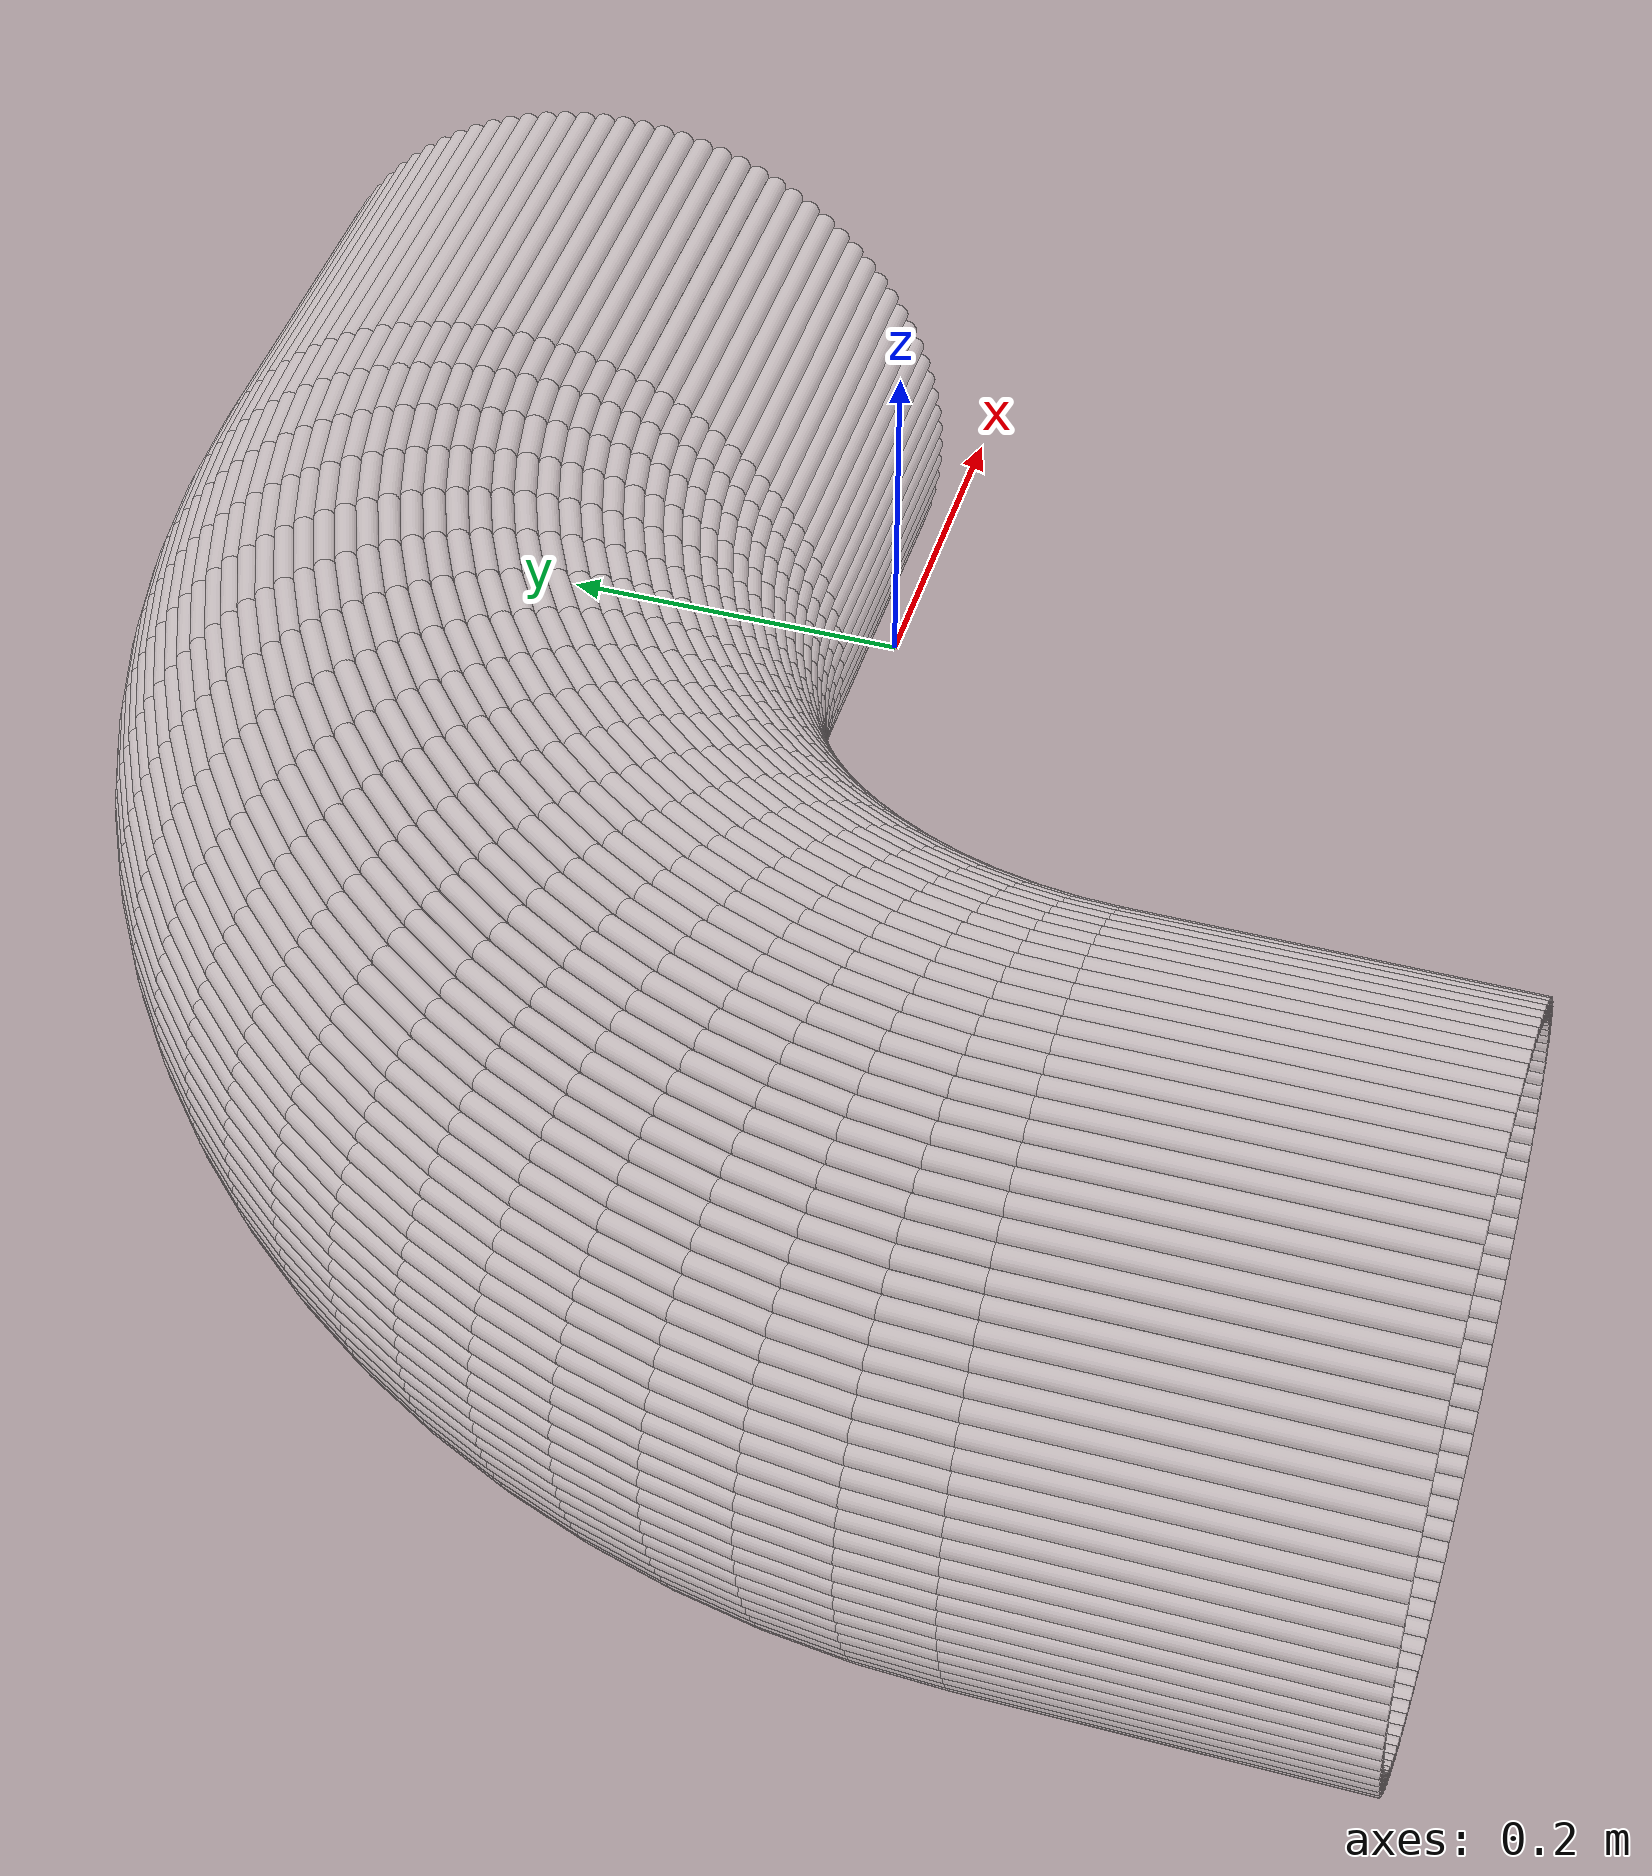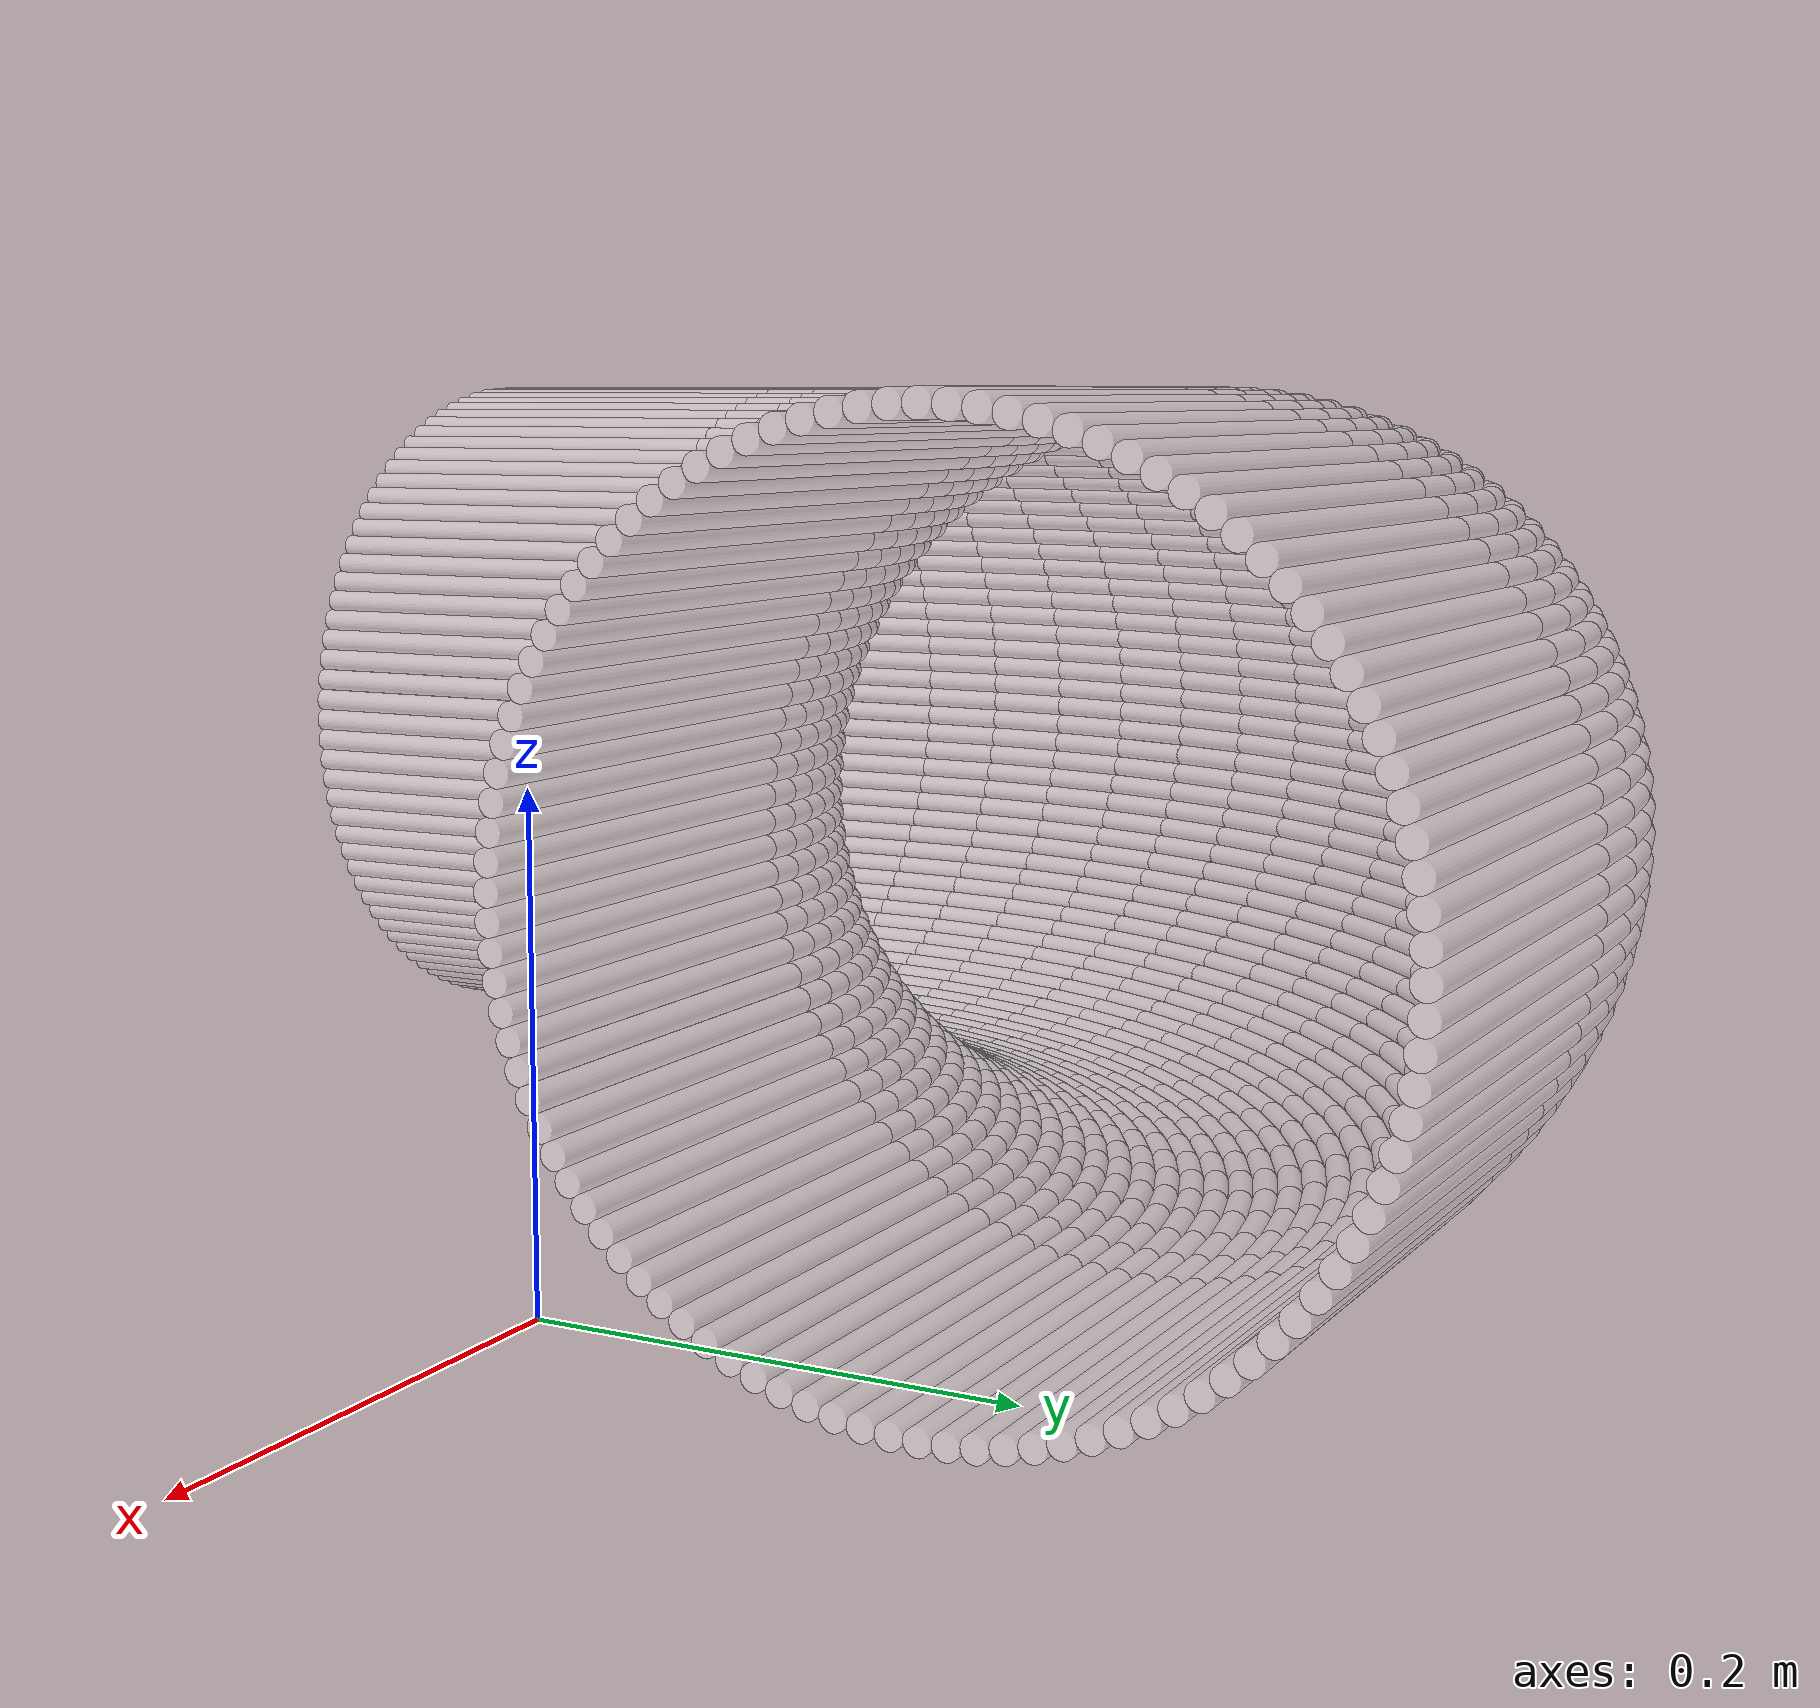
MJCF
<?xml version="1.0" encoding="utf-8"?>
<mujoco>
   <worldbody>
   <body pos="-0.2 -0.24 -0.02" euler="0 0 90">
      <geom euler=" 0 10 0 " fromto="0.58 -0.2 0.18 0.58 0 0.18" rgba="1 1 1 0.35"
            size="0.0056539"
            type="cylinder"/>
      <geom euler=" 0 20 0 " fromto="0.57964 -0.2 0.1913 0.57964 0 0.1913"
            rgba="1 1 1 0.35"
            size="0.0056539"
            type="cylinder"/>
      <geom euler=" 0 30 0 " fromto="0.57858 -0.2 0.20256 0.57858 0 0.20256"
            rgba="1 1 1 0.35"
            size="0.0056539"
            type="cylinder"/>
      <geom euler=" 0 40 0 " fromto="0.57681 -0.2 0.21373 0.57681 0 0.21373"
            rgba="1 1 1 0.35"
            size="0.0056539"
            type="cylinder"/>
      <geom euler=" 0 50 0 " fromto="0.57434 -0.2 0.22476 0.57434 0 0.22476"
            rgba="1 1 1 0.35"
            size="0.0056539"
            type="cylinder"/>
      <geom euler=" 0 60 0 " fromto="0.57119 -0.2 0.23562 0.57119 0 0.23562"
            rgba="1 1 1 0.35"
            size="0.0056539"
            type="cylinder"/>
      <geom euler=" 0 70 0 " fromto="0.56736 -0.2 0.24626 0.56736 0 0.24626"
            rgba="1 1 1 0.35"
            size="0.0056539"
            type="cylinder"/>
      <geom euler=" 0 80 0 " fromto="0.56287 -0.2 0.25664 0.56287 0 0.25664"
            rgba="1 1 1 0.35"
            size="0.0056539"
            type="cylinder"/>
      <geom euler=" 0 90 0 " fromto="0.55774 -0.2 0.26672 0.55774 0 0.26672"
            rgba="1 1 1 0.35"
            size="0.0056539"
            type="cylinder"/>
      <geom euler=" 0 100 0 " fromto="0.55198 -0.2 0.27645 0.55198 0 0.27645"
            rgba="1 1 1 0.35"
            size="0.0056539"
            type="cylinder"/>
      <geom euler=" 0 110 0 " fromto="0.54562 -0.2 0.2858 0.54562 0 0.2858"
            rgba="1 1 1 0.35"
            size="0.0056539"
            type="cylinder"/>
      <geom euler=" 0 120 0 " fromto="0.53869 -0.2 0.29474 0.53869 0 0.29474"
            rgba="1 1 1 0.35"
            size="0.0056539"
            type="cylinder"/>
      <geom euler=" 0 130 0 " fromto="0.53121 -0.2 0.30322 0.53121 0 0.30322"
            rgba="1 1 1 0.35"
            size="0.0056539"
            type="cylinder"/>
      <geom euler=" 0 140 0 " fromto="0.52322 -0.2 0.31121 0.52322 0 0.31121"
            rgba="1 1 1 0.35"
            size="0.0056539"
            type="cylinder"/>
      <geom euler=" 0 150 0 " fromto="0.51474 -0.2 0.31869 0.51474 0 0.31869"
            rgba="1 1 1 0.35"
            size="0.0056539"
            type="cylinder"/>
      <geom euler=" 0 160 0 " fromto="0.5058 -0.2 0.32562 0.5058 0 0.32562"
            rgba="1 1 1 0.35"
            size="0.0056539"
            type="cylinder"/>
      <geom euler=" 0 170 0 " fromto="0.49645 -0.2 0.33198 0.49645 0 0.33198"
            rgba="1 1 1 0.35"
            size="0.0056539"
            type="cylinder"/>
      <geom euler=" 0 180 0 " fromto="0.48672 -0.2 0.33774 0.48672 0 0.33774"
            rgba="1 1 1 0.35"
            size="0.0056539"
            type="cylinder"/>
      <geom euler=" 0 190 0 " fromto="0.47664 -0.2 0.34287 0.47664 0 0.34287"
            rgba="1 1 1 0.35"
            size="0.0056539"
            type="cylinder"/>
      <geom euler=" 0 200 0 " fromto="0.46626 -0.2 0.34736 0.46626 0 0.34736"
            rgba="1 1 1 0.35"
            size="0.0056539"
            type="cylinder"/>
      <geom euler=" 0 210 0 " fromto="0.45562 -0.2 0.35119 0.45562 0 0.35119"
            rgba="1 1 1 0.35"
            size="0.0056539"
            type="cylinder"/>
      <geom euler=" 0 220 0 " fromto="0.44476 -0.2 0.35434 0.44476 0 0.35434"
            rgba="1 1 1 0.35"
            size="0.0056539"
            type="cylinder"/>
      <geom euler=" 0 230 0 " fromto="0.43373 -0.2 0.35681 0.43373 0 0.35681"
            rgba="1 1 1 0.35"
            size="0.0056539"
            type="cylinder"/>
      <geom euler=" 0 240 0 " fromto="0.42256 -0.2 0.35858 0.42256 0 0.35858"
            rgba="1 1 1 0.35"
            size="0.0056539"
            type="cylinder"/>
      <geom euler=" 0 250 0 " fromto="0.4113 -0.2 0.35964 0.4113 0 0.35964"
            rgba="1 1 1 0.35"
            size="0.0056539"
            type="cylinder"/>
      <geom euler=" 0 260 0 " fromto="0.4 -0.2 0.36 0.4 0 0.36" rgba="1 1 1 0.35"
            size="0.0056539"
            type="cylinder"/>
      <geom euler=" 0 270 0 " fromto="0.3887 -0.2 0.35964 0.3887 0 0.35964"
            rgba="1 1 1 0.35"
            size="0.0056539"
            type="cylinder"/>
      <geom euler=" 0 280 0 " fromto="0.37744 -0.2 0.35858 0.37744 0 0.35858"
            rgba="1 1 1 0.35"
            size="0.0056539"
            type="cylinder"/>
      <geom euler=" 0 290 0 " fromto="0.36627 -0.2 0.35681 0.36627 0 0.35681"
            rgba="1 1 1 0.35"
            size="0.0056539"
            type="cylinder"/>
      <geom euler=" 0 300 0 " fromto="0.35524 -0.2 0.35434 0.35524 0 0.35434"
            rgba="1 1 1 0.35"
            size="0.0056539"
            type="cylinder"/>
      <geom euler=" 0 310 0 " fromto="0.34438 -0.2 0.35119 0.34438 0 0.35119"
            rgba="1 1 1 0.35"
            size="0.0056539"
            type="cylinder"/>
      <geom euler=" 0 320 0 " fromto="0.33374 -0.2 0.34736 0.33374 0 0.34736"
            rgba="1 1 1 0.35"
            size="0.0056539"
            type="cylinder"/>
      <geom euler=" 0 330 0 " fromto="0.32336 -0.2 0.34287 0.32336 0 0.34287"
            rgba="1 1 1 0.35"
            size="0.0056539"
            type="cylinder"/>
      <geom euler=" 0 340 0 " fromto="0.31328 -0.2 0.33774 0.31328 0 0.33774"
            rgba="1 1 1 0.35"
            size="0.0056539"
            type="cylinder"/>
      <geom euler=" 0 350 0 " fromto="0.30355 -0.2 0.33198 0.30355 0 0.33198"
            rgba="1 1 1 0.35"
            size="0.0056539"
            type="cylinder"/>
      <geom euler=" 0 360 0 " fromto="0.2942 -0.2 0.32562 0.2942 0 0.32562"
            rgba="1 1 1 0.35"
            size="0.0056539"
            type="cylinder"/>
      <geom euler=" 0 370 0 " fromto="0.28526 -0.2 0.31869 0.28526 0 0.31869"
            rgba="1 1 1 0.35"
            size="0.0056539"
            type="cylinder"/>
      <geom euler=" 0 380 0 " fromto="0.27678 -0.2 0.31121 0.27678 0 0.31121"
            rgba="1 1 1 0.35"
            size="0.0056539"
            type="cylinder"/>
      <geom euler=" 0 390 0 " fromto="0.26879 -0.2 0.30322 0.26879 0 0.30322"
            rgba="1 1 1 0.35"
            size="0.0056539"
            type="cylinder"/>
      <geom euler=" 0 400 0 " fromto="0.26131 -0.2 0.29474 0.26131 0 0.29474"
            rgba="1 1 1 0.35"
            size="0.0056539"
            type="cylinder"/>
      <geom euler=" 0 410 0 " fromto="0.25438 -0.2 0.2858 0.25438 0 0.2858"
            rgba="1 1 1 0.35"
            size="0.0056539"
            type="cylinder"/>
      <geom euler=" 0 420 0 " fromto="0.24802 -0.2 0.27645 0.24802 0 0.27645"
            rgba="1 1 1 0.35"
            size="0.0056539"
            type="cylinder"/>
      <geom euler=" 0 430 0 " fromto="0.24226 -0.2 0.26672 0.24226 0 0.26672"
            rgba="1 1 1 0.35"
            size="0.0056539"
            type="cylinder"/>
      <geom euler=" 0 440 0 " fromto="0.23713 -0.2 0.25664 0.23713 0 0.25664"
            rgba="1 1 1 0.35"
            size="0.0056539"
            type="cylinder"/>
      <geom euler=" 0 450 0 " fromto="0.23264 -0.2 0.24626 0.23264 0 0.24626"
            rgba="1 1 1 0.35"
            size="0.0056539"
            type="cylinder"/>
      <geom euler=" 0 460 0 " fromto="0.22881 -0.2 0.23562 0.22881 0 0.23562"
            rgba="1 1 1 0.35"
            size="0.0056539"
            type="cylinder"/>
      <geom euler=" 0 470 0 " fromto="0.22566 -0.2 0.22476 0.22566 0 0.22476"
            rgba="1 1 1 0.35"
            size="0.0056539"
            type="cylinder"/>
      <geom euler=" 0 480 0 " fromto="0.22319 -0.2 0.21373 0.22319 0 0.21373"
            rgba="1 1 1 0.35"
            size="0.0056539"
            type="cylinder"/>
      <geom euler=" 0 490 0 " fromto="0.22142 -0.2 0.20256 0.22142 0 0.20256"
            rgba="1 1 1 0.35"
            size="0.0056539"
            type="cylinder"/>
      <geom euler=" 0 500 0 " fromto="0.22036 -0.2 0.1913 0.22036 0 0.1913"
            rgba="1 1 1 0.35"
            size="0.0056539"
            type="cylinder"/>
      <geom euler=" 0 510 0 " fromto="0.22 -0.2 0.18 0.22 0 0.18" rgba="1 1 1 0.35"
            size="0.0056539"
            type="cylinder"/>
      <geom euler=" 0 520 0 " fromto="0.22036 -0.2 0.1687 0.22036 0 0.1687"
            rgba="1 1 1 0.35"
            size="0.0056539"
            type="cylinder"/>
      <geom euler=" 0 530 0 " fromto="0.22142 -0.2 0.15744 0.22142 0 0.15744"
            rgba="1 1 1 0.35"
            size="0.0056539"
            type="cylinder"/>
      <geom euler=" 0 540 0 " fromto="0.22319 -0.2 0.14627 0.22319 0 0.14627"
            rgba="1 1 1 0.35"
            size="0.0056539"
            type="cylinder"/>
      <geom euler=" 0 550 0 " fromto="0.22566 -0.2 0.13524 0.22566 0 0.13524"
            rgba="1 1 1 0.35"
            size="0.0056539"
            type="cylinder"/>
      <geom euler=" 0 560 0 " fromto="0.22881 -0.2 0.12438 0.22881 0 0.12438"
            rgba="1 1 1 0.35"
            size="0.0056539"
            type="cylinder"/>
      <geom euler=" 0 570 0 " fromto="0.23264 -0.2 0.11374 0.23264 0 0.11374"
            rgba="1 1 1 0.35"
            size="0.0056539"
            type="cylinder"/>
      <geom euler=" 0 580 0 " fromto="0.23713 -0.2 0.10336 0.23713 0 0.10336"
            rgba="1 1 1 0.35"
            size="0.0056539"
            type="cylinder"/>
      <geom euler=" 0 590 0 " fromto="0.24226 -0.2 0.093284 0.24226 0 0.093284"
            rgba="1 1 1 0.35"
            size="0.0056539"
            type="cylinder"/>
      <geom euler=" 0 600 0 " fromto="0.24802 -0.2 0.083551 0.24802 0 0.083551"
            rgba="1 1 1 0.35"
            size="0.0056539"
            type="cylinder"/>
      <geom euler=" 0 610 0 " fromto="0.25438 -0.2 0.074199 0.25438 0 0.074199"
            rgba="1 1 1 0.35"
            size="0.0056539"
            type="cylinder"/>
      <geom euler=" 0 620 0 " fromto="0.26131 -0.2 0.065264 0.26131 0 0.065264"
            rgba="1 1 1 0.35"
            size="0.0056539"
            type="cylinder"/>
      <geom euler=" 0 630 0 " fromto="0.26879 -0.2 0.056782 0.26879 0 0.056782"
            rgba="1 1 1 0.35"
            size="0.0056539"
            type="cylinder"/>
      <geom euler=" 0 640 0 " fromto="0.27678 -0.2 0.048786 0.27678 0 0.048786"
            rgba="1 1 1 0.35"
            size="0.0056539"
            type="cylinder"/>
      <geom euler=" 0 650 0 " fromto="0.28526 -0.2 0.041308 0.28526 0 0.041308"
            rgba="1 1 1 0.35"
            size="0.0056539"
            type="cylinder"/>
      <geom euler=" 0 660 0 " fromto="0.2942 -0.2 0.034377 0.2942 0 0.034377"
            rgba="1 1 1 0.35"
            size="0.0056539"
            type="cylinder"/>
      <geom euler=" 0 670 0 " fromto="0.30355 -0.2 0.028021 0.30355 0 0.028021"
            rgba="1 1 1 0.35"
            size="0.0056539"
            type="cylinder"/>
      <geom euler=" 0 680 0 " fromto="0.31328 -0.2 0.022265 0.31328 0 0.022265"
            rgba="1 1 1 0.35"
            size="0.0056539"
            type="cylinder"/>
      <geom euler=" 0 690 0 " fromto="0.32336 -0.2 0.017131 0.32336 0 0.017131"
            rgba="1 1 1 0.35"
            size="0.0056539"
            type="cylinder"/>
      <geom euler=" 0 700 0 " fromto="0.33374 -0.2 0.01264 0.33374 0 0.01264"
            rgba="1 1 1 0.35"
            size="0.0056539"
            type="cylinder"/>
      <geom euler=" 0 710 0 " fromto="0.34438 -0.2 0.0088098 0.34438 0 0.0088098"
            rgba="1 1 1 0.35"
            size="0.0056539"
            type="cylinder"/>
      <geom euler=" 0 720 0 " fromto="0.35524 -0.2 0.005655 0.35524 0 0.005655"
            rgba="1 1 1 0.35"
            size="0.0056539"
            type="cylinder"/>
      <geom euler=" 0 730 0 " fromto="0.36627 -0.2 0.0031883 0.36627 0 0.0031883"
            rgba="1 1 1 0.35"
            size="0.0056539"
            type="cylinder"/>
      <geom euler=" 0 740 0 " fromto="0.37744 -0.2 0.0014194 0.37744 0 0.0014194"
            rgba="1 1 1 0.35"
            size="0.0056539"
            type="cylinder"/>
      <geom euler=" 0 750 0 " fromto="0.3887 -0.2 0.00035519 0.3887 0 0.00035519"
            rgba="1 1 1 0.35"
            size="0.0056539"
            type="cylinder"/>
      <geom euler=" 0 760 0 " fromto="0.4 -0.2 0 0.4 0 0" rgba="1 1 1 0.35"
            size="0.0056539"
            type="cylinder"/>
      <geom euler=" 0 770 0 " fromto="0.4113 -0.2 0.00035519 0.4113 0 0.00035519"
            rgba="1 1 1 0.35"
            size="0.0056539"
            type="cylinder"/>
      <geom euler=" 0 780 0 " fromto="0.42256 -0.2 0.0014194 0.42256 0 0.0014194"
            rgba="1 1 1 0.35"
            size="0.0056539"
            type="cylinder"/>
      <geom euler=" 0 790 0 " fromto="0.43373 -0.2 0.0031883 0.43373 0 0.0031883"
            rgba="1 1 1 0.35"
            size="0.0056539"
            type="cylinder"/>
      <geom euler=" 0 800 0 " fromto="0.44476 -0.2 0.005655 0.44476 0 0.005655"
            rgba="1 1 1 0.35"
            size="0.0056539"
            type="cylinder"/>
      <geom euler=" 0 810 0 " fromto="0.45562 -0.2 0.0088098 0.45562 0 0.0088098"
            rgba="1 1 1 0.35"
            size="0.0056539"
            type="cylinder"/>
      <geom euler=" 0 820 0 " fromto="0.46626 -0.2 0.01264 0.46626 0 0.01264"
            rgba="1 1 1 0.35"
            size="0.0056539"
            type="cylinder"/>
      <geom euler=" 0 830 0 " fromto="0.47664 -0.2 0.017131 0.47664 0 0.017131"
            rgba="1 1 1 0.35"
            size="0.0056539"
            type="cylinder"/>
      <geom euler=" 0 840 0 " fromto="0.48672 -0.2 0.022265 0.48672 0 0.022265"
            rgba="1 1 1 0.35"
            size="0.0056539"
            type="cylinder"/>
      <geom euler=" 0 850 0 " fromto="0.49645 -0.2 0.028021 0.49645 0 0.028021"
            rgba="1 1 1 0.35"
            size="0.0056539"
            type="cylinder"/>
      <geom euler=" 0 860 0 " fromto="0.5058 -0.2 0.034377 0.5058 0 0.034377"
            rgba="1 1 1 0.35"
            size="0.0056539"
            type="cylinder"/>
      <geom euler=" 0 870 0 " fromto="0.51474 -0.2 0.041308 0.51474 0 0.041308"
            rgba="1 1 1 0.35"
            size="0.0056539"
            type="cylinder"/>
      <geom euler=" 0 880 0 " fromto="0.52322 -0.2 0.048786 0.52322 0 0.048786"
            rgba="1 1 1 0.35"
            size="0.0056539"
            type="cylinder"/>
      <geom euler=" 0 890 0 " fromto="0.53121 -0.2 0.056782 0.53121 0 0.056782"
            rgba="1 1 1 0.35"
            size="0.0056539"
            type="cylinder"/>
      <geom euler=" 0 900 0 " fromto="0.53869 -0.2 0.065264 0.53869 0 0.065264"
            rgba="1 1 1 0.35"
            size="0.0056539"
            type="cylinder"/>
      <geom euler=" 0 910 0 " fromto="0.54562 -0.2 0.074199 0.54562 0 0.074199"
            rgba="1 1 1 0.35"
            size="0.0056539"
            type="cylinder"/>
      <geom euler=" 0 920 0 " fromto="0.55198 -0.2 0.083551 0.55198 0 0.083551"
            rgba="1 1 1 0.35"
            size="0.0056539"
            type="cylinder"/>
      <geom euler=" 0 930 0 " fromto="0.55774 -0.2 0.093284 0.55774 0 0.093284"
            rgba="1 1 1 0.35"
            size="0.0056539"
            type="cylinder"/>
      <geom euler=" 0 940 0 " fromto="0.56287 -0.2 0.10336 0.56287 0 0.10336"
            rgba="1 1 1 0.35"
            size="0.0056539"
            type="cylinder"/>
      <geom euler=" 0 950 0 " fromto="0.56736 -0.2 0.11374 0.56736 0 0.11374"
            rgba="1 1 1 0.35"
            size="0.0056539"
            type="cylinder"/>
      <geom euler=" 0 960 0 " fromto="0.57119 -0.2 0.12438 0.57119 0 0.12438"
            rgba="1 1 1 0.35"
            size="0.0056539"
            type="cylinder"/>
      <geom euler=" 0 970 0 " fromto="0.57434 -0.2 0.13524 0.57434 0 0.13524"
            rgba="1 1 1 0.35"
            size="0.0056539"
            type="cylinder"/>
      <geom euler=" 0 980 0 " fromto="0.57681 -0.2 0.14627 0.57681 0 0.14627"
            rgba="1 1 1 0.35"
            size="0.0056539"
            type="cylinder"/>
      <geom euler=" 0 990 0 " fromto="0.57858 -0.2 0.15744 0.57858 0 0.15744"
            rgba="1 1 1 0.35"
            size="0.0056539"
            type="cylinder"/>
      <geom euler=" 0 1000 0 " fromto="0.57964 -0.2 0.1687 0.57964 0 0.1687"
            rgba="1 1 1 0.35"
            size="0.0056539"
            type="cylinder"/>
      <geom euler=" 0 10 0 " fromto="0.58 0 0.18 0.57802 0.047896 0.18" rgba="1 1 1 0.35"
            size="0.0056539"
            type="cylinder"/>
      <geom euler=" 0 20 0 " fromto="0.57964 0 0.1913 0.57767 0.047867 0.1913"
            rgba="1 1 1 0.35"
            size="0.0056539"
            type="cylinder"/>
      <geom euler=" 0 30 0 " fromto="0.57858 0 0.20256 0.5766 0.047779 0.20256"
            rgba="1 1 1 0.35"
            size="0.0056539"
            type="cylinder"/>
      <geom euler=" 0 40 0 " fromto="0.57681 0 0.21373 0.57484 0.047633 0.21373"
            rgba="1 1 1 0.35"
            size="0.0056539"
            type="cylinder"/>
      <geom euler=" 0 50 0 " fromto="0.57434 0 0.22476 0.57238 0.047429 0.22476"
            rgba="1 1 1 0.35"
            size="0.0056539"
            type="cylinder"/>
      <geom euler=" 0 60 0 " fromto="0.57119 0 0.23562 0.56924 0.047169 0.23562"
            rgba="1 1 1 0.35"
            size="0.0056539"
            type="cylinder"/>
      <geom euler=" 0 70 0 " fromto="0.56736 0 0.24626 0.56542 0.046852 0.24626"
            rgba="1 1 1 0.35"
            size="0.0056539"
            type="cylinder"/>
      <geom euler=" 0 80 0 " fromto="0.56287 0 0.25664 0.56095 0.046481 0.25664"
            rgba="1 1 1 0.35"
            size="0.0056539"
            type="cylinder"/>
      <geom euler=" 0 90 0 " fromto="0.55774 0 0.26672 0.55583 0.046057 0.26672"
            rgba="1 1 1 0.35"
            size="0.0056539"
            type="cylinder"/>
      <geom euler=" 0 100 0 " fromto="0.55198 0 0.27645 0.55009 0.045582 0.27645"
            rgba="1 1 1 0.35"
            size="0.0056539"
            type="cylinder"/>
      <geom euler=" 0 110 0 " fromto="0.54562 0 0.2858 0.54376 0.045057 0.2858"
            rgba="1 1 1 0.35"
            size="0.0056539"
            type="cylinder"/>
      <geom euler=" 0 120 0 " fromto="0.53869 0 0.29474 0.53685 0.044485 0.29474"
            rgba="1 1 1 0.35"
            size="0.0056539"
            type="cylinder"/>
      <geom euler=" 0 130 0 " fromto="0.53121 0 0.30322 0.5294 0.043867 0.30322"
            rgba="1 1 1 0.35"
            size="0.0056539"
            type="cylinder"/>
      <geom euler=" 0 140 0 " fromto="0.52322 0 0.31121 0.52143 0.043207 0.31121"
            rgba="1 1 1 0.35"
            size="0.0056539"
            type="cylinder"/>
      <geom euler=" 0 150 0 " fromto="0.51474 0 0.31869 0.51298 0.042507 0.31869"
            rgba="1 1 1 0.35"
            size="0.0056539"
            type="cylinder"/>
      <geom euler=" 0 160 0 " fromto="0.5058 0 0.32562 0.50407 0.041769 0.32562"
            rgba="1 1 1 0.35"
            size="0.0056539"
            type="cylinder"/>
      <geom euler=" 0 170 0 " fromto="0.49645 0 0.33198 0.49475 0.040996 0.33198"
            rgba="1 1 1 0.35"
            size="0.0056539"
            type="cylinder"/>
      <geom euler=" 0 180 0 " fromto="0.48672 0 0.33774 0.48505 0.040193 0.33774"
            rgba="1 1 1 0.35"
            size="0.0056539"
            type="cylinder"/>
      <geom euler=" 0 190 0 " fromto="0.47664 0 0.34287 0.47501 0.039361 0.34287"
            rgba="1 1 1 0.35"
            size="0.0056539"
            type="cylinder"/>
      <geom euler=" 0 200 0 " fromto="0.46626 0 0.34736 0.46467 0.038504 0.34736"
            rgba="1 1 1 0.35"
            size="0.0056539"
            type="cylinder"/>
      <geom euler=" 0 210 0 " fromto="0.45562 0 0.35119 0.45407 0.037625 0.35119"
            rgba="1 1 1 0.35"
            size="0.0056539"
            type="cylinder"/>
      <geom euler=" 0 220 0 " fromto="0.44476 0 0.35434 0.44325 0.036728 0.35434"
            rgba="1 1 1 0.35"
            size="0.0056539"
            type="cylinder"/>
      <geom euler=" 0 230 0 " fromto="0.43373 0 0.35681 0.43225 0.035817 0.35681"
            rgba="1 1 1 0.35"
            size="0.0056539"
            type="cylinder"/>
      <geom euler=" 0 240 0 " fromto="0.42256 0 0.35858 0.42112 0.034895 0.35858"
            rgba="1 1 1 0.35"
            size="0.0056539"
            type="cylinder"/>
      <geom euler=" 0 250 0 " fromto="0.4113 0 0.35964 0.4099 0.033965 0.35964"
            rgba="1 1 1 0.35"
            size="0.0056539"
            type="cylinder"/>
      <geom euler=" 0 260 0 " fromto="0.4 0 0.36 0.39863 0.033032 0.36" rgba="1 1 1 0.35"
            size="0.0056539"
            type="cylinder"/>
      <geom euler=" 0 270 0 " fromto="0.3887 0 0.35964 0.38737 0.032098 0.35964"
            rgba="1 1 1 0.35"
            size="0.0056539"
            type="cylinder"/>
      <geom euler=" 0 280 0 " fromto="0.37744 0 0.35858 0.37615 0.031169 0.35858"
            rgba="1 1 1 0.35"
            size="0.0056539"
            type="cylinder"/>
      <geom euler=" 0 290 0 " fromto="0.36627 0 0.35681 0.36502 0.030246 0.35681"
            rgba="1 1 1 0.35"
            size="0.0056539"
            type="cylinder"/>
      <geom euler=" 0 300 0 " fromto="0.35524 0 0.35434 0.35402 0.029335 0.35434"
            rgba="1 1 1 0.35"
            size="0.0056539"
            type="cylinder"/>
      <geom euler=" 0 310 0 " fromto="0.34438 0 0.35119 0.3432 0.028438 0.35119"
            rgba="1 1 1 0.35"
            size="0.0056539"
            type="cylinder"/>
      <geom euler=" 0 320 0 " fromto="0.33374 0 0.34736 0.3326 0.02756 0.34736"
            rgba="1 1 1 0.35"
            size="0.0056539"
            type="cylinder"/>
      <geom euler=" 0 330 0 " fromto="0.32336 0 0.34287 0.32226 0.026703 0.34287"
            rgba="1 1 1 0.35"
            size="0.0056539"
            type="cylinder"/>
      <geom euler=" 0 340 0 " fromto="0.31328 0 0.33774 0.31221 0.025871 0.33774"
            rgba="1 1 1 0.35"
            size="0.0056539"
            type="cylinder"/>
      <geom euler=" 0 350 0 " fromto="0.30355 0 0.33198 0.30251 0.025067 0.33198"
            rgba="1 1 1 0.35"
            size="0.0056539"
            type="cylinder"/>
      <geom euler=" 0 360 0 " fromto="0.2942 0 0.32562 0.29319 0.024295 0.32562"
            rgba="1 1 1 0.35"
            size="0.0056539"
            type="cylinder"/>
      <geom euler=" 0 370 0 " fromto="0.28526 0 0.31869 0.28429 0.023557 0.31869"
            rgba="1 1 1 0.35"
            size="0.0056539"
            type="cylinder"/>
      <geom euler=" 0 380 0 " fromto="0.27678 0 0.31121 0.27584 0.022856 0.31121"
            rgba="1 1 1 0.35"
            size="0.0056539"
            type="cylinder"/>
      <geom euler=" 0 390 0 " fromto="0.26879 0 0.30322 0.26787 0.022196 0.30322"
            rgba="1 1 1 0.35"
            size="0.0056539"
            type="cylinder"/>
      <geom euler=" 0 400 0 " fromto="0.26131 0 0.29474 0.26042 0.021579 0.29474"
            rgba="1 1 1 0.35"
            size="0.0056539"
            type="cylinder"/>
      <geom euler=" 0 410 0 " fromto="0.25438 0 0.2858 0.25351 0.021006 0.2858"
            rgba="1 1 1 0.35"
            size="0.0056539"
            type="cylinder"/>
      <geom euler=" 0 420 0 " fromto="0.24802 0 0.27645 0.24717 0.020481 0.27645"
            rgba="1 1 1 0.35"
            size="0.0056539"
            type="cylinder"/>
      <geom euler=" 0 430 0 " fromto="0.24226 0 0.26672 0.24144 0.020006 0.26672"
            rgba="1 1 1 0.35"
            size="0.0056539"
            type="cylinder"/>
      <geom euler=" 0 440 0 " fromto="0.23713 0 0.25664 0.23632 0.019582 0.25664"
            rgba="1 1 1 0.35"
            size="0.0056539"
            type="cylinder"/>
      <geom euler=" 0 450 0 " fromto="0.23264 0 0.24626 0.23185 0.019211 0.24626"
            rgba="1 1 1 0.35"
            size="0.0056539"
            type="cylinder"/>
      <geom euler=" 0 460 0 " fromto="0.22881 0 0.23562 0.22803 0.018895 0.23562"
            rgba="1 1 1 0.35"
            size="0.0056539"
            type="cylinder"/>
      <geom euler=" 0 470 0 " fromto="0.22566 0 0.22476 0.22488 0.018634 0.22476"
            rgba="1 1 1 0.35"
            size="0.0056539"
            type="cylinder"/>
      <geom euler=" 0 480 0 " fromto="0.22319 0 0.21373 0.22243 0.018431 0.21373"
            rgba="1 1 1 0.35"
            size="0.0056539"
            type="cylinder"/>
      <geom euler=" 0 490 0 " fromto="0.22142 0 0.20256 0.22066 0.018285 0.20256"
            rgba="1 1 1 0.35"
            size="0.0056539"
            type="cylinder"/>
      <geom euler=" 0 500 0 " fromto="0.22036 0 0.1913 0.2196 0.018197 0.1913"
            rgba="1 1 1 0.35"
            size="0.0056539"
            type="cylinder"/>
      <geom euler=" 0 510 0 " fromto="0.22 0 0.18 0.21925 0.018167 0.18" rgba="1 1 1 0.35"
            size="0.0056539"
            type="cylinder"/>
      <geom euler=" 0 520 0 " fromto="0.22036 0 0.1687 0.2196 0.018197 0.1687"
            rgba="1 1 1 0.35"
            size="0.0056539"
            type="cylinder"/>
      <geom euler=" 0 530 0 " fromto="0.22142 0 0.15744 0.22066 0.018285 0.15744"
            rgba="1 1 1 0.35"
            size="0.0056539"
            type="cylinder"/>
      <geom euler=" 0 540 0 " fromto="0.22319 0 0.14627 0.22243 0.018431 0.14627"
            rgba="1 1 1 0.35"
            size="0.0056539"
            type="cylinder"/>
      <geom euler=" 0 550 0 " fromto="0.22566 0 0.13524 0.22488 0.018634 0.13524"
            rgba="1 1 1 0.35"
            size="0.0056539"
            type="cylinder"/>
      <geom euler=" 0 560 0 " fromto="0.22881 0 0.12438 0.22803 0.018895 0.12438"
            rgba="1 1 1 0.35"
            size="0.0056539"
            type="cylinder"/>
      <geom euler=" 0 570 0 " fromto="0.23264 0 0.11374 0.23185 0.019211 0.11374"
            rgba="1 1 1 0.35"
            size="0.0056539"
            type="cylinder"/>
      <geom euler=" 0 580 0 " fromto="0.23713 0 0.10336 0.23632 0.019582 0.10336"
            rgba="1 1 1 0.35"
            size="0.0056539"
            type="cylinder"/>
      <geom euler=" 0 590 0 " fromto="0.24226 0 0.093284 0.24144 0.020006 0.093284"
            rgba="1 1 1 0.35"
            size="0.0056539"
            type="cylinder"/>
      <geom euler=" 0 600 0 " fromto="0.24802 0 0.083551 0.24717 0.020481 0.083551"
            rgba="1 1 1 0.35"
            size="0.0056539"
            type="cylinder"/>
      <geom euler=" 0 610 0 " fromto="0.25438 0 0.074199 0.25351 0.021006 0.074199"
            rgba="1 1 1 0.35"
            size="0.0056539"
            type="cylinder"/>
      <geom euler=" 0 620 0 " fromto="0.26131 0 0.065264 0.26042 0.021579 0.065264"
            rgba="1 1 1 0.35"
            size="0.0056539"
            type="cylinder"/>
      <geom euler=" 0 630 0 " fromto="0.26879 0 0.056782 0.26787 0.022196 0.056782"
            rgba="1 1 1 0.35"
            size="0.0056539"
            type="cylinder"/>
      <geom euler=" 0 640 0 " fromto="0.27678 0 0.048786 0.27584 0.022856 0.048786"
            rgba="1 1 1 0.35"
            size="0.0056539"
            type="cylinder"/>
      <geom euler=" 0 650 0 " fromto="0.28526 0 0.041308 0.28429 0.023557 0.041308"
            rgba="1 1 1 0.35"
            size="0.0056539"
            type="cylinder"/>
      <geom euler=" 0 660 0 " fromto="0.2942 0 0.034377 0.29319 0.024295 0.034377"
            rgba="1 1 1 0.35"
            size="0.0056539"
            type="cylinder"/>
      <geom euler=" 0 670 0 " fromto="0.30355 0 0.028021 0.30251 0.025067 0.028021"
            rgba="1 1 1 0.35"
            size="0.0056539"
            type="cylinder"/>
      <geom euler=" 0 680 0 " fromto="0.31328 0 0.022265 0.31221 0.025871 0.022265"
            rgba="1 1 1 0.35"
            size="0.0056539"
            type="cylinder"/>
      <geom euler=" 0 690 0 " fromto="0.32336 0 0.017131 0.32226 0.026703 0.017131"
            rgba="1 1 1 0.35"
            size="0.0056539"
            type="cylinder"/>
      <geom euler=" 0 700 0 " fromto="0.33374 0 0.01264 0.3326 0.02756 0.01264"
            rgba="1 1 1 0.35"
            size="0.0056539"
            type="cylinder"/>
      <geom euler=" 0 710 0 " fromto="0.34438 0 0.0088098 0.3432 0.028438 0.0088098"
            rgba="1 1 1 0.35"
            size="0.0056539"
            type="cylinder"/>
      <geom euler=" 0 720 0 " fromto="0.35524 0 0.005655 0.35402 0.029335 0.005655"
            rgba="1 1 1 0.35"
            size="0.0056539"
            type="cylinder"/>
      <geom euler=" 0 730 0 " fromto="0.36627 0 0.0031883 0.36502 0.030246 0.0031883"
            rgba="1 1 1 0.35"
            size="0.0056539"
            type="cylinder"/>
      <geom euler=" 0 740 0 " fromto="0.37744 0 0.0014194 0.37615 0.031169 0.0014194"
            rgba="1 1 1 0.35"
            size="0.0056539"
            type="cylinder"/>
      <geom euler=" 0 750 0 " fromto="0.3887 0 0.00035519 0.38737 0.032098 0.00035519"
            rgba="1 1 1 0.35"
            size="0.0056539"
            type="cylinder"/>
      <geom euler=" 0 760 0 " fromto="0.4 0 0 0.39863 0.033032 0" rgba="1 1 1 0.35"
            size="0.0056539"
            type="cylinder"/>
      <geom euler=" 0 770 0 " fromto="0.4113 0 0.00035519 0.4099 0.033965 0.00035519"
            rgba="1 1 1 0.35"
            size="0.0056539"
            type="cylinder"/>
      <geom euler=" 0 780 0 " fromto="0.42256 0 0.0014194 0.42112 0.034895 0.0014194"
            rgba="1 1 1 0.35"
            size="0.0056539"
            type="cylinder"/>
      <geom euler=" 0 790 0 " fromto="0.43373 0 0.0031883 0.43225 0.035817 0.0031883"
            rgba="1 1 1 0.35"
            size="0.0056539"
            type="cylinder"/>
      <geom euler=" 0 800 0 " fromto="0.44476 0 0.005655 0.44325 0.036728 0.005655"
            rgba="1 1 1 0.35"
            size="0.0056539"
            type="cylinder"/>
      <geom euler=" 0 810 0 " fromto="0.45562 0 0.0088098 0.45407 0.037625 0.0088098"
            rgba="1 1 1 0.35"
            size="0.0056539"
            type="cylinder"/>
      <geom euler=" 0 820 0 " fromto="0.46626 0 0.01264 0.46467 0.038504 0.01264"
            rgba="1 1 1 0.35"
            size="0.0056539"
            type="cylinder"/>
      <geom euler=" 0 830 0 " fromto="0.47664 0 0.017131 0.47501 0.039361 0.017131"
            rgba="1 1 1 0.35"
            size="0.0056539"
            type="cylinder"/>
      <geom euler=" 0 840 0 " fromto="0.48672 0 0.022265 0.48505 0.040193 0.022265"
            rgba="1 1 1 0.35"
            size="0.0056539"
            type="cylinder"/>
      <geom euler=" 0 850 0 " fromto="0.49645 0 0.028021 0.49475 0.040996 0.028021"
            rgba="1 1 1 0.35"
            size="0.0056539"
            type="cylinder"/>
      <geom euler=" 0 860 0 " fromto="0.5058 0 0.034377 0.50407 0.041769 0.034377"
            rgba="1 1 1 0.35"
            size="0.0056539"
            type="cylinder"/>
      <geom euler=" 0 870 0 " fromto="0.51474 0 0.041308 0.51298 0.042507 0.041308"
            rgba="1 1 1 0.35"
            size="0.0056539"
            type="cylinder"/>
      <geom euler=" 0 880 0 " fromto="0.52322 0 0.048786 0.52143 0.043207 0.048786"
            rgba="1 1 1 0.35"
            size="0.0056539"
            type="cylinder"/>
      <geom euler=" 0 890 0 " fromto="0.53121 0 0.056782 0.5294 0.043867 0.056782"
            rgba="1 1 1 0.35"
            size="0.0056539"
            type="cylinder"/>
      <geom euler=" 0 900 0 " fromto="0.53869 0 0.065264 0.53685 0.044485 0.065264"
            rgba="1 1 1 0.35"
            size="0.0056539"
            type="cylinder"/>
      <geom euler=" 0 910 0 " fromto="0.54562 0 0.074199 0.54376 0.045057 0.074199"
            rgba="1 1 1 0.35"
            size="0.0056539"
            type="cylinder"/>
      <geom euler=" 0 920 0 " fromto="0.55198 0 0.083551 0.55009 0.045582 0.083551"
            rgba="1 1 1 0.35"
            size="0.0056539"
            type="cylinder"/>
      <geom euler=" 0 930 0 " fromto="0.55774 0 0.093284 0.55583 0.046057 0.093284"
            rgba="1 1 1 0.35"
            size="0.0056539"
            type="cylinder"/>
      <geom euler=" 0 940 0 " fromto="0.56287 0 0.10336 0.56095 0.046481 0.10336"
            rgba="1 1 1 0.35"
            size="0.0056539"
            type="cylinder"/>
      <geom euler=" 0 950 0 " fromto="0.56736 0 0.11374 0.56542 0.046852 0.11374"
            rgba="1 1 1 0.35"
            size="0.0056539"
            type="cylinder"/>
      <geom euler=" 0 960 0 " fromto="0.57119 0 0.12438 0.56924 0.047169 0.12438"
            rgba="1 1 1 0.35"
            size="0.0056539"
            type="cylinder"/>
      <geom euler=" 0 970 0 " fromto="0.57434 0 0.13524 0.57238 0.047429 0.13524"
            rgba="1 1 1 0.35"
            size="0.0056539"
            type="cylinder"/>
      <geom euler=" 0 980 0 " fromto="0.57681 0 0.14627 0.57484 0.047633 0.14627"
            rgba="1 1 1 0.35"
            size="0.0056539"
            type="cylinder"/>
      <geom euler=" 0 990 0 " fromto="0.57858 0 0.15744 0.5766 0.047779 0.15744"
            rgba="1 1 1 0.35"
            size="0.0056539"
            type="cylinder"/>
      <geom euler=" 0 1000 0 " fromto="0.57964 0 0.1687 0.57767 0.047867 0.1687"
            rgba="1 1 1 0.35"
            size="0.0056539"
            type="cylinder"/>
      <geom euler=" 0 10 0 " fromto="0.57802 0.047896 0.18 0.57209 0.095465 0.18"
            rgba="1 1 1 0.35"
            size="0.0056539"
            type="cylinder"/>
      <geom euler=" 0 20 0 " fromto="0.57767 0.047867 0.1913 0.57174 0.095406 0.1913"
            rgba="1 1 1 0.35"
            size="0.0056539"
            type="cylinder"/>
      <geom euler=" 0 30 0 " fromto="0.5766 0.047779 0.20256 0.57069 0.095231 0.20256"
            rgba="1 1 1 0.35"
            size="0.0056539"
            type="cylinder"/>
      <geom euler=" 0 40 0 " fromto="0.57484 0.047633 0.21373 0.56894 0.09494 0.21373"
            rgba="1 1 1 0.35"
            size="0.0056539"
            type="cylinder"/>
      <geom euler=" 0 50 0 " fromto="0.57238 0.047429 0.22476 0.56651 0.094534 0.22476"
            rgba="1 1 1 0.35"
            size="0.0056539"
            type="cylinder"/>
      <geom euler=" 0 60 0 " fromto="0.56924 0.047169 0.23562 0.5634 0.094015 0.23562"
            rgba="1 1 1 0.35"
            size="0.0056539"
            type="cylinder"/>
      <geom euler=" 0 70 0 " fromto="0.56542 0.046852 0.24626 0.55962 0.093384 0.24626"
            rgba="1 1 1 0.35"
            size="0.0056539"
            type="cylinder"/>
      <geom euler=" 0 80 0 " fromto="0.56095 0.046481 0.25664 0.55519 0.092645 0.25664"
            rgba="1 1 1 0.35"
            size="0.0056539"
            type="cylinder"/>
      <geom euler=" 0 90 0 " fromto="0.55583 0.046057 0.26672 0.55013 0.0918 0.26672"
            rgba="1 1 1 0.35"
            size="0.0056539"
            type="cylinder"/>
      <geom euler=" 0 100 0 " fromto="0.55009 0.045582 0.27645 0.54445 0.090853 0.27645"
            rgba="1 1 1 0.35"
            size="0.0056539"
            type="cylinder"/>
      <geom euler=" 0 110 0 " fromto="0.54376 0.045057 0.2858 0.53818 0.089807 0.2858"
            rgba="1 1 1 0.35"
            size="0.0056539"
            type="cylinder"/>
      <geom euler=" 0 120 0 " fromto="0.53685 0.044485 0.29474 0.53135 0.088666 0.29474"
            rgba="1 1 1 0.35"
            size="0.0056539"
            type="cylinder"/>
      <geom euler=" 0 130 0 " fromto="0.5294 0.043867 0.30322 0.52397 0.087435 0.30322"
            rgba="1 1 1 0.35"
            size="0.0056539"
            type="cylinder"/>
      <geom euler=" 0 140 0 " fromto="0.52143 0.043207 0.31121 0.51608 0.086119 0.31121"
            rgba="1 1 1 0.35"
            size="0.0056539"
            type="cylinder"/>
      <geom euler=" 0 150 0 " fromto="0.51298 0.042507 0.31869 0.50772 0.084723 0.31869"
            rgba="1 1 1 0.35"
            size="0.0056539"
            type="cylinder"/>
      <geom euler=" 0 160 0 " fromto="0.50407 0.041769 0.32562 0.4989 0.083252 0.32562"
            rgba="1 1 1 0.35"
            size="0.0056539"
            type="cylinder"/>
      <geom euler=" 0 170 0 " fromto="0.49475 0.040996 0.33198 0.48968 0.081713 0.33198"
            rgba="1 1 1 0.35"
            size="0.0056539"
            type="cylinder"/>
      <geom euler=" 0 180 0 " fromto="0.48505 0.040193 0.33774 0.48008 0.080111 0.33774"
            rgba="1 1 1 0.35"
            size="0.0056539"
            type="cylinder"/>
      <geom euler=" 0 190 0 " fromto="0.47501 0.039361 0.34287 0.47014 0.078452 0.34287"
            rgba="1 1 1 0.35"
            size="0.0056539"
            type="cylinder"/>
      <geom euler=" 0 200 0 " fromto="0.46467 0.038504 0.34736 0.4599 0.076744 0.34736"
            rgba="1 1 1 0.35"
            size="0.0056539"
            type="cylinder"/>
      <geom euler=" 0 210 0 " fromto="0.45407 0.037625 0.35119 0.44941 0.074993 0.35119"
            rgba="1 1 1 0.35"
            size="0.0056539"
            type="cylinder"/>
      <geom euler=" 0 220 0 " fromto="0.44325 0.036728 0.35434 0.4387 0.073206 0.35434"
            rgba="1 1 1 0.35"
            size="0.0056539"
            type="cylinder"/>
      <geom euler=" 0 230 0 " fromto="0.43225 0.035817 0.35681 0.42781 0.071389 0.35681"
            rgba="1 1 1 0.35"
            size="0.0056539"
            type="cylinder"/>
      <geom euler=" 0 240 0 " fromto="0.42112 0.034895 0.35858 0.4168 0.069551 0.35858"
            rgba="1 1 1 0.35"
            size="0.0056539"
            type="cylinder"/>
      <geom euler=" 0 250 0 " fromto="0.4099 0.033965 0.35964 0.40569 0.067698 0.35964"
            rgba="1 1 1 0.35"
            size="0.0056539"
            type="cylinder"/>
      <geom euler=" 0 260 0 " fromto="0.39863 0.033032 0.36 0.39454 0.065838 0.36"
            rgba="1 1 1 0.35"
            size="0.0056539"
            type="cylinder"/>
      <geom euler=" 0 270 0 " fromto="0.38737 0.032098 0.35964 0.3834 0.063978 0.35964"
            rgba="1 1 1 0.35"
            size="0.0056539"
            type="cylinder"/>
      <geom euler=" 0 280 0 " fromto="0.37615 0.031169 0.35858 0.37229 0.062125 0.35858"
            rgba="1 1 1 0.35"
            size="0.0056539"
            type="cylinder"/>
      <geom euler=" 0 290 0 " fromto="0.36502 0.030246 0.35681 0.36128 0.060286 0.35681"
            rgba="1 1 1 0.35"
            size="0.0056539"
            type="cylinder"/>
      <geom euler=" 0 300 0 " fromto="0.35402 0.029335 0.35434 0.35039 0.05847 0.35434"
            rgba="1 1 1 0.35"
            size="0.0056539"
            type="cylinder"/>
      <geom euler=" 0 310 0 " fromto="0.3432 0.028438 0.35119 0.33968 0.056683 0.35119"
            rgba="1 1 1 0.35"
            size="0.0056539"
            type="cylinder"/>
      <geom euler=" 0 320 0 " fromto="0.3326 0.02756 0.34736 0.32919 0.054931 0.34736"
            rgba="1 1 1 0.35"
            size="0.0056539"
            type="cylinder"/>
      <geom euler=" 0 330 0 " fromto="0.32226 0.026703 0.34287 0.31895 0.053223 0.34287"
            rgba="1 1 1 0.35"
            size="0.0056539"
            type="cylinder"/>
      <geom euler=" 0 340 0 " fromto="0.31221 0.025871 0.33774 0.30901 0.051565 0.33774"
            rgba="1 1 1 0.35"
            size="0.0056539"
            type="cylinder"/>
      <geom euler=" 0 350 0 " fromto="0.30251 0.025067 0.33198 0.29941 0.049963 0.33198"
            rgba="1 1 1 0.35"
            size="0.0056539"
            type="cylinder"/>
      <geom euler=" 0 360 0 " fromto="0.29319 0.024295 0.32562 0.29019 0.048424 0.32562"
            rgba="1 1 1 0.35"
            size="0.0056539"
            type="cylinder"/>
      <geom euler=" 0 370 0 " fromto="0.28429 0.023557 0.31869 0.28137 0.046953 0.31869"
            rgba="1 1 1 0.35"
            size="0.0056539"
            type="cylinder"/>
      <geom euler=" 0 380 0 " fromto="0.27584 0.022856 0.31121 0.27301 0.045557 0.31121"
            rgba="1 1 1 0.35"
            size="0.0056539"
            type="cylinder"/>
      <geom euler=" 0 390 0 " fromto="0.26787 0.022196 0.30322 0.26512 0.044241 0.30322"
            rgba="1 1 1 0.35"
            size="0.0056539"
            type="cylinder"/>
      <geom euler=" 0 400 0 " fromto="0.26042 0.021579 0.29474 0.25774 0.04301 0.29474"
            rgba="1 1 1 0.35"
            size="0.0056539"
            type="cylinder"/>
      <geom euler=" 0 410 0 " fromto="0.25351 0.021006 0.2858 0.25091 0.041869 0.2858"
            rgba="1 1 1 0.35"
            size="0.0056539"
            type="cylinder"/>
      <geom euler=" 0 420 0 " fromto="0.24717 0.020481 0.27645 0.24464 0.040823 0.27645"
            rgba="1 1 1 0.35"
            size="0.0056539"
            type="cylinder"/>
      <geom euler=" 0 430 0 " fromto="0.24144 0.020006 0.26672 0.23896 0.039875 0.26672"
            rgba="1 1 1 0.35"
            size="0.0056539"
            type="cylinder"/>
      <geom euler=" 0 440 0 " fromto="0.23632 0.019582 0.25664 0.2339 0.039031 0.25664"
            rgba="1 1 1 0.35"
            size="0.0056539"
            type="cylinder"/>
      <geom euler=" 0 450 0 " fromto="0.23185 0.019211 0.24626 0.22947 0.038291 0.24626"
            rgba="1 1 1 0.35"
            size="0.0056539"
            type="cylinder"/>
      <geom euler=" 0 460 0 " fromto="0.22803 0.018895 0.23562 0.22569 0.037661 0.23562"
            rgba="1 1 1 0.35"
            size="0.0056539"
            type="cylinder"/>
      <geom euler=" 0 470 0 " fromto="0.22488 0.018634 0.22476 0.22258 0.037142 0.22476"
            rgba="1 1 1 0.35"
            size="0.0056539"
            type="cylinder"/>
      <geom euler=" 0 480 0 " fromto="0.22243 0.018431 0.21373 0.22014 0.036736 0.21373"
            rgba="1 1 1 0.35"
            size="0.0056539"
            type="cylinder"/>
      <geom euler=" 0 490 0 " fromto="0.22066 0.018285 0.20256 0.2184 0.036444 0.20256"
            rgba="1 1 1 0.35"
            size="0.0056539"
            type="cylinder"/>
      <geom euler=" 0 500 0 " fromto="0.2196 0.018197 0.1913 0.21735 0.036269 0.1913"
            rgba="1 1 1 0.35"
            size="0.0056539"
            type="cylinder"/>
      <geom euler=" 0 510 0 " fromto="0.21925 0.018167 0.18 0.217 0.036211 0.18"
            rgba="1 1 1 0.35"
            size="0.0056539"
            type="cylinder"/>
      <geom euler=" 0 520 0 " fromto="0.2196 0.018197 0.1687 0.21735 0.036269 0.1687"
            rgba="1 1 1 0.35"
            size="0.0056539"
            type="cylinder"/>
      <geom euler=" 0 530 0 " fromto="0.22066 0.018285 0.15744 0.2184 0.036444 0.15744"
            rgba="1 1 1 0.35"
            size="0.0056539"
            type="cylinder"/>
      <geom euler=" 0 540 0 " fromto="0.22243 0.018431 0.14627 0.22014 0.036736 0.14627"
            rgba="1 1 1 0.35"
            size="0.0056539"
            type="cylinder"/>
      <geom euler=" 0 550 0 " fromto="0.22488 0.018634 0.13524 0.22258 0.037142 0.13524"
            rgba="1 1 1 0.35"
            size="0.0056539"
            type="cylinder"/>
      <geom euler=" 0 560 0 " fromto="0.22803 0.018895 0.12438 0.22569 0.037661 0.12438"
            rgba="1 1 1 0.35"
            size="0.0056539"
            type="cylinder"/>
      <geom euler=" 0 570 0 " fromto="0.23185 0.019211 0.11374 0.22947 0.038291 0.11374"
            rgba="1 1 1 0.35"
            size="0.0056539"
            type="cylinder"/>
      <geom euler=" 0 580 0 " fromto="0.23632 0.019582 0.10336 0.2339 0.039031 0.10336"
            rgba="1 1 1 0.35"
            size="0.0056539"
            type="cylinder"/>
      <geom euler=" 0 590 0 " fromto="0.24144 0.020006 0.093284 0.23896 0.039875 0.093284"
            rgba="1 1 1 0.35"
            size="0.0056539"
            type="cylinder"/>
      <geom euler=" 0 600 0 " fromto="0.24717 0.020481 0.083551 0.24464 0.040823 0.083551"
            rgba="1 1 1 0.35"
            size="0.0056539"
            type="cylinder"/>
      <geom euler=" 0 610 0 " fromto="0.25351 0.021006 0.074199 0.25091 0.041869 0.074199"
            rgba="1 1 1 0.35"
            size="0.0056539"
            type="cylinder"/>
      <geom euler=" 0 620 0 " fromto="0.26042 0.021579 0.065264 0.25774 0.04301 0.065264"
            rgba="1 1 1 0.35"
            size="0.0056539"
            type="cylinder"/>
      <geom euler=" 0 630 0 " fromto="0.26787 0.022196 0.056782 0.26512 0.044241 0.056782"
            rgba="1 1 1 0.35"
            size="0.0056539"
            type="cylinder"/>
      <geom euler=" 0 640 0 " fromto="0.27584 0.022856 0.048786 0.27301 0.045557 0.048786"
            rgba="1 1 1 0.35"
            size="0.0056539"
            type="cylinder"/>
      <geom euler=" 0 650 0 " fromto="0.28429 0.023557 0.041308 0.28137 0.046953 0.041308"
            rgba="1 1 1 0.35"
            size="0.0056539"
            type="cylinder"/>
      <geom euler=" 0 660 0 " fromto="0.29319 0.024295 0.034377 0.29019 0.048424 0.034377"
            rgba="1 1 1 0.35"
            size="0.0056539"
            type="cylinder"/>
      <geom euler=" 0 670 0 " fromto="0.30251 0.025067 0.028021 0.29941 0.049963 0.028021"
            rgba="1 1 1 0.35"
            size="0.0056539"
            type="cylinder"/>
      <geom euler=" 0 680 0 " fromto="0.31221 0.025871 0.022265 0.30901 0.051565 0.022265"
            rgba="1 1 1 0.35"
            size="0.0056539"
            type="cylinder"/>
      <geom euler=" 0 690 0 " fromto="0.32226 0.026703 0.017131 0.31895 0.053223 0.017131"
            rgba="1 1 1 0.35"
            size="0.0056539"
            type="cylinder"/>
      <geom euler=" 0 700 0 " fromto="0.3326 0.02756 0.01264 0.32919 0.054931 0.01264"
            rgba="1 1 1 0.35"
            size="0.0056539"
            type="cylinder"/>
      <geom euler=" 0 710 0 " fromto="0.3432 0.028438 0.0088098 0.33968 0.056683 0.0088098"
            rgba="1 1 1 0.35"
            size="0.0056539"
            type="cylinder"/>
      <geom euler=" 0 720 0 " fromto="0.35402 0.029335 0.005655 0.35039 0.05847 0.005655"
            rgba="1 1 1 0.35"
            size="0.0056539"
            type="cylinder"/>
      <geom euler=" 0 730 0 "
            fromto="0.36502 0.030246 0.0031883 0.36128 0.060286 0.0031883"
            rgba="1 1 1 0.35"
            size="0.0056539"
            type="cylinder"/>
      <geom euler=" 0 740 0 "
            fromto="0.37615 0.031169 0.0014194 0.37229 0.062125 0.0014194"
            rgba="1 1 1 0.35"
            size="0.0056539"
            type="cylinder"/>
      <geom euler=" 0 750 0 "
            fromto="0.38737 0.032098 0.00035519 0.3834 0.063978 0.00035519"
            rgba="1 1 1 0.35"
            size="0.0056539"
            type="cylinder"/>
      <geom euler=" 0 760 0 " fromto="0.39863 0.033032 0 0.39454 0.065838 0"
            rgba="1 1 1 0.35"
            size="0.0056539"
            type="cylinder"/>
      <geom euler=" 0 770 0 "
            fromto="0.4099 0.033965 0.00035519 0.40569 0.067698 0.00035519"
            rgba="1 1 1 0.35"
            size="0.0056539"
            type="cylinder"/>
      <geom euler=" 0 780 0 " fromto="0.42112 0.034895 0.0014194 0.4168 0.069551 0.0014194"
            rgba="1 1 1 0.35"
            size="0.0056539"
            type="cylinder"/>
      <geom euler=" 0 790 0 "
            fromto="0.43225 0.035817 0.0031883 0.42781 0.071389 0.0031883"
            rgba="1 1 1 0.35"
            size="0.0056539"
            type="cylinder"/>
      <geom euler=" 0 800 0 " fromto="0.44325 0.036728 0.005655 0.4387 0.073206 0.005655"
            rgba="1 1 1 0.35"
            size="0.0056539"
            type="cylinder"/>
      <geom euler=" 0 810 0 "
            fromto="0.45407 0.037625 0.0088098 0.44941 0.074993 0.0088098"
            rgba="1 1 1 0.35"
            size="0.0056539"
            type="cylinder"/>
      <geom euler=" 0 820 0 " fromto="0.46467 0.038504 0.01264 0.4599 0.076744 0.01264"
            rgba="1 1 1 0.35"
            size="0.0056539"
            type="cylinder"/>
      <geom euler=" 0 830 0 " fromto="0.47501 0.039361 0.017131 0.47014 0.078452 0.017131"
            rgba="1 1 1 0.35"
            size="0.0056539"
            type="cylinder"/>
      <geom euler=" 0 840 0 " fromto="0.48505 0.040193 0.022265 0.48008 0.080111 0.022265"
            rgba="1 1 1 0.35"
            size="0.0056539"
            type="cylinder"/>
      <geom euler=" 0 850 0 " fromto="0.49475 0.040996 0.028021 0.48968 0.081713 0.028021"
            rgba="1 1 1 0.35"
            size="0.0056539"
            type="cylinder"/>
      <geom euler=" 0 860 0 " fromto="0.50407 0.041769 0.034377 0.4989 0.083252 0.034377"
            rgba="1 1 1 0.35"
            size="0.0056539"
            type="cylinder"/>
      <geom euler=" 0 870 0 " fromto="0.51298 0.042507 0.041308 0.50772 0.084723 0.041308"
            rgba="1 1 1 0.35"
            size="0.0056539"
            type="cylinder"/>
      <geom euler=" 0 880 0 " fromto="0.52143 0.043207 0.048786 0.51608 0.086119 0.048786"
            rgba="1 1 1 0.35"
            size="0.0056539"
            type="cylinder"/>
      <geom euler=" 0 890 0 " fromto="0.5294 0.043867 0.056782 0.52397 0.087435 0.056782"
            rgba="1 1 1 0.35"
            size="0.0056539"
            type="cylinder"/>
      <geom euler=" 0 900 0 " fromto="0.53685 0.044485 0.065264 0.53135 0.088666 0.065264"
            rgba="1 1 1 0.35"
            size="0.0056539"
            type="cylinder"/>
      <geom euler=" 0 910 0 " fromto="0.54376 0.045057 0.074199 0.53818 0.089807 0.074199"
            rgba="1 1 1 0.35"
            size="0.0056539"
            type="cylinder"/>
      <geom euler=" 0 920 0 " fromto="0.55009 0.045582 0.083551 0.54445 0.090853 0.083551"
            rgba="1 1 1 0.35"
            size="0.0056539"
            type="cylinder"/>
      <geom euler=" 0 930 0 " fromto="0.55583 0.046057 0.093284 0.55013 0.0918 0.093284"
            rgba="1 1 1 0.35"
            size="0.0056539"
            type="cylinder"/>
      <geom euler=" 0 940 0 " fromto="0.56095 0.046481 0.10336 0.55519 0.092645 0.10336"
            rgba="1 1 1 0.35"
            size="0.0056539"
            type="cylinder"/>
      <geom euler=" 0 950 0 " fromto="0.56542 0.046852 0.11374 0.55962 0.093384 0.11374"
            rgba="1 1 1 0.35"
            size="0.0056539"
            type="cylinder"/>
      <geom euler=" 0 960 0 " fromto="0.56924 0.047169 0.12438 0.5634 0.094015 0.12438"
            rgba="1 1 1 0.35"
            size="0.0056539"
            type="cylinder"/>
      <geom euler=" 0 970 0 " fromto="0.57238 0.047429 0.13524 0.56651 0.094534 0.13524"
            rgba="1 1 1 0.35"
            size="0.0056539"
            type="cylinder"/>
      <geom euler=" 0 980 0 " fromto="0.57484 0.047633 0.14627 0.56894 0.09494 0.14627"
            rgba="1 1 1 0.35"
            size="0.0056539"
            type="cylinder"/>
      <geom euler=" 0 990 0 " fromto="0.5766 0.047779 0.15744 0.57069 0.095231 0.15744"
            rgba="1 1 1 0.35"
            size="0.0056539"
            type="cylinder"/>
      <geom euler=" 0 1000 0 " fromto="0.57767 0.047867 0.1687 0.57174 0.095406 0.1687"
            rgba="1 1 1 0.35"
            size="0.0056539"
            type="cylinder"/>
      <geom euler=" 0 10 0 " fromto="0.57209 0.095465 0.18 0.56225 0.14238 0.18"
            rgba="1 1 1 0.35"
            size="0.0056539"
            type="cylinder"/>
      <geom euler=" 0 20 0 " fromto="0.57174 0.095406 0.1913 0.56191 0.14229 0.1913"
            rgba="1 1 1 0.35"
            size="0.0056539"
            type="cylinder"/>
      <geom euler=" 0 30 0 " fromto="0.57069 0.095231 0.20256 0.56088 0.14203 0.20256"
            rgba="1 1 1 0.35"
            size="0.0056539"
            type="cylinder"/>
      <geom euler=" 0 40 0 " fromto="0.56894 0.09494 0.21373 0.55916 0.1416 0.21373"
            rgba="1 1 1 0.35"
            size="0.0056539"
            type="cylinder"/>
      <geom euler=" 0 50 0 " fromto="0.56651 0.094534 0.22476 0.55677 0.14099 0.22476"
            rgba="1 1 1 0.35"
            size="0.0056539"
            type="cylinder"/>
      <geom euler=" 0 60 0 " fromto="0.5634 0.094015 0.23562 0.55371 0.14022 0.23562"
            rgba="1 1 1 0.35"
            size="0.0056539"
            type="cylinder"/>
      <geom euler=" 0 70 0 " fromto="0.55962 0.093384 0.24626 0.55 0.13928 0.24626"
            rgba="1 1 1 0.35"
            size="0.0056539"
            type="cylinder"/>
      <geom euler=" 0 80 0 " fromto="0.55519 0.092645 0.25664 0.54565 0.13818 0.25664"
            rgba="1 1 1 0.35"
            size="0.0056539"
            type="cylinder"/>
      <geom euler=" 0 90 0 " fromto="0.55013 0.0918 0.26672 0.54067 0.13692 0.26672"
            rgba="1 1 1 0.35"
            size="0.0056539"
            type="cylinder"/>
      <geom euler=" 0 100 0 " fromto="0.54445 0.090853 0.27645 0.53509 0.1355 0.27645"
            rgba="1 1 1 0.35"
            size="0.0056539"
            type="cylinder"/>
      <geom euler=" 0 110 0 " fromto="0.53818 0.089807 0.2858 0.52893 0.13394 0.2858"
            rgba="1 1 1 0.35"
            size="0.0056539"
            type="cylinder"/>
      <geom euler=" 0 120 0 " fromto="0.53135 0.088666 0.29474 0.52221 0.13224 0.29474"
            rgba="1 1 1 0.35"
            size="0.0056539"
            type="cylinder"/>
      <geom euler=" 0 130 0 " fromto="0.52397 0.087435 0.30322 0.51496 0.13041 0.30322"
            rgba="1 1 1 0.35"
            size="0.0056539"
            type="cylinder"/>
      <geom euler=" 0 140 0 " fromto="0.51608 0.086119 0.31121 0.50721 0.12844 0.31121"
            rgba="1 1 1 0.35"
            size="0.0056539"
            type="cylinder"/>
      <geom euler=" 0 150 0 " fromto="0.50772 0.084723 0.31869 0.49899 0.12636 0.31869"
            rgba="1 1 1 0.35"
            size="0.0056539"
            type="cylinder"/>
      <geom euler=" 0 160 0 " fromto="0.4989 0.083252 0.32562 0.49032 0.12417 0.32562"
            rgba="1 1 1 0.35"
            size="0.0056539"
            type="cylinder"/>
      <geom euler=" 0 170 0 " fromto="0.48968 0.081713 0.33198 0.48126 0.12187 0.33198"
            rgba="1 1 1 0.35"
            size="0.0056539"
            type="cylinder"/>
      <geom euler=" 0 180 0 " fromto="0.48008 0.080111 0.33774 0.47182 0.11948 0.33774"
            rgba="1 1 1 0.35"
            size="0.0056539"
            type="cylinder"/>
      <geom euler=" 0 190 0 " fromto="0.47014 0.078452 0.34287 0.46206 0.11701 0.34287"
            rgba="1 1 1 0.35"
            size="0.0056539"
            type="cylinder"/>
      <geom euler=" 0 200 0 " fromto="0.4599 0.076744 0.34736 0.45199 0.11446 0.34736"
            rgba="1 1 1 0.35"
            size="0.0056539"
            type="cylinder"/>
      <geom euler=" 0 210 0 " fromto="0.44941 0.074993 0.35119 0.44168 0.11185 0.35119"
            rgba="1 1 1 0.35"
            size="0.0056539"
            type="cylinder"/>
      <geom euler=" 0 220 0 " fromto="0.4387 0.073206 0.35434 0.43115 0.10918 0.35434"
            rgba="1 1 1 0.35"
            size="0.0056539"
            type="cylinder"/>
      <geom euler=" 0 230 0 " fromto="0.42781 0.071389 0.35681 0.42046 0.10647 0.35681"
            rgba="1 1 1 0.35"
            size="0.0056539"
            type="cylinder"/>
      <geom euler=" 0 240 0 " fromto="0.4168 0.069551 0.35858 0.40963 0.10373 0.35858"
            rgba="1 1 1 0.35"
            size="0.0056539"
            type="cylinder"/>
      <geom euler=" 0 250 0 " fromto="0.40569 0.067698 0.35964 0.39872 0.10097 0.35964"
            rgba="1 1 1 0.35"
            size="0.0056539"
            type="cylinder"/>
      <geom euler=" 0 260 0 " fromto="0.39454 0.065838 0.36 0.38776 0.098194 0.36"
            rgba="1 1 1 0.35"
            size="0.0056539"
            type="cylinder"/>
      <geom euler=" 0 270 0 " fromto="0.3834 0.063978 0.35964 0.3768 0.09542 0.35964"
            rgba="1 1 1 0.35"
            size="0.0056539"
            type="cylinder"/>
      <geom euler=" 0 280 0 " fromto="0.37229 0.062125 0.35858 0.36589 0.092656 0.35858"
            rgba="1 1 1 0.35"
            size="0.0056539"
            type="cylinder"/>
      <geom euler=" 0 290 0 " fromto="0.36128 0.060286 0.35681 0.35506 0.089914 0.35681"
            rgba="1 1 1 0.35"
            size="0.0056539"
            type="cylinder"/>
      <geom euler=" 0 300 0 " fromto="0.35039 0.05847 0.35434 0.34437 0.087205 0.35434"
            rgba="1 1 1 0.35"
            size="0.0056539"
            type="cylinder"/>
      <geom euler=" 0 310 0 " fromto="0.33968 0.056683 0.35119 0.33384 0.08454 0.35119"
            rgba="1 1 1 0.35"
            size="0.0056539"
            type="cylinder"/>
      <geom euler=" 0 320 0 " fromto="0.32919 0.054931 0.34736 0.32353 0.081928 0.34736"
            rgba="1 1 1 0.35"
            size="0.0056539"
            type="cylinder"/>
      <geom euler=" 0 330 0 " fromto="0.31895 0.053223 0.34287 0.31347 0.07938 0.34287"
            rgba="1 1 1 0.35"
            size="0.0056539"
            type="cylinder"/>
      <geom euler=" 0 340 0 " fromto="0.30901 0.051565 0.33774 0.3037 0.076907 0.33774"
            rgba="1 1 1 0.35"
            size="0.0056539"
            type="cylinder"/>
      <geom euler=" 0 350 0 " fromto="0.29941 0.049963 0.33198 0.29426 0.074517 0.33198"
            rgba="1 1 1 0.35"
            size="0.0056539"
            type="cylinder"/>
      <geom euler=" 0 360 0 " fromto="0.29019 0.048424 0.32562 0.2852 0.072222 0.32562"
            rgba="1 1 1 0.35"
            size="0.0056539"
            type="cylinder"/>
      <geom euler=" 0 370 0 " fromto="0.28137 0.046953 0.31869 0.27653 0.070028 0.31869"
            rgba="1 1 1 0.35"
            size="0.0056539"
            type="cylinder"/>
      <geom euler=" 0 380 0 " fromto="0.27301 0.045557 0.31121 0.26831 0.067946 0.31121"
            rgba="1 1 1 0.35"
            size="0.0056539"
            type="cylinder"/>
      <geom euler=" 0 390 0 " fromto="0.26512 0.044241 0.30322 0.26056 0.065983 0.30322"
            rgba="1 1 1 0.35"
            size="0.0056539"
            type="cylinder"/>
      <geom euler=" 0 400 0 " fromto="0.25774 0.04301 0.29474 0.25331 0.064147 0.29474"
            rgba="1 1 1 0.35"
            size="0.0056539"
            type="cylinder"/>
      <geom euler=" 0 410 0 " fromto="0.25091 0.041869 0.2858 0.24659 0.062446 0.2858"
            rgba="1 1 1 0.35"
            size="0.0056539"
            type="cylinder"/>
      <geom euler=" 0 420 0 " fromto="0.24464 0.040823 0.27645 0.24043 0.060886 0.27645"
            rgba="1 1 1 0.35"
            size="0.0056539"
            type="cylinder"/>
      <geom euler=" 0 430 0 " fromto="0.23896 0.039875 0.26672 0.23485 0.059472 0.26672"
            rgba="1 1 1 0.35"
            size="0.0056539"
            type="cylinder"/>
      <geom euler=" 0 440 0 " fromto="0.2339 0.039031 0.25664 0.22987 0.058212 0.25664"
            rgba="1 1 1 0.35"
            size="0.0056539"
            type="cylinder"/>
      <geom euler=" 0 450 0 " fromto="0.22947 0.038291 0.24626 0.22552 0.05711 0.24626"
            rgba="1 1 1 0.35"
            size="0.0056539"
            type="cylinder"/>
      <geom euler=" 0 460 0 " fromto="0.22569 0.037661 0.23562 0.22181 0.056169 0.23562"
            rgba="1 1 1 0.35"
            size="0.0056539"
            type="cylinder"/>
      <geom euler=" 0 470 0 " fromto="0.22258 0.037142 0.22476 0.21875 0.055395 0.22476"
            rgba="1 1 1 0.35"
            size="0.0056539"
            type="cylinder"/>
      <geom euler=" 0 480 0 " fromto="0.22014 0.036736 0.21373 0.21636 0.054789 0.21373"
            rgba="1 1 1 0.35"
            size="0.0056539"
            type="cylinder"/>
      <geom euler=" 0 490 0 " fromto="0.2184 0.036444 0.20256 0.21464 0.054355 0.20256"
            rgba="1 1 1 0.35"
            size="0.0056539"
            type="cylinder"/>
      <geom euler=" 0 500 0 " fromto="0.21735 0.036269 0.1913 0.21361 0.054094 0.1913"
            rgba="1 1 1 0.35"
            size="0.0056539"
            type="cylinder"/>
      <geom euler=" 0 510 0 " fromto="0.217 0.036211 0.18 0.21327 0.054007 0.18"
            rgba="1 1 1 0.35"
            size="0.0056539"
            type="cylinder"/>
      <geom euler=" 0 520 0 " fromto="0.21735 0.036269 0.1687 0.21361 0.054094 0.1687"
            rgba="1 1 1 0.35"
            size="0.0056539"
            type="cylinder"/>
      <geom euler=" 0 530 0 " fromto="0.2184 0.036444 0.15744 0.21464 0.054355 0.15744"
            rgba="1 1 1 0.35"
            size="0.0056539"
            type="cylinder"/>
      <geom euler=" 0 540 0 " fromto="0.22014 0.036736 0.14627 0.21636 0.054789 0.14627"
            rgba="1 1 1 0.35"
            size="0.0056539"
            type="cylinder"/>
      <geom euler=" 0 550 0 " fromto="0.22258 0.037142 0.13524 0.21875 0.055395 0.13524"
            rgba="1 1 1 0.35"
            size="0.0056539"
            type="cylinder"/>
      <geom euler=" 0 560 0 " fromto="0.22569 0.037661 0.12438 0.22181 0.056169 0.12438"
            rgba="1 1 1 0.35"
            size="0.0056539"
            type="cylinder"/>
      <geom euler=" 0 570 0 " fromto="0.22947 0.038291 0.11374 0.22552 0.05711 0.11374"
            rgba="1 1 1 0.35"
            size="0.0056539"
            type="cylinder"/>
      <geom euler=" 0 580 0 " fromto="0.2339 0.039031 0.10336 0.22987 0.058212 0.10336"
            rgba="1 1 1 0.35"
            size="0.0056539"
            type="cylinder"/>
      <geom euler=" 0 590 0 " fromto="0.23896 0.039875 0.093284 0.23485 0.059472 0.093284"
            rgba="1 1 1 0.35"
            size="0.0056539"
            type="cylinder"/>
      <geom euler=" 0 600 0 " fromto="0.24464 0.040823 0.083551 0.24043 0.060886 0.083551"
            rgba="1 1 1 0.35"
            size="0.0056539"
            type="cylinder"/>
      <geom euler=" 0 610 0 " fromto="0.25091 0.041869 0.074199 0.24659 0.062446 0.074199"
            rgba="1 1 1 0.35"
            size="0.0056539"
            type="cylinder"/>
      <geom euler=" 0 620 0 " fromto="0.25774 0.04301 0.065264 0.25331 0.064147 0.065264"
            rgba="1 1 1 0.35"
            size="0.0056539"
            type="cylinder"/>
      <geom euler=" 0 630 0 " fromto="0.26512 0.044241 0.056782 0.26056 0.065983 0.056782"
            rgba="1 1 1 0.35"
            size="0.0056539"
            type="cylinder"/>
      <geom euler=" 0 640 0 " fromto="0.27301 0.045557 0.048786 0.26831 0.067946 0.048786"
            rgba="1 1 1 0.35"
            size="0.0056539"
            type="cylinder"/>
      <geom euler=" 0 650 0 " fromto="0.28137 0.046953 0.041308 0.27653 0.070028 0.041308"
            rgba="1 1 1 0.35"
            size="0.0056539"
            type="cylinder"/>
      <geom euler=" 0 660 0 " fromto="0.29019 0.048424 0.034377 0.2852 0.072222 0.034377"
            rgba="1 1 1 0.35"
            size="0.0056539"
            type="cylinder"/>
      <geom euler=" 0 670 0 " fromto="0.29941 0.049963 0.028021 0.29426 0.074517 0.028021"
            rgba="1 1 1 0.35"
            size="0.0056539"
            type="cylinder"/>
      <geom euler=" 0 680 0 " fromto="0.30901 0.051565 0.022265 0.3037 0.076907 0.022265"
            rgba="1 1 1 0.35"
            size="0.0056539"
            type="cylinder"/>
      <geom euler=" 0 690 0 " fromto="0.31895 0.053223 0.017131 0.31347 0.07938 0.017131"
            rgba="1 1 1 0.35"
            size="0.0056539"
            type="cylinder"/>
      <geom euler=" 0 700 0 " fromto="0.32919 0.054931 0.01264 0.32353 0.081928 0.01264"
            rgba="1 1 1 0.35"
            size="0.0056539"
            type="cylinder"/>
      <geom euler=" 0 710 0 " fromto="0.33968 0.056683 0.0088098 0.33384 0.08454 0.0088098"
            rgba="1 1 1 0.35"
            size="0.0056539"
            type="cylinder"/>
      <geom euler=" 0 720 0 " fromto="0.35039 0.05847 0.005655 0.34437 0.087205 0.005655"
            rgba="1 1 1 0.35"
            size="0.0056539"
            type="cylinder"/>
      <geom euler=" 0 730 0 "
            fromto="0.36128 0.060286 0.0031883 0.35506 0.089914 0.0031883"
            rgba="1 1 1 0.35"
            size="0.0056539"
            type="cylinder"/>
      <geom euler=" 0 740 0 "
            fromto="0.37229 0.062125 0.0014194 0.36589 0.092656 0.0014194"
            rgba="1 1 1 0.35"
            size="0.0056539"
            type="cylinder"/>
      <geom euler=" 0 750 0 " fromto="0.3834 0.063978 0.00035519 0.3768 0.09542 0.00035519"
            rgba="1 1 1 0.35"
            size="0.0056539"
            type="cylinder"/>
      <geom euler=" 0 760 0 " fromto="0.39454 0.065838 0 0.38776 0.098194 0"
            rgba="1 1 1 0.35"
            size="0.0056539"
            type="cylinder"/>
      <geom euler=" 0 770 0 "
            fromto="0.40569 0.067698 0.00035519 0.39872 0.10097 0.00035519"
            rgba="1 1 1 0.35"
            size="0.0056539"
            type="cylinder"/>
      <geom euler=" 0 780 0 " fromto="0.4168 0.069551 0.0014194 0.40963 0.10373 0.0014194"
            rgba="1 1 1 0.35"
            size="0.0056539"
            type="cylinder"/>
      <geom euler=" 0 790 0 " fromto="0.42781 0.071389 0.0031883 0.42046 0.10647 0.0031883"
            rgba="1 1 1 0.35"
            size="0.0056539"
            type="cylinder"/>
      <geom euler=" 0 800 0 " fromto="0.4387 0.073206 0.005655 0.43115 0.10918 0.005655"
            rgba="1 1 1 0.35"
            size="0.0056539"
            type="cylinder"/>
      <geom euler=" 0 810 0 " fromto="0.44941 0.074993 0.0088098 0.44168 0.11185 0.0088098"
            rgba="1 1 1 0.35"
            size="0.0056539"
            type="cylinder"/>
      <geom euler=" 0 820 0 " fromto="0.4599 0.076744 0.01264 0.45199 0.11446 0.01264"
            rgba="1 1 1 0.35"
            size="0.0056539"
            type="cylinder"/>
      <geom euler=" 0 830 0 " fromto="0.47014 0.078452 0.017131 0.46206 0.11701 0.017131"
            rgba="1 1 1 0.35"
            size="0.0056539"
            type="cylinder"/>
      <geom euler=" 0 840 0 " fromto="0.48008 0.080111 0.022265 0.47182 0.11948 0.022265"
            rgba="1 1 1 0.35"
            size="0.0056539"
            type="cylinder"/>
      <geom euler=" 0 850 0 " fromto="0.48968 0.081713 0.028021 0.48126 0.12187 0.028021"
            rgba="1 1 1 0.35"
            size="0.0056539"
            type="cylinder"/>
      <geom euler=" 0 860 0 " fromto="0.4989 0.083252 0.034377 0.49032 0.12417 0.034377"
            rgba="1 1 1 0.35"
            size="0.0056539"
            type="cylinder"/>
      <geom euler=" 0 870 0 " fromto="0.50772 0.084723 0.041308 0.49899 0.12636 0.041308"
            rgba="1 1 1 0.35"
            size="0.0056539"
            type="cylinder"/>
      <geom euler=" 0 880 0 " fromto="0.51608 0.086119 0.048786 0.50721 0.12844 0.048786"
            rgba="1 1 1 0.35"
            size="0.0056539"
            type="cylinder"/>
      <geom euler=" 0 890 0 " fromto="0.52397 0.087435 0.056782 0.51496 0.13041 0.056782"
            rgba="1 1 1 0.35"
            size="0.0056539"
            type="cylinder"/>
      <geom euler=" 0 900 0 " fromto="0.53135 0.088666 0.065264 0.52221 0.13224 0.065264"
            rgba="1 1 1 0.35"
            size="0.0056539"
            type="cylinder"/>
      <geom euler=" 0 910 0 " fromto="0.53818 0.089807 0.074199 0.52893 0.13394 0.074199"
            rgba="1 1 1 0.35"
            size="0.0056539"
            type="cylinder"/>
      <geom euler=" 0 920 0 " fromto="0.54445 0.090853 0.083551 0.53509 0.1355 0.083551"
            rgba="1 1 1 0.35"
            size="0.0056539"
            type="cylinder"/>
      <geom euler=" 0 930 0 " fromto="0.55013 0.0918 0.093284 0.54067 0.13692 0.093284"
            rgba="1 1 1 0.35"
            size="0.0056539"
            type="cylinder"/>
      <geom euler=" 0 940 0 " fromto="0.55519 0.092645 0.10336 0.54565 0.13818 0.10336"
            rgba="1 1 1 0.35"
            size="0.0056539"
            type="cylinder"/>
      <geom euler=" 0 950 0 " fromto="0.55962 0.093384 0.11374 0.55 0.13928 0.11374"
            rgba="1 1 1 0.35"
            size="0.0056539"
            type="cylinder"/>
      <geom euler=" 0 960 0 " fromto="0.5634 0.094015 0.12438 0.55371 0.14022 0.12438"
            rgba="1 1 1 0.35"
            size="0.0056539"
            type="cylinder"/>
      <geom euler=" 0 970 0 " fromto="0.56651 0.094534 0.13524 0.55677 0.14099 0.13524"
            rgba="1 1 1 0.35"
            size="0.0056539"
            type="cylinder"/>
      <geom euler=" 0 980 0 " fromto="0.56894 0.09494 0.14627 0.55916 0.1416 0.14627"
            rgba="1 1 1 0.35"
            size="0.0056539"
            type="cylinder"/>
      <geom euler=" 0 990 0 " fromto="0.57069 0.095231 0.15744 0.56088 0.14203 0.15744"
            rgba="1 1 1 0.35"
            size="0.0056539"
            type="cylinder"/>
      <geom euler=" 0 1000 0 " fromto="0.57174 0.095406 0.1687 0.56191 0.14229 0.1687"
            rgba="1 1 1 0.35"
            size="0.0056539"
            type="cylinder"/>
      <geom euler=" 0 10 0 " fromto="0.56225 0.14238 0.18 0.54857 0.18833 0.18"
            rgba="1 1 1 0.35"
            size="0.0056539"
            type="cylinder"/>
      <geom euler=" 0 20 0 " fromto="0.56191 0.14229 0.1913 0.54824 0.18821 0.1913"
            rgba="1 1 1 0.35"
            size="0.0056539"
            type="cylinder"/>
      <geom euler=" 0 30 0 " fromto="0.56088 0.14203 0.20256 0.54723 0.18786 0.20256"
            rgba="1 1 1 0.35"
            size="0.0056539"
            type="cylinder"/>
      <geom euler=" 0 40 0 " fromto="0.55916 0.1416 0.21373 0.54556 0.18729 0.21373"
            rgba="1 1 1 0.35"
            size="0.0056539"
            type="cylinder"/>
      <geom euler=" 0 50 0 " fromto="0.55677 0.14099 0.22476 0.54323 0.18649 0.22476"
            rgba="1 1 1 0.35"
            size="0.0056539"
            type="cylinder"/>
      <geom euler=" 0 60 0 " fromto="0.55371 0.14022 0.23562 0.54024 0.18547 0.23562"
            rgba="1 1 1 0.35"
            size="0.0056539"
            type="cylinder"/>
      <geom euler=" 0 70 0 " fromto="0.55 0.13928 0.24626 0.53662 0.18422 0.24626"
            rgba="1 1 1 0.35"
            size="0.0056539"
            type="cylinder"/>
      <geom euler=" 0 80 0 " fromto="0.54565 0.13818 0.25664 0.53237 0.18276 0.25664"
            rgba="1 1 1 0.35"
            size="0.0056539"
            type="cylinder"/>
      <geom euler=" 0 90 0 " fromto="0.54067 0.13692 0.26672 0.52752 0.1811 0.26672"
            rgba="1 1 1 0.35"
            size="0.0056539"
            type="cylinder"/>
      <geom euler=" 0 100 0 " fromto="0.53509 0.1355 0.27645 0.52207 0.17923 0.27645"
            rgba="1 1 1 0.35"
            size="0.0056539"
            type="cylinder"/>
      <geom euler=" 0 110 0 " fromto="0.52893 0.13394 0.2858 0.51606 0.17716 0.2858"
            rgba="1 1 1 0.35"
            size="0.0056539"
            type="cylinder"/>
      <geom euler=" 0 120 0 " fromto="0.52221 0.13224 0.29474 0.5095 0.17491 0.29474"
            rgba="1 1 1 0.35"
            size="0.0056539"
            type="cylinder"/>
      <geom euler=" 0 130 0 " fromto="0.51496 0.13041 0.30322 0.50243 0.17249 0.30322"
            rgba="1 1 1 0.35"
            size="0.0056539"
            type="cylinder"/>
      <geom euler=" 0 140 0 " fromto="0.50721 0.12844 0.31121 0.49487 0.16989 0.31121"
            rgba="1 1 1 0.35"
            size="0.0056539"
            type="cylinder"/>
      <geom euler=" 0 150 0 " fromto="0.49899 0.12636 0.31869 0.48685 0.16713 0.31869"
            rgba="1 1 1 0.35"
            size="0.0056539"
            type="cylinder"/>
      <geom euler=" 0 160 0 " fromto="0.49032 0.12417 0.32562 0.4784 0.16423 0.32562"
            rgba="1 1 1 0.35"
            size="0.0056539"
            type="cylinder"/>
      <geom euler=" 0 170 0 " fromto="0.48126 0.12187 0.33198 0.46955 0.1612 0.33198"
            rgba="1 1 1 0.35"
            size="0.0056539"
            type="cylinder"/>
      <geom euler=" 0 180 0 " fromto="0.47182 0.11948 0.33774 0.46034 0.15804 0.33774"
            rgba="1 1 1 0.35"
            size="0.0056539"
            type="cylinder"/>
      <geom euler=" 0 190 0 " fromto="0.46206 0.11701 0.34287 0.45081 0.15476 0.34287"
            rgba="1 1 1 0.35"
            size="0.0056539"
            type="cylinder"/>
      <geom euler=" 0 200 0 " fromto="0.45199 0.11446 0.34736 0.441 0.1514 0.34736"
            rgba="1 1 1 0.35"
            size="0.0056539"
            type="cylinder"/>
      <geom euler=" 0 210 0 " fromto="0.44168 0.11185 0.35119 0.43094 0.14794 0.35119"
            rgba="1 1 1 0.35"
            size="0.0056539"
            type="cylinder"/>
      <geom euler=" 0 220 0 " fromto="0.43115 0.10918 0.35434 0.42067 0.14441 0.35434"
            rgba="1 1 1 0.35"
            size="0.0056539"
            type="cylinder"/>
      <geom euler=" 0 230 0 " fromto="0.42046 0.10647 0.35681 0.41023 0.14083 0.35681"
            rgba="1 1 1 0.35"
            size="0.0056539"
            type="cylinder"/>
      <geom euler=" 0 240 0 " fromto="0.40963 0.10373 0.35858 0.39966 0.13721 0.35858"
            rgba="1 1 1 0.35"
            size="0.0056539"
            type="cylinder"/>
      <geom euler=" 0 250 0 " fromto="0.39872 0.10097 0.35964 0.38902 0.13355 0.35964"
            rgba="1 1 1 0.35"
            size="0.0056539"
            type="cylinder"/>
      <geom euler=" 0 260 0 " fromto="0.38776 0.098194 0.36 0.37833 0.12988 0.36"
            rgba="1 1 1 0.35"
            size="0.0056539"
            type="cylinder"/>
      <geom euler=" 0 270 0 " fromto="0.3768 0.09542 0.35964 0.36764 0.12621 0.35964"
            rgba="1 1 1 0.35"
            size="0.0056539"
            type="cylinder"/>
      <geom euler=" 0 280 0 " fromto="0.36589 0.092656 0.35858 0.35699 0.12255 0.35858"
            rgba="1 1 1 0.35"
            size="0.0056539"
            type="cylinder"/>
      <geom euler=" 0 290 0 " fromto="0.35506 0.089914 0.35681 0.34643 0.11893 0.35681"
            rgba="1 1 1 0.35"
            size="0.0056539"
            type="cylinder"/>
      <geom euler=" 0 300 0 " fromto="0.34437 0.087205 0.35434 0.33599 0.11534 0.35434"
            rgba="1 1 1 0.35"
            size="0.0056539"
            type="cylinder"/>
      <geom euler=" 0 310 0 " fromto="0.33384 0.08454 0.35119 0.32572 0.11182 0.35119"
            rgba="1 1 1 0.35"
            size="0.0056539"
            type="cylinder"/>
      <geom euler=" 0 320 0 " fromto="0.32353 0.081928 0.34736 0.31565 0.10836 0.34736"
            rgba="1 1 1 0.35"
            size="0.0056539"
            type="cylinder"/>
      <geom euler=" 0 330 0 " fromto="0.31347 0.07938 0.34287 0.30584 0.10499 0.34287"
            rgba="1 1 1 0.35"
            size="0.0056539"
            type="cylinder"/>
      <geom euler=" 0 340 0 " fromto="0.3037 0.076907 0.33774 0.29631 0.10172 0.33774"
            rgba="1 1 1 0.35"
            size="0.0056539"
            type="cylinder"/>
      <geom euler=" 0 350 0 " fromto="0.29426 0.074517 0.33198 0.2871 0.098563 0.33198"
            rgba="1 1 1 0.35"
            size="0.0056539"
            type="cylinder"/>
      <geom euler=" 0 360 0 " fromto="0.2852 0.072222 0.32562 0.27826 0.095526 0.32562"
            rgba="1 1 1 0.35"
            size="0.0056539"
            type="cylinder"/>
      <geom euler=" 0 370 0 " fromto="0.27653 0.070028 0.31869 0.26981 0.092625 0.31869"
            rgba="1 1 1 0.35"
            size="0.0056539"
            type="cylinder"/>
      <geom euler=" 0 380 0 " fromto="0.26831 0.067946 0.31121 0.26178 0.089871 0.31121"
            rgba="1 1 1 0.35"
            size="0.0056539"
            type="cylinder"/>
      <geom euler=" 0 390 0 " fromto="0.26056 0.065983 0.30322 0.25422 0.087275 0.30322"
            rgba="1 1 1 0.35"
            size="0.0056539"
            type="cylinder"/>
      <geom euler=" 0 400 0 " fromto="0.25331 0.064147 0.29474 0.24715 0.084846 0.29474"
            rgba="1 1 1 0.35"
            size="0.0056539"
            type="cylinder"/>
      <geom euler=" 0 410 0 " fromto="0.24659 0.062446 0.2858 0.24059 0.082596 0.2858"
            rgba="1 1 1 0.35"
            size="0.0056539"
            type="cylinder"/>
      <geom euler=" 0 420 0 " fromto="0.24043 0.060886 0.27645 0.23458 0.080532 0.27645"
            rgba="1 1 1 0.35"
            size="0.0056539"
            type="cylinder"/>
      <geom euler=" 0 430 0 " fromto="0.23485 0.059472 0.26672 0.22914 0.078663 0.26672"
            rgba="1 1 1 0.35"
            size="0.0056539"
            type="cylinder"/>
      <geom euler=" 0 440 0 " fromto="0.22987 0.058212 0.25664 0.22428 0.076996 0.25664"
            rgba="1 1 1 0.35"
            size="0.0056539"
            type="cylinder"/>
      <geom euler=" 0 450 0 " fromto="0.22552 0.05711 0.24626 0.22004 0.075538 0.24626"
            rgba="1 1 1 0.35"
            size="0.0056539"
            type="cylinder"/>
      <geom euler=" 0 460 0 " fromto="0.22181 0.056169 0.23562 0.21641 0.074294 0.23562"
            rgba="1 1 1 0.35"
            size="0.0056539"
            type="cylinder"/>
      <geom euler=" 0 470 0 " fromto="0.21875 0.055395 0.22476 0.21343 0.07327 0.22476"
            rgba="1 1 1 0.35"
            size="0.0056539"
            type="cylinder"/>
      <geom euler=" 0 480 0 " fromto="0.21636 0.054789 0.21373 0.2111 0.072469 0.21373"
            rgba="1 1 1 0.35"
            size="0.0056539"
            type="cylinder"/>
      <geom euler=" 0 490 0 " fromto="0.21464 0.054355 0.20256 0.20942 0.071895 0.20256"
            rgba="1 1 1 0.35"
            size="0.0056539"
            type="cylinder"/>
      <geom euler=" 0 500 0 " fromto="0.21361 0.054094 0.1913 0.20842 0.071549 0.1913"
            rgba="1 1 1 0.35"
            size="0.0056539"
            type="cylinder"/>
      <geom euler=" 0 510 0 " fromto="0.21327 0.054007 0.18 0.20808 0.071434 0.18"
            rgba="1 1 1 0.35"
            size="0.0056539"
            type="cylinder"/>
      <geom euler=" 0 520 0 " fromto="0.21361 0.054094 0.1687 0.20842 0.071549 0.1687"
            rgba="1 1 1 0.35"
            size="0.0056539"
            type="cylinder"/>
      <geom euler=" 0 530 0 " fromto="0.21464 0.054355 0.15744 0.20942 0.071895 0.15744"
            rgba="1 1 1 0.35"
            size="0.0056539"
            type="cylinder"/>
      <geom euler=" 0 540 0 " fromto="0.21636 0.054789 0.14627 0.2111 0.072469 0.14627"
            rgba="1 1 1 0.35"
            size="0.0056539"
            type="cylinder"/>
      <geom euler=" 0 550 0 " fromto="0.21875 0.055395 0.13524 0.21343 0.07327 0.13524"
            rgba="1 1 1 0.35"
            size="0.0056539"
            type="cylinder"/>
      <geom euler=" 0 560 0 " fromto="0.22181 0.056169 0.12438 0.21641 0.074294 0.12438"
            rgba="1 1 1 0.35"
            size="0.0056539"
            type="cylinder"/>
      <geom euler=" 0 570 0 " fromto="0.22552 0.05711 0.11374 0.22004 0.075538 0.11374"
            rgba="1 1 1 0.35"
            size="0.0056539"
            type="cylinder"/>
      <geom euler=" 0 580 0 " fromto="0.22987 0.058212 0.10336 0.22428 0.076996 0.10336"
            rgba="1 1 1 0.35"
            size="0.0056539"
            type="cylinder"/>
      <geom euler=" 0 590 0 " fromto="0.23485 0.059472 0.093284 0.22914 0.078663 0.093284"
            rgba="1 1 1 0.35"
            size="0.0056539"
            type="cylinder"/>
      <geom euler=" 0 600 0 " fromto="0.24043 0.060886 0.083551 0.23458 0.080532 0.083551"
            rgba="1 1 1 0.35"
            size="0.0056539"
            type="cylinder"/>
      <geom euler=" 0 610 0 " fromto="0.24659 0.062446 0.074199 0.24059 0.082596 0.074199"
            rgba="1 1 1 0.35"
            size="0.0056539"
            type="cylinder"/>
      <geom euler=" 0 620 0 " fromto="0.25331 0.064147 0.065264 0.24715 0.084846 0.065264"
            rgba="1 1 1 0.35"
            size="0.0056539"
            type="cylinder"/>
      <geom euler=" 0 630 0 " fromto="0.26056 0.065983 0.056782 0.25422 0.087275 0.056782"
            rgba="1 1 1 0.35"
            size="0.0056539"
            type="cylinder"/>
      <geom euler=" 0 640 0 " fromto="0.26831 0.067946 0.048786 0.26178 0.089871 0.048786"
            rgba="1 1 1 0.35"
            size="0.0056539"
            type="cylinder"/>
      <geom euler=" 0 650 0 " fromto="0.27653 0.070028 0.041308 0.26981 0.092625 0.041308"
            rgba="1 1 1 0.35"
            size="0.0056539"
            type="cylinder"/>
      <geom euler=" 0 660 0 " fromto="0.2852 0.072222 0.034377 0.27826 0.095526 0.034377"
            rgba="1 1 1 0.35"
            size="0.0056539"
            type="cylinder"/>
      <geom euler=" 0 670 0 " fromto="0.29426 0.074517 0.028021 0.2871 0.098563 0.028021"
            rgba="1 1 1 0.35"
            size="0.0056539"
            type="cylinder"/>
      <geom euler=" 0 680 0 " fromto="0.3037 0.076907 0.022265 0.29631 0.10172 0.022265"
            rgba="1 1 1 0.35"
            size="0.0056539"
            type="cylinder"/>
      <geom euler=" 0 690 0 " fromto="0.31347 0.07938 0.017131 0.30584 0.10499 0.017131"
            rgba="1 1 1 0.35"
            size="0.0056539"
            type="cylinder"/>
      <geom euler=" 0 700 0 " fromto="0.32353 0.081928 0.01264 0.31565 0.10836 0.01264"
            rgba="1 1 1 0.35"
            size="0.0056539"
            type="cylinder"/>
      <geom euler=" 0 710 0 " fromto="0.33384 0.08454 0.0088098 0.32572 0.11182 0.0088098"
            rgba="1 1 1 0.35"
            size="0.0056539"
            type="cylinder"/>
      <geom euler=" 0 720 0 " fromto="0.34437 0.087205 0.005655 0.33599 0.11534 0.005655"
            rgba="1 1 1 0.35"
            size="0.0056539"
            type="cylinder"/>
      <geom euler=" 0 730 0 " fromto="0.35506 0.089914 0.0031883 0.34643 0.11893 0.0031883"
            rgba="1 1 1 0.35"
            size="0.0056539"
            type="cylinder"/>
      <geom euler=" 0 740 0 " fromto="0.36589 0.092656 0.0014194 0.35699 0.12255 0.0014194"
            rgba="1 1 1 0.35"
            size="0.0056539"
            type="cylinder"/>
      <geom euler=" 0 750 0 " fromto="0.3768 0.09542 0.00035519 0.36764 0.12621 0.00035519"
            rgba="1 1 1 0.35"
            size="0.0056539"
            type="cylinder"/>
      <geom euler=" 0 760 0 " fromto="0.38776 0.098194 0 0.37833 0.12988 0"
            rgba="1 1 1 0.35"
            size="0.0056539"
            type="cylinder"/>
      <geom euler=" 0 770 0 "
            fromto="0.39872 0.10097 0.00035519 0.38902 0.13355 0.00035519"
            rgba="1 1 1 0.35"
            size="0.0056539"
            type="cylinder"/>
      <geom euler=" 0 780 0 " fromto="0.40963 0.10373 0.0014194 0.39966 0.13721 0.0014194"
            rgba="1 1 1 0.35"
            size="0.0056539"
            type="cylinder"/>
      <geom euler=" 0 790 0 " fromto="0.42046 0.10647 0.0031883 0.41023 0.14083 0.0031883"
            rgba="1 1 1 0.35"
            size="0.0056539"
            type="cylinder"/>
      <geom euler=" 0 800 0 " fromto="0.43115 0.10918 0.005655 0.42067 0.14441 0.005655"
            rgba="1 1 1 0.35"
            size="0.0056539"
            type="cylinder"/>
      <geom euler=" 0 810 0 " fromto="0.44168 0.11185 0.0088098 0.43094 0.14794 0.0088098"
            rgba="1 1 1 0.35"
            size="0.0056539"
            type="cylinder"/>
      <geom euler=" 0 820 0 " fromto="0.45199 0.11446 0.01264 0.441 0.1514 0.01264"
            rgba="1 1 1 0.35"
            size="0.0056539"
            type="cylinder"/>
      <geom euler=" 0 830 0 " fromto="0.46206 0.11701 0.017131 0.45081 0.15476 0.017131"
            rgba="1 1 1 0.35"
            size="0.0056539"
            type="cylinder"/>
      <geom euler=" 0 840 0 " fromto="0.47182 0.11948 0.022265 0.46034 0.15804 0.022265"
            rgba="1 1 1 0.35"
            size="0.0056539"
            type="cylinder"/>
      <geom euler=" 0 850 0 " fromto="0.48126 0.12187 0.028021 0.46955 0.1612 0.028021"
            rgba="1 1 1 0.35"
            size="0.0056539"
            type="cylinder"/>
      <geom euler=" 0 860 0 " fromto="0.49032 0.12417 0.034377 0.4784 0.16423 0.034377"
            rgba="1 1 1 0.35"
            size="0.0056539"
            type="cylinder"/>
      <geom euler=" 0 870 0 " fromto="0.49899 0.12636 0.041308 0.48685 0.16713 0.041308"
            rgba="1 1 1 0.35"
            size="0.0056539"
            type="cylinder"/>
      <geom euler=" 0 880 0 " fromto="0.50721 0.12844 0.048786 0.49487 0.16989 0.048786"
            rgba="1 1 1 0.35"
            size="0.0056539"
            type="cylinder"/>
      <geom euler=" 0 890 0 " fromto="0.51496 0.13041 0.056782 0.50243 0.17249 0.056782"
            rgba="1 1 1 0.35"
            size="0.0056539"
            type="cylinder"/>
      <geom euler=" 0 900 0 " fromto="0.52221 0.13224 0.065264 0.5095 0.17491 0.065264"
            rgba="1 1 1 0.35"
            size="0.0056539"
            type="cylinder"/>
      <geom euler=" 0 910 0 " fromto="0.52893 0.13394 0.074199 0.51606 0.17716 0.074199"
            rgba="1 1 1 0.35"
            size="0.0056539"
            type="cylinder"/>
      <geom euler=" 0 920 0 " fromto="0.53509 0.1355 0.083551 0.52207 0.17923 0.083551"
            rgba="1 1 1 0.35"
            size="0.0056539"
            type="cylinder"/>
      <geom euler=" 0 930 0 " fromto="0.54067 0.13692 0.093284 0.52752 0.1811 0.093284"
            rgba="1 1 1 0.35"
            size="0.0056539"
            type="cylinder"/>
      <geom euler=" 0 940 0 " fromto="0.54565 0.13818 0.10336 0.53237 0.18276 0.10336"
            rgba="1 1 1 0.35"
            size="0.0056539"
            type="cylinder"/>
      <geom euler=" 0 950 0 " fromto="0.55 0.13928 0.11374 0.53662 0.18422 0.11374"
            rgba="1 1 1 0.35"
            size="0.0056539"
            type="cylinder"/>
      <geom euler=" 0 960 0 " fromto="0.55371 0.14022 0.12438 0.54024 0.18547 0.12438"
            rgba="1 1 1 0.35"
            size="0.0056539"
            type="cylinder"/>
      <geom euler=" 0 970 0 " fromto="0.55677 0.14099 0.13524 0.54323 0.18649 0.13524"
            rgba="1 1 1 0.35"
            size="0.0056539"
            type="cylinder"/>
      <geom euler=" 0 980 0 " fromto="0.55916 0.1416 0.14627 0.54556 0.18729 0.14627"
            rgba="1 1 1 0.35"
            size="0.0056539"
            type="cylinder"/>
      <geom euler=" 0 990 0 " fromto="0.56088 0.14203 0.15744 0.54723 0.18786 0.15744"
            rgba="1 1 1 0.35"
            size="0.0056539"
            type="cylinder"/>
      <geom euler=" 0 1000 0 " fromto="0.56191 0.14229 0.1687 0.54824 0.18821 0.1687"
            rgba="1 1 1 0.35"
            size="0.0056539"
            type="cylinder"/>
      <geom euler=" 0 10 0 " fromto="0.54857 0.18833 0.18 0.53115 0.23298 0.18"
            rgba="1 1 1 0.35"
            size="0.0056539"
            type="cylinder"/>
      <geom euler=" 0 20 0 " fromto="0.54824 0.18821 0.1913 0.53082 0.23284 0.1913"
            rgba="1 1 1 0.35"
            size="0.0056539"
            type="cylinder"/>
      <geom euler=" 0 30 0 " fromto="0.54723 0.18786 0.20256 0.52985 0.23241 0.20256"
            rgba="1 1 1 0.35"
            size="0.0056539"
            type="cylinder"/>
      <geom euler=" 0 40 0 " fromto="0.54556 0.18729 0.21373 0.52823 0.2317 0.21373"
            rgba="1 1 1 0.35"
            size="0.0056539"
            type="cylinder"/>
      <geom euler=" 0 50 0 " fromto="0.54323 0.18649 0.22476 0.52597 0.23071 0.22476"
            rgba="1 1 1 0.35"
            size="0.0056539"
            type="cylinder"/>
      <geom euler=" 0 60 0 " fromto="0.54024 0.18547 0.23562 0.52308 0.22944 0.23562"
            rgba="1 1 1 0.35"
            size="0.0056539"
            type="cylinder"/>
      <geom euler=" 0 70 0 " fromto="0.53662 0.18422 0.24626 0.51957 0.22791 0.24626"
            rgba="1 1 1 0.35"
            size="0.0056539"
            type="cylinder"/>
      <geom euler=" 0 80 0 " fromto="0.53237 0.18276 0.25664 0.51546 0.2261 0.25664"
            rgba="1 1 1 0.35"
            size="0.0056539"
            type="cylinder"/>
      <geom euler=" 0 90 0 " fromto="0.52752 0.1811 0.26672 0.51076 0.22404 0.26672"
            rgba="1 1 1 0.35"
            size="0.0056539"
            type="cylinder"/>
      <geom euler=" 0 100 0 " fromto="0.52207 0.17923 0.27645 0.50549 0.22173 0.27645"
            rgba="1 1 1 0.35"
            size="0.0056539"
            type="cylinder"/>
      <geom euler=" 0 110 0 " fromto="0.51606 0.17716 0.2858 0.49967 0.21917 0.2858"
            rgba="1 1 1 0.35"
            size="0.0056539"
            type="cylinder"/>
      <geom euler=" 0 120 0 " fromto="0.5095 0.17491 0.29474 0.49332 0.21639 0.29474"
            rgba="1 1 1 0.35"
            size="0.0056539"
            type="cylinder"/>
      <geom euler=" 0 130 0 " fromto="0.50243 0.17249 0.30322 0.48647 0.21339 0.30322"
            rgba="1 1 1 0.35"
            size="0.0056539"
            type="cylinder"/>
      <geom euler=" 0 140 0 " fromto="0.49487 0.16989 0.31121 0.47915 0.21017 0.31121"
            rgba="1 1 1 0.35"
            size="0.0056539"
            type="cylinder"/>
      <geom euler=" 0 150 0 " fromto="0.48685 0.16713 0.31869 0.47138 0.20677 0.31869"
            rgba="1 1 1 0.35"
            size="0.0056539"
            type="cylinder"/>
      <geom euler=" 0 160 0 " fromto="0.4784 0.16423 0.32562 0.4632 0.20318 0.32562"
            rgba="1 1 1 0.35"
            size="0.0056539"
            type="cylinder"/>
      <geom euler=" 0 170 0 " fromto="0.46955 0.1612 0.33198 0.45463 0.19942 0.33198"
            rgba="1 1 1 0.35"
            size="0.0056539"
            type="cylinder"/>
      <geom euler=" 0 180 0 " fromto="0.46034 0.15804 0.33774 0.44572 0.19551 0.33774"
            rgba="1 1 1 0.35"
            size="0.0056539"
            type="cylinder"/>
      <geom euler=" 0 190 0 " fromto="0.45081 0.15476 0.34287 0.43649 0.19146 0.34287"
            rgba="1 1 1 0.35"
            size="0.0056539"
            type="cylinder"/>
      <geom euler=" 0 200 0 " fromto="0.441 0.1514 0.34736 0.42699 0.1873 0.34736"
            rgba="1 1 1 0.35"
            size="0.0056539"
            type="cylinder"/>
      <geom euler=" 0 210 0 " fromto="0.43094 0.14794 0.35119 0.41725 0.18302 0.35119"
            rgba="1 1 1 0.35"
            size="0.0056539"
            type="cylinder"/>
      <geom euler=" 0 220 0 " fromto="0.42067 0.14441 0.35434 0.4073 0.17866 0.35434"
            rgba="1 1 1 0.35"
            size="0.0056539"
            type="cylinder"/>
      <geom euler=" 0 230 0 " fromto="0.41023 0.14083 0.35681 0.3972 0.17423 0.35681"
            rgba="1 1 1 0.35"
            size="0.0056539"
            type="cylinder"/>
      <geom euler=" 0 240 0 " fromto="0.39966 0.13721 0.35858 0.38697 0.16974 0.35858"
            rgba="1 1 1 0.35"
            size="0.0056539"
            type="cylinder"/>
      <geom euler=" 0 250 0 " fromto="0.38902 0.13355 0.35964 0.37666 0.16522 0.35964"
            rgba="1 1 1 0.35"
            size="0.0056539"
            type="cylinder"/>
      <geom euler=" 0 260 0 " fromto="0.37833 0.12988 0.36 0.36631 0.16068 0.36"
            rgba="1 1 1 0.35"
            size="0.0056539"
            type="cylinder"/>
      <geom euler=" 0 270 0 " fromto="0.36764 0.12621 0.35964 0.35596 0.15614 0.35964"
            rgba="1 1 1 0.35"
            size="0.0056539"
            type="cylinder"/>
      <geom euler=" 0 280 0 " fromto="0.35699 0.12255 0.35858 0.34565 0.15162 0.35858"
            rgba="1 1 1 0.35"
            size="0.0056539"
            type="cylinder"/>
      <geom euler=" 0 290 0 " fromto="0.34643 0.11893 0.35681 0.33542 0.14713 0.35681"
            rgba="1 1 1 0.35"
            size="0.0056539"
            type="cylinder"/>
      <geom euler=" 0 300 0 " fromto="0.33599 0.11534 0.35434 0.32532 0.1427 0.35434"
            rgba="1 1 1 0.35"
            size="0.0056539"
            type="cylinder"/>
      <geom euler=" 0 310 0 " fromto="0.32572 0.11182 0.35119 0.31537 0.13833 0.35119"
            rgba="1 1 1 0.35"
            size="0.0056539"
            type="cylinder"/>
      <geom euler=" 0 320 0 " fromto="0.31565 0.10836 0.34736 0.30563 0.13406 0.34736"
            rgba="1 1 1 0.35"
            size="0.0056539"
            type="cylinder"/>
      <geom euler=" 0 330 0 " fromto="0.30584 0.10499 0.34287 0.29612 0.12989 0.34287"
            rgba="1 1 1 0.35"
            size="0.0056539"
            type="cylinder"/>
      <geom euler=" 0 340 0 " fromto="0.29631 0.10172 0.33774 0.2869 0.12584 0.33774"
            rgba="1 1 1 0.35"
            size="0.0056539"
            type="cylinder"/>
      <geom euler=" 0 350 0 " fromto="0.2871 0.098563 0.33198 0.27798 0.12194 0.33198"
            rgba="1 1 1 0.35"
            size="0.0056539"
            type="cylinder"/>
      <geom euler=" 0 360 0 " fromto="0.27826 0.095526 0.32562 0.26942 0.11818 0.32562"
            rgba="1 1 1 0.35"
            size="0.0056539"
            type="cylinder"/>
      <geom euler=" 0 370 0 " fromto="0.26981 0.092625 0.31869 0.26124 0.11459 0.31869"
            rgba="1 1 1 0.35"
            size="0.0056539"
            type="cylinder"/>
      <geom euler=" 0 380 0 " fromto="0.26178 0.089871 0.31121 0.25347 0.11118 0.31121"
            rgba="1 1 1 0.35"
            size="0.0056539"
            type="cylinder"/>
      <geom euler=" 0 390 0 " fromto="0.25422 0.087275 0.30322 0.24615 0.10797 0.30322"
            rgba="1 1 1 0.35"
            size="0.0056539"
            type="cylinder"/>
      <geom euler=" 0 400 0 " fromto="0.24715 0.084846 0.29474 0.2393 0.10497 0.29474"
            rgba="1 1 1 0.35"
            size="0.0056539"
            type="cylinder"/>
      <geom euler=" 0 410 0 " fromto="0.24059 0.082596 0.2858 0.23295 0.10218 0.2858"
            rgba="1 1 1 0.35"
            size="0.0056539"
            type="cylinder"/>
      <geom euler=" 0 420 0 " fromto="0.23458 0.080532 0.27645 0.22713 0.099629 0.27645"
            rgba="1 1 1 0.35"
            size="0.0056539"
            type="cylinder"/>
      <geom euler=" 0 430 0 " fromto="0.22914 0.078663 0.26672 0.22186 0.097317 0.26672"
            rgba="1 1 1 0.35"
            size="0.0056539"
            type="cylinder"/>
      <geom euler=" 0 440 0 " fromto="0.22428 0.076996 0.25664 0.21716 0.095254 0.25664"
            rgba="1 1 1 0.35"
            size="0.0056539"
            type="cylinder"/>
      <geom euler=" 0 450 0 " fromto="0.22004 0.075538 0.24626 0.21305 0.093451 0.24626"
            rgba="1 1 1 0.35"
            size="0.0056539"
            type="cylinder"/>
      <geom euler=" 0 460 0 " fromto="0.21641 0.074294 0.23562 0.20954 0.091912 0.23562"
            rgba="1 1 1 0.35"
            size="0.0056539"
            type="cylinder"/>
      <geom euler=" 0 470 0 " fromto="0.21343 0.07327 0.22476 0.20665 0.090645 0.22476"
            rgba="1 1 1 0.35"
            size="0.0056539"
            type="cylinder"/>
      <geom euler=" 0 480 0 " fromto="0.2111 0.072469 0.21373 0.20439 0.089654 0.21373"
            rgba="1 1 1 0.35"
            size="0.0056539"
            type="cylinder"/>
      <geom euler=" 0 490 0 " fromto="0.20942 0.071895 0.20256 0.20277 0.088943 0.20256"
            rgba="1 1 1 0.35"
            size="0.0056539"
            type="cylinder"/>
      <geom euler=" 0 500 0 " fromto="0.20842 0.071549 0.1913 0.2018 0.088516 0.1913"
            rgba="1 1 1 0.35"
            size="0.0056539"
            type="cylinder"/>
      <geom euler=" 0 510 0 " fromto="0.20808 0.071434 0.18 0.20147 0.088373 0.18"
            rgba="1 1 1 0.35"
            size="0.0056539"
            type="cylinder"/>
      <geom euler=" 0 520 0 " fromto="0.20842 0.071549 0.1687 0.2018 0.088516 0.1687"
            rgba="1 1 1 0.35"
            size="0.0056539"
            type="cylinder"/>
      <geom euler=" 0 530 0 " fromto="0.20942 0.071895 0.15744 0.20277 0.088943 0.15744"
            rgba="1 1 1 0.35"
            size="0.0056539"
            type="cylinder"/>
      <geom euler=" 0 540 0 " fromto="0.2111 0.072469 0.14627 0.20439 0.089654 0.14627"
            rgba="1 1 1 0.35"
            size="0.0056539"
            type="cylinder"/>
      <geom euler=" 0 550 0 " fromto="0.21343 0.07327 0.13524 0.20665 0.090645 0.13524"
            rgba="1 1 1 0.35"
            size="0.0056539"
            type="cylinder"/>
      <geom euler=" 0 560 0 " fromto="0.21641 0.074294 0.12438 0.20954 0.091912 0.12438"
            rgba="1 1 1 0.35"
            size="0.0056539"
            type="cylinder"/>
      <geom euler=" 0 570 0 " fromto="0.22004 0.075538 0.11374 0.21305 0.093451 0.11374"
            rgba="1 1 1 0.35"
            size="0.0056539"
            type="cylinder"/>
      <geom euler=" 0 580 0 " fromto="0.22428 0.076996 0.10336 0.21716 0.095254 0.10336"
            rgba="1 1 1 0.35"
            size="0.0056539"
            type="cylinder"/>
      <geom euler=" 0 590 0 " fromto="0.22914 0.078663 0.093284 0.22186 0.097317 0.093284"
            rgba="1 1 1 0.35"
            size="0.0056539"
            type="cylinder"/>
      <geom euler=" 0 600 0 " fromto="0.23458 0.080532 0.083551 0.22713 0.099629 0.083551"
            rgba="1 1 1 0.35"
            size="0.0056539"
            type="cylinder"/>
      <geom euler=" 0 610 0 " fromto="0.24059 0.082596 0.074199 0.23295 0.10218 0.074199"
            rgba="1 1 1 0.35"
            size="0.0056539"
            type="cylinder"/>
      <geom euler=" 0 620 0 " fromto="0.24715 0.084846 0.065264 0.2393 0.10497 0.065264"
            rgba="1 1 1 0.35"
            size="0.0056539"
            type="cylinder"/>
      <geom euler=" 0 630 0 " fromto="0.25422 0.087275 0.056782 0.24615 0.10797 0.056782"
            rgba="1 1 1 0.35"
            size="0.0056539"
            type="cylinder"/>
      <geom euler=" 0 640 0 " fromto="0.26178 0.089871 0.048786 0.25347 0.11118 0.048786"
            rgba="1 1 1 0.35"
            size="0.0056539"
            type="cylinder"/>
      <geom euler=" 0 650 0 " fromto="0.26981 0.092625 0.041308 0.26124 0.11459 0.041308"
            rgba="1 1 1 0.35"
            size="0.0056539"
            type="cylinder"/>
      <geom euler=" 0 660 0 " fromto="0.27826 0.095526 0.034377 0.26942 0.11818 0.034377"
            rgba="1 1 1 0.35"
            size="0.0056539"
            type="cylinder"/>
      <geom euler=" 0 670 0 " fromto="0.2871 0.098563 0.028021 0.27798 0.12194 0.028021"
            rgba="1 1 1 0.35"
            size="0.0056539"
            type="cylinder"/>
      <geom euler=" 0 680 0 " fromto="0.29631 0.10172 0.022265 0.2869 0.12584 0.022265"
            rgba="1 1 1 0.35"
            size="0.0056539"
            type="cylinder"/>
      <geom euler=" 0 690 0 " fromto="0.30584 0.10499 0.017131 0.29612 0.12989 0.017131"
            rgba="1 1 1 0.35"
            size="0.0056539"
            type="cylinder"/>
      <geom euler=" 0 700 0 " fromto="0.31565 0.10836 0.01264 0.30563 0.13406 0.01264"
            rgba="1 1 1 0.35"
            size="0.0056539"
            type="cylinder"/>
      <geom euler=" 0 710 0 " fromto="0.32572 0.11182 0.0088098 0.31537 0.13833 0.0088098"
            rgba="1 1 1 0.35"
            size="0.0056539"
            type="cylinder"/>
      <geom euler=" 0 720 0 " fromto="0.33599 0.11534 0.005655 0.32532 0.1427 0.005655"
            rgba="1 1 1 0.35"
            size="0.0056539"
            type="cylinder"/>
      <geom euler=" 0 730 0 " fromto="0.34643 0.11893 0.0031883 0.33542 0.14713 0.0031883"
            rgba="1 1 1 0.35"
            size="0.0056539"
            type="cylinder"/>
      <geom euler=" 0 740 0 " fromto="0.35699 0.12255 0.0014194 0.34565 0.15162 0.0014194"
            rgba="1 1 1 0.35"
            size="0.0056539"
            type="cylinder"/>
      <geom euler=" 0 750 0 "
            fromto="0.36764 0.12621 0.00035519 0.35596 0.15614 0.00035519"
            rgba="1 1 1 0.35"
            size="0.0056539"
            type="cylinder"/>
      <geom euler=" 0 760 0 " fromto="0.37833 0.12988 0 0.36631 0.16068 0"
            rgba="1 1 1 0.35"
            size="0.0056539"
            type="cylinder"/>
      <geom euler=" 0 770 0 "
            fromto="0.38902 0.13355 0.00035519 0.37666 0.16522 0.00035519"
            rgba="1 1 1 0.35"
            size="0.0056539"
            type="cylinder"/>
      <geom euler=" 0 780 0 " fromto="0.39966 0.13721 0.0014194 0.38697 0.16974 0.0014194"
            rgba="1 1 1 0.35"
            size="0.0056539"
            type="cylinder"/>
      <geom euler=" 0 790 0 " fromto="0.41023 0.14083 0.0031883 0.3972 0.17423 0.0031883"
            rgba="1 1 1 0.35"
            size="0.0056539"
            type="cylinder"/>
      <geom euler=" 0 800 0 " fromto="0.42067 0.14441 0.005655 0.4073 0.17866 0.005655"
            rgba="1 1 1 0.35"
            size="0.0056539"
            type="cylinder"/>
      <geom euler=" 0 810 0 " fromto="0.43094 0.14794 0.0088098 0.41725 0.18302 0.0088098"
            rgba="1 1 1 0.35"
            size="0.0056539"
            type="cylinder"/>
      <geom euler=" 0 820 0 " fromto="0.441 0.1514 0.01264 0.42699 0.1873 0.01264"
            rgba="1 1 1 0.35"
            size="0.0056539"
            type="cylinder"/>
      <geom euler=" 0 830 0 " fromto="0.45081 0.15476 0.017131 0.43649 0.19146 0.017131"
            rgba="1 1 1 0.35"
            size="0.0056539"
            type="cylinder"/>
      <geom euler=" 0 840 0 " fromto="0.46034 0.15804 0.022265 0.44572 0.19551 0.022265"
            rgba="1 1 1 0.35"
            size="0.0056539"
            type="cylinder"/>
      <geom euler=" 0 850 0 " fromto="0.46955 0.1612 0.028021 0.45463 0.19942 0.028021"
            rgba="1 1 1 0.35"
            size="0.0056539"
            type="cylinder"/>
      <geom euler=" 0 860 0 " fromto="0.4784 0.16423 0.034377 0.4632 0.20318 0.034377"
            rgba="1 1 1 0.35"
            size="0.0056539"
            type="cylinder"/>
      <geom euler=" 0 870 0 " fromto="0.48685 0.16713 0.041308 0.47138 0.20677 0.041308"
            rgba="1 1 1 0.35"
            size="0.0056539"
            type="cylinder"/>
      <geom euler=" 0 880 0 " fromto="0.49487 0.16989 0.048786 0.47915 0.21017 0.048786"
            rgba="1 1 1 0.35"
            size="0.0056539"
            type="cylinder"/>
      <geom euler=" 0 890 0 " fromto="0.50243 0.17249 0.056782 0.48647 0.21339 0.056782"
            rgba="1 1 1 0.35"
            size="0.0056539"
            type="cylinder"/>
      <geom euler=" 0 900 0 " fromto="0.5095 0.17491 0.065264 0.49332 0.21639 0.065264"
            rgba="1 1 1 0.35"
            size="0.0056539"
            type="cylinder"/>
      <geom euler=" 0 910 0 " fromto="0.51606 0.17716 0.074199 0.49967 0.21917 0.074199"
            rgba="1 1 1 0.35"
            size="0.0056539"
            type="cylinder"/>
      <geom euler=" 0 920 0 " fromto="0.52207 0.17923 0.083551 0.50549 0.22173 0.083551"
            rgba="1 1 1 0.35"
            size="0.0056539"
            type="cylinder"/>
      <geom euler=" 0 930 0 " fromto="0.52752 0.1811 0.093284 0.51076 0.22404 0.093284"
            rgba="1 1 1 0.35"
            size="0.0056539"
            type="cylinder"/>
      <geom euler=" 0 940 0 " fromto="0.53237 0.18276 0.10336 0.51546 0.2261 0.10336"
            rgba="1 1 1 0.35"
            size="0.0056539"
            type="cylinder"/>
      <geom euler=" 0 950 0 " fromto="0.53662 0.18422 0.11374 0.51957 0.22791 0.11374"
            rgba="1 1 1 0.35"
            size="0.0056539"
            type="cylinder"/>
      <geom euler=" 0 960 0 " fromto="0.54024 0.18547 0.12438 0.52308 0.22944 0.12438"
            rgba="1 1 1 0.35"
            size="0.0056539"
            type="cylinder"/>
      <geom euler=" 0 970 0 " fromto="0.54323 0.18649 0.13524 0.52597 0.23071 0.13524"
            rgba="1 1 1 0.35"
            size="0.0056539"
            type="cylinder"/>
      <geom euler=" 0 980 0 " fromto="0.54556 0.18729 0.14627 0.52823 0.2317 0.14627"
            rgba="1 1 1 0.35"
            size="0.0056539"
            type="cylinder"/>
      <geom euler=" 0 990 0 " fromto="0.54723 0.18786 0.15744 0.52985 0.23241 0.15744"
            rgba="1 1 1 0.35"
            size="0.0056539"
            type="cylinder"/>
      <geom euler=" 0 1000 0 " fromto="0.54824 0.18821 0.1687 0.53082 0.23284 0.1687"
            rgba="1 1 1 0.35"
            size="0.0056539"
            type="cylinder"/>
      <geom euler=" 0 10 0 " fromto="0.53115 0.23298 0.18 0.51009 0.27605 0.18"
            rgba="1 1 1 0.35"
            size="0.0056539"
            type="cylinder"/>
      <geom euler=" 0 20 0 " fromto="0.53082 0.23284 0.1913 0.50978 0.27588 0.1913"
            rgba="1 1 1 0.35"
            size="0.0056539"
            type="cylinder"/>
      <geom euler=" 0 30 0 " fromto="0.52985 0.23241 0.20256 0.50885 0.27537 0.20256"
            rgba="1 1 1 0.35"
            size="0.0056539"
            type="cylinder"/>
      <geom euler=" 0 40 0 " fromto="0.52823 0.2317 0.21373 0.50729 0.27453 0.21373"
            rgba="1 1 1 0.35"
            size="0.0056539"
            type="cylinder"/>
      <geom euler=" 0 50 0 " fromto="0.52597 0.23071 0.22476 0.50512 0.27336 0.22476"
            rgba="1 1 1 0.35"
            size="0.0056539"
            type="cylinder"/>
      <geom euler=" 0 60 0 " fromto="0.52308 0.22944 0.23562 0.50235 0.27186 0.23562"
            rgba="1 1 1 0.35"
            size="0.0056539"
            type="cylinder"/>
      <geom euler=" 0 70 0 " fromto="0.51957 0.22791 0.24626 0.49898 0.27003 0.24626"
            rgba="1 1 1 0.35"
            size="0.0056539"
            type="cylinder"/>
      <geom euler=" 0 80 0 " fromto="0.51546 0.2261 0.25664 0.49503 0.2679 0.25664"
            rgba="1 1 1 0.35"
            size="0.0056539"
            type="cylinder"/>
      <geom euler=" 0 90 0 " fromto="0.51076 0.22404 0.26672 0.49051 0.26545 0.26672"
            rgba="1 1 1 0.35"
            size="0.0056539"
            type="cylinder"/>
      <geom euler=" 0 100 0 " fromto="0.50549 0.22173 0.27645 0.48545 0.26271 0.27645"
            rgba="1 1 1 0.35"
            size="0.0056539"
            type="cylinder"/>
      <geom euler=" 0 110 0 " fromto="0.49967 0.21917 0.2858 0.47986 0.25969 0.2858"
            rgba="1 1 1 0.35"
            size="0.0056539"
            type="cylinder"/>
      <geom euler=" 0 120 0 " fromto="0.49332 0.21639 0.29474 0.47377 0.25639 0.29474"
            rgba="1 1 1 0.35"
            size="0.0056539"
            type="cylinder"/>
      <geom euler=" 0 130 0 " fromto="0.48647 0.21339 0.30322 0.46719 0.25283 0.30322"
            rgba="1 1 1 0.35"
            size="0.0056539"
            type="cylinder"/>
      <geom euler=" 0 140 0 " fromto="0.47915 0.21017 0.31121 0.46016 0.24902 0.31121"
            rgba="1 1 1 0.35"
            size="0.0056539"
            type="cylinder"/>
      <geom euler=" 0 150 0 " fromto="0.47138 0.20677 0.31869 0.4527 0.24499 0.31869"
            rgba="1 1 1 0.35"
            size="0.0056539"
            type="cylinder"/>
      <geom euler=" 0 160 0 " fromto="0.4632 0.20318 0.32562 0.44484 0.24073 0.32562"
            rgba="1 1 1 0.35"
            size="0.0056539"
            type="cylinder"/>
      <geom euler=" 0 170 0 " fromto="0.45463 0.19942 0.33198 0.43661 0.23628 0.33198"
            rgba="1 1 1 0.35"
            size="0.0056539"
            type="cylinder"/>
      <geom euler=" 0 180 0 " fromto="0.44572 0.19551 0.33774 0.42805 0.23165 0.33774"
            rgba="1 1 1 0.35"
            size="0.0056539"
            type="cylinder"/>
      <geom euler=" 0 190 0 " fromto="0.43649 0.19146 0.34287 0.41919 0.22686 0.34287"
            rgba="1 1 1 0.35"
            size="0.0056539"
            type="cylinder"/>
      <geom euler=" 0 200 0 " fromto="0.42699 0.1873 0.34736 0.41007 0.22192 0.34736"
            rgba="1 1 1 0.35"
            size="0.0056539"
            type="cylinder"/>
      <geom euler=" 0 210 0 " fromto="0.41725 0.18302 0.35119 0.40071 0.21685 0.35119"
            rgba="1 1 1 0.35"
            size="0.0056539"
            type="cylinder"/>
      <geom euler=" 0 220 0 " fromto="0.4073 0.17866 0.35434 0.39116 0.21168 0.35434"
            rgba="1 1 1 0.35"
            size="0.0056539"
            type="cylinder"/>
      <geom euler=" 0 230 0 " fromto="0.3972 0.17423 0.35681 0.38145 0.20643 0.35681"
            rgba="1 1 1 0.35"
            size="0.0056539"
            type="cylinder"/>
      <geom euler=" 0 240 0 " fromto="0.38697 0.16974 0.35858 0.37163 0.20112 0.35858"
            rgba="1 1 1 0.35"
            size="0.0056539"
            type="cylinder"/>
      <geom euler=" 0 250 0 " fromto="0.37666 0.16522 0.35964 0.36173 0.19576 0.35964"
            rgba="1 1 1 0.35"
            size="0.0056539"
            type="cylinder"/>
      <geom euler=" 0 260 0 " fromto="0.36631 0.16068 0.36 0.35179 0.19038 0.36"
            rgba="1 1 1 0.35"
            size="0.0056539"
            type="cylinder"/>
      <geom euler=" 0 270 0 " fromto="0.35596 0.15614 0.35964 0.34185 0.185 0.35964"
            rgba="1 1 1 0.35"
            size="0.0056539"
            type="cylinder"/>
      <geom euler=" 0 280 0 " fromto="0.34565 0.15162 0.35858 0.33195 0.17964 0.35858"
            rgba="1 1 1 0.35"
            size="0.0056539"
            type="cylinder"/>
      <geom euler=" 0 290 0 " fromto="0.33542 0.14713 0.35681 0.32213 0.17433 0.35681"
            rgba="1 1 1 0.35"
            size="0.0056539"
            type="cylinder"/>
      <geom euler=" 0 300 0 " fromto="0.32532 0.1427 0.35434 0.31242 0.16907 0.35434"
            rgba="1 1 1 0.35"
            size="0.0056539"
            type="cylinder"/>
      <geom euler=" 0 310 0 " fromto="0.31537 0.13833 0.35119 0.30287 0.16391 0.35119"
            rgba="1 1 1 0.35"
            size="0.0056539"
            type="cylinder"/>
      <geom euler=" 0 320 0 " fromto="0.30563 0.13406 0.34736 0.29351 0.15884 0.34736"
            rgba="1 1 1 0.35"
            size="0.0056539"
            type="cylinder"/>
      <geom euler=" 0 330 0 " fromto="0.29612 0.12989 0.34287 0.28439 0.1539 0.34287"
            rgba="1 1 1 0.35"
            size="0.0056539"
            type="cylinder"/>
      <geom euler=" 0 340 0 " fromto="0.2869 0.12584 0.33774 0.27553 0.14911 0.33774"
            rgba="1 1 1 0.35"
            size="0.0056539"
            type="cylinder"/>
      <geom euler=" 0 350 0 " fromto="0.27798 0.12194 0.33198 0.26697 0.14447 0.33198"
            rgba="1 1 1 0.35"
            size="0.0056539"
            type="cylinder"/>
      <geom euler=" 0 360 0 " fromto="0.26942 0.11818 0.32562 0.25874 0.14002 0.32562"
            rgba="1 1 1 0.35"
            size="0.0056539"
            type="cylinder"/>
      <geom euler=" 0 370 0 " fromto="0.26124 0.11459 0.31869 0.25088 0.13577 0.31869"
            rgba="1 1 1 0.35"
            size="0.0056539"
            type="cylinder"/>
      <geom euler=" 0 380 0 " fromto="0.25347 0.11118 0.31121 0.24342 0.13173 0.31121"
            rgba="1 1 1 0.35"
            size="0.0056539"
            type="cylinder"/>
      <geom euler=" 0 390 0 " fromto="0.24615 0.10797 0.30322 0.23639 0.12793 0.30322"
            rgba="1 1 1 0.35"
            size="0.0056539"
            type="cylinder"/>
      <geom euler=" 0 400 0 " fromto="0.2393 0.10497 0.29474 0.22981 0.12437 0.29474"
            rgba="1 1 1 0.35"
            size="0.0056539"
            type="cylinder"/>
      <geom euler=" 0 410 0 " fromto="0.23295 0.10218 0.2858 0.22372 0.12107 0.2858"
            rgba="1 1 1 0.35"
            size="0.0056539"
            type="cylinder"/>
      <geom euler=" 0 420 0 " fromto="0.22713 0.099629 0.27645 0.21813 0.11804 0.27645"
            rgba="1 1 1 0.35"
            size="0.0056539"
            type="cylinder"/>
      <geom euler=" 0 430 0 " fromto="0.22186 0.097317 0.26672 0.21307 0.11531 0.26672"
            rgba="1 1 1 0.35"
            size="0.0056539"
            type="cylinder"/>
      <geom euler=" 0 440 0 " fromto="0.21716 0.095254 0.25664 0.20855 0.11286 0.25664"
            rgba="1 1 1 0.35"
            size="0.0056539"
            type="cylinder"/>
      <geom euler=" 0 450 0 " fromto="0.21305 0.093451 0.24626 0.2046 0.11072 0.24626"
            rgba="1 1 1 0.35"
            size="0.0056539"
            type="cylinder"/>
      <geom euler=" 0 460 0 " fromto="0.20954 0.091912 0.23562 0.20123 0.1089 0.23562"
            rgba="1 1 1 0.35"
            size="0.0056539"
            type="cylinder"/>
      <geom euler=" 0 470 0 " fromto="0.20665 0.090645 0.22476 0.19846 0.1074 0.22476"
            rgba="1 1 1 0.35"
            size="0.0056539"
            type="cylinder"/>
      <geom euler=" 0 480 0 " fromto="0.20439 0.089654 0.21373 0.19629 0.10623 0.21373"
            rgba="1 1 1 0.35"
            size="0.0056539"
            type="cylinder"/>
      <geom euler=" 0 490 0 " fromto="0.20277 0.088943 0.20256 0.19473 0.10538 0.20256"
            rgba="1 1 1 0.35"
            size="0.0056539"
            type="cylinder"/>
      <geom euler=" 0 500 0 " fromto="0.2018 0.088516 0.1913 0.1938 0.10488 0.1913"
            rgba="1 1 1 0.35"
            size="0.0056539"
            type="cylinder"/>
      <geom euler=" 0 510 0 " fromto="0.20147 0.088373 0.18 0.19348 0.10471 0.18"
            rgba="1 1 1 0.35"
            size="0.0056539"
            type="cylinder"/>
      <geom euler=" 0 520 0 " fromto="0.2018 0.088516 0.1687 0.1938 0.10488 0.1687"
            rgba="1 1 1 0.35"
            size="0.0056539"
            type="cylinder"/>
      <geom euler=" 0 530 0 " fromto="0.20277 0.088943 0.15744 0.19473 0.10538 0.15744"
            rgba="1 1 1 0.35"
            size="0.0056539"
            type="cylinder"/>
      <geom euler=" 0 540 0 " fromto="0.20439 0.089654 0.14627 0.19629 0.10623 0.14627"
            rgba="1 1 1 0.35"
            size="0.0056539"
            type="cylinder"/>
      <geom euler=" 0 550 0 " fromto="0.20665 0.090645 0.13524 0.19846 0.1074 0.13524"
            rgba="1 1 1 0.35"
            size="0.0056539"
            type="cylinder"/>
      <geom euler=" 0 560 0 " fromto="0.20954 0.091912 0.12438 0.20123 0.1089 0.12438"
            rgba="1 1 1 0.35"
            size="0.0056539"
            type="cylinder"/>
      <geom euler=" 0 570 0 " fromto="0.21305 0.093451 0.11374 0.2046 0.11072 0.11374"
            rgba="1 1 1 0.35"
            size="0.0056539"
            type="cylinder"/>
      <geom euler=" 0 580 0 " fromto="0.21716 0.095254 0.10336 0.20855 0.11286 0.10336"
            rgba="1 1 1 0.35"
            size="0.0056539"
            type="cylinder"/>
      <geom euler=" 0 590 0 " fromto="0.22186 0.097317 0.093284 0.21307 0.11531 0.093284"
            rgba="1 1 1 0.35"
            size="0.0056539"
            type="cylinder"/>
      <geom euler=" 0 600 0 " fromto="0.22713 0.099629 0.083551 0.21813 0.11804 0.083551"
            rgba="1 1 1 0.35"
            size="0.0056539"
            type="cylinder"/>
      <geom euler=" 0 610 0 " fromto="0.23295 0.10218 0.074199 0.22372 0.12107 0.074199"
            rgba="1 1 1 0.35"
            size="0.0056539"
            type="cylinder"/>
      <geom euler=" 0 620 0 " fromto="0.2393 0.10497 0.065264 0.22981 0.12437 0.065264"
            rgba="1 1 1 0.35"
            size="0.0056539"
            type="cylinder"/>
      <geom euler=" 0 630 0 " fromto="0.24615 0.10797 0.056782 0.23639 0.12793 0.056782"
            rgba="1 1 1 0.35"
            size="0.0056539"
            type="cylinder"/>
      <geom euler=" 0 640 0 " fromto="0.25347 0.11118 0.048786 0.24342 0.13173 0.048786"
            rgba="1 1 1 0.35"
            size="0.0056539"
            type="cylinder"/>
      <geom euler=" 0 650 0 " fromto="0.26124 0.11459 0.041308 0.25088 0.13577 0.041308"
            rgba="1 1 1 0.35"
            size="0.0056539"
            type="cylinder"/>
      <geom euler=" 0 660 0 " fromto="0.26942 0.11818 0.034377 0.25874 0.14002 0.034377"
            rgba="1 1 1 0.35"
            size="0.0056539"
            type="cylinder"/>
      <geom euler=" 0 670 0 " fromto="0.27798 0.12194 0.028021 0.26697 0.14447 0.028021"
            rgba="1 1 1 0.35"
            size="0.0056539"
            type="cylinder"/>
      <geom euler=" 0 680 0 " fromto="0.2869 0.12584 0.022265 0.27553 0.14911 0.022265"
            rgba="1 1 1 0.35"
            size="0.0056539"
            type="cylinder"/>
      <geom euler=" 0 690 0 " fromto="0.29612 0.12989 0.017131 0.28439 0.1539 0.017131"
            rgba="1 1 1 0.35"
            size="0.0056539"
            type="cylinder"/>
      <geom euler=" 0 700 0 " fromto="0.30563 0.13406 0.01264 0.29351 0.15884 0.01264"
            rgba="1 1 1 0.35"
            size="0.0056539"
            type="cylinder"/>
      <geom euler=" 0 710 0 " fromto="0.31537 0.13833 0.0088098 0.30287 0.16391 0.0088098"
            rgba="1 1 1 0.35"
            size="0.0056539"
            type="cylinder"/>
      <geom euler=" 0 720 0 " fromto="0.32532 0.1427 0.005655 0.31242 0.16907 0.005655"
            rgba="1 1 1 0.35"
            size="0.0056539"
            type="cylinder"/>
      <geom euler=" 0 730 0 " fromto="0.33542 0.14713 0.0031883 0.32213 0.17433 0.0031883"
            rgba="1 1 1 0.35"
            size="0.0056539"
            type="cylinder"/>
      <geom euler=" 0 740 0 " fromto="0.34565 0.15162 0.0014194 0.33195 0.17964 0.0014194"
            rgba="1 1 1 0.35"
            size="0.0056539"
            type="cylinder"/>
      <geom euler=" 0 750 0 " fromto="0.35596 0.15614 0.00035519 0.34185 0.185 0.00035519"
            rgba="1 1 1 0.35"
            size="0.0056539"
            type="cylinder"/>
      <geom euler=" 0 760 0 " fromto="0.36631 0.16068 0 0.35179 0.19038 0"
            rgba="1 1 1 0.35"
            size="0.0056539"
            type="cylinder"/>
      <geom euler=" 0 770 0 "
            fromto="0.37666 0.16522 0.00035519 0.36173 0.19576 0.00035519"
            rgba="1 1 1 0.35"
            size="0.0056539"
            type="cylinder"/>
      <geom euler=" 0 780 0 " fromto="0.38697 0.16974 0.0014194 0.37163 0.20112 0.0014194"
            rgba="1 1 1 0.35"
            size="0.0056539"
            type="cylinder"/>
      <geom euler=" 0 790 0 " fromto="0.3972 0.17423 0.0031883 0.38145 0.20643 0.0031883"
            rgba="1 1 1 0.35"
            size="0.0056539"
            type="cylinder"/>
      <geom euler=" 0 800 0 " fromto="0.4073 0.17866 0.005655 0.39116 0.21168 0.005655"
            rgba="1 1 1 0.35"
            size="0.0056539"
            type="cylinder"/>
      <geom euler=" 0 810 0 " fromto="0.41725 0.18302 0.0088098 0.40071 0.21685 0.0088098"
            rgba="1 1 1 0.35"
            size="0.0056539"
            type="cylinder"/>
      <geom euler=" 0 820 0 " fromto="0.42699 0.1873 0.01264 0.41007 0.22192 0.01264"
            rgba="1 1 1 0.35"
            size="0.0056539"
            type="cylinder"/>
      <geom euler=" 0 830 0 " fromto="0.43649 0.19146 0.017131 0.41919 0.22686 0.017131"
            rgba="1 1 1 0.35"
            size="0.0056539"
            type="cylinder"/>
      <geom euler=" 0 840 0 " fromto="0.44572 0.19551 0.022265 0.42805 0.23165 0.022265"
            rgba="1 1 1 0.35"
            size="0.0056539"
            type="cylinder"/>
      <geom euler=" 0 850 0 " fromto="0.45463 0.19942 0.028021 0.43661 0.23628 0.028021"
            rgba="1 1 1 0.35"
            size="0.0056539"
            type="cylinder"/>
      <geom euler=" 0 860 0 " fromto="0.4632 0.20318 0.034377 0.44484 0.24073 0.034377"
            rgba="1 1 1 0.35"
            size="0.0056539"
            type="cylinder"/>
      <geom euler=" 0 870 0 " fromto="0.47138 0.20677 0.041308 0.4527 0.24499 0.041308"
            rgba="1 1 1 0.35"
            size="0.0056539"
            type="cylinder"/>
      <geom euler=" 0 880 0 " fromto="0.47915 0.21017 0.048786 0.46016 0.24902 0.048786"
            rgba="1 1 1 0.35"
            size="0.0056539"
            type="cylinder"/>
      <geom euler=" 0 890 0 " fromto="0.48647 0.21339 0.056782 0.46719 0.25283 0.056782"
            rgba="1 1 1 0.35"
            size="0.0056539"
            type="cylinder"/>
      <geom euler=" 0 900 0 " fromto="0.49332 0.21639 0.065264 0.47377 0.25639 0.065264"
            rgba="1 1 1 0.35"
            size="0.0056539"
            type="cylinder"/>
      <geom euler=" 0 910 0 " fromto="0.49967 0.21917 0.074199 0.47986 0.25969 0.074199"
            rgba="1 1 1 0.35"
            size="0.0056539"
            type="cylinder"/>
      <geom euler=" 0 920 0 " fromto="0.50549 0.22173 0.083551 0.48545 0.26271 0.083551"
            rgba="1 1 1 0.35"
            size="0.0056539"
            type="cylinder"/>
      <geom euler=" 0 930 0 " fromto="0.51076 0.22404 0.093284 0.49051 0.26545 0.093284"
            rgba="1 1 1 0.35"
            size="0.0056539"
            type="cylinder"/>
      <geom euler=" 0 940 0 " fromto="0.51546 0.2261 0.10336 0.49503 0.2679 0.10336"
            rgba="1 1 1 0.35"
            size="0.0056539"
            type="cylinder"/>
      <geom euler=" 0 950 0 " fromto="0.51957 0.22791 0.11374 0.49898 0.27003 0.11374"
            rgba="1 1 1 0.35"
            size="0.0056539"
            type="cylinder"/>
      <geom euler=" 0 960 0 " fromto="0.52308 0.22944 0.12438 0.50235 0.27186 0.12438"
            rgba="1 1 1 0.35"
            size="0.0056539"
            type="cylinder"/>
      <geom euler=" 0 970 0 " fromto="0.52597 0.23071 0.13524 0.50512 0.27336 0.13524"
            rgba="1 1 1 0.35"
            size="0.0056539"
            type="cylinder"/>
      <geom euler=" 0 980 0 " fromto="0.52823 0.2317 0.14627 0.50729 0.27453 0.14627"
            rgba="1 1 1 0.35"
            size="0.0056539"
            type="cylinder"/>
      <geom euler=" 0 990 0 " fromto="0.52985 0.23241 0.15744 0.50885 0.27537 0.15744"
            rgba="1 1 1 0.35"
            size="0.0056539"
            type="cylinder"/>
      <geom euler=" 0 1000 0 " fromto="0.53082 0.23284 0.1687 0.50978 0.27588 0.1687"
            rgba="1 1 1 0.35"
            size="0.0056539"
            type="cylinder"/>
      <geom euler=" 0 10 0 " fromto="0.51009 0.27605 0.18 0.48556 0.31723 0.18"
            rgba="1 1 1 0.35"
            size="0.0056539"
            type="cylinder"/>
      <geom euler=" 0 20 0 " fromto="0.50978 0.27588 0.1913 0.48526 0.31704 0.1913"
            rgba="1 1 1 0.35"
            size="0.0056539"
            type="cylinder"/>
      <geom euler=" 0 30 0 " fromto="0.50885 0.27537 0.20256 0.48437 0.31645 0.20256"
            rgba="1 1 1 0.35"
            size="0.0056539"
            type="cylinder"/>
      <geom euler=" 0 40 0 " fromto="0.50729 0.27453 0.21373 0.48289 0.31549 0.21373"
            rgba="1 1 1 0.35"
            size="0.0056539"
            type="cylinder"/>
      <geom euler=" 0 50 0 " fromto="0.50512 0.27336 0.22476 0.48082 0.31414 0.22476"
            rgba="1 1 1 0.35"
            size="0.0056539"
            type="cylinder"/>
      <geom euler=" 0 60 0 " fromto="0.50235 0.27186 0.23562 0.47818 0.31241 0.23562"
            rgba="1 1 1 0.35"
            size="0.0056539"
            type="cylinder"/>
      <geom euler=" 0 70 0 " fromto="0.49898 0.27003 0.24626 0.47497 0.31032 0.24626"
            rgba="1 1 1 0.35"
            size="0.0056539"
            type="cylinder"/>
      <geom euler=" 0 80 0 " fromto="0.49503 0.2679 0.25664 0.47121 0.30786 0.25664"
            rgba="1 1 1 0.35"
            size="0.0056539"
            type="cylinder"/>
      <geom euler=" 0 90 0 " fromto="0.49051 0.26545 0.26672 0.46692 0.30505 0.26672"
            rgba="1 1 1 0.35"
            size="0.0056539"
            type="cylinder"/>
      <geom euler=" 0 100 0 " fromto="0.48545 0.26271 0.27645 0.4621 0.3019 0.27645"
            rgba="1 1 1 0.35"
            size="0.0056539"
            type="cylinder"/>
      <geom euler=" 0 110 0 " fromto="0.47986 0.25969 0.2858 0.45678 0.29843 0.2858"
            rgba="1 1 1 0.35"
            size="0.0056539"
            type="cylinder"/>
      <geom euler=" 0 120 0 " fromto="0.47377 0.25639 0.29474 0.45098 0.29464 0.29474"
            rgba="1 1 1 0.35"
            size="0.0056539"
            type="cylinder"/>
      <geom euler=" 0 130 0 " fromto="0.46719 0.25283 0.30322 0.44471 0.29055 0.30322"
            rgba="1 1 1 0.35"
            size="0.0056539"
            type="cylinder"/>
      <geom euler=" 0 140 0 " fromto="0.46016 0.24902 0.31121 0.43802 0.28617 0.31121"
            rgba="1 1 1 0.35"
            size="0.0056539"
            type="cylinder"/>
      <geom euler=" 0 150 0 " fromto="0.4527 0.24499 0.31869 0.43092 0.28153 0.31869"
            rgba="1 1 1 0.35"
            size="0.0056539"
            type="cylinder"/>
      <geom euler=" 0 160 0 " fromto="0.44484 0.24073 0.32562 0.42344 0.27665 0.32562"
            rgba="1 1 1 0.35"
            size="0.0056539"
            type="cylinder"/>
      <geom euler=" 0 170 0 " fromto="0.43661 0.23628 0.33198 0.41561 0.27153 0.33198"
            rgba="1 1 1 0.35"
            size="0.0056539"
            type="cylinder"/>
      <geom euler=" 0 180 0 " fromto="0.42805 0.23165 0.33774 0.40746 0.26621 0.33774"
            rgba="1 1 1 0.35"
            size="0.0056539"
            type="cylinder"/>
      <geom euler=" 0 190 0 " fromto="0.41919 0.22686 0.34287 0.39903 0.2607 0.34287"
            rgba="1 1 1 0.35"
            size="0.0056539"
            type="cylinder"/>
      <geom euler=" 0 200 0 " fromto="0.41007 0.22192 0.34736 0.39034 0.25502 0.34736"
            rgba="1 1 1 0.35"
            size="0.0056539"
            type="cylinder"/>
      <geom euler=" 0 210 0 " fromto="0.40071 0.21685 0.35119 0.38143 0.2492 0.35119"
            rgba="1 1 1 0.35"
            size="0.0056539"
            type="cylinder"/>
      <geom euler=" 0 220 0 " fromto="0.39116 0.21168 0.35434 0.37234 0.24326 0.35434"
            rgba="1 1 1 0.35"
            size="0.0056539"
            type="cylinder"/>
      <geom euler=" 0 230 0 " fromto="0.38145 0.20643 0.35681 0.3631 0.23723 0.35681"
            rgba="1 1 1 0.35"
            size="0.0056539"
            type="cylinder"/>
      <geom euler=" 0 240 0 " fromto="0.37163 0.20112 0.35858 0.35375 0.23112 0.35858"
            rgba="1 1 1 0.35"
            size="0.0056539"
            type="cylinder"/>
      <geom euler=" 0 250 0 " fromto="0.36173 0.19576 0.35964 0.34433 0.22496 0.35964"
            rgba="1 1 1 0.35"
            size="0.0056539"
            type="cylinder"/>
      <geom euler=" 0 260 0 " fromto="0.35179 0.19038 0.36 0.33487 0.21878 0.36"
            rgba="1 1 1 0.35"
            size="0.0056539"
            type="cylinder"/>
      <geom euler=" 0 270 0 " fromto="0.34185 0.185 0.35964 0.3254 0.2126 0.35964"
            rgba="1 1 1 0.35"
            size="0.0056539"
            type="cylinder"/>
      <geom euler=" 0 280 0 " fromto="0.33195 0.17964 0.35858 0.31598 0.20644 0.35858"
            rgba="1 1 1 0.35"
            size="0.0056539"
            type="cylinder"/>
      <geom euler=" 0 290 0 " fromto="0.32213 0.17433 0.35681 0.30663 0.20033 0.35681"
            rgba="1 1 1 0.35"
            size="0.0056539"
            type="cylinder"/>
      <geom euler=" 0 300 0 " fromto="0.31242 0.16907 0.35434 0.29739 0.1943 0.35434"
            rgba="1 1 1 0.35"
            size="0.0056539"
            type="cylinder"/>
      <geom euler=" 0 310 0 " fromto="0.30287 0.16391 0.35119 0.2883 0.18836 0.35119"
            rgba="1 1 1 0.35"
            size="0.0056539"
            type="cylinder"/>
      <geom euler=" 0 320 0 " fromto="0.29351 0.15884 0.34736 0.27939 0.18254 0.34736"
            rgba="1 1 1 0.35"
            size="0.0056539"
            type="cylinder"/>
      <geom euler=" 0 330 0 " fromto="0.28439 0.1539 0.34287 0.27071 0.17686 0.34287"
            rgba="1 1 1 0.35"
            size="0.0056539"
            type="cylinder"/>
      <geom euler=" 0 340 0 " fromto="0.27553 0.14911 0.33774 0.26227 0.17135 0.33774"
            rgba="1 1 1 0.35"
            size="0.0056539"
            type="cylinder"/>
      <geom euler=" 0 350 0 " fromto="0.26697 0.14447 0.33198 0.25412 0.16603 0.33198"
            rgba="1 1 1 0.35"
            size="0.0056539"
            type="cylinder"/>
      <geom euler=" 0 360 0 " fromto="0.25874 0.14002 0.32562 0.24629 0.16091 0.32562"
            rgba="1 1 1 0.35"
            size="0.0056539"
            type="cylinder"/>
      <geom euler=" 0 370 0 " fromto="0.25088 0.13577 0.31869 0.23881 0.15602 0.31869"
            rgba="1 1 1 0.35"
            size="0.0056539"
            type="cylinder"/>
      <geom euler=" 0 380 0 " fromto="0.24342 0.13173 0.31121 0.23171 0.15139 0.31121"
            rgba="1 1 1 0.35"
            size="0.0056539"
            type="cylinder"/>
      <geom euler=" 0 390 0 " fromto="0.23639 0.12793 0.30322 0.22502 0.14701 0.30322"
            rgba="1 1 1 0.35"
            size="0.0056539"
            type="cylinder"/>
      <geom euler=" 0 400 0 " fromto="0.22981 0.12437 0.29474 0.21876 0.14292 0.29474"
            rgba="1 1 1 0.35"
            size="0.0056539"
            type="cylinder"/>
      <geom euler=" 0 410 0 " fromto="0.22372 0.12107 0.2858 0.21296 0.13913 0.2858"
            rgba="1 1 1 0.35"
            size="0.0056539"
            type="cylinder"/>
      <geom euler=" 0 420 0 " fromto="0.21813 0.11804 0.27645 0.20763 0.13565 0.27645"
            rgba="1 1 1 0.35"
            size="0.0056539"
            type="cylinder"/>
      <geom euler=" 0 430 0 " fromto="0.21307 0.11531 0.26672 0.20282 0.13251 0.26672"
            rgba="1 1 1 0.35"
            size="0.0056539"
            type="cylinder"/>
      <geom euler=" 0 440 0 " fromto="0.20855 0.11286 0.25664 0.19852 0.1297 0.25664"
            rgba="1 1 1 0.35"
            size="0.0056539"
            type="cylinder"/>
      <geom euler=" 0 450 0 " fromto="0.2046 0.11072 0.24626 0.19476 0.12724 0.24626"
            rgba="1 1 1 0.35"
            size="0.0056539"
            type="cylinder"/>
      <geom euler=" 0 460 0 " fromto="0.20123 0.1089 0.23562 0.19155 0.12515 0.23562"
            rgba="1 1 1 0.35"
            size="0.0056539"
            type="cylinder"/>
      <geom euler=" 0 470 0 " fromto="0.19846 0.1074 0.22476 0.18891 0.12342 0.22476"
            rgba="1 1 1 0.35"
            size="0.0056539"
            type="cylinder"/>
      <geom euler=" 0 480 0 " fromto="0.19629 0.10623 0.21373 0.18685 0.12207 0.21373"
            rgba="1 1 1 0.35"
            size="0.0056539"
            type="cylinder"/>
      <geom euler=" 0 490 0 " fromto="0.19473 0.10538 0.20256 0.18536 0.1211 0.20256"
            rgba="1 1 1 0.35"
            size="0.0056539"
            type="cylinder"/>
      <geom euler=" 0 500 0 " fromto="0.1938 0.10488 0.1913 0.18447 0.12052 0.1913"
            rgba="1 1 1 0.35"
            size="0.0056539"
            type="cylinder"/>
      <geom euler=" 0 510 0 " fromto="0.19348 0.10471 0.18 0.18418 0.12033 0.18"
            rgba="1 1 1 0.35"
            size="0.0056539"
            type="cylinder"/>
      <geom euler=" 0 520 0 " fromto="0.1938 0.10488 0.1687 0.18447 0.12052 0.1687"
            rgba="1 1 1 0.35"
            size="0.0056539"
            type="cylinder"/>
      <geom euler=" 0 530 0 " fromto="0.19473 0.10538 0.15744 0.18536 0.1211 0.15744"
            rgba="1 1 1 0.35"
            size="0.0056539"
            type="cylinder"/>
      <geom euler=" 0 540 0 " fromto="0.19629 0.10623 0.14627 0.18685 0.12207 0.14627"
            rgba="1 1 1 0.35"
            size="0.0056539"
            type="cylinder"/>
      <geom euler=" 0 550 0 " fromto="0.19846 0.1074 0.13524 0.18891 0.12342 0.13524"
            rgba="1 1 1 0.35"
            size="0.0056539"
            type="cylinder"/>
      <geom euler=" 0 560 0 " fromto="0.20123 0.1089 0.12438 0.19155 0.12515 0.12438"
            rgba="1 1 1 0.35"
            size="0.0056539"
            type="cylinder"/>
      <geom euler=" 0 570 0 " fromto="0.2046 0.11072 0.11374 0.19476 0.12724 0.11374"
            rgba="1 1 1 0.35"
            size="0.0056539"
            type="cylinder"/>
      <geom euler=" 0 580 0 " fromto="0.20855 0.11286 0.10336 0.19852 0.1297 0.10336"
            rgba="1 1 1 0.35"
            size="0.0056539"
            type="cylinder"/>
      <geom euler=" 0 590 0 " fromto="0.21307 0.11531 0.093284 0.20282 0.13251 0.093284"
            rgba="1 1 1 0.35"
            size="0.0056539"
            type="cylinder"/>
      <geom euler=" 0 600 0 " fromto="0.21813 0.11804 0.083551 0.20763 0.13565 0.083551"
            rgba="1 1 1 0.35"
            size="0.0056539"
            type="cylinder"/>
      <geom euler=" 0 610 0 " fromto="0.22372 0.12107 0.074199 0.21296 0.13913 0.074199"
            rgba="1 1 1 0.35"
            size="0.0056539"
            type="cylinder"/>
      <geom euler=" 0 620 0 " fromto="0.22981 0.12437 0.065264 0.21876 0.14292 0.065264"
            rgba="1 1 1 0.35"
            size="0.0056539"
            type="cylinder"/>
      <geom euler=" 0 630 0 " fromto="0.23639 0.12793 0.056782 0.22502 0.14701 0.056782"
            rgba="1 1 1 0.35"
            size="0.0056539"
            type="cylinder"/>
      <geom euler=" 0 640 0 " fromto="0.24342 0.13173 0.048786 0.23171 0.15139 0.048786"
            rgba="1 1 1 0.35"
            size="0.0056539"
            type="cylinder"/>
      <geom euler=" 0 650 0 " fromto="0.25088 0.13577 0.041308 0.23881 0.15602 0.041308"
            rgba="1 1 1 0.35"
            size="0.0056539"
            type="cylinder"/>
      <geom euler=" 0 660 0 " fromto="0.25874 0.14002 0.034377 0.24629 0.16091 0.034377"
            rgba="1 1 1 0.35"
            size="0.0056539"
            type="cylinder"/>
      <geom euler=" 0 670 0 " fromto="0.26697 0.14447 0.028021 0.25412 0.16603 0.028021"
            rgba="1 1 1 0.35"
            size="0.0056539"
            type="cylinder"/>
      <geom euler=" 0 680 0 " fromto="0.27553 0.14911 0.022265 0.26227 0.17135 0.022265"
            rgba="1 1 1 0.35"
            size="0.0056539"
            type="cylinder"/>
      <geom euler=" 0 690 0 " fromto="0.28439 0.1539 0.017131 0.27071 0.17686 0.017131"
            rgba="1 1 1 0.35"
            size="0.0056539"
            type="cylinder"/>
      <geom euler=" 0 700 0 " fromto="0.29351 0.15884 0.01264 0.27939 0.18254 0.01264"
            rgba="1 1 1 0.35"
            size="0.0056539"
            type="cylinder"/>
      <geom euler=" 0 710 0 " fromto="0.30287 0.16391 0.0088098 0.2883 0.18836 0.0088098"
            rgba="1 1 1 0.35"
            size="0.0056539"
            type="cylinder"/>
      <geom euler=" 0 720 0 " fromto="0.31242 0.16907 0.005655 0.29739 0.1943 0.005655"
            rgba="1 1 1 0.35"
            size="0.0056539"
            type="cylinder"/>
      <geom euler=" 0 730 0 " fromto="0.32213 0.17433 0.0031883 0.30663 0.20033 0.0031883"
            rgba="1 1 1 0.35"
            size="0.0056539"
            type="cylinder"/>
      <geom euler=" 0 740 0 " fromto="0.33195 0.17964 0.0014194 0.31598 0.20644 0.0014194"
            rgba="1 1 1 0.35"
            size="0.0056539"
            type="cylinder"/>
      <geom euler=" 0 750 0 " fromto="0.34185 0.185 0.00035519 0.3254 0.2126 0.00035519"
            rgba="1 1 1 0.35"
            size="0.0056539"
            type="cylinder"/>
      <geom euler=" 0 760 0 " fromto="0.35179 0.19038 0 0.33487 0.21878 0"
            rgba="1 1 1 0.35"
            size="0.0056539"
            type="cylinder"/>
      <geom euler=" 0 770 0 "
            fromto="0.36173 0.19576 0.00035519 0.34433 0.22496 0.00035519"
            rgba="1 1 1 0.35"
            size="0.0056539"
            type="cylinder"/>
      <geom euler=" 0 780 0 " fromto="0.37163 0.20112 0.0014194 0.35375 0.23112 0.0014194"
            rgba="1 1 1 0.35"
            size="0.0056539"
            type="cylinder"/>
      <geom euler=" 0 790 0 " fromto="0.38145 0.20643 0.0031883 0.3631 0.23723 0.0031883"
            rgba="1 1 1 0.35"
            size="0.0056539"
            type="cylinder"/>
      <geom euler=" 0 800 0 " fromto="0.39116 0.21168 0.005655 0.37234 0.24326 0.005655"
            rgba="1 1 1 0.35"
            size="0.0056539"
            type="cylinder"/>
      <geom euler=" 0 810 0 " fromto="0.40071 0.21685 0.0088098 0.38143 0.2492 0.0088098"
            rgba="1 1 1 0.35"
            size="0.0056539"
            type="cylinder"/>
      <geom euler=" 0 820 0 " fromto="0.41007 0.22192 0.01264 0.39034 0.25502 0.01264"
            rgba="1 1 1 0.35"
            size="0.0056539"
            type="cylinder"/>
      <geom euler=" 0 830 0 " fromto="0.41919 0.22686 0.017131 0.39903 0.2607 0.017131"
            rgba="1 1 1 0.35"
            size="0.0056539"
            type="cylinder"/>
      <geom euler=" 0 840 0 " fromto="0.42805 0.23165 0.022265 0.40746 0.26621 0.022265"
            rgba="1 1 1 0.35"
            size="0.0056539"
            type="cylinder"/>
      <geom euler=" 0 850 0 " fromto="0.43661 0.23628 0.028021 0.41561 0.27153 0.028021"
            rgba="1 1 1 0.35"
            size="0.0056539"
            type="cylinder"/>
      <geom euler=" 0 860 0 " fromto="0.44484 0.24073 0.034377 0.42344 0.27665 0.034377"
            rgba="1 1 1 0.35"
            size="0.0056539"
            type="cylinder"/>
      <geom euler=" 0 870 0 " fromto="0.4527 0.24499 0.041308 0.43092 0.28153 0.041308"
            rgba="1 1 1 0.35"
            size="0.0056539"
            type="cylinder"/>
      <geom euler=" 0 880 0 " fromto="0.46016 0.24902 0.048786 0.43802 0.28617 0.048786"
            rgba="1 1 1 0.35"
            size="0.0056539"
            type="cylinder"/>
      <geom euler=" 0 890 0 " fromto="0.46719 0.25283 0.056782 0.44471 0.29055 0.056782"
            rgba="1 1 1 0.35"
            size="0.0056539"
            type="cylinder"/>
      <geom euler=" 0 900 0 " fromto="0.47377 0.25639 0.065264 0.45098 0.29464 0.065264"
            rgba="1 1 1 0.35"
            size="0.0056539"
            type="cylinder"/>
      <geom euler=" 0 910 0 " fromto="0.47986 0.25969 0.074199 0.45678 0.29843 0.074199"
            rgba="1 1 1 0.35"
            size="0.0056539"
            type="cylinder"/>
      <geom euler=" 0 920 0 " fromto="0.48545 0.26271 0.083551 0.4621 0.3019 0.083551"
            rgba="1 1 1 0.35"
            size="0.0056539"
            type="cylinder"/>
      <geom euler=" 0 930 0 " fromto="0.49051 0.26545 0.093284 0.46692 0.30505 0.093284"
            rgba="1 1 1 0.35"
            size="0.0056539"
            type="cylinder"/>
      <geom euler=" 0 940 0 " fromto="0.49503 0.2679 0.10336 0.47121 0.30786 0.10336"
            rgba="1 1 1 0.35"
            size="0.0056539"
            type="cylinder"/>
      <geom euler=" 0 950 0 " fromto="0.49898 0.27003 0.11374 0.47497 0.31032 0.11374"
            rgba="1 1 1 0.35"
            size="0.0056539"
            type="cylinder"/>
      <geom euler=" 0 960 0 " fromto="0.50235 0.27186 0.12438 0.47818 0.31241 0.12438"
            rgba="1 1 1 0.35"
            size="0.0056539"
            type="cylinder"/>
      <geom euler=" 0 970 0 " fromto="0.50512 0.27336 0.13524 0.48082 0.31414 0.13524"
            rgba="1 1 1 0.35"
            size="0.0056539"
            type="cylinder"/>
      <geom euler=" 0 980 0 " fromto="0.50729 0.27453 0.14627 0.48289 0.31549 0.14627"
            rgba="1 1 1 0.35"
            size="0.0056539"
            type="cylinder"/>
      <geom euler=" 0 990 0 " fromto="0.50885 0.27537 0.15744 0.48437 0.31645 0.15744"
            rgba="1 1 1 0.35"
            size="0.0056539"
            type="cylinder"/>
      <geom euler=" 0 1000 0 " fromto="0.50978 0.27588 0.1687 0.48526 0.31704 0.1687"
            rgba="1 1 1 0.35"
            size="0.0056539"
            type="cylinder"/>
      <geom euler=" 0 10 0 " fromto="0.48556 0.31723 0.18 0.4577 0.35624 0.18"
            rgba="1 1 1 0.35"
            size="0.0056539"
            type="cylinder"/>
      <geom euler=" 0 20 0 " fromto="0.48526 0.31704 0.1913 0.45742 0.35603 0.1913"
            rgba="1 1 1 0.35"
            size="0.0056539"
            type="cylinder"/>
      <geom euler=" 0 30 0 " fromto="0.48437 0.31645 0.20256 0.45658 0.35537 0.20256"
            rgba="1 1 1 0.35"
            size="0.0056539"
            type="cylinder"/>
      <geom euler=" 0 40 0 " fromto="0.48289 0.31549 0.21373 0.45519 0.35429 0.21373"
            rgba="1 1 1 0.35"
            size="0.0056539"
            type="cylinder"/>
      <geom euler=" 0 50 0 " fromto="0.48082 0.31414 0.22476 0.45324 0.35277 0.22476"
            rgba="1 1 1 0.35"
            size="0.0056539"
            type="cylinder"/>
      <geom euler=" 0 60 0 " fromto="0.47818 0.31241 0.23562 0.45075 0.35083 0.23562"
            rgba="1 1 1 0.35"
            size="0.0056539"
            type="cylinder"/>
      <geom euler=" 0 70 0 " fromto="0.47497 0.31032 0.24626 0.44773 0.34848 0.24626"
            rgba="1 1 1 0.35"
            size="0.0056539"
            type="cylinder"/>
      <geom euler=" 0 80 0 " fromto="0.47121 0.30786 0.25664 0.44418 0.34572 0.25664"
            rgba="1 1 1 0.35"
            size="0.0056539"
            type="cylinder"/>
      <geom euler=" 0 90 0 " fromto="0.46692 0.30505 0.26672 0.44013 0.34257 0.26672"
            rgba="1 1 1 0.35"
            size="0.0056539"
            type="cylinder"/>
      <geom euler=" 0 100 0 " fromto="0.4621 0.3019 0.27645 0.43559 0.33903 0.27645"
            rgba="1 1 1 0.35"
            size="0.0056539"
            type="cylinder"/>
      <geom euler=" 0 110 0 " fromto="0.45678 0.29843 0.2858 0.43057 0.33513 0.2858"
            rgba="1 1 1 0.35"
            size="0.0056539"
            type="cylinder"/>
      <geom euler=" 0 120 0 " fromto="0.45098 0.29464 0.29474 0.4251 0.33087 0.29474"
            rgba="1 1 1 0.35"
            size="0.0056539"
            type="cylinder"/>
      <geom euler=" 0 130 0 " fromto="0.44471 0.29055 0.30322 0.4192 0.32628 0.30322"
            rgba="1 1 1 0.35"
            size="0.0056539"
            type="cylinder"/>
      <geom euler=" 0 140 0 " fromto="0.43802 0.28617 0.31121 0.41289 0.32137 0.31121"
            rgba="1 1 1 0.35"
            size="0.0056539"
            type="cylinder"/>
      <geom euler=" 0 150 0 " fromto="0.43092 0.28153 0.31869 0.4062 0.31616 0.31869"
            rgba="1 1 1 0.35"
            size="0.0056539"
            type="cylinder"/>
      <geom euler=" 0 160 0 " fromto="0.42344 0.27665 0.32562 0.39915 0.31067 0.32562"
            rgba="1 1 1 0.35"
            size="0.0056539"
            type="cylinder"/>
      <geom euler=" 0 170 0 " fromto="0.41561 0.27153 0.33198 0.39177 0.30493 0.33198"
            rgba="1 1 1 0.35"
            size="0.0056539"
            type="cylinder"/>
      <geom euler=" 0 180 0 " fromto="0.40746 0.26621 0.33774 0.38409 0.29895 0.33774"
            rgba="1 1 1 0.35"
            size="0.0056539"
            type="cylinder"/>
      <geom euler=" 0 190 0 " fromto="0.39903 0.2607 0.34287 0.37614 0.29276 0.34287"
            rgba="1 1 1 0.35"
            size="0.0056539"
            type="cylinder"/>
      <geom euler=" 0 200 0 " fromto="0.39034 0.25502 0.34736 0.36795 0.28638 0.34736"
            rgba="1 1 1 0.35"
            size="0.0056539"
            type="cylinder"/>
      <geom euler=" 0 210 0 " fromto="0.38143 0.2492 0.35119 0.35955 0.27985 0.35119"
            rgba="1 1 1 0.35"
            size="0.0056539"
            type="cylinder"/>
      <geom euler=" 0 220 0 " fromto="0.37234 0.24326 0.35434 0.35098 0.27318 0.35434"
            rgba="1 1 1 0.35"
            size="0.0056539"
            type="cylinder"/>
      <geom euler=" 0 230 0 " fromto="0.3631 0.23723 0.35681 0.34227 0.2664 0.35681"
            rgba="1 1 1 0.35"
            size="0.0056539"
            type="cylinder"/>
      <geom euler=" 0 240 0 " fromto="0.35375 0.23112 0.35858 0.33346 0.25954 0.35858"
            rgba="1 1 1 0.35"
            size="0.0056539"
            type="cylinder"/>
      <geom euler=" 0 250 0 " fromto="0.34433 0.22496 0.35964 0.32458 0.25263 0.35964"
            rgba="1 1 1 0.35"
            size="0.0056539"
            type="cylinder"/>
      <geom euler=" 0 260 0 " fromto="0.33487 0.21878 0.36 0.31566 0.24569 0.36"
            rgba="1 1 1 0.35"
            size="0.0056539"
            type="cylinder"/>
      <geom euler=" 0 270 0 " fromto="0.3254 0.2126 0.35964 0.30674 0.23874 0.35964"
            rgba="1 1 1 0.35"
            size="0.0056539"
            type="cylinder"/>
      <geom euler=" 0 280 0 " fromto="0.31598 0.20644 0.35858 0.29785 0.23183 0.35858"
            rgba="1 1 1 0.35"
            size="0.0056539"
            type="cylinder"/>
      <geom euler=" 0 290 0 " fromto="0.30663 0.20033 0.35681 0.28904 0.22497 0.35681"
            rgba="1 1 1 0.35"
            size="0.0056539"
            type="cylinder"/>
      <geom euler=" 0 300 0 " fromto="0.29739 0.1943 0.35434 0.28033 0.21819 0.35434"
            rgba="1 1 1 0.35"
            size="0.0056539"
            type="cylinder"/>
      <geom euler=" 0 310 0 " fromto="0.2883 0.18836 0.35119 0.27176 0.21152 0.35119"
            rgba="1 1 1 0.35"
            size="0.0056539"
            type="cylinder"/>
      <geom euler=" 0 320 0 " fromto="0.27939 0.18254 0.34736 0.26337 0.20499 0.34736"
            rgba="1 1 1 0.35"
            size="0.0056539"
            type="cylinder"/>
      <geom euler=" 0 330 0 " fromto="0.27071 0.17686 0.34287 0.25518 0.19861 0.34287"
            rgba="1 1 1 0.35"
            size="0.0056539"
            type="cylinder"/>
      <geom euler=" 0 340 0 " fromto="0.26227 0.17135 0.33774 0.24723 0.19242 0.33774"
            rgba="1 1 1 0.35"
            size="0.0056539"
            type="cylinder"/>
      <geom euler=" 0 350 0 " fromto="0.25412 0.16603 0.33198 0.23954 0.18644 0.33198"
            rgba="1 1 1 0.35"
            size="0.0056539"
            type="cylinder"/>
      <geom euler=" 0 360 0 " fromto="0.24629 0.16091 0.32562 0.23216 0.1807 0.32562"
            rgba="1 1 1 0.35"
            size="0.0056539"
            type="cylinder"/>
      <geom euler=" 0 370 0 " fromto="0.23881 0.15602 0.31869 0.22511 0.17521 0.31869"
            rgba="1 1 1 0.35"
            size="0.0056539"
            type="cylinder"/>
      <geom euler=" 0 380 0 " fromto="0.23171 0.15139 0.31121 0.21842 0.17 0.31121"
            rgba="1 1 1 0.35"
            size="0.0056539"
            type="cylinder"/>
      <geom euler=" 0 390 0 " fromto="0.22502 0.14701 0.30322 0.21211 0.16509 0.30322"
            rgba="1 1 1 0.35"
            size="0.0056539"
            type="cylinder"/>
      <geom euler=" 0 400 0 " fromto="0.21876 0.14292 0.29474 0.20621 0.1605 0.29474"
            rgba="1 1 1 0.35"
            size="0.0056539"
            type="cylinder"/>
      <geom euler=" 0 410 0 " fromto="0.21296 0.13913 0.2858 0.20074 0.15624 0.2858"
            rgba="1 1 1 0.35"
            size="0.0056539"
            type="cylinder"/>
      <geom euler=" 0 420 0 " fromto="0.20763 0.13565 0.27645 0.19572 0.15234 0.27645"
            rgba="1 1 1 0.35"
            size="0.0056539"
            type="cylinder"/>
      <geom euler=" 0 430 0 " fromto="0.20282 0.13251 0.26672 0.19118 0.1488 0.26672"
            rgba="1 1 1 0.35"
            size="0.0056539"
            type="cylinder"/>
      <geom euler=" 0 440 0 " fromto="0.19852 0.1297 0.25664 0.18713 0.14565 0.25664"
            rgba="1 1 1 0.35"
            size="0.0056539"
            type="cylinder"/>
      <geom euler=" 0 450 0 " fromto="0.19476 0.12724 0.24626 0.18359 0.14289 0.24626"
            rgba="1 1 1 0.35"
            size="0.0056539"
            type="cylinder"/>
      <geom euler=" 0 460 0 " fromto="0.19155 0.12515 0.23562 0.18056 0.14054 0.23562"
            rgba="1 1 1 0.35"
            size="0.0056539"
            type="cylinder"/>
      <geom euler=" 0 470 0 " fromto="0.18891 0.12342 0.22476 0.17807 0.1386 0.22476"
            rgba="1 1 1 0.35"
            size="0.0056539"
            type="cylinder"/>
      <geom euler=" 0 480 0 " fromto="0.18685 0.12207 0.21373 0.17613 0.13709 0.21373"
            rgba="1 1 1 0.35"
            size="0.0056539"
            type="cylinder"/>
      <geom euler=" 0 490 0 " fromto="0.18536 0.1211 0.20256 0.17473 0.136 0.20256"
            rgba="1 1 1 0.35"
            size="0.0056539"
            type="cylinder"/>
      <geom euler=" 0 500 0 " fromto="0.18447 0.12052 0.1913 0.17389 0.13534 0.1913"
            rgba="1 1 1 0.35"
            size="0.0056539"
            type="cylinder"/>
      <geom euler=" 0 510 0 " fromto="0.18418 0.12033 0.18 0.17361 0.13513 0.18"
            rgba="1 1 1 0.35"
            size="0.0056539"
            type="cylinder"/>
      <geom euler=" 0 520 0 " fromto="0.18447 0.12052 0.1687 0.17389 0.13534 0.1687"
            rgba="1 1 1 0.35"
            size="0.0056539"
            type="cylinder"/>
      <geom euler=" 0 530 0 " fromto="0.18536 0.1211 0.15744 0.17473 0.136 0.15744"
            rgba="1 1 1 0.35"
            size="0.0056539"
            type="cylinder"/>
      <geom euler=" 0 540 0 " fromto="0.18685 0.12207 0.14627 0.17613 0.13709 0.14627"
            rgba="1 1 1 0.35"
            size="0.0056539"
            type="cylinder"/>
      <geom euler=" 0 550 0 " fromto="0.18891 0.12342 0.13524 0.17807 0.1386 0.13524"
            rgba="1 1 1 0.35"
            size="0.0056539"
            type="cylinder"/>
      <geom euler=" 0 560 0 " fromto="0.19155 0.12515 0.12438 0.18056 0.14054 0.12438"
            rgba="1 1 1 0.35"
            size="0.0056539"
            type="cylinder"/>
      <geom euler=" 0 570 0 " fromto="0.19476 0.12724 0.11374 0.18359 0.14289 0.11374"
            rgba="1 1 1 0.35"
            size="0.0056539"
            type="cylinder"/>
      <geom euler=" 0 580 0 " fromto="0.19852 0.1297 0.10336 0.18713 0.14565 0.10336"
            rgba="1 1 1 0.35"
            size="0.0056539"
            type="cylinder"/>
      <geom euler=" 0 590 0 " fromto="0.20282 0.13251 0.093284 0.19118 0.1488 0.093284"
            rgba="1 1 1 0.35"
            size="0.0056539"
            type="cylinder"/>
      <geom euler=" 0 600 0 " fromto="0.20763 0.13565 0.083551 0.19572 0.15234 0.083551"
            rgba="1 1 1 0.35"
            size="0.0056539"
            type="cylinder"/>
      <geom euler=" 0 610 0 " fromto="0.21296 0.13913 0.074199 0.20074 0.15624 0.074199"
            rgba="1 1 1 0.35"
            size="0.0056539"
            type="cylinder"/>
      <geom euler=" 0 620 0 " fromto="0.21876 0.14292 0.065264 0.20621 0.1605 0.065264"
            rgba="1 1 1 0.35"
            size="0.0056539"
            type="cylinder"/>
      <geom euler=" 0 630 0 " fromto="0.22502 0.14701 0.056782 0.21211 0.16509 0.056782"
            rgba="1 1 1 0.35"
            size="0.0056539"
            type="cylinder"/>
      <geom euler=" 0 640 0 " fromto="0.23171 0.15139 0.048786 0.21842 0.17 0.048786"
            rgba="1 1 1 0.35"
            size="0.0056539"
            type="cylinder"/>
      <geom euler=" 0 650 0 " fromto="0.23881 0.15602 0.041308 0.22511 0.17521 0.041308"
            rgba="1 1 1 0.35"
            size="0.0056539"
            type="cylinder"/>
      <geom euler=" 0 660 0 " fromto="0.24629 0.16091 0.034377 0.23216 0.1807 0.034377"
            rgba="1 1 1 0.35"
            size="0.0056539"
            type="cylinder"/>
      <geom euler=" 0 670 0 " fromto="0.25412 0.16603 0.028021 0.23954 0.18644 0.028021"
            rgba="1 1 1 0.35"
            size="0.0056539"
            type="cylinder"/>
      <geom euler=" 0 680 0 " fromto="0.26227 0.17135 0.022265 0.24723 0.19242 0.022265"
            rgba="1 1 1 0.35"
            size="0.0056539"
            type="cylinder"/>
      <geom euler=" 0 690 0 " fromto="0.27071 0.17686 0.017131 0.25518 0.19861 0.017131"
            rgba="1 1 1 0.35"
            size="0.0056539"
            type="cylinder"/>
      <geom euler=" 0 700 0 " fromto="0.27939 0.18254 0.01264 0.26337 0.20499 0.01264"
            rgba="1 1 1 0.35"
            size="0.0056539"
            type="cylinder"/>
      <geom euler=" 0 710 0 " fromto="0.2883 0.18836 0.0088098 0.27176 0.21152 0.0088098"
            rgba="1 1 1 0.35"
            size="0.0056539"
            type="cylinder"/>
      <geom euler=" 0 720 0 " fromto="0.29739 0.1943 0.005655 0.28033 0.21819 0.005655"
            rgba="1 1 1 0.35"
            size="0.0056539"
            type="cylinder"/>
      <geom euler=" 0 730 0 " fromto="0.30663 0.20033 0.0031883 0.28904 0.22497 0.0031883"
            rgba="1 1 1 0.35"
            size="0.0056539"
            type="cylinder"/>
      <geom euler=" 0 740 0 " fromto="0.31598 0.20644 0.0014194 0.29785 0.23183 0.0014194"
            rgba="1 1 1 0.35"
            size="0.0056539"
            type="cylinder"/>
      <geom euler=" 0 750 0 " fromto="0.3254 0.2126 0.00035519 0.30674 0.23874 0.00035519"
            rgba="1 1 1 0.35"
            size="0.0056539"
            type="cylinder"/>
      <geom euler=" 0 760 0 " fromto="0.33487 0.21878 0 0.31566 0.24569 0"
            rgba="1 1 1 0.35"
            size="0.0056539"
            type="cylinder"/>
      <geom euler=" 0 770 0 "
            fromto="0.34433 0.22496 0.00035519 0.32458 0.25263 0.00035519"
            rgba="1 1 1 0.35"
            size="0.0056539"
            type="cylinder"/>
      <geom euler=" 0 780 0 " fromto="0.35375 0.23112 0.0014194 0.33346 0.25954 0.0014194"
            rgba="1 1 1 0.35"
            size="0.0056539"
            type="cylinder"/>
      <geom euler=" 0 790 0 " fromto="0.3631 0.23723 0.0031883 0.34227 0.2664 0.0031883"
            rgba="1 1 1 0.35"
            size="0.0056539"
            type="cylinder"/>
      <geom euler=" 0 800 0 " fromto="0.37234 0.24326 0.005655 0.35098 0.27318 0.005655"
            rgba="1 1 1 0.35"
            size="0.0056539"
            type="cylinder"/>
      <geom euler=" 0 810 0 " fromto="0.38143 0.2492 0.0088098 0.35955 0.27985 0.0088098"
            rgba="1 1 1 0.35"
            size="0.0056539"
            type="cylinder"/>
      <geom euler=" 0 820 0 " fromto="0.39034 0.25502 0.01264 0.36795 0.28638 0.01264"
            rgba="1 1 1 0.35"
            size="0.0056539"
            type="cylinder"/>
      <geom euler=" 0 830 0 " fromto="0.39903 0.2607 0.017131 0.37614 0.29276 0.017131"
            rgba="1 1 1 0.35"
            size="0.0056539"
            type="cylinder"/>
      <geom euler=" 0 840 0 " fromto="0.40746 0.26621 0.022265 0.38409 0.29895 0.022265"
            rgba="1 1 1 0.35"
            size="0.0056539"
            type="cylinder"/>
      <geom euler=" 0 850 0 " fromto="0.41561 0.27153 0.028021 0.39177 0.30493 0.028021"
            rgba="1 1 1 0.35"
            size="0.0056539"
            type="cylinder"/>
      <geom euler=" 0 860 0 " fromto="0.42344 0.27665 0.034377 0.39915 0.31067 0.034377"
            rgba="1 1 1 0.35"
            size="0.0056539"
            type="cylinder"/>
      <geom euler=" 0 870 0 " fromto="0.43092 0.28153 0.041308 0.4062 0.31616 0.041308"
            rgba="1 1 1 0.35"
            size="0.0056539"
            type="cylinder"/>
      <geom euler=" 0 880 0 " fromto="0.43802 0.28617 0.048786 0.41289 0.32137 0.048786"
            rgba="1 1 1 0.35"
            size="0.0056539"
            type="cylinder"/>
      <geom euler=" 0 890 0 " fromto="0.44471 0.29055 0.056782 0.4192 0.32628 0.056782"
            rgba="1 1 1 0.35"
            size="0.0056539"
            type="cylinder"/>
      <geom euler=" 0 900 0 " fromto="0.45098 0.29464 0.065264 0.4251 0.33087 0.065264"
            rgba="1 1 1 0.35"
            size="0.0056539"
            type="cylinder"/>
      <geom euler=" 0 910 0 " fromto="0.45678 0.29843 0.074199 0.43057 0.33513 0.074199"
            rgba="1 1 1 0.35"
            size="0.0056539"
            type="cylinder"/>
      <geom euler=" 0 920 0 " fromto="0.4621 0.3019 0.083551 0.43559 0.33903 0.083551"
            rgba="1 1 1 0.35"
            size="0.0056539"
            type="cylinder"/>
      <geom euler=" 0 930 0 " fromto="0.46692 0.30505 0.093284 0.44013 0.34257 0.093284"
            rgba="1 1 1 0.35"
            size="0.0056539"
            type="cylinder"/>
      <geom euler=" 0 940 0 " fromto="0.47121 0.30786 0.10336 0.44418 0.34572 0.10336"
            rgba="1 1 1 0.35"
            size="0.0056539"
            type="cylinder"/>
      <geom euler=" 0 950 0 " fromto="0.47497 0.31032 0.11374 0.44773 0.34848 0.11374"
            rgba="1 1 1 0.35"
            size="0.0056539"
            type="cylinder"/>
      <geom euler=" 0 960 0 " fromto="0.47818 0.31241 0.12438 0.45075 0.35083 0.12438"
            rgba="1 1 1 0.35"
            size="0.0056539"
            type="cylinder"/>
      <geom euler=" 0 970 0 " fromto="0.48082 0.31414 0.13524 0.45324 0.35277 0.13524"
            rgba="1 1 1 0.35"
            size="0.0056539"
            type="cylinder"/>
      <geom euler=" 0 980 0 " fromto="0.48289 0.31549 0.14627 0.45519 0.35429 0.14627"
            rgba="1 1 1 0.35"
            size="0.0056539"
            type="cylinder"/>
      <geom euler=" 0 990 0 " fromto="0.48437 0.31645 0.15744 0.45658 0.35537 0.15744"
            rgba="1 1 1 0.35"
            size="0.0056539"
            type="cylinder"/>
      <geom euler=" 0 1000 0 " fromto="0.48526 0.31704 0.1687 0.45742 0.35603 0.1687"
            rgba="1 1 1 0.35"
            size="0.0056539"
            type="cylinder"/>
      <geom euler=" 0 10 0 " fromto="0.4577 0.35624 0.18 0.42672 0.39282 0.18"
            rgba="1 1 1 0.35"
            size="0.0056539"
            type="cylinder"/>
      <geom euler=" 0 20 0 " fromto="0.45742 0.35603 0.1913 0.42646 0.39258 0.1913"
            rgba="1 1 1 0.35"
            size="0.0056539"
            type="cylinder"/>
      <geom euler=" 0 30 0 " fromto="0.45658 0.35537 0.20256 0.42568 0.39186 0.20256"
            rgba="1 1 1 0.35"
            size="0.0056539"
            type="cylinder"/>
      <geom euler=" 0 40 0 " fromto="0.45519 0.35429 0.21373 0.42437 0.39066 0.21373"
            rgba="1 1 1 0.35"
            size="0.0056539"
            type="cylinder"/>
      <geom euler=" 0 50 0 " fromto="0.45324 0.35277 0.22476 0.42256 0.38899 0.22476"
            rgba="1 1 1 0.35"
            size="0.0056539"
            type="cylinder"/>
      <geom euler=" 0 60 0 " fromto="0.45075 0.35083 0.23562 0.42024 0.38686 0.23562"
            rgba="1 1 1 0.35"
            size="0.0056539"
            type="cylinder"/>
      <geom euler=" 0 70 0 " fromto="0.44773 0.34848 0.24626 0.41742 0.38426 0.24626"
            rgba="1 1 1 0.35"
            size="0.0056539"
            type="cylinder"/>
      <geom euler=" 0 80 0 " fromto="0.44418 0.34572 0.25664 0.41412 0.38122 0.25664"
            rgba="1 1 1 0.35"
            size="0.0056539"
            type="cylinder"/>
      <geom euler=" 0 90 0 " fromto="0.44013 0.34257 0.26672 0.41034 0.37774 0.26672"
            rgba="1 1 1 0.35"
            size="0.0056539"
            type="cylinder"/>
      <geom euler=" 0 100 0 " fromto="0.43559 0.33903 0.27645 0.4061 0.37385 0.27645"
            rgba="1 1 1 0.35"
            size="0.0056539"
            type="cylinder"/>
      <geom euler=" 0 110 0 " fromto="0.43057 0.33513 0.2858 0.40143 0.36954 0.2858"
            rgba="1 1 1 0.35"
            size="0.0056539"
            type="cylinder"/>
      <geom euler=" 0 120 0 " fromto="0.4251 0.33087 0.29474 0.39633 0.36485 0.29474"
            rgba="1 1 1 0.35"
            size="0.0056539"
            type="cylinder"/>
      <geom euler=" 0 130 0 " fromto="0.4192 0.32628 0.30322 0.39083 0.35978 0.30322"
            rgba="1 1 1 0.35"
            size="0.0056539"
            type="cylinder"/>
      <geom euler=" 0 140 0 " fromto="0.41289 0.32137 0.31121 0.38494 0.35437 0.31121"
            rgba="1 1 1 0.35"
            size="0.0056539"
            type="cylinder"/>
      <geom euler=" 0 150 0 " fromto="0.4062 0.31616 0.31869 0.3787 0.34862 0.31869"
            rgba="1 1 1 0.35"
            size="0.0056539"
            type="cylinder"/>
      <geom euler=" 0 160 0 " fromto="0.39915 0.31067 0.32562 0.37213 0.34257 0.32562"
            rgba="1 1 1 0.35"
            size="0.0056539"
            type="cylinder"/>
      <geom euler=" 0 170 0 " fromto="0.39177 0.30493 0.33198 0.36525 0.33624 0.33198"
            rgba="1 1 1 0.35"
            size="0.0056539"
            type="cylinder"/>
      <geom euler=" 0 180 0 " fromto="0.38409 0.29895 0.33774 0.35809 0.32964 0.33774"
            rgba="1 1 1 0.35"
            size="0.0056539"
            type="cylinder"/>
      <geom euler=" 0 190 0 " fromto="0.37614 0.29276 0.34287 0.35068 0.32282 0.34287"
            rgba="1 1 1 0.35"
            size="0.0056539"
            type="cylinder"/>
      <geom euler=" 0 200 0 " fromto="0.36795 0.28638 0.34736 0.34304 0.31579 0.34736"
            rgba="1 1 1 0.35"
            size="0.0056539"
            type="cylinder"/>
      <geom euler=" 0 210 0 " fromto="0.35955 0.27985 0.35119 0.33521 0.30859 0.35119"
            rgba="1 1 1 0.35"
            size="0.0056539"
            type="cylinder"/>
      <geom euler=" 0 220 0 " fromto="0.35098 0.27318 0.35434 0.32722 0.30123 0.35434"
            rgba="1 1 1 0.35"
            size="0.0056539"
            type="cylinder"/>
      <geom euler=" 0 230 0 " fromto="0.34227 0.2664 0.35681 0.3191 0.29376 0.35681"
            rgba="1 1 1 0.35"
            size="0.0056539"
            type="cylinder"/>
      <geom euler=" 0 240 0 " fromto="0.33346 0.25954 0.35858 0.31089 0.28619 0.35858"
            rgba="1 1 1 0.35"
            size="0.0056539"
            type="cylinder"/>
      <geom euler=" 0 250 0 " fromto="0.32458 0.25263 0.35964 0.3026 0.27857 0.35964"
            rgba="1 1 1 0.35"
            size="0.0056539"
            type="cylinder"/>
      <geom euler=" 0 260 0 " fromto="0.31566 0.24569 0.36 0.29429 0.27091 0.36"
            rgba="1 1 1 0.35"
            size="0.0056539"
            type="cylinder"/>
      <geom euler=" 0 270 0 " fromto="0.30674 0.23874 0.35964 0.28597 0.26326 0.35964"
            rgba="1 1 1 0.35"
            size="0.0056539"
            type="cylinder"/>
      <geom euler=" 0 280 0 " fromto="0.29785 0.23183 0.35858 0.27769 0.25563 0.35858"
            rgba="1 1 1 0.35"
            size="0.0056539"
            type="cylinder"/>
      <geom euler=" 0 290 0 " fromto="0.28904 0.22497 0.35681 0.26947 0.24807 0.35681"
            rgba="1 1 1 0.35"
            size="0.0056539"
            type="cylinder"/>
      <geom euler=" 0 300 0 " fromto="0.28033 0.21819 0.35434 0.26136 0.24059 0.35434"
            rgba="1 1 1 0.35"
            size="0.0056539"
            type="cylinder"/>
      <geom euler=" 0 310 0 " fromto="0.27176 0.21152 0.35119 0.25337 0.23324 0.35119"
            rgba="1 1 1 0.35"
            size="0.0056539"
            type="cylinder"/>
      <geom euler=" 0 320 0 " fromto="0.26337 0.20499 0.34736 0.24554 0.22603 0.34736"
            rgba="1 1 1 0.35"
            size="0.0056539"
            type="cylinder"/>
      <geom euler=" 0 330 0 " fromto="0.25518 0.19861 0.34287 0.2379 0.21901 0.34287"
            rgba="1 1 1 0.35"
            size="0.0056539"
            type="cylinder"/>
      <geom euler=" 0 340 0 " fromto="0.24723 0.19242 0.33774 0.23049 0.21218 0.33774"
            rgba="1 1 1 0.35"
            size="0.0056539"
            type="cylinder"/>
      <geom euler=" 0 350 0 " fromto="0.23954 0.18644 0.33198 0.22333 0.20559 0.33198"
            rgba="1 1 1 0.35"
            size="0.0056539"
            type="cylinder"/>
      <geom euler=" 0 360 0 " fromto="0.23216 0.1807 0.32562 0.21645 0.19926 0.32562"
            rgba="1 1 1 0.35"
            size="0.0056539"
            type="cylinder"/>
      <geom euler=" 0 370 0 " fromto="0.22511 0.17521 0.31869 0.20988 0.1932 0.31869"
            rgba="1 1 1 0.35"
            size="0.0056539"
            type="cylinder"/>
      <geom euler=" 0 380 0 " fromto="0.21842 0.17 0.31121 0.20363 0.18746 0.31121"
            rgba="1 1 1 0.35"
            size="0.0056539"
            type="cylinder"/>
      <geom euler=" 0 390 0 " fromto="0.21211 0.16509 0.30322 0.19775 0.18204 0.30322"
            rgba="1 1 1 0.35"
            size="0.0056539"
            type="cylinder"/>
      <geom euler=" 0 400 0 " fromto="0.20621 0.1605 0.29474 0.19225 0.17698 0.29474"
            rgba="1 1 1 0.35"
            size="0.0056539"
            type="cylinder"/>
      <geom euler=" 0 410 0 " fromto="0.20074 0.15624 0.2858 0.18715 0.17228 0.2858"
            rgba="1 1 1 0.35"
            size="0.0056539"
            type="cylinder"/>
      <geom euler=" 0 420 0 " fromto="0.19572 0.15234 0.27645 0.18247 0.16798 0.27645"
            rgba="1 1 1 0.35"
            size="0.0056539"
            type="cylinder"/>
      <geom euler=" 0 430 0 " fromto="0.19118 0.1488 0.26672 0.17824 0.16408 0.26672"
            rgba="1 1 1 0.35"
            size="0.0056539"
            type="cylinder"/>
      <geom euler=" 0 440 0 " fromto="0.18713 0.14565 0.25664 0.17446 0.1606 0.25664"
            rgba="1 1 1 0.35"
            size="0.0056539"
            type="cylinder"/>
      <geom euler=" 0 450 0 " fromto="0.18359 0.14289 0.24626 0.17116 0.15756 0.24626"
            rgba="1 1 1 0.35"
            size="0.0056539"
            type="cylinder"/>
      <geom euler=" 0 460 0 " fromto="0.18056 0.14054 0.23562 0.16834 0.15497 0.23562"
            rgba="1 1 1 0.35"
            size="0.0056539"
            type="cylinder"/>
      <geom euler=" 0 470 0 " fromto="0.17807 0.1386 0.22476 0.16602 0.15283 0.22476"
            rgba="1 1 1 0.35"
            size="0.0056539"
            type="cylinder"/>
      <geom euler=" 0 480 0 " fromto="0.17613 0.13709 0.21373 0.1642 0.15116 0.21373"
            rgba="1 1 1 0.35"
            size="0.0056539"
            type="cylinder"/>
      <geom euler=" 0 490 0 " fromto="0.17473 0.136 0.20256 0.1629 0.14996 0.20256"
            rgba="1 1 1 0.35"
            size="0.0056539"
            type="cylinder"/>
      <geom euler=" 0 500 0 " fromto="0.17389 0.13534 0.1913 0.16212 0.14924 0.1913"
            rgba="1 1 1 0.35"
            size="0.0056539"
            type="cylinder"/>
      <geom euler=" 0 510 0 " fromto="0.17361 0.13513 0.18 0.16186 0.149 0.18"
            rgba="1 1 1 0.35"
            size="0.0056539"
            type="cylinder"/>
      <geom euler=" 0 520 0 " fromto="0.17389 0.13534 0.1687 0.16212 0.14924 0.1687"
            rgba="1 1 1 0.35"
            size="0.0056539"
            type="cylinder"/>
      <geom euler=" 0 530 0 " fromto="0.17473 0.136 0.15744 0.1629 0.14996 0.15744"
            rgba="1 1 1 0.35"
            size="0.0056539"
            type="cylinder"/>
      <geom euler=" 0 540 0 " fromto="0.17613 0.13709 0.14627 0.1642 0.15116 0.14627"
            rgba="1 1 1 0.35"
            size="0.0056539"
            type="cylinder"/>
      <geom euler=" 0 550 0 " fromto="0.17807 0.1386 0.13524 0.16602 0.15283 0.13524"
            rgba="1 1 1 0.35"
            size="0.0056539"
            type="cylinder"/>
      <geom euler=" 0 560 0 " fromto="0.18056 0.14054 0.12438 0.16834 0.15497 0.12438"
            rgba="1 1 1 0.35"
            size="0.0056539"
            type="cylinder"/>
      <geom euler=" 0 570 0 " fromto="0.18359 0.14289 0.11374 0.17116 0.15756 0.11374"
            rgba="1 1 1 0.35"
            size="0.0056539"
            type="cylinder"/>
      <geom euler=" 0 580 0 " fromto="0.18713 0.14565 0.10336 0.17446 0.1606 0.10336"
            rgba="1 1 1 0.35"
            size="0.0056539"
            type="cylinder"/>
      <geom euler=" 0 590 0 " fromto="0.19118 0.1488 0.093284 0.17824 0.16408 0.093284"
            rgba="1 1 1 0.35"
            size="0.0056539"
            type="cylinder"/>
      <geom euler=" 0 600 0 " fromto="0.19572 0.15234 0.083551 0.18247 0.16798 0.083551"
            rgba="1 1 1 0.35"
            size="0.0056539"
            type="cylinder"/>
      <geom euler=" 0 610 0 " fromto="0.20074 0.15624 0.074199 0.18715 0.17228 0.074199"
            rgba="1 1 1 0.35"
            size="0.0056539"
            type="cylinder"/>
      <geom euler=" 0 620 0 " fromto="0.20621 0.1605 0.065264 0.19225 0.17698 0.065264"
            rgba="1 1 1 0.35"
            size="0.0056539"
            type="cylinder"/>
      <geom euler=" 0 630 0 " fromto="0.21211 0.16509 0.056782 0.19775 0.18204 0.056782"
            rgba="1 1 1 0.35"
            size="0.0056539"
            type="cylinder"/>
      <geom euler=" 0 640 0 " fromto="0.21842 0.17 0.048786 0.20363 0.18746 0.048786"
            rgba="1 1 1 0.35"
            size="0.0056539"
            type="cylinder"/>
      <geom euler=" 0 650 0 " fromto="0.22511 0.17521 0.041308 0.20988 0.1932 0.041308"
            rgba="1 1 1 0.35"
            size="0.0056539"
            type="cylinder"/>
      <geom euler=" 0 660 0 " fromto="0.23216 0.1807 0.034377 0.21645 0.19926 0.034377"
            rgba="1 1 1 0.35"
            size="0.0056539"
            type="cylinder"/>
      <geom euler=" 0 670 0 " fromto="0.23954 0.18644 0.028021 0.22333 0.20559 0.028021"
            rgba="1 1 1 0.35"
            size="0.0056539"
            type="cylinder"/>
      <geom euler=" 0 680 0 " fromto="0.24723 0.19242 0.022265 0.23049 0.21218 0.022265"
            rgba="1 1 1 0.35"
            size="0.0056539"
            type="cylinder"/>
      <geom euler=" 0 690 0 " fromto="0.25518 0.19861 0.017131 0.2379 0.21901 0.017131"
            rgba="1 1 1 0.35"
            size="0.0056539"
            type="cylinder"/>
      <geom euler=" 0 700 0 " fromto="0.26337 0.20499 0.01264 0.24554 0.22603 0.01264"
            rgba="1 1 1 0.35"
            size="0.0056539"
            type="cylinder"/>
      <geom euler=" 0 710 0 " fromto="0.27176 0.21152 0.0088098 0.25337 0.23324 0.0088098"
            rgba="1 1 1 0.35"
            size="0.0056539"
            type="cylinder"/>
      <geom euler=" 0 720 0 " fromto="0.28033 0.21819 0.005655 0.26136 0.24059 0.005655"
            rgba="1 1 1 0.35"
            size="0.0056539"
            type="cylinder"/>
      <geom euler=" 0 730 0 " fromto="0.28904 0.22497 0.0031883 0.26947 0.24807 0.0031883"
            rgba="1 1 1 0.35"
            size="0.0056539"
            type="cylinder"/>
      <geom euler=" 0 740 0 " fromto="0.29785 0.23183 0.0014194 0.27769 0.25563 0.0014194"
            rgba="1 1 1 0.35"
            size="0.0056539"
            type="cylinder"/>
      <geom euler=" 0 750 0 "
            fromto="0.30674 0.23874 0.00035519 0.28597 0.26326 0.00035519"
            rgba="1 1 1 0.35"
            size="0.0056539"
            type="cylinder"/>
      <geom euler=" 0 760 0 " fromto="0.31566 0.24569 0 0.29429 0.27091 0"
            rgba="1 1 1 0.35"
            size="0.0056539"
            type="cylinder"/>
      <geom euler=" 0 770 0 " fromto="0.32458 0.25263 0.00035519 0.3026 0.27857 0.00035519"
            rgba="1 1 1 0.35"
            size="0.0056539"
            type="cylinder"/>
      <geom euler=" 0 780 0 " fromto="0.33346 0.25954 0.0014194 0.31089 0.28619 0.0014194"
            rgba="1 1 1 0.35"
            size="0.0056539"
            type="cylinder"/>
      <geom euler=" 0 790 0 " fromto="0.34227 0.2664 0.0031883 0.3191 0.29376 0.0031883"
            rgba="1 1 1 0.35"
            size="0.0056539"
            type="cylinder"/>
      <geom euler=" 0 800 0 " fromto="0.35098 0.27318 0.005655 0.32722 0.30123 0.005655"
            rgba="1 1 1 0.35"
            size="0.0056539"
            type="cylinder"/>
      <geom euler=" 0 810 0 " fromto="0.35955 0.27985 0.0088098 0.33521 0.30859 0.0088098"
            rgba="1 1 1 0.35"
            size="0.0056539"
            type="cylinder"/>
      <geom euler=" 0 820 0 " fromto="0.36795 0.28638 0.01264 0.34304 0.31579 0.01264"
            rgba="1 1 1 0.35"
            size="0.0056539"
            type="cylinder"/>
      <geom euler=" 0 830 0 " fromto="0.37614 0.29276 0.017131 0.35068 0.32282 0.017131"
            rgba="1 1 1 0.35"
            size="0.0056539"
            type="cylinder"/>
      <geom euler=" 0 840 0 " fromto="0.38409 0.29895 0.022265 0.35809 0.32964 0.022265"
            rgba="1 1 1 0.35"
            size="0.0056539"
            type="cylinder"/>
      <geom euler=" 0 850 0 " fromto="0.39177 0.30493 0.028021 0.36525 0.33624 0.028021"
            rgba="1 1 1 0.35"
            size="0.0056539"
            type="cylinder"/>
      <geom euler=" 0 860 0 " fromto="0.39915 0.31067 0.034377 0.37213 0.34257 0.034377"
            rgba="1 1 1 0.35"
            size="0.0056539"
            type="cylinder"/>
      <geom euler=" 0 870 0 " fromto="0.4062 0.31616 0.041308 0.3787 0.34862 0.041308"
            rgba="1 1 1 0.35"
            size="0.0056539"
            type="cylinder"/>
      <geom euler=" 0 880 0 " fromto="0.41289 0.32137 0.048786 0.38494 0.35437 0.048786"
            rgba="1 1 1 0.35"
            size="0.0056539"
            type="cylinder"/>
      <geom euler=" 0 890 0 " fromto="0.4192 0.32628 0.056782 0.39083 0.35978 0.056782"
            rgba="1 1 1 0.35"
            size="0.0056539"
            type="cylinder"/>
      <geom euler=" 0 900 0 " fromto="0.4251 0.33087 0.065264 0.39633 0.36485 0.065264"
            rgba="1 1 1 0.35"
            size="0.0056539"
            type="cylinder"/>
      <geom euler=" 0 910 0 " fromto="0.43057 0.33513 0.074199 0.40143 0.36954 0.074199"
            rgba="1 1 1 0.35"
            size="0.0056539"
            type="cylinder"/>
      <geom euler=" 0 920 0 " fromto="0.43559 0.33903 0.083551 0.4061 0.37385 0.083551"
            rgba="1 1 1 0.35"
            size="0.0056539"
            type="cylinder"/>
      <geom euler=" 0 930 0 " fromto="0.44013 0.34257 0.093284 0.41034 0.37774 0.093284"
            rgba="1 1 1 0.35"
            size="0.0056539"
            type="cylinder"/>
      <geom euler=" 0 940 0 " fromto="0.44418 0.34572 0.10336 0.41412 0.38122 0.10336"
            rgba="1 1 1 0.35"
            size="0.0056539"
            type="cylinder"/>
      <geom euler=" 0 950 0 " fromto="0.44773 0.34848 0.11374 0.41742 0.38426 0.11374"
            rgba="1 1 1 0.35"
            size="0.0056539"
            type="cylinder"/>
      <geom euler=" 0 960 0 " fromto="0.45075 0.35083 0.12438 0.42024 0.38686 0.12438"
            rgba="1 1 1 0.35"
            size="0.0056539"
            type="cylinder"/>
      <geom euler=" 0 970 0 " fromto="0.45324 0.35277 0.13524 0.42256 0.38899 0.13524"
            rgba="1 1 1 0.35"
            size="0.0056539"
            type="cylinder"/>
      <geom euler=" 0 980 0 " fromto="0.45519 0.35429 0.14627 0.42437 0.39066 0.14627"
            rgba="1 1 1 0.35"
            size="0.0056539"
            type="cylinder"/>
      <geom euler=" 0 990 0 " fromto="0.45658 0.35537 0.15744 0.42568 0.39186 0.15744"
            rgba="1 1 1 0.35"
            size="0.0056539"
            type="cylinder"/>
      <geom euler=" 0 1000 0 " fromto="0.45742 0.35603 0.1687 0.42646 0.39258 0.1687"
            rgba="1 1 1 0.35"
            size="0.0056539"
            type="cylinder"/>
      <geom euler=" 0 10 0 " fromto="0.42672 0.39282 0.18 0.39282 0.42672 0.18"
            rgba="1 1 1 0.35"
            size="0.0056539"
            type="cylinder"/>
      <geom euler=" 0 20 0 " fromto="0.42646 0.39258 0.1913 0.39258 0.42646 0.1913"
            rgba="1 1 1 0.35"
            size="0.0056539"
            type="cylinder"/>
      <geom euler=" 0 30 0 " fromto="0.42568 0.39186 0.20256 0.39186 0.42568 0.20256"
            rgba="1 1 1 0.35"
            size="0.0056539"
            type="cylinder"/>
      <geom euler=" 0 40 0 " fromto="0.42437 0.39066 0.21373 0.39066 0.42437 0.21373"
            rgba="1 1 1 0.35"
            size="0.0056539"
            type="cylinder"/>
      <geom euler=" 0 50 0 " fromto="0.42256 0.38899 0.22476 0.38899 0.42256 0.22476"
            rgba="1 1 1 0.35"
            size="0.0056539"
            type="cylinder"/>
      <geom euler=" 0 60 0 " fromto="0.42024 0.38686 0.23562 0.38686 0.42024 0.23562"
            rgba="1 1 1 0.35"
            size="0.0056539"
            type="cylinder"/>
      <geom euler=" 0 70 0 " fromto="0.41742 0.38426 0.24626 0.38426 0.41742 0.24626"
            rgba="1 1 1 0.35"
            size="0.0056539"
            type="cylinder"/>
      <geom euler=" 0 80 0 " fromto="0.41412 0.38122 0.25664 0.38122 0.41412 0.25664"
            rgba="1 1 1 0.35"
            size="0.0056539"
            type="cylinder"/>
      <geom euler=" 0 90 0 " fromto="0.41034 0.37774 0.26672 0.37774 0.41034 0.26672"
            rgba="1 1 1 0.35"
            size="0.0056539"
            type="cylinder"/>
      <geom euler=" 0 100 0 " fromto="0.4061 0.37385 0.27645 0.37385 0.4061 0.27645"
            rgba="1 1 1 0.35"
            size="0.0056539"
            type="cylinder"/>
      <geom euler=" 0 110 0 " fromto="0.40143 0.36954 0.2858 0.36954 0.40143 0.2858"
            rgba="1 1 1 0.35"
            size="0.0056539"
            type="cylinder"/>
      <geom euler=" 0 120 0 " fromto="0.39633 0.36485 0.29474 0.36485 0.39633 0.29474"
            rgba="1 1 1 0.35"
            size="0.0056539"
            type="cylinder"/>
      <geom euler=" 0 130 0 " fromto="0.39083 0.35978 0.30322 0.35978 0.39083 0.30322"
            rgba="1 1 1 0.35"
            size="0.0056539"
            type="cylinder"/>
      <geom euler=" 0 140 0 " fromto="0.38494 0.35437 0.31121 0.35437 0.38494 0.31121"
            rgba="1 1 1 0.35"
            size="0.0056539"
            type="cylinder"/>
      <geom euler=" 0 150 0 " fromto="0.3787 0.34862 0.31869 0.34862 0.3787 0.31869"
            rgba="1 1 1 0.35"
            size="0.0056539"
            type="cylinder"/>
      <geom euler=" 0 160 0 " fromto="0.37213 0.34257 0.32562 0.34257 0.37213 0.32562"
            rgba="1 1 1 0.35"
            size="0.0056539"
            type="cylinder"/>
      <geom euler=" 0 170 0 " fromto="0.36525 0.33624 0.33198 0.33624 0.36525 0.33198"
            rgba="1 1 1 0.35"
            size="0.0056539"
            type="cylinder"/>
      <geom euler=" 0 180 0 " fromto="0.35809 0.32964 0.33774 0.32964 0.35809 0.33774"
            rgba="1 1 1 0.35"
            size="0.0056539"
            type="cylinder"/>
      <geom euler=" 0 190 0 " fromto="0.35068 0.32282 0.34287 0.32282 0.35068 0.34287"
            rgba="1 1 1 0.35"
            size="0.0056539"
            type="cylinder"/>
      <geom euler=" 0 200 0 " fromto="0.34304 0.31579 0.34736 0.31579 0.34304 0.34736"
            rgba="1 1 1 0.35"
            size="0.0056539"
            type="cylinder"/>
      <geom euler=" 0 210 0 " fromto="0.33521 0.30859 0.35119 0.30859 0.33521 0.35119"
            rgba="1 1 1 0.35"
            size="0.0056539"
            type="cylinder"/>
      <geom euler=" 0 220 0 " fromto="0.32722 0.30123 0.35434 0.30123 0.32722 0.35434"
            rgba="1 1 1 0.35"
            size="0.0056539"
            type="cylinder"/>
      <geom euler=" 0 230 0 " fromto="0.3191 0.29376 0.35681 0.29376 0.3191 0.35681"
            rgba="1 1 1 0.35"
            size="0.0056539"
            type="cylinder"/>
      <geom euler=" 0 240 0 " fromto="0.31089 0.28619 0.35858 0.28619 0.31089 0.35858"
            rgba="1 1 1 0.35"
            size="0.0056539"
            type="cylinder"/>
      <geom euler=" 0 250 0 " fromto="0.3026 0.27857 0.35964 0.27857 0.3026 0.35964"
            rgba="1 1 1 0.35"
            size="0.0056539"
            type="cylinder"/>
      <geom euler=" 0 260 0 " fromto="0.29429 0.27091 0.36 0.27091 0.29429 0.36"
            rgba="1 1 1 0.35"
            size="0.0056539"
            type="cylinder"/>
      <geom euler=" 0 270 0 " fromto="0.28597 0.26326 0.35964 0.26326 0.28597 0.35964"
            rgba="1 1 1 0.35"
            size="0.0056539"
            type="cylinder"/>
      <geom euler=" 0 280 0 " fromto="0.27769 0.25563 0.35858 0.25563 0.27769 0.35858"
            rgba="1 1 1 0.35"
            size="0.0056539"
            type="cylinder"/>
      <geom euler=" 0 290 0 " fromto="0.26947 0.24807 0.35681 0.24807 0.26947 0.35681"
            rgba="1 1 1 0.35"
            size="0.0056539"
            type="cylinder"/>
      <geom euler=" 0 300 0 " fromto="0.26136 0.24059 0.35434 0.24059 0.26136 0.35434"
            rgba="1 1 1 0.35"
            size="0.0056539"
            type="cylinder"/>
      <geom euler=" 0 310 0 " fromto="0.25337 0.23324 0.35119 0.23324 0.25337 0.35119"
            rgba="1 1 1 0.35"
            size="0.0056539"
            type="cylinder"/>
      <geom euler=" 0 320 0 " fromto="0.24554 0.22603 0.34736 0.22603 0.24554 0.34736"
            rgba="1 1 1 0.35"
            size="0.0056539"
            type="cylinder"/>
      <geom euler=" 0 330 0 " fromto="0.2379 0.21901 0.34287 0.21901 0.2379 0.34287"
            rgba="1 1 1 0.35"
            size="0.0056539"
            type="cylinder"/>
      <geom euler=" 0 340 0 " fromto="0.23049 0.21218 0.33774 0.21218 0.23049 0.33774"
            rgba="1 1 1 0.35"
            size="0.0056539"
            type="cylinder"/>
      <geom euler=" 0 350 0 " fromto="0.22333 0.20559 0.33198 0.20559 0.22333 0.33198"
            rgba="1 1 1 0.35"
            size="0.0056539"
            type="cylinder"/>
      <geom euler=" 0 360 0 " fromto="0.21645 0.19926 0.32562 0.19926 0.21645 0.32562"
            rgba="1 1 1 0.35"
            size="0.0056539"
            type="cylinder"/>
      <geom euler=" 0 370 0 " fromto="0.20988 0.1932 0.31869 0.1932 0.20988 0.31869"
            rgba="1 1 1 0.35"
            size="0.0056539"
            type="cylinder"/>
      <geom euler=" 0 380 0 " fromto="0.20363 0.18746 0.31121 0.18746 0.20363 0.31121"
            rgba="1 1 1 0.35"
            size="0.0056539"
            type="cylinder"/>
      <geom euler=" 0 390 0 " fromto="0.19775 0.18204 0.30322 0.18204 0.19775 0.30322"
            rgba="1 1 1 0.35"
            size="0.0056539"
            type="cylinder"/>
      <geom euler=" 0 400 0 " fromto="0.19225 0.17698 0.29474 0.17698 0.19225 0.29474"
            rgba="1 1 1 0.35"
            size="0.0056539"
            type="cylinder"/>
      <geom euler=" 0 410 0 " fromto="0.18715 0.17228 0.2858 0.17228 0.18715 0.2858"
            rgba="1 1 1 0.35"
            size="0.0056539"
            type="cylinder"/>
      <geom euler=" 0 420 0 " fromto="0.18247 0.16798 0.27645 0.16798 0.18247 0.27645"
            rgba="1 1 1 0.35"
            size="0.0056539"
            type="cylinder"/>
      <geom euler=" 0 430 0 " fromto="0.17824 0.16408 0.26672 0.16408 0.17824 0.26672"
            rgba="1 1 1 0.35"
            size="0.0056539"
            type="cylinder"/>
      <geom euler=" 0 440 0 " fromto="0.17446 0.1606 0.25664 0.1606 0.17446 0.25664"
            rgba="1 1 1 0.35"
            size="0.0056539"
            type="cylinder"/>
      <geom euler=" 0 450 0 " fromto="0.17116 0.15756 0.24626 0.15756 0.17116 0.24626"
            rgba="1 1 1 0.35"
            size="0.0056539"
            type="cylinder"/>
      <geom euler=" 0 460 0 " fromto="0.16834 0.15497 0.23562 0.15497 0.16834 0.23562"
            rgba="1 1 1 0.35"
            size="0.0056539"
            type="cylinder"/>
      <geom euler=" 0 470 0 " fromto="0.16602 0.15283 0.22476 0.15283 0.16602 0.22476"
            rgba="1 1 1 0.35"
            size="0.0056539"
            type="cylinder"/>
      <geom euler=" 0 480 0 " fromto="0.1642 0.15116 0.21373 0.15116 0.1642 0.21373"
            rgba="1 1 1 0.35"
            size="0.0056539"
            type="cylinder"/>
      <geom euler=" 0 490 0 " fromto="0.1629 0.14996 0.20256 0.14996 0.1629 0.20256"
            rgba="1 1 1 0.35"
            size="0.0056539"
            type="cylinder"/>
      <geom euler=" 0 500 0 " fromto="0.16212 0.14924 0.1913 0.14924 0.16212 0.1913"
            rgba="1 1 1 0.35"
            size="0.0056539"
            type="cylinder"/>
      <geom euler=" 0 510 0 " fromto="0.16186 0.149 0.18 0.149 0.16186 0.18"
            rgba="1 1 1 0.35"
            size="0.0056539"
            type="cylinder"/>
      <geom euler=" 0 520 0 " fromto="0.16212 0.14924 0.1687 0.14924 0.16212 0.1687"
            rgba="1 1 1 0.35"
            size="0.0056539"
            type="cylinder"/>
      <geom euler=" 0 530 0 " fromto="0.1629 0.14996 0.15744 0.14996 0.1629 0.15744"
            rgba="1 1 1 0.35"
            size="0.0056539"
            type="cylinder"/>
      <geom euler=" 0 540 0 " fromto="0.1642 0.15116 0.14627 0.15116 0.1642 0.14627"
            rgba="1 1 1 0.35"
            size="0.0056539"
            type="cylinder"/>
      <geom euler=" 0 550 0 " fromto="0.16602 0.15283 0.13524 0.15283 0.16602 0.13524"
            rgba="1 1 1 0.35"
            size="0.0056539"
            type="cylinder"/>
      <geom euler=" 0 560 0 " fromto="0.16834 0.15497 0.12438 0.15497 0.16834 0.12438"
            rgba="1 1 1 0.35"
            size="0.0056539"
            type="cylinder"/>
      <geom euler=" 0 570 0 " fromto="0.17116 0.15756 0.11374 0.15756 0.17116 0.11374"
            rgba="1 1 1 0.35"
            size="0.0056539"
            type="cylinder"/>
      <geom euler=" 0 580 0 " fromto="0.17446 0.1606 0.10336 0.1606 0.17446 0.10336"
            rgba="1 1 1 0.35"
            size="0.0056539"
            type="cylinder"/>
      <geom euler=" 0 590 0 " fromto="0.17824 0.16408 0.093284 0.16408 0.17824 0.093284"
            rgba="1 1 1 0.35"
            size="0.0056539"
            type="cylinder"/>
      <geom euler=" 0 600 0 " fromto="0.18247 0.16798 0.083551 0.16798 0.18247 0.083551"
            rgba="1 1 1 0.35"
            size="0.0056539"
            type="cylinder"/>
      <geom euler=" 0 610 0 " fromto="0.18715 0.17228 0.074199 0.17228 0.18715 0.074199"
            rgba="1 1 1 0.35"
            size="0.0056539"
            type="cylinder"/>
      <geom euler=" 0 620 0 " fromto="0.19225 0.17698 0.065264 0.17698 0.19225 0.065264"
            rgba="1 1 1 0.35"
            size="0.0056539"
            type="cylinder"/>
      <geom euler=" 0 630 0 " fromto="0.19775 0.18204 0.056782 0.18204 0.19775 0.056782"
            rgba="1 1 1 0.35"
            size="0.0056539"
            type="cylinder"/>
      <geom euler=" 0 640 0 " fromto="0.20363 0.18746 0.048786 0.18746 0.20363 0.048786"
            rgba="1 1 1 0.35"
            size="0.0056539"
            type="cylinder"/>
      <geom euler=" 0 650 0 " fromto="0.20988 0.1932 0.041308 0.1932 0.20988 0.041308"
            rgba="1 1 1 0.35"
            size="0.0056539"
            type="cylinder"/>
      <geom euler=" 0 660 0 " fromto="0.21645 0.19926 0.034377 0.19926 0.21645 0.034377"
            rgba="1 1 1 0.35"
            size="0.0056539"
            type="cylinder"/>
      <geom euler=" 0 670 0 " fromto="0.22333 0.20559 0.028021 0.20559 0.22333 0.028021"
            rgba="1 1 1 0.35"
            size="0.0056539"
            type="cylinder"/>
      <geom euler=" 0 680 0 " fromto="0.23049 0.21218 0.022265 0.21218 0.23049 0.022265"
            rgba="1 1 1 0.35"
            size="0.0056539"
            type="cylinder"/>
      <geom euler=" 0 690 0 " fromto="0.2379 0.21901 0.017131 0.21901 0.2379 0.017131"
            rgba="1 1 1 0.35"
            size="0.0056539"
            type="cylinder"/>
      <geom euler=" 0 700 0 " fromto="0.24554 0.22603 0.01264 0.22603 0.24554 0.01264"
            rgba="1 1 1 0.35"
            size="0.0056539"
            type="cylinder"/>
      <geom euler=" 0 710 0 " fromto="0.25337 0.23324 0.0088098 0.23324 0.25337 0.0088098"
            rgba="1 1 1 0.35"
            size="0.0056539"
            type="cylinder"/>
      <geom euler=" 0 720 0 " fromto="0.26136 0.24059 0.005655 0.24059 0.26136 0.005655"
            rgba="1 1 1 0.35"
            size="0.0056539"
            type="cylinder"/>
      <geom euler=" 0 730 0 " fromto="0.26947 0.24807 0.0031883 0.24807 0.26947 0.0031883"
            rgba="1 1 1 0.35"
            size="0.0056539"
            type="cylinder"/>
      <geom euler=" 0 740 0 " fromto="0.27769 0.25563 0.0014194 0.25563 0.27769 0.0014194"
            rgba="1 1 1 0.35"
            size="0.0056539"
            type="cylinder"/>
      <geom euler=" 0 750 0 "
            fromto="0.28597 0.26326 0.00035519 0.26326 0.28597 0.00035519"
            rgba="1 1 1 0.35"
            size="0.0056539"
            type="cylinder"/>
      <geom euler=" 0 760 0 " fromto="0.29429 0.27091 0 0.27091 0.29429 0"
            rgba="1 1 1 0.35"
            size="0.0056539"
            type="cylinder"/>
      <geom euler=" 0 770 0 " fromto="0.3026 0.27857 0.00035519 0.27857 0.3026 0.00035519"
            rgba="1 1 1 0.35"
            size="0.0056539"
            type="cylinder"/>
      <geom euler=" 0 780 0 " fromto="0.31089 0.28619 0.0014194 0.28619 0.31089 0.0014194"
            rgba="1 1 1 0.35"
            size="0.0056539"
            type="cylinder"/>
      <geom euler=" 0 790 0 " fromto="0.3191 0.29376 0.0031883 0.29376 0.3191 0.0031883"
            rgba="1 1 1 0.35"
            size="0.0056539"
            type="cylinder"/>
      <geom euler=" 0 800 0 " fromto="0.32722 0.30123 0.005655 0.30123 0.32722 0.005655"
            rgba="1 1 1 0.35"
            size="0.0056539"
            type="cylinder"/>
      <geom euler=" 0 810 0 " fromto="0.33521 0.30859 0.0088098 0.30859 0.33521 0.0088098"
            rgba="1 1 1 0.35"
            size="0.0056539"
            type="cylinder"/>
      <geom euler=" 0 820 0 " fromto="0.34304 0.31579 0.01264 0.31579 0.34304 0.01264"
            rgba="1 1 1 0.35"
            size="0.0056539"
            type="cylinder"/>
      <geom euler=" 0 830 0 " fromto="0.35068 0.32282 0.017131 0.32282 0.35068 0.017131"
            rgba="1 1 1 0.35"
            size="0.0056539"
            type="cylinder"/>
      <geom euler=" 0 840 0 " fromto="0.35809 0.32964 0.022265 0.32964 0.35809 0.022265"
            rgba="1 1 1 0.35"
            size="0.0056539"
            type="cylinder"/>
      <geom euler=" 0 850 0 " fromto="0.36525 0.33624 0.028021 0.33624 0.36525 0.028021"
            rgba="1 1 1 0.35"
            size="0.0056539"
            type="cylinder"/>
      <geom euler=" 0 860 0 " fromto="0.37213 0.34257 0.034377 0.34257 0.37213 0.034377"
            rgba="1 1 1 0.35"
            size="0.0056539"
            type="cylinder"/>
      <geom euler=" 0 870 0 " fromto="0.3787 0.34862 0.041308 0.34862 0.3787 0.041308"
            rgba="1 1 1 0.35"
            size="0.0056539"
            type="cylinder"/>
      <geom euler=" 0 880 0 " fromto="0.38494 0.35437 0.048786 0.35437 0.38494 0.048786"
            rgba="1 1 1 0.35"
            size="0.0056539"
            type="cylinder"/>
      <geom euler=" 0 890 0 " fromto="0.39083 0.35978 0.056782 0.35978 0.39083 0.056782"
            rgba="1 1 1 0.35"
            size="0.0056539"
            type="cylinder"/>
      <geom euler=" 0 900 0 " fromto="0.39633 0.36485 0.065264 0.36485 0.39633 0.065264"
            rgba="1 1 1 0.35"
            size="0.0056539"
            type="cylinder"/>
      <geom euler=" 0 910 0 " fromto="0.40143 0.36954 0.074199 0.36954 0.40143 0.074199"
            rgba="1 1 1 0.35"
            size="0.0056539"
            type="cylinder"/>
      <geom euler=" 0 920 0 " fromto="0.4061 0.37385 0.083551 0.37385 0.4061 0.083551"
            rgba="1 1 1 0.35"
            size="0.0056539"
            type="cylinder"/>
      <geom euler=" 0 930 0 " fromto="0.41034 0.37774 0.093284 0.37774 0.41034 0.093284"
            rgba="1 1 1 0.35"
            size="0.0056539"
            type="cylinder"/>
      <geom euler=" 0 940 0 " fromto="0.41412 0.38122 0.10336 0.38122 0.41412 0.10336"
            rgba="1 1 1 0.35"
            size="0.0056539"
            type="cylinder"/>
      <geom euler=" 0 950 0 " fromto="0.41742 0.38426 0.11374 0.38426 0.41742 0.11374"
            rgba="1 1 1 0.35"
            size="0.0056539"
            type="cylinder"/>
      <geom euler=" 0 960 0 " fromto="0.42024 0.38686 0.12438 0.38686 0.42024 0.12438"
            rgba="1 1 1 0.35"
            size="0.0056539"
            type="cylinder"/>
      <geom euler=" 0 970 0 " fromto="0.42256 0.38899 0.13524 0.38899 0.42256 0.13524"
            rgba="1 1 1 0.35"
            size="0.0056539"
            type="cylinder"/>
      <geom euler=" 0 980 0 " fromto="0.42437 0.39066 0.14627 0.39066 0.42437 0.14627"
            rgba="1 1 1 0.35"
            size="0.0056539"
            type="cylinder"/>
      <geom euler=" 0 990 0 " fromto="0.42568 0.39186 0.15744 0.39186 0.42568 0.15744"
            rgba="1 1 1 0.35"
            size="0.0056539"
            type="cylinder"/>
      <geom euler=" 0 1000 0 " fromto="0.42646 0.39258 0.1687 0.39258 0.42646 0.1687"
            rgba="1 1 1 0.35"
            size="0.0056539"
            type="cylinder"/>
      <geom euler=" 0 10 0 " fromto="0.39282 0.42672 0.18 0.35624 0.4577 0.18"
            rgba="1 1 1 0.35"
            size="0.0056539"
            type="cylinder"/>
      <geom euler=" 0 20 0 " fromto="0.39258 0.42646 0.1913 0.35603 0.45742 0.1913"
            rgba="1 1 1 0.35"
            size="0.0056539"
            type="cylinder"/>
      <geom euler=" 0 30 0 " fromto="0.39186 0.42568 0.20256 0.35537 0.45658 0.20256"
            rgba="1 1 1 0.35"
            size="0.0056539"
            type="cylinder"/>
      <geom euler=" 0 40 0 " fromto="0.39066 0.42437 0.21373 0.35429 0.45519 0.21373"
            rgba="1 1 1 0.35"
            size="0.0056539"
            type="cylinder"/>
      <geom euler=" 0 50 0 " fromto="0.38899 0.42256 0.22476 0.35277 0.45324 0.22476"
            rgba="1 1 1 0.35"
            size="0.0056539"
            type="cylinder"/>
      <geom euler=" 0 60 0 " fromto="0.38686 0.42024 0.23562 0.35083 0.45075 0.23562"
            rgba="1 1 1 0.35"
            size="0.0056539"
            type="cylinder"/>
      <geom euler=" 0 70 0 " fromto="0.38426 0.41742 0.24626 0.34848 0.44773 0.24626"
            rgba="1 1 1 0.35"
            size="0.0056539"
            type="cylinder"/>
      <geom euler=" 0 80 0 " fromto="0.38122 0.41412 0.25664 0.34572 0.44418 0.25664"
            rgba="1 1 1 0.35"
            size="0.0056539"
            type="cylinder"/>
      <geom euler=" 0 90 0 " fromto="0.37774 0.41034 0.26672 0.34257 0.44013 0.26672"
            rgba="1 1 1 0.35"
            size="0.0056539"
            type="cylinder"/>
      <geom euler=" 0 100 0 " fromto="0.37385 0.4061 0.27645 0.33903 0.43559 0.27645"
            rgba="1 1 1 0.35"
            size="0.0056539"
            type="cylinder"/>
      <geom euler=" 0 110 0 " fromto="0.36954 0.40143 0.2858 0.33513 0.43057 0.2858"
            rgba="1 1 1 0.35"
            size="0.0056539"
            type="cylinder"/>
      <geom euler=" 0 120 0 " fromto="0.36485 0.39633 0.29474 0.33087 0.4251 0.29474"
            rgba="1 1 1 0.35"
            size="0.0056539"
            type="cylinder"/>
      <geom euler=" 0 130 0 " fromto="0.35978 0.39083 0.30322 0.32628 0.4192 0.30322"
            rgba="1 1 1 0.35"
            size="0.0056539"
            type="cylinder"/>
      <geom euler=" 0 140 0 " fromto="0.35437 0.38494 0.31121 0.32137 0.41289 0.31121"
            rgba="1 1 1 0.35"
            size="0.0056539"
            type="cylinder"/>
      <geom euler=" 0 150 0 " fromto="0.34862 0.3787 0.31869 0.31616 0.4062 0.31869"
            rgba="1 1 1 0.35"
            size="0.0056539"
            type="cylinder"/>
      <geom euler=" 0 160 0 " fromto="0.34257 0.37213 0.32562 0.31067 0.39915 0.32562"
            rgba="1 1 1 0.35"
            size="0.0056539"
            type="cylinder"/>
      <geom euler=" 0 170 0 " fromto="0.33624 0.36525 0.33198 0.30493 0.39177 0.33198"
            rgba="1 1 1 0.35"
            size="0.0056539"
            type="cylinder"/>
      <geom euler=" 0 180 0 " fromto="0.32964 0.35809 0.33774 0.29895 0.38409 0.33774"
            rgba="1 1 1 0.35"
            size="0.0056539"
            type="cylinder"/>
      <geom euler=" 0 190 0 " fromto="0.32282 0.35068 0.34287 0.29276 0.37614 0.34287"
            rgba="1 1 1 0.35"
            size="0.0056539"
            type="cylinder"/>
      <geom euler=" 0 200 0 " fromto="0.31579 0.34304 0.34736 0.28638 0.36795 0.34736"
            rgba="1 1 1 0.35"
            size="0.0056539"
            type="cylinder"/>
      <geom euler=" 0 210 0 " fromto="0.30859 0.33521 0.35119 0.27985 0.35955 0.35119"
            rgba="1 1 1 0.35"
            size="0.0056539"
            type="cylinder"/>
      <geom euler=" 0 220 0 " fromto="0.30123 0.32722 0.35434 0.27318 0.35098 0.35434"
            rgba="1 1 1 0.35"
            size="0.0056539"
            type="cylinder"/>
      <geom euler=" 0 230 0 " fromto="0.29376 0.3191 0.35681 0.2664 0.34227 0.35681"
            rgba="1 1 1 0.35"
            size="0.0056539"
            type="cylinder"/>
      <geom euler=" 0 240 0 " fromto="0.28619 0.31089 0.35858 0.25954 0.33346 0.35858"
            rgba="1 1 1 0.35"
            size="0.0056539"
            type="cylinder"/>
      <geom euler=" 0 250 0 " fromto="0.27857 0.3026 0.35964 0.25263 0.32458 0.35964"
            rgba="1 1 1 0.35"
            size="0.0056539"
            type="cylinder"/>
      <geom euler=" 0 260 0 " fromto="0.27091 0.29429 0.36 0.24569 0.31566 0.36"
            rgba="1 1 1 0.35"
            size="0.0056539"
            type="cylinder"/>
      <geom euler=" 0 270 0 " fromto="0.26326 0.28597 0.35964 0.23874 0.30674 0.35964"
            rgba="1 1 1 0.35"
            size="0.0056539"
            type="cylinder"/>
      <geom euler=" 0 280 0 " fromto="0.25563 0.27769 0.35858 0.23183 0.29785 0.35858"
            rgba="1 1 1 0.35"
            size="0.0056539"
            type="cylinder"/>
      <geom euler=" 0 290 0 " fromto="0.24807 0.26947 0.35681 0.22497 0.28904 0.35681"
            rgba="1 1 1 0.35"
            size="0.0056539"
            type="cylinder"/>
      <geom euler=" 0 300 0 " fromto="0.24059 0.26136 0.35434 0.21819 0.28033 0.35434"
            rgba="1 1 1 0.35"
            size="0.0056539"
            type="cylinder"/>
      <geom euler=" 0 310 0 " fromto="0.23324 0.25337 0.35119 0.21152 0.27176 0.35119"
            rgba="1 1 1 0.35"
            size="0.0056539"
            type="cylinder"/>
      <geom euler=" 0 320 0 " fromto="0.22603 0.24554 0.34736 0.20499 0.26337 0.34736"
            rgba="1 1 1 0.35"
            size="0.0056539"
            type="cylinder"/>
      <geom euler=" 0 330 0 " fromto="0.21901 0.2379 0.34287 0.19861 0.25518 0.34287"
            rgba="1 1 1 0.35"
            size="0.0056539"
            type="cylinder"/>
      <geom euler=" 0 340 0 " fromto="0.21218 0.23049 0.33774 0.19242 0.24723 0.33774"
            rgba="1 1 1 0.35"
            size="0.0056539"
            type="cylinder"/>
      <geom euler=" 0 350 0 " fromto="0.20559 0.22333 0.33198 0.18644 0.23954 0.33198"
            rgba="1 1 1 0.35"
            size="0.0056539"
            type="cylinder"/>
      <geom euler=" 0 360 0 " fromto="0.19926 0.21645 0.32562 0.1807 0.23216 0.32562"
            rgba="1 1 1 0.35"
            size="0.0056539"
            type="cylinder"/>
      <geom euler=" 0 370 0 " fromto="0.1932 0.20988 0.31869 0.17521 0.22511 0.31869"
            rgba="1 1 1 0.35"
            size="0.0056539"
            type="cylinder"/>
      <geom euler=" 0 380 0 " fromto="0.18746 0.20363 0.31121 0.17 0.21842 0.31121"
            rgba="1 1 1 0.35"
            size="0.0056539"
            type="cylinder"/>
      <geom euler=" 0 390 0 " fromto="0.18204 0.19775 0.30322 0.16509 0.21211 0.30322"
            rgba="1 1 1 0.35"
            size="0.0056539"
            type="cylinder"/>
      <geom euler=" 0 400 0 " fromto="0.17698 0.19225 0.29474 0.1605 0.20621 0.29474"
            rgba="1 1 1 0.35"
            size="0.0056539"
            type="cylinder"/>
      <geom euler=" 0 410 0 " fromto="0.17228 0.18715 0.2858 0.15624 0.20074 0.2858"
            rgba="1 1 1 0.35"
            size="0.0056539"
            type="cylinder"/>
      <geom euler=" 0 420 0 " fromto="0.16798 0.18247 0.27645 0.15234 0.19572 0.27645"
            rgba="1 1 1 0.35"
            size="0.0056539"
            type="cylinder"/>
      <geom euler=" 0 430 0 " fromto="0.16408 0.17824 0.26672 0.1488 0.19118 0.26672"
            rgba="1 1 1 0.35"
            size="0.0056539"
            type="cylinder"/>
      <geom euler=" 0 440 0 " fromto="0.1606 0.17446 0.25664 0.14565 0.18713 0.25664"
            rgba="1 1 1 0.35"
            size="0.0056539"
            type="cylinder"/>
      <geom euler=" 0 450 0 " fromto="0.15756 0.17116 0.24626 0.14289 0.18359 0.24626"
            rgba="1 1 1 0.35"
            size="0.0056539"
            type="cylinder"/>
      <geom euler=" 0 460 0 " fromto="0.15497 0.16834 0.23562 0.14054 0.18056 0.23562"
            rgba="1 1 1 0.35"
            size="0.0056539"
            type="cylinder"/>
      <geom euler=" 0 470 0 " fromto="0.15283 0.16602 0.22476 0.1386 0.17807 0.22476"
            rgba="1 1 1 0.35"
            size="0.0056539"
            type="cylinder"/>
      <geom euler=" 0 480 0 " fromto="0.15116 0.1642 0.21373 0.13709 0.17613 0.21373"
            rgba="1 1 1 0.35"
            size="0.0056539"
            type="cylinder"/>
      <geom euler=" 0 490 0 " fromto="0.14996 0.1629 0.20256 0.136 0.17473 0.20256"
            rgba="1 1 1 0.35"
            size="0.0056539"
            type="cylinder"/>
      <geom euler=" 0 500 0 " fromto="0.14924 0.16212 0.1913 0.13534 0.17389 0.1913"
            rgba="1 1 1 0.35"
            size="0.0056539"
            type="cylinder"/>
      <geom euler=" 0 510 0 " fromto="0.149 0.16186 0.18 0.13513 0.17361 0.18"
            rgba="1 1 1 0.35"
            size="0.0056539"
            type="cylinder"/>
      <geom euler=" 0 520 0 " fromto="0.14924 0.16212 0.1687 0.13534 0.17389 0.1687"
            rgba="1 1 1 0.35"
            size="0.0056539"
            type="cylinder"/>
      <geom euler=" 0 530 0 " fromto="0.14996 0.1629 0.15744 0.136 0.17473 0.15744"
            rgba="1 1 1 0.35"
            size="0.0056539"
            type="cylinder"/>
      <geom euler=" 0 540 0 " fromto="0.15116 0.1642 0.14627 0.13709 0.17613 0.14627"
            rgba="1 1 1 0.35"
            size="0.0056539"
            type="cylinder"/>
      <geom euler=" 0 550 0 " fromto="0.15283 0.16602 0.13524 0.1386 0.17807 0.13524"
            rgba="1 1 1 0.35"
            size="0.0056539"
            type="cylinder"/>
      <geom euler=" 0 560 0 " fromto="0.15497 0.16834 0.12438 0.14054 0.18056 0.12438"
            rgba="1 1 1 0.35"
            size="0.0056539"
            type="cylinder"/>
      <geom euler=" 0 570 0 " fromto="0.15756 0.17116 0.11374 0.14289 0.18359 0.11374"
            rgba="1 1 1 0.35"
            size="0.0056539"
            type="cylinder"/>
      <geom euler=" 0 580 0 " fromto="0.1606 0.17446 0.10336 0.14565 0.18713 0.10336"
            rgba="1 1 1 0.35"
            size="0.0056539"
            type="cylinder"/>
      <geom euler=" 0 590 0 " fromto="0.16408 0.17824 0.093284 0.1488 0.19118 0.093284"
            rgba="1 1 1 0.35"
            size="0.0056539"
            type="cylinder"/>
      <geom euler=" 0 600 0 " fromto="0.16798 0.18247 0.083551 0.15234 0.19572 0.083551"
            rgba="1 1 1 0.35"
            size="0.0056539"
            type="cylinder"/>
      <geom euler=" 0 610 0 " fromto="0.17228 0.18715 0.074199 0.15624 0.20074 0.074199"
            rgba="1 1 1 0.35"
            size="0.0056539"
            type="cylinder"/>
      <geom euler=" 0 620 0 " fromto="0.17698 0.19225 0.065264 0.1605 0.20621 0.065264"
            rgba="1 1 1 0.35"
            size="0.0056539"
            type="cylinder"/>
      <geom euler=" 0 630 0 " fromto="0.18204 0.19775 0.056782 0.16509 0.21211 0.056782"
            rgba="1 1 1 0.35"
            size="0.0056539"
            type="cylinder"/>
      <geom euler=" 0 640 0 " fromto="0.18746 0.20363 0.048786 0.17 0.21842 0.048786"
            rgba="1 1 1 0.35"
            size="0.0056539"
            type="cylinder"/>
      <geom euler=" 0 650 0 " fromto="0.1932 0.20988 0.041308 0.17521 0.22511 0.041308"
            rgba="1 1 1 0.35"
            size="0.0056539"
            type="cylinder"/>
      <geom euler=" 0 660 0 " fromto="0.19926 0.21645 0.034377 0.1807 0.23216 0.034377"
            rgba="1 1 1 0.35"
            size="0.0056539"
            type="cylinder"/>
      <geom euler=" 0 670 0 " fromto="0.20559 0.22333 0.028021 0.18644 0.23954 0.028021"
            rgba="1 1 1 0.35"
            size="0.0056539"
            type="cylinder"/>
      <geom euler=" 0 680 0 " fromto="0.21218 0.23049 0.022265 0.19242 0.24723 0.022265"
            rgba="1 1 1 0.35"
            size="0.0056539"
            type="cylinder"/>
      <geom euler=" 0 690 0 " fromto="0.21901 0.2379 0.017131 0.19861 0.25518 0.017131"
            rgba="1 1 1 0.35"
            size="0.0056539"
            type="cylinder"/>
      <geom euler=" 0 700 0 " fromto="0.22603 0.24554 0.01264 0.20499 0.26337 0.01264"
            rgba="1 1 1 0.35"
            size="0.0056539"
            type="cylinder"/>
      <geom euler=" 0 710 0 " fromto="0.23324 0.25337 0.0088098 0.21152 0.27176 0.0088098"
            rgba="1 1 1 0.35"
            size="0.0056539"
            type="cylinder"/>
      <geom euler=" 0 720 0 " fromto="0.24059 0.26136 0.005655 0.21819 0.28033 0.005655"
            rgba="1 1 1 0.35"
            size="0.0056539"
            type="cylinder"/>
      <geom euler=" 0 730 0 " fromto="0.24807 0.26947 0.0031883 0.22497 0.28904 0.0031883"
            rgba="1 1 1 0.35"
            size="0.0056539"
            type="cylinder"/>
      <geom euler=" 0 740 0 " fromto="0.25563 0.27769 0.0014194 0.23183 0.29785 0.0014194"
            rgba="1 1 1 0.35"
            size="0.0056539"
            type="cylinder"/>
      <geom euler=" 0 750 0 "
            fromto="0.26326 0.28597 0.00035519 0.23874 0.30674 0.00035519"
            rgba="1 1 1 0.35"
            size="0.0056539"
            type="cylinder"/>
      <geom euler=" 0 760 0 " fromto="0.27091 0.29429 0 0.24569 0.31566 0"
            rgba="1 1 1 0.35"
            size="0.0056539"
            type="cylinder"/>
      <geom euler=" 0 770 0 " fromto="0.27857 0.3026 0.00035519 0.25263 0.32458 0.00035519"
            rgba="1 1 1 0.35"
            size="0.0056539"
            type="cylinder"/>
      <geom euler=" 0 780 0 " fromto="0.28619 0.31089 0.0014194 0.25954 0.33346 0.0014194"
            rgba="1 1 1 0.35"
            size="0.0056539"
            type="cylinder"/>
      <geom euler=" 0 790 0 " fromto="0.29376 0.3191 0.0031883 0.2664 0.34227 0.0031883"
            rgba="1 1 1 0.35"
            size="0.0056539"
            type="cylinder"/>
      <geom euler=" 0 800 0 " fromto="0.30123 0.32722 0.005655 0.27318 0.35098 0.005655"
            rgba="1 1 1 0.35"
            size="0.0056539"
            type="cylinder"/>
      <geom euler=" 0 810 0 " fromto="0.30859 0.33521 0.0088098 0.27985 0.35955 0.0088098"
            rgba="1 1 1 0.35"
            size="0.0056539"
            type="cylinder"/>
      <geom euler=" 0 820 0 " fromto="0.31579 0.34304 0.01264 0.28638 0.36795 0.01264"
            rgba="1 1 1 0.35"
            size="0.0056539"
            type="cylinder"/>
      <geom euler=" 0 830 0 " fromto="0.32282 0.35068 0.017131 0.29276 0.37614 0.017131"
            rgba="1 1 1 0.35"
            size="0.0056539"
            type="cylinder"/>
      <geom euler=" 0 840 0 " fromto="0.32964 0.35809 0.022265 0.29895 0.38409 0.022265"
            rgba="1 1 1 0.35"
            size="0.0056539"
            type="cylinder"/>
      <geom euler=" 0 850 0 " fromto="0.33624 0.36525 0.028021 0.30493 0.39177 0.028021"
            rgba="1 1 1 0.35"
            size="0.0056539"
            type="cylinder"/>
      <geom euler=" 0 860 0 " fromto="0.34257 0.37213 0.034377 0.31067 0.39915 0.034377"
            rgba="1 1 1 0.35"
            size="0.0056539"
            type="cylinder"/>
      <geom euler=" 0 870 0 " fromto="0.34862 0.3787 0.041308 0.31616 0.4062 0.041308"
            rgba="1 1 1 0.35"
            size="0.0056539"
            type="cylinder"/>
      <geom euler=" 0 880 0 " fromto="0.35437 0.38494 0.048786 0.32137 0.41289 0.048786"
            rgba="1 1 1 0.35"
            size="0.0056539"
            type="cylinder"/>
      <geom euler=" 0 890 0 " fromto="0.35978 0.39083 0.056782 0.32628 0.4192 0.056782"
            rgba="1 1 1 0.35"
            size="0.0056539"
            type="cylinder"/>
      <geom euler=" 0 900 0 " fromto="0.36485 0.39633 0.065264 0.33087 0.4251 0.065264"
            rgba="1 1 1 0.35"
            size="0.0056539"
            type="cylinder"/>
      <geom euler=" 0 910 0 " fromto="0.36954 0.40143 0.074199 0.33513 0.43057 0.074199"
            rgba="1 1 1 0.35"
            size="0.0056539"
            type="cylinder"/>
      <geom euler=" 0 920 0 " fromto="0.37385 0.4061 0.083551 0.33903 0.43559 0.083551"
            rgba="1 1 1 0.35"
            size="0.0056539"
            type="cylinder"/>
      <geom euler=" 0 930 0 " fromto="0.37774 0.41034 0.093284 0.34257 0.44013 0.093284"
            rgba="1 1 1 0.35"
            size="0.0056539"
            type="cylinder"/>
      <geom euler=" 0 940 0 " fromto="0.38122 0.41412 0.10336 0.34572 0.44418 0.10336"
            rgba="1 1 1 0.35"
            size="0.0056539"
            type="cylinder"/>
      <geom euler=" 0 950 0 " fromto="0.38426 0.41742 0.11374 0.34848 0.44773 0.11374"
            rgba="1 1 1 0.35"
            size="0.0056539"
            type="cylinder"/>
      <geom euler=" 0 960 0 " fromto="0.38686 0.42024 0.12438 0.35083 0.45075 0.12438"
            rgba="1 1 1 0.35"
            size="0.0056539"
            type="cylinder"/>
      <geom euler=" 0 970 0 " fromto="0.38899 0.42256 0.13524 0.35277 0.45324 0.13524"
            rgba="1 1 1 0.35"
            size="0.0056539"
            type="cylinder"/>
      <geom euler=" 0 980 0 " fromto="0.39066 0.42437 0.14627 0.35429 0.45519 0.14627"
            rgba="1 1 1 0.35"
            size="0.0056539"
            type="cylinder"/>
      <geom euler=" 0 990 0 " fromto="0.39186 0.42568 0.15744 0.35537 0.45658 0.15744"
            rgba="1 1 1 0.35"
            size="0.0056539"
            type="cylinder"/>
      <geom euler=" 0 1000 0 " fromto="0.39258 0.42646 0.1687 0.35603 0.45742 0.1687"
            rgba="1 1 1 0.35"
            size="0.0056539"
            type="cylinder"/>
      <geom euler=" 0 10 0 " fromto="0.35624 0.4577 0.18 0.31723 0.48556 0.18"
            rgba="1 1 1 0.35"
            size="0.0056539"
            type="cylinder"/>
      <geom euler=" 0 20 0 " fromto="0.35603 0.45742 0.1913 0.31704 0.48526 0.1913"
            rgba="1 1 1 0.35"
            size="0.0056539"
            type="cylinder"/>
      <geom euler=" 0 30 0 " fromto="0.35537 0.45658 0.20256 0.31645 0.48437 0.20256"
            rgba="1 1 1 0.35"
            size="0.0056539"
            type="cylinder"/>
      <geom euler=" 0 40 0 " fromto="0.35429 0.45519 0.21373 0.31549 0.48289 0.21373"
            rgba="1 1 1 0.35"
            size="0.0056539"
            type="cylinder"/>
      <geom euler=" 0 50 0 " fromto="0.35277 0.45324 0.22476 0.31414 0.48082 0.22476"
            rgba="1 1 1 0.35"
            size="0.0056539"
            type="cylinder"/>
      <geom euler=" 0 60 0 " fromto="0.35083 0.45075 0.23562 0.31241 0.47818 0.23562"
            rgba="1 1 1 0.35"
            size="0.0056539"
            type="cylinder"/>
      <geom euler=" 0 70 0 " fromto="0.34848 0.44773 0.24626 0.31032 0.47497 0.24626"
            rgba="1 1 1 0.35"
            size="0.0056539"
            type="cylinder"/>
      <geom euler=" 0 80 0 " fromto="0.34572 0.44418 0.25664 0.30786 0.47121 0.25664"
            rgba="1 1 1 0.35"
            size="0.0056539"
            type="cylinder"/>
      <geom euler=" 0 90 0 " fromto="0.34257 0.44013 0.26672 0.30505 0.46692 0.26672"
            rgba="1 1 1 0.35"
            size="0.0056539"
            type="cylinder"/>
      <geom euler=" 0 100 0 " fromto="0.33903 0.43559 0.27645 0.3019 0.4621 0.27645"
            rgba="1 1 1 0.35"
            size="0.0056539"
            type="cylinder"/>
      <geom euler=" 0 110 0 " fromto="0.33513 0.43057 0.2858 0.29843 0.45678 0.2858"
            rgba="1 1 1 0.35"
            size="0.0056539"
            type="cylinder"/>
      <geom euler=" 0 120 0 " fromto="0.33087 0.4251 0.29474 0.29464 0.45098 0.29474"
            rgba="1 1 1 0.35"
            size="0.0056539"
            type="cylinder"/>
      <geom euler=" 0 130 0 " fromto="0.32628 0.4192 0.30322 0.29055 0.44471 0.30322"
            rgba="1 1 1 0.35"
            size="0.0056539"
            type="cylinder"/>
      <geom euler=" 0 140 0 " fromto="0.32137 0.41289 0.31121 0.28617 0.43802 0.31121"
            rgba="1 1 1 0.35"
            size="0.0056539"
            type="cylinder"/>
      <geom euler=" 0 150 0 " fromto="0.31616 0.4062 0.31869 0.28153 0.43092 0.31869"
            rgba="1 1 1 0.35"
            size="0.0056539"
            type="cylinder"/>
      <geom euler=" 0 160 0 " fromto="0.31067 0.39915 0.32562 0.27665 0.42344 0.32562"
            rgba="1 1 1 0.35"
            size="0.0056539"
            type="cylinder"/>
      <geom euler=" 0 170 0 " fromto="0.30493 0.39177 0.33198 0.27153 0.41561 0.33198"
            rgba="1 1 1 0.35"
            size="0.0056539"
            type="cylinder"/>
      <geom euler=" 0 180 0 " fromto="0.29895 0.38409 0.33774 0.26621 0.40746 0.33774"
            rgba="1 1 1 0.35"
            size="0.0056539"
            type="cylinder"/>
      <geom euler=" 0 190 0 " fromto="0.29276 0.37614 0.34287 0.2607 0.39903 0.34287"
            rgba="1 1 1 0.35"
            size="0.0056539"
            type="cylinder"/>
      <geom euler=" 0 200 0 " fromto="0.28638 0.36795 0.34736 0.25502 0.39034 0.34736"
            rgba="1 1 1 0.35"
            size="0.0056539"
            type="cylinder"/>
      <geom euler=" 0 210 0 " fromto="0.27985 0.35955 0.35119 0.2492 0.38143 0.35119"
            rgba="1 1 1 0.35"
            size="0.0056539"
            type="cylinder"/>
      <geom euler=" 0 220 0 " fromto="0.27318 0.35098 0.35434 0.24326 0.37234 0.35434"
            rgba="1 1 1 0.35"
            size="0.0056539"
            type="cylinder"/>
      <geom euler=" 0 230 0 " fromto="0.2664 0.34227 0.35681 0.23723 0.3631 0.35681"
            rgba="1 1 1 0.35"
            size="0.0056539"
            type="cylinder"/>
      <geom euler=" 0 240 0 " fromto="0.25954 0.33346 0.35858 0.23112 0.35375 0.35858"
            rgba="1 1 1 0.35"
            size="0.0056539"
            type="cylinder"/>
      <geom euler=" 0 250 0 " fromto="0.25263 0.32458 0.35964 0.22496 0.34433 0.35964"
            rgba="1 1 1 0.35"
            size="0.0056539"
            type="cylinder"/>
      <geom euler=" 0 260 0 " fromto="0.24569 0.31566 0.36 0.21878 0.33487 0.36"
            rgba="1 1 1 0.35"
            size="0.0056539"
            type="cylinder"/>
      <geom euler=" 0 270 0 " fromto="0.23874 0.30674 0.35964 0.2126 0.3254 0.35964"
            rgba="1 1 1 0.35"
            size="0.0056539"
            type="cylinder"/>
      <geom euler=" 0 280 0 " fromto="0.23183 0.29785 0.35858 0.20644 0.31598 0.35858"
            rgba="1 1 1 0.35"
            size="0.0056539"
            type="cylinder"/>
      <geom euler=" 0 290 0 " fromto="0.22497 0.28904 0.35681 0.20033 0.30663 0.35681"
            rgba="1 1 1 0.35"
            size="0.0056539"
            type="cylinder"/>
      <geom euler=" 0 300 0 " fromto="0.21819 0.28033 0.35434 0.1943 0.29739 0.35434"
            rgba="1 1 1 0.35"
            size="0.0056539"
            type="cylinder"/>
      <geom euler=" 0 310 0 " fromto="0.21152 0.27176 0.35119 0.18836 0.2883 0.35119"
            rgba="1 1 1 0.35"
            size="0.0056539"
            type="cylinder"/>
      <geom euler=" 0 320 0 " fromto="0.20499 0.26337 0.34736 0.18254 0.27939 0.34736"
            rgba="1 1 1 0.35"
            size="0.0056539"
            type="cylinder"/>
      <geom euler=" 0 330 0 " fromto="0.19861 0.25518 0.34287 0.17686 0.27071 0.34287"
            rgba="1 1 1 0.35"
            size="0.0056539"
            type="cylinder"/>
      <geom euler=" 0 340 0 " fromto="0.19242 0.24723 0.33774 0.17135 0.26227 0.33774"
            rgba="1 1 1 0.35"
            size="0.0056539"
            type="cylinder"/>
      <geom euler=" 0 350 0 " fromto="0.18644 0.23954 0.33198 0.16603 0.25412 0.33198"
            rgba="1 1 1 0.35"
            size="0.0056539"
            type="cylinder"/>
      <geom euler=" 0 360 0 " fromto="0.1807 0.23216 0.32562 0.16091 0.24629 0.32562"
            rgba="1 1 1 0.35"
            size="0.0056539"
            type="cylinder"/>
      <geom euler=" 0 370 0 " fromto="0.17521 0.22511 0.31869 0.15602 0.23881 0.31869"
            rgba="1 1 1 0.35"
            size="0.0056539"
            type="cylinder"/>
      <geom euler=" 0 380 0 " fromto="0.17 0.21842 0.31121 0.15139 0.23171 0.31121"
            rgba="1 1 1 0.35"
            size="0.0056539"
            type="cylinder"/>
      <geom euler=" 0 390 0 " fromto="0.16509 0.21211 0.30322 0.14701 0.22502 0.30322"
            rgba="1 1 1 0.35"
            size="0.0056539"
            type="cylinder"/>
      <geom euler=" 0 400 0 " fromto="0.1605 0.20621 0.29474 0.14292 0.21876 0.29474"
            rgba="1 1 1 0.35"
            size="0.0056539"
            type="cylinder"/>
      <geom euler=" 0 410 0 " fromto="0.15624 0.20074 0.2858 0.13913 0.21296 0.2858"
            rgba="1 1 1 0.35"
            size="0.0056539"
            type="cylinder"/>
      <geom euler=" 0 420 0 " fromto="0.15234 0.19572 0.27645 0.13565 0.20763 0.27645"
            rgba="1 1 1 0.35"
            size="0.0056539"
            type="cylinder"/>
      <geom euler=" 0 430 0 " fromto="0.1488 0.19118 0.26672 0.13251 0.20282 0.26672"
            rgba="1 1 1 0.35"
            size="0.0056539"
            type="cylinder"/>
      <geom euler=" 0 440 0 " fromto="0.14565 0.18713 0.25664 0.1297 0.19852 0.25664"
            rgba="1 1 1 0.35"
            size="0.0056539"
            type="cylinder"/>
      <geom euler=" 0 450 0 " fromto="0.14289 0.18359 0.24626 0.12724 0.19476 0.24626"
            rgba="1 1 1 0.35"
            size="0.0056539"
            type="cylinder"/>
      <geom euler=" 0 460 0 " fromto="0.14054 0.18056 0.23562 0.12515 0.19155 0.23562"
            rgba="1 1 1 0.35"
            size="0.0056539"
            type="cylinder"/>
      <geom euler=" 0 470 0 " fromto="0.1386 0.17807 0.22476 0.12342 0.18891 0.22476"
            rgba="1 1 1 0.35"
            size="0.0056539"
            type="cylinder"/>
      <geom euler=" 0 480 0 " fromto="0.13709 0.17613 0.21373 0.12207 0.18685 0.21373"
            rgba="1 1 1 0.35"
            size="0.0056539"
            type="cylinder"/>
      <geom euler=" 0 490 0 " fromto="0.136 0.17473 0.20256 0.1211 0.18536 0.20256"
            rgba="1 1 1 0.35"
            size="0.0056539"
            type="cylinder"/>
      <geom euler=" 0 500 0 " fromto="0.13534 0.17389 0.1913 0.12052 0.18447 0.1913"
            rgba="1 1 1 0.35"
            size="0.0056539"
            type="cylinder"/>
      <geom euler=" 0 510 0 " fromto="0.13513 0.17361 0.18 0.12033 0.18418 0.18"
            rgba="1 1 1 0.35"
            size="0.0056539"
            type="cylinder"/>
      <geom euler=" 0 520 0 " fromto="0.13534 0.17389 0.1687 0.12052 0.18447 0.1687"
            rgba="1 1 1 0.35"
            size="0.0056539"
            type="cylinder"/>
      <geom euler=" 0 530 0 " fromto="0.136 0.17473 0.15744 0.1211 0.18536 0.15744"
            rgba="1 1 1 0.35"
            size="0.0056539"
            type="cylinder"/>
      <geom euler=" 0 540 0 " fromto="0.13709 0.17613 0.14627 0.12207 0.18685 0.14627"
            rgba="1 1 1 0.35"
            size="0.0056539"
            type="cylinder"/>
      <geom euler=" 0 550 0 " fromto="0.1386 0.17807 0.13524 0.12342 0.18891 0.13524"
            rgba="1 1 1 0.35"
            size="0.0056539"
            type="cylinder"/>
      <geom euler=" 0 560 0 " fromto="0.14054 0.18056 0.12438 0.12515 0.19155 0.12438"
            rgba="1 1 1 0.35"
            size="0.0056539"
            type="cylinder"/>
      <geom euler=" 0 570 0 " fromto="0.14289 0.18359 0.11374 0.12724 0.19476 0.11374"
            rgba="1 1 1 0.35"
            size="0.0056539"
            type="cylinder"/>
      <geom euler=" 0 580 0 " fromto="0.14565 0.18713 0.10336 0.1297 0.19852 0.10336"
            rgba="1 1 1 0.35"
            size="0.0056539"
            type="cylinder"/>
      <geom euler=" 0 590 0 " fromto="0.1488 0.19118 0.093284 0.13251 0.20282 0.093284"
            rgba="1 1 1 0.35"
            size="0.0056539"
            type="cylinder"/>
      <geom euler=" 0 600 0 " fromto="0.15234 0.19572 0.083551 0.13565 0.20763 0.083551"
            rgba="1 1 1 0.35"
            size="0.0056539"
            type="cylinder"/>
      <geom euler=" 0 610 0 " fromto="0.15624 0.20074 0.074199 0.13913 0.21296 0.074199"
            rgba="1 1 1 0.35"
            size="0.0056539"
            type="cylinder"/>
      <geom euler=" 0 620 0 " fromto="0.1605 0.20621 0.065264 0.14292 0.21876 0.065264"
            rgba="1 1 1 0.35"
            size="0.0056539"
            type="cylinder"/>
      <geom euler=" 0 630 0 " fromto="0.16509 0.21211 0.056782 0.14701 0.22502 0.056782"
            rgba="1 1 1 0.35"
            size="0.0056539"
            type="cylinder"/>
      <geom euler=" 0 640 0 " fromto="0.17 0.21842 0.048786 0.15139 0.23171 0.048786"
            rgba="1 1 1 0.35"
            size="0.0056539"
            type="cylinder"/>
      <geom euler=" 0 650 0 " fromto="0.17521 0.22511 0.041308 0.15602 0.23881 0.041308"
            rgba="1 1 1 0.35"
            size="0.0056539"
            type="cylinder"/>
      <geom euler=" 0 660 0 " fromto="0.1807 0.23216 0.034377 0.16091 0.24629 0.034377"
            rgba="1 1 1 0.35"
            size="0.0056539"
            type="cylinder"/>
      <geom euler=" 0 670 0 " fromto="0.18644 0.23954 0.028021 0.16603 0.25412 0.028021"
            rgba="1 1 1 0.35"
            size="0.0056539"
            type="cylinder"/>
      <geom euler=" 0 680 0 " fromto="0.19242 0.24723 0.022265 0.17135 0.26227 0.022265"
            rgba="1 1 1 0.35"
            size="0.0056539"
            type="cylinder"/>
      <geom euler=" 0 690 0 " fromto="0.19861 0.25518 0.017131 0.17686 0.27071 0.017131"
            rgba="1 1 1 0.35"
            size="0.0056539"
            type="cylinder"/>
      <geom euler=" 0 700 0 " fromto="0.20499 0.26337 0.01264 0.18254 0.27939 0.01264"
            rgba="1 1 1 0.35"
            size="0.0056539"
            type="cylinder"/>
      <geom euler=" 0 710 0 " fromto="0.21152 0.27176 0.0088098 0.18836 0.2883 0.0088098"
            rgba="1 1 1 0.35"
            size="0.0056539"
            type="cylinder"/>
      <geom euler=" 0 720 0 " fromto="0.21819 0.28033 0.005655 0.1943 0.29739 0.005655"
            rgba="1 1 1 0.35"
            size="0.0056539"
            type="cylinder"/>
      <geom euler=" 0 730 0 " fromto="0.22497 0.28904 0.0031883 0.20033 0.30663 0.0031883"
            rgba="1 1 1 0.35"
            size="0.0056539"
            type="cylinder"/>
      <geom euler=" 0 740 0 " fromto="0.23183 0.29785 0.0014194 0.20644 0.31598 0.0014194"
            rgba="1 1 1 0.35"
            size="0.0056539"
            type="cylinder"/>
      <geom euler=" 0 750 0 " fromto="0.23874 0.30674 0.00035519 0.2126 0.3254 0.00035519"
            rgba="1 1 1 0.35"
            size="0.0056539"
            type="cylinder"/>
      <geom euler=" 0 760 0 " fromto="0.24569 0.31566 0 0.21878 0.33487 0"
            rgba="1 1 1 0.35"
            size="0.0056539"
            type="cylinder"/>
      <geom euler=" 0 770 0 "
            fromto="0.25263 0.32458 0.00035519 0.22496 0.34433 0.00035519"
            rgba="1 1 1 0.35"
            size="0.0056539"
            type="cylinder"/>
      <geom euler=" 0 780 0 " fromto="0.25954 0.33346 0.0014194 0.23112 0.35375 0.0014194"
            rgba="1 1 1 0.35"
            size="0.0056539"
            type="cylinder"/>
      <geom euler=" 0 790 0 " fromto="0.2664 0.34227 0.0031883 0.23723 0.3631 0.0031883"
            rgba="1 1 1 0.35"
            size="0.0056539"
            type="cylinder"/>
      <geom euler=" 0 800 0 " fromto="0.27318 0.35098 0.005655 0.24326 0.37234 0.005655"
            rgba="1 1 1 0.35"
            size="0.0056539"
            type="cylinder"/>
      <geom euler=" 0 810 0 " fromto="0.27985 0.35955 0.0088098 0.2492 0.38143 0.0088098"
            rgba="1 1 1 0.35"
            size="0.0056539"
            type="cylinder"/>
      <geom euler=" 0 820 0 " fromto="0.28638 0.36795 0.01264 0.25502 0.39034 0.01264"
            rgba="1 1 1 0.35"
            size="0.0056539"
            type="cylinder"/>
      <geom euler=" 0 830 0 " fromto="0.29276 0.37614 0.017131 0.2607 0.39903 0.017131"
            rgba="1 1 1 0.35"
            size="0.0056539"
            type="cylinder"/>
      <geom euler=" 0 840 0 " fromto="0.29895 0.38409 0.022265 0.26621 0.40746 0.022265"
            rgba="1 1 1 0.35"
            size="0.0056539"
            type="cylinder"/>
      <geom euler=" 0 850 0 " fromto="0.30493 0.39177 0.028021 0.27153 0.41561 0.028021"
            rgba="1 1 1 0.35"
            size="0.0056539"
            type="cylinder"/>
      <geom euler=" 0 860 0 " fromto="0.31067 0.39915 0.034377 0.27665 0.42344 0.034377"
            rgba="1 1 1 0.35"
            size="0.0056539"
            type="cylinder"/>
      <geom euler=" 0 870 0 " fromto="0.31616 0.4062 0.041308 0.28153 0.43092 0.041308"
            rgba="1 1 1 0.35"
            size="0.0056539"
            type="cylinder"/>
      <geom euler=" 0 880 0 " fromto="0.32137 0.41289 0.048786 0.28617 0.43802 0.048786"
            rgba="1 1 1 0.35"
            size="0.0056539"
            type="cylinder"/>
      <geom euler=" 0 890 0 " fromto="0.32628 0.4192 0.056782 0.29055 0.44471 0.056782"
            rgba="1 1 1 0.35"
            size="0.0056539"
            type="cylinder"/>
      <geom euler=" 0 900 0 " fromto="0.33087 0.4251 0.065264 0.29464 0.45098 0.065264"
            rgba="1 1 1 0.35"
            size="0.0056539"
            type="cylinder"/>
      <geom euler=" 0 910 0 " fromto="0.33513 0.43057 0.074199 0.29843 0.45678 0.074199"
            rgba="1 1 1 0.35"
            size="0.0056539"
            type="cylinder"/>
      <geom euler=" 0 920 0 " fromto="0.33903 0.43559 0.083551 0.3019 0.4621 0.083551"
            rgba="1 1 1 0.35"
            size="0.0056539"
            type="cylinder"/>
      <geom euler=" 0 930 0 " fromto="0.34257 0.44013 0.093284 0.30505 0.46692 0.093284"
            rgba="1 1 1 0.35"
            size="0.0056539"
            type="cylinder"/>
      <geom euler=" 0 940 0 " fromto="0.34572 0.44418 0.10336 0.30786 0.47121 0.10336"
            rgba="1 1 1 0.35"
            size="0.0056539"
            type="cylinder"/>
      <geom euler=" 0 950 0 " fromto="0.34848 0.44773 0.11374 0.31032 0.47497 0.11374"
            rgba="1 1 1 0.35"
            size="0.0056539"
            type="cylinder"/>
      <geom euler=" 0 960 0 " fromto="0.35083 0.45075 0.12438 0.31241 0.47818 0.12438"
            rgba="1 1 1 0.35"
            size="0.0056539"
            type="cylinder"/>
      <geom euler=" 0 970 0 " fromto="0.35277 0.45324 0.13524 0.31414 0.48082 0.13524"
            rgba="1 1 1 0.35"
            size="0.0056539"
            type="cylinder"/>
      <geom euler=" 0 980 0 " fromto="0.35429 0.45519 0.14627 0.31549 0.48289 0.14627"
            rgba="1 1 1 0.35"
            size="0.0056539"
            type="cylinder"/>
      <geom euler=" 0 990 0 " fromto="0.35537 0.45658 0.15744 0.31645 0.48437 0.15744"
            rgba="1 1 1 0.35"
            size="0.0056539"
            type="cylinder"/>
      <geom euler=" 0 1000 0 " fromto="0.35603 0.45742 0.1687 0.31704 0.48526 0.1687"
            rgba="1 1 1 0.35"
            size="0.0056539"
            type="cylinder"/>
      <geom euler=" 0 10 0 " fromto="0.31723 0.48556 0.18 0.27605 0.51009 0.18"
            rgba="1 1 1 0.35"
            size="0.0056539"
            type="cylinder"/>
      <geom euler=" 0 20 0 " fromto="0.31704 0.48526 0.1913 0.27588 0.50978 0.1913"
            rgba="1 1 1 0.35"
            size="0.0056539"
            type="cylinder"/>
      <geom euler=" 0 30 0 " fromto="0.31645 0.48437 0.20256 0.27537 0.50885 0.20256"
            rgba="1 1 1 0.35"
            size="0.0056539"
            type="cylinder"/>
      <geom euler=" 0 40 0 " fromto="0.31549 0.48289 0.21373 0.27453 0.50729 0.21373"
            rgba="1 1 1 0.35"
            size="0.0056539"
            type="cylinder"/>
      <geom euler=" 0 50 0 " fromto="0.31414 0.48082 0.22476 0.27336 0.50512 0.22476"
            rgba="1 1 1 0.35"
            size="0.0056539"
            type="cylinder"/>
      <geom euler=" 0 60 0 " fromto="0.31241 0.47818 0.23562 0.27186 0.50235 0.23562"
            rgba="1 1 1 0.35"
            size="0.0056539"
            type="cylinder"/>
      <geom euler=" 0 70 0 " fromto="0.31032 0.47497 0.24626 0.27003 0.49898 0.24626"
            rgba="1 1 1 0.35"
            size="0.0056539"
            type="cylinder"/>
      <geom euler=" 0 80 0 " fromto="0.30786 0.47121 0.25664 0.2679 0.49503 0.25664"
            rgba="1 1 1 0.35"
            size="0.0056539"
            type="cylinder"/>
      <geom euler=" 0 90 0 " fromto="0.30505 0.46692 0.26672 0.26545 0.49051 0.26672"
            rgba="1 1 1 0.35"
            size="0.0056539"
            type="cylinder"/>
      <geom euler=" 0 100 0 " fromto="0.3019 0.4621 0.27645 0.26271 0.48545 0.27645"
            rgba="1 1 1 0.35"
            size="0.0056539"
            type="cylinder"/>
      <geom euler=" 0 110 0 " fromto="0.29843 0.45678 0.2858 0.25969 0.47986 0.2858"
            rgba="1 1 1 0.35"
            size="0.0056539"
            type="cylinder"/>
      <geom euler=" 0 120 0 " fromto="0.29464 0.45098 0.29474 0.25639 0.47377 0.29474"
            rgba="1 1 1 0.35"
            size="0.0056539"
            type="cylinder"/>
      <geom euler=" 0 130 0 " fromto="0.29055 0.44471 0.30322 0.25283 0.46719 0.30322"
            rgba="1 1 1 0.35"
            size="0.0056539"
            type="cylinder"/>
      <geom euler=" 0 140 0 " fromto="0.28617 0.43802 0.31121 0.24902 0.46016 0.31121"
            rgba="1 1 1 0.35"
            size="0.0056539"
            type="cylinder"/>
      <geom euler=" 0 150 0 " fromto="0.28153 0.43092 0.31869 0.24499 0.4527 0.31869"
            rgba="1 1 1 0.35"
            size="0.0056539"
            type="cylinder"/>
      <geom euler=" 0 160 0 " fromto="0.27665 0.42344 0.32562 0.24073 0.44484 0.32562"
            rgba="1 1 1 0.35"
            size="0.0056539"
            type="cylinder"/>
      <geom euler=" 0 170 0 " fromto="0.27153 0.41561 0.33198 0.23628 0.43661 0.33198"
            rgba="1 1 1 0.35"
            size="0.0056539"
            type="cylinder"/>
      <geom euler=" 0 180 0 " fromto="0.26621 0.40746 0.33774 0.23165 0.42805 0.33774"
            rgba="1 1 1 0.35"
            size="0.0056539"
            type="cylinder"/>
      <geom euler=" 0 190 0 " fromto="0.2607 0.39903 0.34287 0.22686 0.41919 0.34287"
            rgba="1 1 1 0.35"
            size="0.0056539"
            type="cylinder"/>
      <geom euler=" 0 200 0 " fromto="0.25502 0.39034 0.34736 0.22192 0.41007 0.34736"
            rgba="1 1 1 0.35"
            size="0.0056539"
            type="cylinder"/>
      <geom euler=" 0 210 0 " fromto="0.2492 0.38143 0.35119 0.21685 0.40071 0.35119"
            rgba="1 1 1 0.35"
            size="0.0056539"
            type="cylinder"/>
      <geom euler=" 0 220 0 " fromto="0.24326 0.37234 0.35434 0.21168 0.39116 0.35434"
            rgba="1 1 1 0.35"
            size="0.0056539"
            type="cylinder"/>
      <geom euler=" 0 230 0 " fromto="0.23723 0.3631 0.35681 0.20643 0.38145 0.35681"
            rgba="1 1 1 0.35"
            size="0.0056539"
            type="cylinder"/>
      <geom euler=" 0 240 0 " fromto="0.23112 0.35375 0.35858 0.20112 0.37163 0.35858"
            rgba="1 1 1 0.35"
            size="0.0056539"
            type="cylinder"/>
      <geom euler=" 0 250 0 " fromto="0.22496 0.34433 0.35964 0.19576 0.36173 0.35964"
            rgba="1 1 1 0.35"
            size="0.0056539"
            type="cylinder"/>
      <geom euler=" 0 260 0 " fromto="0.21878 0.33487 0.36 0.19038 0.35179 0.36"
            rgba="1 1 1 0.35"
            size="0.0056539"
            type="cylinder"/>
      <geom euler=" 0 270 0 " fromto="0.2126 0.3254 0.35964 0.185 0.34185 0.35964"
            rgba="1 1 1 0.35"
            size="0.0056539"
            type="cylinder"/>
      <geom euler=" 0 280 0 " fromto="0.20644 0.31598 0.35858 0.17964 0.33195 0.35858"
            rgba="1 1 1 0.35"
            size="0.0056539"
            type="cylinder"/>
      <geom euler=" 0 290 0 " fromto="0.20033 0.30663 0.35681 0.17433 0.32213 0.35681"
            rgba="1 1 1 0.35"
            size="0.0056539"
            type="cylinder"/>
      <geom euler=" 0 300 0 " fromto="0.1943 0.29739 0.35434 0.16907 0.31242 0.35434"
            rgba="1 1 1 0.35"
            size="0.0056539"
            type="cylinder"/>
      <geom euler=" 0 310 0 " fromto="0.18836 0.2883 0.35119 0.16391 0.30287 0.35119"
            rgba="1 1 1 0.35"
            size="0.0056539"
            type="cylinder"/>
      <geom euler=" 0 320 0 " fromto="0.18254 0.27939 0.34736 0.15884 0.29351 0.34736"
            rgba="1 1 1 0.35"
            size="0.0056539"
            type="cylinder"/>
      <geom euler=" 0 330 0 " fromto="0.17686 0.27071 0.34287 0.1539 0.28439 0.34287"
            rgba="1 1 1 0.35"
            size="0.0056539"
            type="cylinder"/>
      <geom euler=" 0 340 0 " fromto="0.17135 0.26227 0.33774 0.14911 0.27553 0.33774"
            rgba="1 1 1 0.35"
            size="0.0056539"
            type="cylinder"/>
      <geom euler=" 0 350 0 " fromto="0.16603 0.25412 0.33198 0.14447 0.26697 0.33198"
            rgba="1 1 1 0.35"
            size="0.0056539"
            type="cylinder"/>
      <geom euler=" 0 360 0 " fromto="0.16091 0.24629 0.32562 0.14002 0.25874 0.32562"
            rgba="1 1 1 0.35"
            size="0.0056539"
            type="cylinder"/>
      <geom euler=" 0 370 0 " fromto="0.15602 0.23881 0.31869 0.13577 0.25088 0.31869"
            rgba="1 1 1 0.35"
            size="0.0056539"
            type="cylinder"/>
      <geom euler=" 0 380 0 " fromto="0.15139 0.23171 0.31121 0.13173 0.24342 0.31121"
            rgba="1 1 1 0.35"
            size="0.0056539"
            type="cylinder"/>
      <geom euler=" 0 390 0 " fromto="0.14701 0.22502 0.30322 0.12793 0.23639 0.30322"
            rgba="1 1 1 0.35"
            size="0.0056539"
            type="cylinder"/>
      <geom euler=" 0 400 0 " fromto="0.14292 0.21876 0.29474 0.12437 0.22981 0.29474"
            rgba="1 1 1 0.35"
            size="0.0056539"
            type="cylinder"/>
      <geom euler=" 0 410 0 " fromto="0.13913 0.21296 0.2858 0.12107 0.22372 0.2858"
            rgba="1 1 1 0.35"
            size="0.0056539"
            type="cylinder"/>
      <geom euler=" 0 420 0 " fromto="0.13565 0.20763 0.27645 0.11804 0.21813 0.27645"
            rgba="1 1 1 0.35"
            size="0.0056539"
            type="cylinder"/>
      <geom euler=" 0 430 0 " fromto="0.13251 0.20282 0.26672 0.11531 0.21307 0.26672"
            rgba="1 1 1 0.35"
            size="0.0056539"
            type="cylinder"/>
      <geom euler=" 0 440 0 " fromto="0.1297 0.19852 0.25664 0.11286 0.20855 0.25664"
            rgba="1 1 1 0.35"
            size="0.0056539"
            type="cylinder"/>
      <geom euler=" 0 450 0 " fromto="0.12724 0.19476 0.24626 0.11072 0.2046 0.24626"
            rgba="1 1 1 0.35"
            size="0.0056539"
            type="cylinder"/>
      <geom euler=" 0 460 0 " fromto="0.12515 0.19155 0.23562 0.1089 0.20123 0.23562"
            rgba="1 1 1 0.35"
            size="0.0056539"
            type="cylinder"/>
      <geom euler=" 0 470 0 " fromto="0.12342 0.18891 0.22476 0.1074 0.19846 0.22476"
            rgba="1 1 1 0.35"
            size="0.0056539"
            type="cylinder"/>
      <geom euler=" 0 480 0 " fromto="0.12207 0.18685 0.21373 0.10623 0.19629 0.21373"
            rgba="1 1 1 0.35"
            size="0.0056539"
            type="cylinder"/>
      <geom euler=" 0 490 0 " fromto="0.1211 0.18536 0.20256 0.10538 0.19473 0.20256"
            rgba="1 1 1 0.35"
            size="0.0056539"
            type="cylinder"/>
      <geom euler=" 0 500 0 " fromto="0.12052 0.18447 0.1913 0.10488 0.1938 0.1913"
            rgba="1 1 1 0.35"
            size="0.0056539"
            type="cylinder"/>
      <geom euler=" 0 510 0 " fromto="0.12033 0.18418 0.18 0.10471 0.19348 0.18"
            rgba="1 1 1 0.35"
            size="0.0056539"
            type="cylinder"/>
      <geom euler=" 0 520 0 " fromto="0.12052 0.18447 0.1687 0.10488 0.1938 0.1687"
            rgba="1 1 1 0.35"
            size="0.0056539"
            type="cylinder"/>
      <geom euler=" 0 530 0 " fromto="0.1211 0.18536 0.15744 0.10538 0.19473 0.15744"
            rgba="1 1 1 0.35"
            size="0.0056539"
            type="cylinder"/>
      <geom euler=" 0 540 0 " fromto="0.12207 0.18685 0.14627 0.10623 0.19629 0.14627"
            rgba="1 1 1 0.35"
            size="0.0056539"
            type="cylinder"/>
      <geom euler=" 0 550 0 " fromto="0.12342 0.18891 0.13524 0.1074 0.19846 0.13524"
            rgba="1 1 1 0.35"
            size="0.0056539"
            type="cylinder"/>
      <geom euler=" 0 560 0 " fromto="0.12515 0.19155 0.12438 0.1089 0.20123 0.12438"
            rgba="1 1 1 0.35"
            size="0.0056539"
            type="cylinder"/>
      <geom euler=" 0 570 0 " fromto="0.12724 0.19476 0.11374 0.11072 0.2046 0.11374"
            rgba="1 1 1 0.35"
            size="0.0056539"
            type="cylinder"/>
      <geom euler=" 0 580 0 " fromto="0.1297 0.19852 0.10336 0.11286 0.20855 0.10336"
            rgba="1 1 1 0.35"
            size="0.0056539"
            type="cylinder"/>
      <geom euler=" 0 590 0 " fromto="0.13251 0.20282 0.093284 0.11531 0.21307 0.093284"
            rgba="1 1 1 0.35"
            size="0.0056539"
            type="cylinder"/>
      <geom euler=" 0 600 0 " fromto="0.13565 0.20763 0.083551 0.11804 0.21813 0.083551"
            rgba="1 1 1 0.35"
            size="0.0056539"
            type="cylinder"/>
      <geom euler=" 0 610 0 " fromto="0.13913 0.21296 0.074199 0.12107 0.22372 0.074199"
            rgba="1 1 1 0.35"
            size="0.0056539"
            type="cylinder"/>
      <geom euler=" 0 620 0 " fromto="0.14292 0.21876 0.065264 0.12437 0.22981 0.065264"
            rgba="1 1 1 0.35"
            size="0.0056539"
            type="cylinder"/>
      <geom euler=" 0 630 0 " fromto="0.14701 0.22502 0.056782 0.12793 0.23639 0.056782"
            rgba="1 1 1 0.35"
            size="0.0056539"
            type="cylinder"/>
      <geom euler=" 0 640 0 " fromto="0.15139 0.23171 0.048786 0.13173 0.24342 0.048786"
            rgba="1 1 1 0.35"
            size="0.0056539"
            type="cylinder"/>
      <geom euler=" 0 650 0 " fromto="0.15602 0.23881 0.041308 0.13577 0.25088 0.041308"
            rgba="1 1 1 0.35"
            size="0.0056539"
            type="cylinder"/>
      <geom euler=" 0 660 0 " fromto="0.16091 0.24629 0.034377 0.14002 0.25874 0.034377"
            rgba="1 1 1 0.35"
            size="0.0056539"
            type="cylinder"/>
      <geom euler=" 0 670 0 " fromto="0.16603 0.25412 0.028021 0.14447 0.26697 0.028021"
            rgba="1 1 1 0.35"
            size="0.0056539"
            type="cylinder"/>
      <geom euler=" 0 680 0 " fromto="0.17135 0.26227 0.022265 0.14911 0.27553 0.022265"
            rgba="1 1 1 0.35"
            size="0.0056539"
            type="cylinder"/>
      <geom euler=" 0 690 0 " fromto="0.17686 0.27071 0.017131 0.1539 0.28439 0.017131"
            rgba="1 1 1 0.35"
            size="0.0056539"
            type="cylinder"/>
      <geom euler=" 0 700 0 " fromto="0.18254 0.27939 0.01264 0.15884 0.29351 0.01264"
            rgba="1 1 1 0.35"
            size="0.0056539"
            type="cylinder"/>
      <geom euler=" 0 710 0 " fromto="0.18836 0.2883 0.0088098 0.16391 0.30287 0.0088098"
            rgba="1 1 1 0.35"
            size="0.0056539"
            type="cylinder"/>
      <geom euler=" 0 720 0 " fromto="0.1943 0.29739 0.005655 0.16907 0.31242 0.005655"
            rgba="1 1 1 0.35"
            size="0.0056539"
            type="cylinder"/>
      <geom euler=" 0 730 0 " fromto="0.20033 0.30663 0.0031883 0.17433 0.32213 0.0031883"
            rgba="1 1 1 0.35"
            size="0.0056539"
            type="cylinder"/>
      <geom euler=" 0 740 0 " fromto="0.20644 0.31598 0.0014194 0.17964 0.33195 0.0014194"
            rgba="1 1 1 0.35"
            size="0.0056539"
            type="cylinder"/>
      <geom euler=" 0 750 0 " fromto="0.2126 0.3254 0.00035519 0.185 0.34185 0.00035519"
            rgba="1 1 1 0.35"
            size="0.0056539"
            type="cylinder"/>
      <geom euler=" 0 760 0 " fromto="0.21878 0.33487 0 0.19038 0.35179 0"
            rgba="1 1 1 0.35"
            size="0.0056539"
            type="cylinder"/>
      <geom euler=" 0 770 0 "
            fromto="0.22496 0.34433 0.00035519 0.19576 0.36173 0.00035519"
            rgba="1 1 1 0.35"
            size="0.0056539"
            type="cylinder"/>
      <geom euler=" 0 780 0 " fromto="0.23112 0.35375 0.0014194 0.20112 0.37163 0.0014194"
            rgba="1 1 1 0.35"
            size="0.0056539"
            type="cylinder"/>
      <geom euler=" 0 790 0 " fromto="0.23723 0.3631 0.0031883 0.20643 0.38145 0.0031883"
            rgba="1 1 1 0.35"
            size="0.0056539"
            type="cylinder"/>
      <geom euler=" 0 800 0 " fromto="0.24326 0.37234 0.005655 0.21168 0.39116 0.005655"
            rgba="1 1 1 0.35"
            size="0.0056539"
            type="cylinder"/>
      <geom euler=" 0 810 0 " fromto="0.2492 0.38143 0.0088098 0.21685 0.40071 0.0088098"
            rgba="1 1 1 0.35"
            size="0.0056539"
            type="cylinder"/>
      <geom euler=" 0 820 0 " fromto="0.25502 0.39034 0.01264 0.22192 0.41007 0.01264"
            rgba="1 1 1 0.35"
            size="0.0056539"
            type="cylinder"/>
      <geom euler=" 0 830 0 " fromto="0.2607 0.39903 0.017131 0.22686 0.41919 0.017131"
            rgba="1 1 1 0.35"
            size="0.0056539"
            type="cylinder"/>
      <geom euler=" 0 840 0 " fromto="0.26621 0.40746 0.022265 0.23165 0.42805 0.022265"
            rgba="1 1 1 0.35"
            size="0.0056539"
            type="cylinder"/>
      <geom euler=" 0 850 0 " fromto="0.27153 0.41561 0.028021 0.23628 0.43661 0.028021"
            rgba="1 1 1 0.35"
            size="0.0056539"
            type="cylinder"/>
      <geom euler=" 0 860 0 " fromto="0.27665 0.42344 0.034377 0.24073 0.44484 0.034377"
            rgba="1 1 1 0.35"
            size="0.0056539"
            type="cylinder"/>
      <geom euler=" 0 870 0 " fromto="0.28153 0.43092 0.041308 0.24499 0.4527 0.041308"
            rgba="1 1 1 0.35"
            size="0.0056539"
            type="cylinder"/>
      <geom euler=" 0 880 0 " fromto="0.28617 0.43802 0.048786 0.24902 0.46016 0.048786"
            rgba="1 1 1 0.35"
            size="0.0056539"
            type="cylinder"/>
      <geom euler=" 0 890 0 " fromto="0.29055 0.44471 0.056782 0.25283 0.46719 0.056782"
            rgba="1 1 1 0.35"
            size="0.0056539"
            type="cylinder"/>
      <geom euler=" 0 900 0 " fromto="0.29464 0.45098 0.065264 0.25639 0.47377 0.065264"
            rgba="1 1 1 0.35"
            size="0.0056539"
            type="cylinder"/>
      <geom euler=" 0 910 0 " fromto="0.29843 0.45678 0.074199 0.25969 0.47986 0.074199"
            rgba="1 1 1 0.35"
            size="0.0056539"
            type="cylinder"/>
      <geom euler=" 0 920 0 " fromto="0.3019 0.4621 0.083551 0.26271 0.48545 0.083551"
            rgba="1 1 1 0.35"
            size="0.0056539"
            type="cylinder"/>
      <geom euler=" 0 930 0 " fromto="0.30505 0.46692 0.093284 0.26545 0.49051 0.093284"
            rgba="1 1 1 0.35"
            size="0.0056539"
            type="cylinder"/>
      <geom euler=" 0 940 0 " fromto="0.30786 0.47121 0.10336 0.2679 0.49503 0.10336"
            rgba="1 1 1 0.35"
            size="0.0056539"
            type="cylinder"/>
      <geom euler=" 0 950 0 " fromto="0.31032 0.47497 0.11374 0.27003 0.49898 0.11374"
            rgba="1 1 1 0.35"
            size="0.0056539"
            type="cylinder"/>
      <geom euler=" 0 960 0 " fromto="0.31241 0.47818 0.12438 0.27186 0.50235 0.12438"
            rgba="1 1 1 0.35"
            size="0.0056539"
            type="cylinder"/>
      <geom euler=" 0 970 0 " fromto="0.31414 0.48082 0.13524 0.27336 0.50512 0.13524"
            rgba="1 1 1 0.35"
            size="0.0056539"
            type="cylinder"/>
      <geom euler=" 0 980 0 " fromto="0.31549 0.48289 0.14627 0.27453 0.50729 0.14627"
            rgba="1 1 1 0.35"
            size="0.0056539"
            type="cylinder"/>
      <geom euler=" 0 990 0 " fromto="0.31645 0.48437 0.15744 0.27537 0.50885 0.15744"
            rgba="1 1 1 0.35"
            size="0.0056539"
            type="cylinder"/>
      <geom euler=" 0 1000 0 " fromto="0.31704 0.48526 0.1687 0.27588 0.50978 0.1687"
            rgba="1 1 1 0.35"
            size="0.0056539"
            type="cylinder"/>
      <geom euler=" 0 10 0 " fromto="0.27605 0.51009 0.18 0.23298 0.53115 0.18"
            rgba="1 1 1 0.35"
            size="0.0056539"
            type="cylinder"/>
      <geom euler=" 0 20 0 " fromto="0.27588 0.50978 0.1913 0.23284 0.53082 0.1913"
            rgba="1 1 1 0.35"
            size="0.0056539"
            type="cylinder"/>
      <geom euler=" 0 30 0 " fromto="0.27537 0.50885 0.20256 0.23241 0.52985 0.20256"
            rgba="1 1 1 0.35"
            size="0.0056539"
            type="cylinder"/>
      <geom euler=" 0 40 0 " fromto="0.27453 0.50729 0.21373 0.2317 0.52823 0.21373"
            rgba="1 1 1 0.35"
            size="0.0056539"
            type="cylinder"/>
      <geom euler=" 0 50 0 " fromto="0.27336 0.50512 0.22476 0.23071 0.52597 0.22476"
            rgba="1 1 1 0.35"
            size="0.0056539"
            type="cylinder"/>
      <geom euler=" 0 60 0 " fromto="0.27186 0.50235 0.23562 0.22944 0.52308 0.23562"
            rgba="1 1 1 0.35"
            size="0.0056539"
            type="cylinder"/>
      <geom euler=" 0 70 0 " fromto="0.27003 0.49898 0.24626 0.22791 0.51957 0.24626"
            rgba="1 1 1 0.35"
            size="0.0056539"
            type="cylinder"/>
      <geom euler=" 0 80 0 " fromto="0.2679 0.49503 0.25664 0.2261 0.51546 0.25664"
            rgba="1 1 1 0.35"
            size="0.0056539"
            type="cylinder"/>
      <geom euler=" 0 90 0 " fromto="0.26545 0.49051 0.26672 0.22404 0.51076 0.26672"
            rgba="1 1 1 0.35"
            size="0.0056539"
            type="cylinder"/>
      <geom euler=" 0 100 0 " fromto="0.26271 0.48545 0.27645 0.22173 0.50549 0.27645"
            rgba="1 1 1 0.35"
            size="0.0056539"
            type="cylinder"/>
      <geom euler=" 0 110 0 " fromto="0.25969 0.47986 0.2858 0.21917 0.49967 0.2858"
            rgba="1 1 1 0.35"
            size="0.0056539"
            type="cylinder"/>
      <geom euler=" 0 120 0 " fromto="0.25639 0.47377 0.29474 0.21639 0.49332 0.29474"
            rgba="1 1 1 0.35"
            size="0.0056539"
            type="cylinder"/>
      <geom euler=" 0 130 0 " fromto="0.25283 0.46719 0.30322 0.21339 0.48647 0.30322"
            rgba="1 1 1 0.35"
            size="0.0056539"
            type="cylinder"/>
      <geom euler=" 0 140 0 " fromto="0.24902 0.46016 0.31121 0.21017 0.47915 0.31121"
            rgba="1 1 1 0.35"
            size="0.0056539"
            type="cylinder"/>
      <geom euler=" 0 150 0 " fromto="0.24499 0.4527 0.31869 0.20677 0.47138 0.31869"
            rgba="1 1 1 0.35"
            size="0.0056539"
            type="cylinder"/>
      <geom euler=" 0 160 0 " fromto="0.24073 0.44484 0.32562 0.20318 0.4632 0.32562"
            rgba="1 1 1 0.35"
            size="0.0056539"
            type="cylinder"/>
      <geom euler=" 0 170 0 " fromto="0.23628 0.43661 0.33198 0.19942 0.45463 0.33198"
            rgba="1 1 1 0.35"
            size="0.0056539"
            type="cylinder"/>
      <geom euler=" 0 180 0 " fromto="0.23165 0.42805 0.33774 0.19551 0.44572 0.33774"
            rgba="1 1 1 0.35"
            size="0.0056539"
            type="cylinder"/>
      <geom euler=" 0 190 0 " fromto="0.22686 0.41919 0.34287 0.19146 0.43649 0.34287"
            rgba="1 1 1 0.35"
            size="0.0056539"
            type="cylinder"/>
      <geom euler=" 0 200 0 " fromto="0.22192 0.41007 0.34736 0.1873 0.42699 0.34736"
            rgba="1 1 1 0.35"
            size="0.0056539"
            type="cylinder"/>
      <geom euler=" 0 210 0 " fromto="0.21685 0.40071 0.35119 0.18302 0.41725 0.35119"
            rgba="1 1 1 0.35"
            size="0.0056539"
            type="cylinder"/>
      <geom euler=" 0 220 0 " fromto="0.21168 0.39116 0.35434 0.17866 0.4073 0.35434"
            rgba="1 1 1 0.35"
            size="0.0056539"
            type="cylinder"/>
      <geom euler=" 0 230 0 " fromto="0.20643 0.38145 0.35681 0.17423 0.3972 0.35681"
            rgba="1 1 1 0.35"
            size="0.0056539"
            type="cylinder"/>
      <geom euler=" 0 240 0 " fromto="0.20112 0.37163 0.35858 0.16974 0.38697 0.35858"
            rgba="1 1 1 0.35"
            size="0.0056539"
            type="cylinder"/>
      <geom euler=" 0 250 0 " fromto="0.19576 0.36173 0.35964 0.16522 0.37666 0.35964"
            rgba="1 1 1 0.35"
            size="0.0056539"
            type="cylinder"/>
      <geom euler=" 0 260 0 " fromto="0.19038 0.35179 0.36 0.16068 0.36631 0.36"
            rgba="1 1 1 0.35"
            size="0.0056539"
            type="cylinder"/>
      <geom euler=" 0 270 0 " fromto="0.185 0.34185 0.35964 0.15614 0.35596 0.35964"
            rgba="1 1 1 0.35"
            size="0.0056539"
            type="cylinder"/>
      <geom euler=" 0 280 0 " fromto="0.17964 0.33195 0.35858 0.15162 0.34565 0.35858"
            rgba="1 1 1 0.35"
            size="0.0056539"
            type="cylinder"/>
      <geom euler=" 0 290 0 " fromto="0.17433 0.32213 0.35681 0.14713 0.33542 0.35681"
            rgba="1 1 1 0.35"
            size="0.0056539"
            type="cylinder"/>
      <geom euler=" 0 300 0 " fromto="0.16907 0.31242 0.35434 0.1427 0.32532 0.35434"
            rgba="1 1 1 0.35"
            size="0.0056539"
            type="cylinder"/>
      <geom euler=" 0 310 0 " fromto="0.16391 0.30287 0.35119 0.13833 0.31537 0.35119"
            rgba="1 1 1 0.35"
            size="0.0056539"
            type="cylinder"/>
      <geom euler=" 0 320 0 " fromto="0.15884 0.29351 0.34736 0.13406 0.30563 0.34736"
            rgba="1 1 1 0.35"
            size="0.0056539"
            type="cylinder"/>
      <geom euler=" 0 330 0 " fromto="0.1539 0.28439 0.34287 0.12989 0.29612 0.34287"
            rgba="1 1 1 0.35"
            size="0.0056539"
            type="cylinder"/>
      <geom euler=" 0 340 0 " fromto="0.14911 0.27553 0.33774 0.12584 0.2869 0.33774"
            rgba="1 1 1 0.35"
            size="0.0056539"
            type="cylinder"/>
      <geom euler=" 0 350 0 " fromto="0.14447 0.26697 0.33198 0.12194 0.27798 0.33198"
            rgba="1 1 1 0.35"
            size="0.0056539"
            type="cylinder"/>
      <geom euler=" 0 360 0 " fromto="0.14002 0.25874 0.32562 0.11818 0.26942 0.32562"
            rgba="1 1 1 0.35"
            size="0.0056539"
            type="cylinder"/>
      <geom euler=" 0 370 0 " fromto="0.13577 0.25088 0.31869 0.11459 0.26124 0.31869"
            rgba="1 1 1 0.35"
            size="0.0056539"
            type="cylinder"/>
      <geom euler=" 0 380 0 " fromto="0.13173 0.24342 0.31121 0.11118 0.25347 0.31121"
            rgba="1 1 1 0.35"
            size="0.0056539"
            type="cylinder"/>
      <geom euler=" 0 390 0 " fromto="0.12793 0.23639 0.30322 0.10797 0.24615 0.30322"
            rgba="1 1 1 0.35"
            size="0.0056539"
            type="cylinder"/>
      <geom euler=" 0 400 0 " fromto="0.12437 0.22981 0.29474 0.10497 0.2393 0.29474"
            rgba="1 1 1 0.35"
            size="0.0056539"
            type="cylinder"/>
      <geom euler=" 0 410 0 " fromto="0.12107 0.22372 0.2858 0.10218 0.23295 0.2858"
            rgba="1 1 1 0.35"
            size="0.0056539"
            type="cylinder"/>
      <geom euler=" 0 420 0 " fromto="0.11804 0.21813 0.27645 0.099629 0.22713 0.27645"
            rgba="1 1 1 0.35"
            size="0.0056539"
            type="cylinder"/>
      <geom euler=" 0 430 0 " fromto="0.11531 0.21307 0.26672 0.097317 0.22186 0.26672"
            rgba="1 1 1 0.35"
            size="0.0056539"
            type="cylinder"/>
      <geom euler=" 0 440 0 " fromto="0.11286 0.20855 0.25664 0.095254 0.21716 0.25664"
            rgba="1 1 1 0.35"
            size="0.0056539"
            type="cylinder"/>
      <geom euler=" 0 450 0 " fromto="0.11072 0.2046 0.24626 0.093451 0.21305 0.24626"
            rgba="1 1 1 0.35"
            size="0.0056539"
            type="cylinder"/>
      <geom euler=" 0 460 0 " fromto="0.1089 0.20123 0.23562 0.091912 0.20954 0.23562"
            rgba="1 1 1 0.35"
            size="0.0056539"
            type="cylinder"/>
      <geom euler=" 0 470 0 " fromto="0.1074 0.19846 0.22476 0.090645 0.20665 0.22476"
            rgba="1 1 1 0.35"
            size="0.0056539"
            type="cylinder"/>
      <geom euler=" 0 480 0 " fromto="0.10623 0.19629 0.21373 0.089654 0.20439 0.21373"
            rgba="1 1 1 0.35"
            size="0.0056539"
            type="cylinder"/>
      <geom euler=" 0 490 0 " fromto="0.10538 0.19473 0.20256 0.088943 0.20277 0.20256"
            rgba="1 1 1 0.35"
            size="0.0056539"
            type="cylinder"/>
      <geom euler=" 0 500 0 " fromto="0.10488 0.1938 0.1913 0.088516 0.2018 0.1913"
            rgba="1 1 1 0.35"
            size="0.0056539"
            type="cylinder"/>
      <geom euler=" 0 510 0 " fromto="0.10471 0.19348 0.18 0.088373 0.20147 0.18"
            rgba="1 1 1 0.35"
            size="0.0056539"
            type="cylinder"/>
      <geom euler=" 0 520 0 " fromto="0.10488 0.1938 0.1687 0.088516 0.2018 0.1687"
            rgba="1 1 1 0.35"
            size="0.0056539"
            type="cylinder"/>
      <geom euler=" 0 530 0 " fromto="0.10538 0.19473 0.15744 0.088943 0.20277 0.15744"
            rgba="1 1 1 0.35"
            size="0.0056539"
            type="cylinder"/>
      <geom euler=" 0 540 0 " fromto="0.10623 0.19629 0.14627 0.089654 0.20439 0.14627"
            rgba="1 1 1 0.35"
            size="0.0056539"
            type="cylinder"/>
      <geom euler=" 0 550 0 " fromto="0.1074 0.19846 0.13524 0.090645 0.20665 0.13524"
            rgba="1 1 1 0.35"
            size="0.0056539"
            type="cylinder"/>
      <geom euler=" 0 560 0 " fromto="0.1089 0.20123 0.12438 0.091912 0.20954 0.12438"
            rgba="1 1 1 0.35"
            size="0.0056539"
            type="cylinder"/>
      <geom euler=" 0 570 0 " fromto="0.11072 0.2046 0.11374 0.093451 0.21305 0.11374"
            rgba="1 1 1 0.35"
            size="0.0056539"
            type="cylinder"/>
      <geom euler=" 0 580 0 " fromto="0.11286 0.20855 0.10336 0.095254 0.21716 0.10336"
            rgba="1 1 1 0.35"
            size="0.0056539"
            type="cylinder"/>
      <geom euler=" 0 590 0 " fromto="0.11531 0.21307 0.093284 0.097317 0.22186 0.093284"
            rgba="1 1 1 0.35"
            size="0.0056539"
            type="cylinder"/>
      <geom euler=" 0 600 0 " fromto="0.11804 0.21813 0.083551 0.099629 0.22713 0.083551"
            rgba="1 1 1 0.35"
            size="0.0056539"
            type="cylinder"/>
      <geom euler=" 0 610 0 " fromto="0.12107 0.22372 0.074199 0.10218 0.23295 0.074199"
            rgba="1 1 1 0.35"
            size="0.0056539"
            type="cylinder"/>
      <geom euler=" 0 620 0 " fromto="0.12437 0.22981 0.065264 0.10497 0.2393 0.065264"
            rgba="1 1 1 0.35"
            size="0.0056539"
            type="cylinder"/>
      <geom euler=" 0 630 0 " fromto="0.12793 0.23639 0.056782 0.10797 0.24615 0.056782"
            rgba="1 1 1 0.35"
            size="0.0056539"
            type="cylinder"/>
      <geom euler=" 0 640 0 " fromto="0.13173 0.24342 0.048786 0.11118 0.25347 0.048786"
            rgba="1 1 1 0.35"
            size="0.0056539"
            type="cylinder"/>
      <geom euler=" 0 650 0 " fromto="0.13577 0.25088 0.041308 0.11459 0.26124 0.041308"
            rgba="1 1 1 0.35"
            size="0.0056539"
            type="cylinder"/>
      <geom euler=" 0 660 0 " fromto="0.14002 0.25874 0.034377 0.11818 0.26942 0.034377"
            rgba="1 1 1 0.35"
            size="0.0056539"
            type="cylinder"/>
      <geom euler=" 0 670 0 " fromto="0.14447 0.26697 0.028021 0.12194 0.27798 0.028021"
            rgba="1 1 1 0.35"
            size="0.0056539"
            type="cylinder"/>
      <geom euler=" 0 680 0 " fromto="0.14911 0.27553 0.022265 0.12584 0.2869 0.022265"
            rgba="1 1 1 0.35"
            size="0.0056539"
            type="cylinder"/>
      <geom euler=" 0 690 0 " fromto="0.1539 0.28439 0.017131 0.12989 0.29612 0.017131"
            rgba="1 1 1 0.35"
            size="0.0056539"
            type="cylinder"/>
      <geom euler=" 0 700 0 " fromto="0.15884 0.29351 0.01264 0.13406 0.30563 0.01264"
            rgba="1 1 1 0.35"
            size="0.0056539"
            type="cylinder"/>
      <geom euler=" 0 710 0 " fromto="0.16391 0.30287 0.0088098 0.13833 0.31537 0.0088098"
            rgba="1 1 1 0.35"
            size="0.0056539"
            type="cylinder"/>
      <geom euler=" 0 720 0 " fromto="0.16907 0.31242 0.005655 0.1427 0.32532 0.005655"
            rgba="1 1 1 0.35"
            size="0.0056539"
            type="cylinder"/>
      <geom euler=" 0 730 0 " fromto="0.17433 0.32213 0.0031883 0.14713 0.33542 0.0031883"
            rgba="1 1 1 0.35"
            size="0.0056539"
            type="cylinder"/>
      <geom euler=" 0 740 0 " fromto="0.17964 0.33195 0.0014194 0.15162 0.34565 0.0014194"
            rgba="1 1 1 0.35"
            size="0.0056539"
            type="cylinder"/>
      <geom euler=" 0 750 0 " fromto="0.185 0.34185 0.00035519 0.15614 0.35596 0.00035519"
            rgba="1 1 1 0.35"
            size="0.0056539"
            type="cylinder"/>
      <geom euler=" 0 760 0 " fromto="0.19038 0.35179 0 0.16068 0.36631 0"
            rgba="1 1 1 0.35"
            size="0.0056539"
            type="cylinder"/>
      <geom euler=" 0 770 0 "
            fromto="0.19576 0.36173 0.00035519 0.16522 0.37666 0.00035519"
            rgba="1 1 1 0.35"
            size="0.0056539"
            type="cylinder"/>
      <geom euler=" 0 780 0 " fromto="0.20112 0.37163 0.0014194 0.16974 0.38697 0.0014194"
            rgba="1 1 1 0.35"
            size="0.0056539"
            type="cylinder"/>
      <geom euler=" 0 790 0 " fromto="0.20643 0.38145 0.0031883 0.17423 0.3972 0.0031883"
            rgba="1 1 1 0.35"
            size="0.0056539"
            type="cylinder"/>
      <geom euler=" 0 800 0 " fromto="0.21168 0.39116 0.005655 0.17866 0.4073 0.005655"
            rgba="1 1 1 0.35"
            size="0.0056539"
            type="cylinder"/>
      <geom euler=" 0 810 0 " fromto="0.21685 0.40071 0.0088098 0.18302 0.41725 0.0088098"
            rgba="1 1 1 0.35"
            size="0.0056539"
            type="cylinder"/>
      <geom euler=" 0 820 0 " fromto="0.22192 0.41007 0.01264 0.1873 0.42699 0.01264"
            rgba="1 1 1 0.35"
            size="0.0056539"
            type="cylinder"/>
      <geom euler=" 0 830 0 " fromto="0.22686 0.41919 0.017131 0.19146 0.43649 0.017131"
            rgba="1 1 1 0.35"
            size="0.0056539"
            type="cylinder"/>
      <geom euler=" 0 840 0 " fromto="0.23165 0.42805 0.022265 0.19551 0.44572 0.022265"
            rgba="1 1 1 0.35"
            size="0.0056539"
            type="cylinder"/>
      <geom euler=" 0 850 0 " fromto="0.23628 0.43661 0.028021 0.19942 0.45463 0.028021"
            rgba="1 1 1 0.35"
            size="0.0056539"
            type="cylinder"/>
      <geom euler=" 0 860 0 " fromto="0.24073 0.44484 0.034377 0.20318 0.4632 0.034377"
            rgba="1 1 1 0.35"
            size="0.0056539"
            type="cylinder"/>
      <geom euler=" 0 870 0 " fromto="0.24499 0.4527 0.041308 0.20677 0.47138 0.041308"
            rgba="1 1 1 0.35"
            size="0.0056539"
            type="cylinder"/>
      <geom euler=" 0 880 0 " fromto="0.24902 0.46016 0.048786 0.21017 0.47915 0.048786"
            rgba="1 1 1 0.35"
            size="0.0056539"
            type="cylinder"/>
      <geom euler=" 0 890 0 " fromto="0.25283 0.46719 0.056782 0.21339 0.48647 0.056782"
            rgba="1 1 1 0.35"
            size="0.0056539"
            type="cylinder"/>
      <geom euler=" 0 900 0 " fromto="0.25639 0.47377 0.065264 0.21639 0.49332 0.065264"
            rgba="1 1 1 0.35"
            size="0.0056539"
            type="cylinder"/>
      <geom euler=" 0 910 0 " fromto="0.25969 0.47986 0.074199 0.21917 0.49967 0.074199"
            rgba="1 1 1 0.35"
            size="0.0056539"
            type="cylinder"/>
      <geom euler=" 0 920 0 " fromto="0.26271 0.48545 0.083551 0.22173 0.50549 0.083551"
            rgba="1 1 1 0.35"
            size="0.0056539"
            type="cylinder"/>
      <geom euler=" 0 930 0 " fromto="0.26545 0.49051 0.093284 0.22404 0.51076 0.093284"
            rgba="1 1 1 0.35"
            size="0.0056539"
            type="cylinder"/>
      <geom euler=" 0 940 0 " fromto="0.2679 0.49503 0.10336 0.2261 0.51546 0.10336"
            rgba="1 1 1 0.35"
            size="0.0056539"
            type="cylinder"/>
      <geom euler=" 0 950 0 " fromto="0.27003 0.49898 0.11374 0.22791 0.51957 0.11374"
            rgba="1 1 1 0.35"
            size="0.0056539"
            type="cylinder"/>
      <geom euler=" 0 960 0 " fromto="0.27186 0.50235 0.12438 0.22944 0.52308 0.12438"
            rgba="1 1 1 0.35"
            size="0.0056539"
            type="cylinder"/>
      <geom euler=" 0 970 0 " fromto="0.27336 0.50512 0.13524 0.23071 0.52597 0.13524"
            rgba="1 1 1 0.35"
            size="0.0056539"
            type="cylinder"/>
      <geom euler=" 0 980 0 " fromto="0.27453 0.50729 0.14627 0.2317 0.52823 0.14627"
            rgba="1 1 1 0.35"
            size="0.0056539"
            type="cylinder"/>
      <geom euler=" 0 990 0 " fromto="0.27537 0.50885 0.15744 0.23241 0.52985 0.15744"
            rgba="1 1 1 0.35"
            size="0.0056539"
            type="cylinder"/>
      <geom euler=" 0 1000 0 " fromto="0.27588 0.50978 0.1687 0.23284 0.53082 0.1687"
            rgba="1 1 1 0.35"
            size="0.0056539"
            type="cylinder"/>
      <geom euler=" 0 10 0 " fromto="0.23298 0.53115 0.18 0.18833 0.54857 0.18"
            rgba="1 1 1 0.35"
            size="0.0056539"
            type="cylinder"/>
      <geom euler=" 0 20 0 " fromto="0.23284 0.53082 0.1913 0.18821 0.54824 0.1913"
            rgba="1 1 1 0.35"
            size="0.0056539"
            type="cylinder"/>
      <geom euler=" 0 30 0 " fromto="0.23241 0.52985 0.20256 0.18786 0.54723 0.20256"
            rgba="1 1 1 0.35"
            size="0.0056539"
            type="cylinder"/>
      <geom euler=" 0 40 0 " fromto="0.2317 0.52823 0.21373 0.18729 0.54556 0.21373"
            rgba="1 1 1 0.35"
            size="0.0056539"
            type="cylinder"/>
      <geom euler=" 0 50 0 " fromto="0.23071 0.52597 0.22476 0.18649 0.54323 0.22476"
            rgba="1 1 1 0.35"
            size="0.0056539"
            type="cylinder"/>
      <geom euler=" 0 60 0 " fromto="0.22944 0.52308 0.23562 0.18547 0.54024 0.23562"
            rgba="1 1 1 0.35"
            size="0.0056539"
            type="cylinder"/>
      <geom euler=" 0 70 0 " fromto="0.22791 0.51957 0.24626 0.18422 0.53662 0.24626"
            rgba="1 1 1 0.35"
            size="0.0056539"
            type="cylinder"/>
      <geom euler=" 0 80 0 " fromto="0.2261 0.51546 0.25664 0.18276 0.53237 0.25664"
            rgba="1 1 1 0.35"
            size="0.0056539"
            type="cylinder"/>
      <geom euler=" 0 90 0 " fromto="0.22404 0.51076 0.26672 0.1811 0.52752 0.26672"
            rgba="1 1 1 0.35"
            size="0.0056539"
            type="cylinder"/>
      <geom euler=" 0 100 0 " fromto="0.22173 0.50549 0.27645 0.17923 0.52207 0.27645"
            rgba="1 1 1 0.35"
            size="0.0056539"
            type="cylinder"/>
      <geom euler=" 0 110 0 " fromto="0.21917 0.49967 0.2858 0.17716 0.51606 0.2858"
            rgba="1 1 1 0.35"
            size="0.0056539"
            type="cylinder"/>
      <geom euler=" 0 120 0 " fromto="0.21639 0.49332 0.29474 0.17491 0.5095 0.29474"
            rgba="1 1 1 0.35"
            size="0.0056539"
            type="cylinder"/>
      <geom euler=" 0 130 0 " fromto="0.21339 0.48647 0.30322 0.17249 0.50243 0.30322"
            rgba="1 1 1 0.35"
            size="0.0056539"
            type="cylinder"/>
      <geom euler=" 0 140 0 " fromto="0.21017 0.47915 0.31121 0.16989 0.49487 0.31121"
            rgba="1 1 1 0.35"
            size="0.0056539"
            type="cylinder"/>
      <geom euler=" 0 150 0 " fromto="0.20677 0.47138 0.31869 0.16713 0.48685 0.31869"
            rgba="1 1 1 0.35"
            size="0.0056539"
            type="cylinder"/>
      <geom euler=" 0 160 0 " fromto="0.20318 0.4632 0.32562 0.16423 0.4784 0.32562"
            rgba="1 1 1 0.35"
            size="0.0056539"
            type="cylinder"/>
      <geom euler=" 0 170 0 " fromto="0.19942 0.45463 0.33198 0.1612 0.46955 0.33198"
            rgba="1 1 1 0.35"
            size="0.0056539"
            type="cylinder"/>
      <geom euler=" 0 180 0 " fromto="0.19551 0.44572 0.33774 0.15804 0.46034 0.33774"
            rgba="1 1 1 0.35"
            size="0.0056539"
            type="cylinder"/>
      <geom euler=" 0 190 0 " fromto="0.19146 0.43649 0.34287 0.15476 0.45081 0.34287"
            rgba="1 1 1 0.35"
            size="0.0056539"
            type="cylinder"/>
      <geom euler=" 0 200 0 " fromto="0.1873 0.42699 0.34736 0.1514 0.441 0.34736"
            rgba="1 1 1 0.35"
            size="0.0056539"
            type="cylinder"/>
      <geom euler=" 0 210 0 " fromto="0.18302 0.41725 0.35119 0.14794 0.43094 0.35119"
            rgba="1 1 1 0.35"
            size="0.0056539"
            type="cylinder"/>
      <geom euler=" 0 220 0 " fromto="0.17866 0.4073 0.35434 0.14441 0.42067 0.35434"
            rgba="1 1 1 0.35"
            size="0.0056539"
            type="cylinder"/>
      <geom euler=" 0 230 0 " fromto="0.17423 0.3972 0.35681 0.14083 0.41023 0.35681"
            rgba="1 1 1 0.35"
            size="0.0056539"
            type="cylinder"/>
      <geom euler=" 0 240 0 " fromto="0.16974 0.38697 0.35858 0.13721 0.39966 0.35858"
            rgba="1 1 1 0.35"
            size="0.0056539"
            type="cylinder"/>
      <geom euler=" 0 250 0 " fromto="0.16522 0.37666 0.35964 0.13355 0.38902 0.35964"
            rgba="1 1 1 0.35"
            size="0.0056539"
            type="cylinder"/>
      <geom euler=" 0 260 0 " fromto="0.16068 0.36631 0.36 0.12988 0.37833 0.36"
            rgba="1 1 1 0.35"
            size="0.0056539"
            type="cylinder"/>
      <geom euler=" 0 270 0 " fromto="0.15614 0.35596 0.35964 0.12621 0.36764 0.35964"
            rgba="1 1 1 0.35"
            size="0.0056539"
            type="cylinder"/>
      <geom euler=" 0 280 0 " fromto="0.15162 0.34565 0.35858 0.12255 0.35699 0.35858"
            rgba="1 1 1 0.35"
            size="0.0056539"
            type="cylinder"/>
      <geom euler=" 0 290 0 " fromto="0.14713 0.33542 0.35681 0.11893 0.34643 0.35681"
            rgba="1 1 1 0.35"
            size="0.0056539"
            type="cylinder"/>
      <geom euler=" 0 300 0 " fromto="0.1427 0.32532 0.35434 0.11534 0.33599 0.35434"
            rgba="1 1 1 0.35"
            size="0.0056539"
            type="cylinder"/>
      <geom euler=" 0 310 0 " fromto="0.13833 0.31537 0.35119 0.11182 0.32572 0.35119"
            rgba="1 1 1 0.35"
            size="0.0056539"
            type="cylinder"/>
      <geom euler=" 0 320 0 " fromto="0.13406 0.30563 0.34736 0.10836 0.31565 0.34736"
            rgba="1 1 1 0.35"
            size="0.0056539"
            type="cylinder"/>
      <geom euler=" 0 330 0 " fromto="0.12989 0.29612 0.34287 0.10499 0.30584 0.34287"
            rgba="1 1 1 0.35"
            size="0.0056539"
            type="cylinder"/>
      <geom euler=" 0 340 0 " fromto="0.12584 0.2869 0.33774 0.10172 0.29631 0.33774"
            rgba="1 1 1 0.35"
            size="0.0056539"
            type="cylinder"/>
      <geom euler=" 0 350 0 " fromto="0.12194 0.27798 0.33198 0.098563 0.2871 0.33198"
            rgba="1 1 1 0.35"
            size="0.0056539"
            type="cylinder"/>
      <geom euler=" 0 360 0 " fromto="0.11818 0.26942 0.32562 0.095526 0.27826 0.32562"
            rgba="1 1 1 0.35"
            size="0.0056539"
            type="cylinder"/>
      <geom euler=" 0 370 0 " fromto="0.11459 0.26124 0.31869 0.092625 0.26981 0.31869"
            rgba="1 1 1 0.35"
            size="0.0056539"
            type="cylinder"/>
      <geom euler=" 0 380 0 " fromto="0.11118 0.25347 0.31121 0.089871 0.26178 0.31121"
            rgba="1 1 1 0.35"
            size="0.0056539"
            type="cylinder"/>
      <geom euler=" 0 390 0 " fromto="0.10797 0.24615 0.30322 0.087275 0.25422 0.30322"
            rgba="1 1 1 0.35"
            size="0.0056539"
            type="cylinder"/>
      <geom euler=" 0 400 0 " fromto="0.10497 0.2393 0.29474 0.084846 0.24715 0.29474"
            rgba="1 1 1 0.35"
            size="0.0056539"
            type="cylinder"/>
      <geom euler=" 0 410 0 " fromto="0.10218 0.23295 0.2858 0.082596 0.24059 0.2858"
            rgba="1 1 1 0.35"
            size="0.0056539"
            type="cylinder"/>
      <geom euler=" 0 420 0 " fromto="0.099629 0.22713 0.27645 0.080532 0.23458 0.27645"
            rgba="1 1 1 0.35"
            size="0.0056539"
            type="cylinder"/>
      <geom euler=" 0 430 0 " fromto="0.097317 0.22186 0.26672 0.078663 0.22914 0.26672"
            rgba="1 1 1 0.35"
            size="0.0056539"
            type="cylinder"/>
      <geom euler=" 0 440 0 " fromto="0.095254 0.21716 0.25664 0.076996 0.22428 0.25664"
            rgba="1 1 1 0.35"
            size="0.0056539"
            type="cylinder"/>
      <geom euler=" 0 450 0 " fromto="0.093451 0.21305 0.24626 0.075538 0.22004 0.24626"
            rgba="1 1 1 0.35"
            size="0.0056539"
            type="cylinder"/>
      <geom euler=" 0 460 0 " fromto="0.091912 0.20954 0.23562 0.074294 0.21641 0.23562"
            rgba="1 1 1 0.35"
            size="0.0056539"
            type="cylinder"/>
      <geom euler=" 0 470 0 " fromto="0.090645 0.20665 0.22476 0.07327 0.21343 0.22476"
            rgba="1 1 1 0.35"
            size="0.0056539"
            type="cylinder"/>
      <geom euler=" 0 480 0 " fromto="0.089654 0.20439 0.21373 0.072469 0.2111 0.21373"
            rgba="1 1 1 0.35"
            size="0.0056539"
            type="cylinder"/>
      <geom euler=" 0 490 0 " fromto="0.088943 0.20277 0.20256 0.071895 0.20942 0.20256"
            rgba="1 1 1 0.35"
            size="0.0056539"
            type="cylinder"/>
      <geom euler=" 0 500 0 " fromto="0.088516 0.2018 0.1913 0.071549 0.20842 0.1913"
            rgba="1 1 1 0.35"
            size="0.0056539"
            type="cylinder"/>
      <geom euler=" 0 510 0 " fromto="0.088373 0.20147 0.18 0.071434 0.20808 0.18"
            rgba="1 1 1 0.35"
            size="0.0056539"
            type="cylinder"/>
      <geom euler=" 0 520 0 " fromto="0.088516 0.2018 0.1687 0.071549 0.20842 0.1687"
            rgba="1 1 1 0.35"
            size="0.0056539"
            type="cylinder"/>
      <geom euler=" 0 530 0 " fromto="0.088943 0.20277 0.15744 0.071895 0.20942 0.15744"
            rgba="1 1 1 0.35"
            size="0.0056539"
            type="cylinder"/>
      <geom euler=" 0 540 0 " fromto="0.089654 0.20439 0.14627 0.072469 0.2111 0.14627"
            rgba="1 1 1 0.35"
            size="0.0056539"
            type="cylinder"/>
      <geom euler=" 0 550 0 " fromto="0.090645 0.20665 0.13524 0.07327 0.21343 0.13524"
            rgba="1 1 1 0.35"
            size="0.0056539"
            type="cylinder"/>
      <geom euler=" 0 560 0 " fromto="0.091912 0.20954 0.12438 0.074294 0.21641 0.12438"
            rgba="1 1 1 0.35"
            size="0.0056539"
            type="cylinder"/>
      <geom euler=" 0 570 0 " fromto="0.093451 0.21305 0.11374 0.075538 0.22004 0.11374"
            rgba="1 1 1 0.35"
            size="0.0056539"
            type="cylinder"/>
      <geom euler=" 0 580 0 " fromto="0.095254 0.21716 0.10336 0.076996 0.22428 0.10336"
            rgba="1 1 1 0.35"
            size="0.0056539"
            type="cylinder"/>
      <geom euler=" 0 590 0 " fromto="0.097317 0.22186 0.093284 0.078663 0.22914 0.093284"
            rgba="1 1 1 0.35"
            size="0.0056539"
            type="cylinder"/>
      <geom euler=" 0 600 0 " fromto="0.099629 0.22713 0.083551 0.080532 0.23458 0.083551"
            rgba="1 1 1 0.35"
            size="0.0056539"
            type="cylinder"/>
      <geom euler=" 0 610 0 " fromto="0.10218 0.23295 0.074199 0.082596 0.24059 0.074199"
            rgba="1 1 1 0.35"
            size="0.0056539"
            type="cylinder"/>
      <geom euler=" 0 620 0 " fromto="0.10497 0.2393 0.065264 0.084846 0.24715 0.065264"
            rgba="1 1 1 0.35"
            size="0.0056539"
            type="cylinder"/>
      <geom euler=" 0 630 0 " fromto="0.10797 0.24615 0.056782 0.087275 0.25422 0.056782"
            rgba="1 1 1 0.35"
            size="0.0056539"
            type="cylinder"/>
      <geom euler=" 0 640 0 " fromto="0.11118 0.25347 0.048786 0.089871 0.26178 0.048786"
            rgba="1 1 1 0.35"
            size="0.0056539"
            type="cylinder"/>
      <geom euler=" 0 650 0 " fromto="0.11459 0.26124 0.041308 0.092625 0.26981 0.041308"
            rgba="1 1 1 0.35"
            size="0.0056539"
            type="cylinder"/>
      <geom euler=" 0 660 0 " fromto="0.11818 0.26942 0.034377 0.095526 0.27826 0.034377"
            rgba="1 1 1 0.35"
            size="0.0056539"
            type="cylinder"/>
      <geom euler=" 0 670 0 " fromto="0.12194 0.27798 0.028021 0.098563 0.2871 0.028021"
            rgba="1 1 1 0.35"
            size="0.0056539"
            type="cylinder"/>
      <geom euler=" 0 680 0 " fromto="0.12584 0.2869 0.022265 0.10172 0.29631 0.022265"
            rgba="1 1 1 0.35"
            size="0.0056539"
            type="cylinder"/>
      <geom euler=" 0 690 0 " fromto="0.12989 0.29612 0.017131 0.10499 0.30584 0.017131"
            rgba="1 1 1 0.35"
            size="0.0056539"
            type="cylinder"/>
      <geom euler=" 0 700 0 " fromto="0.13406 0.30563 0.01264 0.10836 0.31565 0.01264"
            rgba="1 1 1 0.35"
            size="0.0056539"
            type="cylinder"/>
      <geom euler=" 0 710 0 " fromto="0.13833 0.31537 0.0088098 0.11182 0.32572 0.0088098"
            rgba="1 1 1 0.35"
            size="0.0056539"
            type="cylinder"/>
      <geom euler=" 0 720 0 " fromto="0.1427 0.32532 0.005655 0.11534 0.33599 0.005655"
            rgba="1 1 1 0.35"
            size="0.0056539"
            type="cylinder"/>
      <geom euler=" 0 730 0 " fromto="0.14713 0.33542 0.0031883 0.11893 0.34643 0.0031883"
            rgba="1 1 1 0.35"
            size="0.0056539"
            type="cylinder"/>
      <geom euler=" 0 740 0 " fromto="0.15162 0.34565 0.0014194 0.12255 0.35699 0.0014194"
            rgba="1 1 1 0.35"
            size="0.0056539"
            type="cylinder"/>
      <geom euler=" 0 750 0 "
            fromto="0.15614 0.35596 0.00035519 0.12621 0.36764 0.00035519"
            rgba="1 1 1 0.35"
            size="0.0056539"
            type="cylinder"/>
      <geom euler=" 0 760 0 " fromto="0.16068 0.36631 0 0.12988 0.37833 0"
            rgba="1 1 1 0.35"
            size="0.0056539"
            type="cylinder"/>
      <geom euler=" 0 770 0 "
            fromto="0.16522 0.37666 0.00035519 0.13355 0.38902 0.00035519"
            rgba="1 1 1 0.35"
            size="0.0056539"
            type="cylinder"/>
      <geom euler=" 0 780 0 " fromto="0.16974 0.38697 0.0014194 0.13721 0.39966 0.0014194"
            rgba="1 1 1 0.35"
            size="0.0056539"
            type="cylinder"/>
      <geom euler=" 0 790 0 " fromto="0.17423 0.3972 0.0031883 0.14083 0.41023 0.0031883"
            rgba="1 1 1 0.35"
            size="0.0056539"
            type="cylinder"/>
      <geom euler=" 0 800 0 " fromto="0.17866 0.4073 0.005655 0.14441 0.42067 0.005655"
            rgba="1 1 1 0.35"
            size="0.0056539"
            type="cylinder"/>
      <geom euler=" 0 810 0 " fromto="0.18302 0.41725 0.0088098 0.14794 0.43094 0.0088098"
            rgba="1 1 1 0.35"
            size="0.0056539"
            type="cylinder"/>
      <geom euler=" 0 820 0 " fromto="0.1873 0.42699 0.01264 0.1514 0.441 0.01264"
            rgba="1 1 1 0.35"
            size="0.0056539"
            type="cylinder"/>
      <geom euler=" 0 830 0 " fromto="0.19146 0.43649 0.017131 0.15476 0.45081 0.017131"
            rgba="1 1 1 0.35"
            size="0.0056539"
            type="cylinder"/>
      <geom euler=" 0 840 0 " fromto="0.19551 0.44572 0.022265 0.15804 0.46034 0.022265"
            rgba="1 1 1 0.35"
            size="0.0056539"
            type="cylinder"/>
      <geom euler=" 0 850 0 " fromto="0.19942 0.45463 0.028021 0.1612 0.46955 0.028021"
            rgba="1 1 1 0.35"
            size="0.0056539"
            type="cylinder"/>
      <geom euler=" 0 860 0 " fromto="0.20318 0.4632 0.034377 0.16423 0.4784 0.034377"
            rgba="1 1 1 0.35"
            size="0.0056539"
            type="cylinder"/>
      <geom euler=" 0 870 0 " fromto="0.20677 0.47138 0.041308 0.16713 0.48685 0.041308"
            rgba="1 1 1 0.35"
            size="0.0056539"
            type="cylinder"/>
      <geom euler=" 0 880 0 " fromto="0.21017 0.47915 0.048786 0.16989 0.49487 0.048786"
            rgba="1 1 1 0.35"
            size="0.0056539"
            type="cylinder"/>
      <geom euler=" 0 890 0 " fromto="0.21339 0.48647 0.056782 0.17249 0.50243 0.056782"
            rgba="1 1 1 0.35"
            size="0.0056539"
            type="cylinder"/>
      <geom euler=" 0 900 0 " fromto="0.21639 0.49332 0.065264 0.17491 0.5095 0.065264"
            rgba="1 1 1 0.35"
            size="0.0056539"
            type="cylinder"/>
      <geom euler=" 0 910 0 " fromto="0.21917 0.49967 0.074199 0.17716 0.51606 0.074199"
            rgba="1 1 1 0.35"
            size="0.0056539"
            type="cylinder"/>
      <geom euler=" 0 920 0 " fromto="0.22173 0.50549 0.083551 0.17923 0.52207 0.083551"
            rgba="1 1 1 0.35"
            size="0.0056539"
            type="cylinder"/>
      <geom euler=" 0 930 0 " fromto="0.22404 0.51076 0.093284 0.1811 0.52752 0.093284"
            rgba="1 1 1 0.35"
            size="0.0056539"
            type="cylinder"/>
      <geom euler=" 0 940 0 " fromto="0.2261 0.51546 0.10336 0.18276 0.53237 0.10336"
            rgba="1 1 1 0.35"
            size="0.0056539"
            type="cylinder"/>
      <geom euler=" 0 950 0 " fromto="0.22791 0.51957 0.11374 0.18422 0.53662 0.11374"
            rgba="1 1 1 0.35"
            size="0.0056539"
            type="cylinder"/>
      <geom euler=" 0 960 0 " fromto="0.22944 0.52308 0.12438 0.18547 0.54024 0.12438"
            rgba="1 1 1 0.35"
            size="0.0056539"
            type="cylinder"/>
      <geom euler=" 0 970 0 " fromto="0.23071 0.52597 0.13524 0.18649 0.54323 0.13524"
            rgba="1 1 1 0.35"
            size="0.0056539"
            type="cylinder"/>
      <geom euler=" 0 980 0 " fromto="0.2317 0.52823 0.14627 0.18729 0.54556 0.14627"
            rgba="1 1 1 0.35"
            size="0.0056539"
            type="cylinder"/>
      <geom euler=" 0 990 0 " fromto="0.23241 0.52985 0.15744 0.18786 0.54723 0.15744"
            rgba="1 1 1 0.35"
            size="0.0056539"
            type="cylinder"/>
      <geom euler=" 0 1000 0 " fromto="0.23284 0.53082 0.1687 0.18821 0.54824 0.1687"
            rgba="1 1 1 0.35"
            size="0.0056539"
            type="cylinder"/>
      <geom euler=" 0 10 0 " fromto="0.18833 0.54857 0.18 0.14238 0.56225 0.18"
            rgba="1 1 1 0.35"
            size="0.0056539"
            type="cylinder"/>
      <geom euler=" 0 20 0 " fromto="0.18821 0.54824 0.1913 0.14229 0.56191 0.1913"
            rgba="1 1 1 0.35"
            size="0.0056539"
            type="cylinder"/>
      <geom euler=" 0 30 0 " fromto="0.18786 0.54723 0.20256 0.14203 0.56088 0.20256"
            rgba="1 1 1 0.35"
            size="0.0056539"
            type="cylinder"/>
      <geom euler=" 0 40 0 " fromto="0.18729 0.54556 0.21373 0.1416 0.55916 0.21373"
            rgba="1 1 1 0.35"
            size="0.0056539"
            type="cylinder"/>
      <geom euler=" 0 50 0 " fromto="0.18649 0.54323 0.22476 0.14099 0.55677 0.22476"
            rgba="1 1 1 0.35"
            size="0.0056539"
            type="cylinder"/>
      <geom euler=" 0 60 0 " fromto="0.18547 0.54024 0.23562 0.14022 0.55371 0.23562"
            rgba="1 1 1 0.35"
            size="0.0056539"
            type="cylinder"/>
      <geom euler=" 0 70 0 " fromto="0.18422 0.53662 0.24626 0.13928 0.55 0.24626"
            rgba="1 1 1 0.35"
            size="0.0056539"
            type="cylinder"/>
      <geom euler=" 0 80 0 " fromto="0.18276 0.53237 0.25664 0.13818 0.54565 0.25664"
            rgba="1 1 1 0.35"
            size="0.0056539"
            type="cylinder"/>
      <geom euler=" 0 90 0 " fromto="0.1811 0.52752 0.26672 0.13692 0.54067 0.26672"
            rgba="1 1 1 0.35"
            size="0.0056539"
            type="cylinder"/>
      <geom euler=" 0 100 0 " fromto="0.17923 0.52207 0.27645 0.1355 0.53509 0.27645"
            rgba="1 1 1 0.35"
            size="0.0056539"
            type="cylinder"/>
      <geom euler=" 0 110 0 " fromto="0.17716 0.51606 0.2858 0.13394 0.52893 0.2858"
            rgba="1 1 1 0.35"
            size="0.0056539"
            type="cylinder"/>
      <geom euler=" 0 120 0 " fromto="0.17491 0.5095 0.29474 0.13224 0.52221 0.29474"
            rgba="1 1 1 0.35"
            size="0.0056539"
            type="cylinder"/>
      <geom euler=" 0 130 0 " fromto="0.17249 0.50243 0.30322 0.13041 0.51496 0.30322"
            rgba="1 1 1 0.35"
            size="0.0056539"
            type="cylinder"/>
      <geom euler=" 0 140 0 " fromto="0.16989 0.49487 0.31121 0.12844 0.50721 0.31121"
            rgba="1 1 1 0.35"
            size="0.0056539"
            type="cylinder"/>
      <geom euler=" 0 150 0 " fromto="0.16713 0.48685 0.31869 0.12636 0.49899 0.31869"
            rgba="1 1 1 0.35"
            size="0.0056539"
            type="cylinder"/>
      <geom euler=" 0 160 0 " fromto="0.16423 0.4784 0.32562 0.12417 0.49032 0.32562"
            rgba="1 1 1 0.35"
            size="0.0056539"
            type="cylinder"/>
      <geom euler=" 0 170 0 " fromto="0.1612 0.46955 0.33198 0.12187 0.48126 0.33198"
            rgba="1 1 1 0.35"
            size="0.0056539"
            type="cylinder"/>
      <geom euler=" 0 180 0 " fromto="0.15804 0.46034 0.33774 0.11948 0.47182 0.33774"
            rgba="1 1 1 0.35"
            size="0.0056539"
            type="cylinder"/>
      <geom euler=" 0 190 0 " fromto="0.15476 0.45081 0.34287 0.11701 0.46206 0.34287"
            rgba="1 1 1 0.35"
            size="0.0056539"
            type="cylinder"/>
      <geom euler=" 0 200 0 " fromto="0.1514 0.441 0.34736 0.11446 0.45199 0.34736"
            rgba="1 1 1 0.35"
            size="0.0056539"
            type="cylinder"/>
      <geom euler=" 0 210 0 " fromto="0.14794 0.43094 0.35119 0.11185 0.44168 0.35119"
            rgba="1 1 1 0.35"
            size="0.0056539"
            type="cylinder"/>
      <geom euler=" 0 220 0 " fromto="0.14441 0.42067 0.35434 0.10918 0.43115 0.35434"
            rgba="1 1 1 0.35"
            size="0.0056539"
            type="cylinder"/>
      <geom euler=" 0 230 0 " fromto="0.14083 0.41023 0.35681 0.10647 0.42046 0.35681"
            rgba="1 1 1 0.35"
            size="0.0056539"
            type="cylinder"/>
      <geom euler=" 0 240 0 " fromto="0.13721 0.39966 0.35858 0.10373 0.40963 0.35858"
            rgba="1 1 1 0.35"
            size="0.0056539"
            type="cylinder"/>
      <geom euler=" 0 250 0 " fromto="0.13355 0.38902 0.35964 0.10097 0.39872 0.35964"
            rgba="1 1 1 0.35"
            size="0.0056539"
            type="cylinder"/>
      <geom euler=" 0 260 0 " fromto="0.12988 0.37833 0.36 0.098194 0.38776 0.36"
            rgba="1 1 1 0.35"
            size="0.0056539"
            type="cylinder"/>
      <geom euler=" 0 270 0 " fromto="0.12621 0.36764 0.35964 0.09542 0.3768 0.35964"
            rgba="1 1 1 0.35"
            size="0.0056539"
            type="cylinder"/>
      <geom euler=" 0 280 0 " fromto="0.12255 0.35699 0.35858 0.092656 0.36589 0.35858"
            rgba="1 1 1 0.35"
            size="0.0056539"
            type="cylinder"/>
      <geom euler=" 0 290 0 " fromto="0.11893 0.34643 0.35681 0.089914 0.35506 0.35681"
            rgba="1 1 1 0.35"
            size="0.0056539"
            type="cylinder"/>
      <geom euler=" 0 300 0 " fromto="0.11534 0.33599 0.35434 0.087205 0.34437 0.35434"
            rgba="1 1 1 0.35"
            size="0.0056539"
            type="cylinder"/>
      <geom euler=" 0 310 0 " fromto="0.11182 0.32572 0.35119 0.08454 0.33384 0.35119"
            rgba="1 1 1 0.35"
            size="0.0056539"
            type="cylinder"/>
      <geom euler=" 0 320 0 " fromto="0.10836 0.31565 0.34736 0.081928 0.32353 0.34736"
            rgba="1 1 1 0.35"
            size="0.0056539"
            type="cylinder"/>
      <geom euler=" 0 330 0 " fromto="0.10499 0.30584 0.34287 0.07938 0.31347 0.34287"
            rgba="1 1 1 0.35"
            size="0.0056539"
            type="cylinder"/>
      <geom euler=" 0 340 0 " fromto="0.10172 0.29631 0.33774 0.076907 0.3037 0.33774"
            rgba="1 1 1 0.35"
            size="0.0056539"
            type="cylinder"/>
      <geom euler=" 0 350 0 " fromto="0.098563 0.2871 0.33198 0.074517 0.29426 0.33198"
            rgba="1 1 1 0.35"
            size="0.0056539"
            type="cylinder"/>
      <geom euler=" 0 360 0 " fromto="0.095526 0.27826 0.32562 0.072222 0.2852 0.32562"
            rgba="1 1 1 0.35"
            size="0.0056539"
            type="cylinder"/>
      <geom euler=" 0 370 0 " fromto="0.092625 0.26981 0.31869 0.070028 0.27653 0.31869"
            rgba="1 1 1 0.35"
            size="0.0056539"
            type="cylinder"/>
      <geom euler=" 0 380 0 " fromto="0.089871 0.26178 0.31121 0.067946 0.26831 0.31121"
            rgba="1 1 1 0.35"
            size="0.0056539"
            type="cylinder"/>
      <geom euler=" 0 390 0 " fromto="0.087275 0.25422 0.30322 0.065983 0.26056 0.30322"
            rgba="1 1 1 0.35"
            size="0.0056539"
            type="cylinder"/>
      <geom euler=" 0 400 0 " fromto="0.084846 0.24715 0.29474 0.064147 0.25331 0.29474"
            rgba="1 1 1 0.35"
            size="0.0056539"
            type="cylinder"/>
      <geom euler=" 0 410 0 " fromto="0.082596 0.24059 0.2858 0.062446 0.24659 0.2858"
            rgba="1 1 1 0.35"
            size="0.0056539"
            type="cylinder"/>
      <geom euler=" 0 420 0 " fromto="0.080532 0.23458 0.27645 0.060886 0.24043 0.27645"
            rgba="1 1 1 0.35"
            size="0.0056539"
            type="cylinder"/>
      <geom euler=" 0 430 0 " fromto="0.078663 0.22914 0.26672 0.059472 0.23485 0.26672"
            rgba="1 1 1 0.35"
            size="0.0056539"
            type="cylinder"/>
      <geom euler=" 0 440 0 " fromto="0.076996 0.22428 0.25664 0.058212 0.22987 0.25664"
            rgba="1 1 1 0.35"
            size="0.0056539"
            type="cylinder"/>
      <geom euler=" 0 450 0 " fromto="0.075538 0.22004 0.24626 0.05711 0.22552 0.24626"
            rgba="1 1 1 0.35"
            size="0.0056539"
            type="cylinder"/>
      <geom euler=" 0 460 0 " fromto="0.074294 0.21641 0.23562 0.056169 0.22181 0.23562"
            rgba="1 1 1 0.35"
            size="0.0056539"
            type="cylinder"/>
      <geom euler=" 0 470 0 " fromto="0.07327 0.21343 0.22476 0.055395 0.21875 0.22476"
            rgba="1 1 1 0.35"
            size="0.0056539"
            type="cylinder"/>
      <geom euler=" 0 480 0 " fromto="0.072469 0.2111 0.21373 0.054789 0.21636 0.21373"
            rgba="1 1 1 0.35"
            size="0.0056539"
            type="cylinder"/>
      <geom euler=" 0 490 0 " fromto="0.071895 0.20942 0.20256 0.054355 0.21464 0.20256"
            rgba="1 1 1 0.35"
            size="0.0056539"
            type="cylinder"/>
      <geom euler=" 0 500 0 " fromto="0.071549 0.20842 0.1913 0.054094 0.21361 0.1913"
            rgba="1 1 1 0.35"
            size="0.0056539"
            type="cylinder"/>
      <geom euler=" 0 510 0 " fromto="0.071434 0.20808 0.18 0.054007 0.21327 0.18"
            rgba="1 1 1 0.35"
            size="0.0056539"
            type="cylinder"/>
      <geom euler=" 0 520 0 " fromto="0.071549 0.20842 0.1687 0.054094 0.21361 0.1687"
            rgba="1 1 1 0.35"
            size="0.0056539"
            type="cylinder"/>
      <geom euler=" 0 530 0 " fromto="0.071895 0.20942 0.15744 0.054355 0.21464 0.15744"
            rgba="1 1 1 0.35"
            size="0.0056539"
            type="cylinder"/>
      <geom euler=" 0 540 0 " fromto="0.072469 0.2111 0.14627 0.054789 0.21636 0.14627"
            rgba="1 1 1 0.35"
            size="0.0056539"
            type="cylinder"/>
      <geom euler=" 0 550 0 " fromto="0.07327 0.21343 0.13524 0.055395 0.21875 0.13524"
            rgba="1 1 1 0.35"
            size="0.0056539"
            type="cylinder"/>
      <geom euler=" 0 560 0 " fromto="0.074294 0.21641 0.12438 0.056169 0.22181 0.12438"
            rgba="1 1 1 0.35"
            size="0.0056539"
            type="cylinder"/>
      <geom euler=" 0 570 0 " fromto="0.075538 0.22004 0.11374 0.05711 0.22552 0.11374"
            rgba="1 1 1 0.35"
            size="0.0056539"
            type="cylinder"/>
      <geom euler=" 0 580 0 " fromto="0.076996 0.22428 0.10336 0.058212 0.22987 0.10336"
            rgba="1 1 1 0.35"
            size="0.0056539"
            type="cylinder"/>
      <geom euler=" 0 590 0 " fromto="0.078663 0.22914 0.093284 0.059472 0.23485 0.093284"
            rgba="1 1 1 0.35"
            size="0.0056539"
            type="cylinder"/>
      <geom euler=" 0 600 0 " fromto="0.080532 0.23458 0.083551 0.060886 0.24043 0.083551"
            rgba="1 1 1 0.35"
            size="0.0056539"
            type="cylinder"/>
      <geom euler=" 0 610 0 " fromto="0.082596 0.24059 0.074199 0.062446 0.24659 0.074199"
            rgba="1 1 1 0.35"
            size="0.0056539"
            type="cylinder"/>
      <geom euler=" 0 620 0 " fromto="0.084846 0.24715 0.065264 0.064147 0.25331 0.065264"
            rgba="1 1 1 0.35"
            size="0.0056539"
            type="cylinder"/>
      <geom euler=" 0 630 0 " fromto="0.087275 0.25422 0.056782 0.065983 0.26056 0.056782"
            rgba="1 1 1 0.35"
            size="0.0056539"
            type="cylinder"/>
      <geom euler=" 0 640 0 " fromto="0.089871 0.26178 0.048786 0.067946 0.26831 0.048786"
            rgba="1 1 1 0.35"
            size="0.0056539"
            type="cylinder"/>
      <geom euler=" 0 650 0 " fromto="0.092625 0.26981 0.041308 0.070028 0.27653 0.041308"
            rgba="1 1 1 0.35"
            size="0.0056539"
            type="cylinder"/>
      <geom euler=" 0 660 0 " fromto="0.095526 0.27826 0.034377 0.072222 0.2852 0.034377"
            rgba="1 1 1 0.35"
            size="0.0056539"
            type="cylinder"/>
      <geom euler=" 0 670 0 " fromto="0.098563 0.2871 0.028021 0.074517 0.29426 0.028021"
            rgba="1 1 1 0.35"
            size="0.0056539"
            type="cylinder"/>
      <geom euler=" 0 680 0 " fromto="0.10172 0.29631 0.022265 0.076907 0.3037 0.022265"
            rgba="1 1 1 0.35"
            size="0.0056539"
            type="cylinder"/>
      <geom euler=" 0 690 0 " fromto="0.10499 0.30584 0.017131 0.07938 0.31347 0.017131"
            rgba="1 1 1 0.35"
            size="0.0056539"
            type="cylinder"/>
      <geom euler=" 0 700 0 " fromto="0.10836 0.31565 0.01264 0.081928 0.32353 0.01264"
            rgba="1 1 1 0.35"
            size="0.0056539"
            type="cylinder"/>
      <geom euler=" 0 710 0 " fromto="0.11182 0.32572 0.0088098 0.08454 0.33384 0.0088098"
            rgba="1 1 1 0.35"
            size="0.0056539"
            type="cylinder"/>
      <geom euler=" 0 720 0 " fromto="0.11534 0.33599 0.005655 0.087205 0.34437 0.005655"
            rgba="1 1 1 0.35"
            size="0.0056539"
            type="cylinder"/>
      <geom euler=" 0 730 0 " fromto="0.11893 0.34643 0.0031883 0.089914 0.35506 0.0031883"
            rgba="1 1 1 0.35"
            size="0.0056539"
            type="cylinder"/>
      <geom euler=" 0 740 0 " fromto="0.12255 0.35699 0.0014194 0.092656 0.36589 0.0014194"
            rgba="1 1 1 0.35"
            size="0.0056539"
            type="cylinder"/>
      <geom euler=" 0 750 0 " fromto="0.12621 0.36764 0.00035519 0.09542 0.3768 0.00035519"
            rgba="1 1 1 0.35"
            size="0.0056539"
            type="cylinder"/>
      <geom euler=" 0 760 0 " fromto="0.12988 0.37833 0 0.098194 0.38776 0"
            rgba="1 1 1 0.35"
            size="0.0056539"
            type="cylinder"/>
      <geom euler=" 0 770 0 "
            fromto="0.13355 0.38902 0.00035519 0.10097 0.39872 0.00035519"
            rgba="1 1 1 0.35"
            size="0.0056539"
            type="cylinder"/>
      <geom euler=" 0 780 0 " fromto="0.13721 0.39966 0.0014194 0.10373 0.40963 0.0014194"
            rgba="1 1 1 0.35"
            size="0.0056539"
            type="cylinder"/>
      <geom euler=" 0 790 0 " fromto="0.14083 0.41023 0.0031883 0.10647 0.42046 0.0031883"
            rgba="1 1 1 0.35"
            size="0.0056539"
            type="cylinder"/>
      <geom euler=" 0 800 0 " fromto="0.14441 0.42067 0.005655 0.10918 0.43115 0.005655"
            rgba="1 1 1 0.35"
            size="0.0056539"
            type="cylinder"/>
      <geom euler=" 0 810 0 " fromto="0.14794 0.43094 0.0088098 0.11185 0.44168 0.0088098"
            rgba="1 1 1 0.35"
            size="0.0056539"
            type="cylinder"/>
      <geom euler=" 0 820 0 " fromto="0.1514 0.441 0.01264 0.11446 0.45199 0.01264"
            rgba="1 1 1 0.35"
            size="0.0056539"
            type="cylinder"/>
      <geom euler=" 0 830 0 " fromto="0.15476 0.45081 0.017131 0.11701 0.46206 0.017131"
            rgba="1 1 1 0.35"
            size="0.0056539"
            type="cylinder"/>
      <geom euler=" 0 840 0 " fromto="0.15804 0.46034 0.022265 0.11948 0.47182 0.022265"
            rgba="1 1 1 0.35"
            size="0.0056539"
            type="cylinder"/>
      <geom euler=" 0 850 0 " fromto="0.1612 0.46955 0.028021 0.12187 0.48126 0.028021"
            rgba="1 1 1 0.35"
            size="0.0056539"
            type="cylinder"/>
      <geom euler=" 0 860 0 " fromto="0.16423 0.4784 0.034377 0.12417 0.49032 0.034377"
            rgba="1 1 1 0.35"
            size="0.0056539"
            type="cylinder"/>
      <geom euler=" 0 870 0 " fromto="0.16713 0.48685 0.041308 0.12636 0.49899 0.041308"
            rgba="1 1 1 0.35"
            size="0.0056539"
            type="cylinder"/>
      <geom euler=" 0 880 0 " fromto="0.16989 0.49487 0.048786 0.12844 0.50721 0.048786"
            rgba="1 1 1 0.35"
            size="0.0056539"
            type="cylinder"/>
      <geom euler=" 0 890 0 " fromto="0.17249 0.50243 0.056782 0.13041 0.51496 0.056782"
            rgba="1 1 1 0.35"
            size="0.0056539"
            type="cylinder"/>
      <geom euler=" 0 900 0 " fromto="0.17491 0.5095 0.065264 0.13224 0.52221 0.065264"
            rgba="1 1 1 0.35"
            size="0.0056539"
            type="cylinder"/>
      <geom euler=" 0 910 0 " fromto="0.17716 0.51606 0.074199 0.13394 0.52893 0.074199"
            rgba="1 1 1 0.35"
            size="0.0056539"
            type="cylinder"/>
      <geom euler=" 0 920 0 " fromto="0.17923 0.52207 0.083551 0.1355 0.53509 0.083551"
            rgba="1 1 1 0.35"
            size="0.0056539"
            type="cylinder"/>
      <geom euler=" 0 930 0 " fromto="0.1811 0.52752 0.093284 0.13692 0.54067 0.093284"
            rgba="1 1 1 0.35"
            size="0.0056539"
            type="cylinder"/>
      <geom euler=" 0 940 0 " fromto="0.18276 0.53237 0.10336 0.13818 0.54565 0.10336"
            rgba="1 1 1 0.35"
            size="0.0056539"
            type="cylinder"/>
      <geom euler=" 0 950 0 " fromto="0.18422 0.53662 0.11374 0.13928 0.55 0.11374"
            rgba="1 1 1 0.35"
            size="0.0056539"
            type="cylinder"/>
      <geom euler=" 0 960 0 " fromto="0.18547 0.54024 0.12438 0.14022 0.55371 0.12438"
            rgba="1 1 1 0.35"
            size="0.0056539"
            type="cylinder"/>
      <geom euler=" 0 970 0 " fromto="0.18649 0.54323 0.13524 0.14099 0.55677 0.13524"
            rgba="1 1 1 0.35"
            size="0.0056539"
            type="cylinder"/>
      <geom euler=" 0 980 0 " fromto="0.18729 0.54556 0.14627 0.1416 0.55916 0.14627"
            rgba="1 1 1 0.35"
            size="0.0056539"
            type="cylinder"/>
      <geom euler=" 0 990 0 " fromto="0.18786 0.54723 0.15744 0.14203 0.56088 0.15744"
            rgba="1 1 1 0.35"
            size="0.0056539"
            type="cylinder"/>
      <geom euler=" 0 1000 0 " fromto="0.18821 0.54824 0.1687 0.14229 0.56191 0.1687"
            rgba="1 1 1 0.35"
            size="0.0056539"
            type="cylinder"/>
      <geom euler=" 0 10 0 " fromto="0.14238 0.56225 0.18 0.095465 0.57209 0.18"
            rgba="1 1 1 0.35"
            size="0.0056539"
            type="cylinder"/>
      <geom euler=" 0 20 0 " fromto="0.14229 0.56191 0.1913 0.095406 0.57174 0.1913"
            rgba="1 1 1 0.35"
            size="0.0056539"
            type="cylinder"/>
      <geom euler=" 0 30 0 " fromto="0.14203 0.56088 0.20256 0.095231 0.57069 0.20256"
            rgba="1 1 1 0.35"
            size="0.0056539"
            type="cylinder"/>
      <geom euler=" 0 40 0 " fromto="0.1416 0.55916 0.21373 0.09494 0.56894 0.21373"
            rgba="1 1 1 0.35"
            size="0.0056539"
            type="cylinder"/>
      <geom euler=" 0 50 0 " fromto="0.14099 0.55677 0.22476 0.094534 0.56651 0.22476"
            rgba="1 1 1 0.35"
            size="0.0056539"
            type="cylinder"/>
      <geom euler=" 0 60 0 " fromto="0.14022 0.55371 0.23562 0.094015 0.5634 0.23562"
            rgba="1 1 1 0.35"
            size="0.0056539"
            type="cylinder"/>
      <geom euler=" 0 70 0 " fromto="0.13928 0.55 0.24626 0.093384 0.55962 0.24626"
            rgba="1 1 1 0.35"
            size="0.0056539"
            type="cylinder"/>
      <geom euler=" 0 80 0 " fromto="0.13818 0.54565 0.25664 0.092645 0.55519 0.25664"
            rgba="1 1 1 0.35"
            size="0.0056539"
            type="cylinder"/>
      <geom euler=" 0 90 0 " fromto="0.13692 0.54067 0.26672 0.0918 0.55013 0.26672"
            rgba="1 1 1 0.35"
            size="0.0056539"
            type="cylinder"/>
      <geom euler=" 0 100 0 " fromto="0.1355 0.53509 0.27645 0.090853 0.54445 0.27645"
            rgba="1 1 1 0.35"
            size="0.0056539"
            type="cylinder"/>
      <geom euler=" 0 110 0 " fromto="0.13394 0.52893 0.2858 0.089807 0.53818 0.2858"
            rgba="1 1 1 0.35"
            size="0.0056539"
            type="cylinder"/>
      <geom euler=" 0 120 0 " fromto="0.13224 0.52221 0.29474 0.088666 0.53135 0.29474"
            rgba="1 1 1 0.35"
            size="0.0056539"
            type="cylinder"/>
      <geom euler=" 0 130 0 " fromto="0.13041 0.51496 0.30322 0.087435 0.52397 0.30322"
            rgba="1 1 1 0.35"
            size="0.0056539"
            type="cylinder"/>
      <geom euler=" 0 140 0 " fromto="0.12844 0.50721 0.31121 0.086119 0.51608 0.31121"
            rgba="1 1 1 0.35"
            size="0.0056539"
            type="cylinder"/>
      <geom euler=" 0 150 0 " fromto="0.12636 0.49899 0.31869 0.084723 0.50772 0.31869"
            rgba="1 1 1 0.35"
            size="0.0056539"
            type="cylinder"/>
      <geom euler=" 0 160 0 " fromto="0.12417 0.49032 0.32562 0.083252 0.4989 0.32562"
            rgba="1 1 1 0.35"
            size="0.0056539"
            type="cylinder"/>
      <geom euler=" 0 170 0 " fromto="0.12187 0.48126 0.33198 0.081713 0.48968 0.33198"
            rgba="1 1 1 0.35"
            size="0.0056539"
            type="cylinder"/>
      <geom euler=" 0 180 0 " fromto="0.11948 0.47182 0.33774 0.080111 0.48008 0.33774"
            rgba="1 1 1 0.35"
            size="0.0056539"
            type="cylinder"/>
      <geom euler=" 0 190 0 " fromto="0.11701 0.46206 0.34287 0.078452 0.47014 0.34287"
            rgba="1 1 1 0.35"
            size="0.0056539"
            type="cylinder"/>
      <geom euler=" 0 200 0 " fromto="0.11446 0.45199 0.34736 0.076744 0.4599 0.34736"
            rgba="1 1 1 0.35"
            size="0.0056539"
            type="cylinder"/>
      <geom euler=" 0 210 0 " fromto="0.11185 0.44168 0.35119 0.074993 0.44941 0.35119"
            rgba="1 1 1 0.35"
            size="0.0056539"
            type="cylinder"/>
      <geom euler=" 0 220 0 " fromto="0.10918 0.43115 0.35434 0.073206 0.4387 0.35434"
            rgba="1 1 1 0.35"
            size="0.0056539"
            type="cylinder"/>
      <geom euler=" 0 230 0 " fromto="0.10647 0.42046 0.35681 0.071389 0.42781 0.35681"
            rgba="1 1 1 0.35"
            size="0.0056539"
            type="cylinder"/>
      <geom euler=" 0 240 0 " fromto="0.10373 0.40963 0.35858 0.069551 0.4168 0.35858"
            rgba="1 1 1 0.35"
            size="0.0056539"
            type="cylinder"/>
      <geom euler=" 0 250 0 " fromto="0.10097 0.39872 0.35964 0.067698 0.40569 0.35964"
            rgba="1 1 1 0.35"
            size="0.0056539"
            type="cylinder"/>
      <geom euler=" 0 260 0 " fromto="0.098194 0.38776 0.36 0.065838 0.39454 0.36"
            rgba="1 1 1 0.35"
            size="0.0056539"
            type="cylinder"/>
      <geom euler=" 0 270 0 " fromto="0.09542 0.3768 0.35964 0.063978 0.3834 0.35964"
            rgba="1 1 1 0.35"
            size="0.0056539"
            type="cylinder"/>
      <geom euler=" 0 280 0 " fromto="0.092656 0.36589 0.35858 0.062125 0.37229 0.35858"
            rgba="1 1 1 0.35"
            size="0.0056539"
            type="cylinder"/>
      <geom euler=" 0 290 0 " fromto="0.089914 0.35506 0.35681 0.060286 0.36128 0.35681"
            rgba="1 1 1 0.35"
            size="0.0056539"
            type="cylinder"/>
      <geom euler=" 0 300 0 " fromto="0.087205 0.34437 0.35434 0.05847 0.35039 0.35434"
            rgba="1 1 1 0.35"
            size="0.0056539"
            type="cylinder"/>
      <geom euler=" 0 310 0 " fromto="0.08454 0.33384 0.35119 0.056683 0.33968 0.35119"
            rgba="1 1 1 0.35"
            size="0.0056539"
            type="cylinder"/>
      <geom euler=" 0 320 0 " fromto="0.081928 0.32353 0.34736 0.054931 0.32919 0.34736"
            rgba="1 1 1 0.35"
            size="0.0056539"
            type="cylinder"/>
      <geom euler=" 0 330 0 " fromto="0.07938 0.31347 0.34287 0.053223 0.31895 0.34287"
            rgba="1 1 1 0.35"
            size="0.0056539"
            type="cylinder"/>
      <geom euler=" 0 340 0 " fromto="0.076907 0.3037 0.33774 0.051565 0.30901 0.33774"
            rgba="1 1 1 0.35"
            size="0.0056539"
            type="cylinder"/>
      <geom euler=" 0 350 0 " fromto="0.074517 0.29426 0.33198 0.049963 0.29941 0.33198"
            rgba="1 1 1 0.35"
            size="0.0056539"
            type="cylinder"/>
      <geom euler=" 0 360 0 " fromto="0.072222 0.2852 0.32562 0.048424 0.29019 0.32562"
            rgba="1 1 1 0.35"
            size="0.0056539"
            type="cylinder"/>
      <geom euler=" 0 370 0 " fromto="0.070028 0.27653 0.31869 0.046953 0.28137 0.31869"
            rgba="1 1 1 0.35"
            size="0.0056539"
            type="cylinder"/>
      <geom euler=" 0 380 0 " fromto="0.067946 0.26831 0.31121 0.045557 0.27301 0.31121"
            rgba="1 1 1 0.35"
            size="0.0056539"
            type="cylinder"/>
      <geom euler=" 0 390 0 " fromto="0.065983 0.26056 0.30322 0.044241 0.26512 0.30322"
            rgba="1 1 1 0.35"
            size="0.0056539"
            type="cylinder"/>
      <geom euler=" 0 400 0 " fromto="0.064147 0.25331 0.29474 0.04301 0.25774 0.29474"
            rgba="1 1 1 0.35"
            size="0.0056539"
            type="cylinder"/>
      <geom euler=" 0 410 0 " fromto="0.062446 0.24659 0.2858 0.041869 0.25091 0.2858"
            rgba="1 1 1 0.35"
            size="0.0056539"
            type="cylinder"/>
      <geom euler=" 0 420 0 " fromto="0.060886 0.24043 0.27645 0.040823 0.24464 0.27645"
            rgba="1 1 1 0.35"
            size="0.0056539"
            type="cylinder"/>
      <geom euler=" 0 430 0 " fromto="0.059472 0.23485 0.26672 0.039875 0.23896 0.26672"
            rgba="1 1 1 0.35"
            size="0.0056539"
            type="cylinder"/>
      <geom euler=" 0 440 0 " fromto="0.058212 0.22987 0.25664 0.039031 0.2339 0.25664"
            rgba="1 1 1 0.35"
            size="0.0056539"
            type="cylinder"/>
      <geom euler=" 0 450 0 " fromto="0.05711 0.22552 0.24626 0.038291 0.22947 0.24626"
            rgba="1 1 1 0.35"
            size="0.0056539"
            type="cylinder"/>
      <geom euler=" 0 460 0 " fromto="0.056169 0.22181 0.23562 0.037661 0.22569 0.23562"
            rgba="1 1 1 0.35"
            size="0.0056539"
            type="cylinder"/>
      <geom euler=" 0 470 0 " fromto="0.055395 0.21875 0.22476 0.037142 0.22258 0.22476"
            rgba="1 1 1 0.35"
            size="0.0056539"
            type="cylinder"/>
      <geom euler=" 0 480 0 " fromto="0.054789 0.21636 0.21373 0.036736 0.22014 0.21373"
            rgba="1 1 1 0.35"
            size="0.0056539"
            type="cylinder"/>
      <geom euler=" 0 490 0 " fromto="0.054355 0.21464 0.20256 0.036444 0.2184 0.20256"
            rgba="1 1 1 0.35"
            size="0.0056539"
            type="cylinder"/>
      <geom euler=" 0 500 0 " fromto="0.054094 0.21361 0.1913 0.036269 0.21735 0.1913"
            rgba="1 1 1 0.35"
            size="0.0056539"
            type="cylinder"/>
      <geom euler=" 0 510 0 " fromto="0.054007 0.21327 0.18 0.036211 0.217 0.18"
            rgba="1 1 1 0.35"
            size="0.0056539"
            type="cylinder"/>
      <geom euler=" 0 520 0 " fromto="0.054094 0.21361 0.1687 0.036269 0.21735 0.1687"
            rgba="1 1 1 0.35"
            size="0.0056539"
            type="cylinder"/>
      <geom euler=" 0 530 0 " fromto="0.054355 0.21464 0.15744 0.036444 0.2184 0.15744"
            rgba="1 1 1 0.35"
            size="0.0056539"
            type="cylinder"/>
      <geom euler=" 0 540 0 " fromto="0.054789 0.21636 0.14627 0.036736 0.22014 0.14627"
            rgba="1 1 1 0.35"
            size="0.0056539"
            type="cylinder"/>
      <geom euler=" 0 550 0 " fromto="0.055395 0.21875 0.13524 0.037142 0.22258 0.13524"
            rgba="1 1 1 0.35"
            size="0.0056539"
            type="cylinder"/>
      <geom euler=" 0 560 0 " fromto="0.056169 0.22181 0.12438 0.037661 0.22569 0.12438"
            rgba="1 1 1 0.35"
            size="0.0056539"
            type="cylinder"/>
      <geom euler=" 0 570 0 " fromto="0.05711 0.22552 0.11374 0.038291 0.22947 0.11374"
            rgba="1 1 1 0.35"
            size="0.0056539"
            type="cylinder"/>
      <geom euler=" 0 580 0 " fromto="0.058212 0.22987 0.10336 0.039031 0.2339 0.10336"
            rgba="1 1 1 0.35"
            size="0.0056539"
            type="cylinder"/>
      <geom euler=" 0 590 0 " fromto="0.059472 0.23485 0.093284 0.039875 0.23896 0.093284"
            rgba="1 1 1 0.35"
            size="0.0056539"
            type="cylinder"/>
      <geom euler=" 0 600 0 " fromto="0.060886 0.24043 0.083551 0.040823 0.24464 0.083551"
            rgba="1 1 1 0.35"
            size="0.0056539"
            type="cylinder"/>
      <geom euler=" 0 610 0 " fromto="0.062446 0.24659 0.074199 0.041869 0.25091 0.074199"
            rgba="1 1 1 0.35"
            size="0.0056539"
            type="cylinder"/>
      <geom euler=" 0 620 0 " fromto="0.064147 0.25331 0.065264 0.04301 0.25774 0.065264"
            rgba="1 1 1 0.35"
            size="0.0056539"
            type="cylinder"/>
      <geom euler=" 0 630 0 " fromto="0.065983 0.26056 0.056782 0.044241 0.26512 0.056782"
            rgba="1 1 1 0.35"
            size="0.0056539"
            type="cylinder"/>
      <geom euler=" 0 640 0 " fromto="0.067946 0.26831 0.048786 0.045557 0.27301 0.048786"
            rgba="1 1 1 0.35"
            size="0.0056539"
            type="cylinder"/>
      <geom euler=" 0 650 0 " fromto="0.070028 0.27653 0.041308 0.046953 0.28137 0.041308"
            rgba="1 1 1 0.35"
            size="0.0056539"
            type="cylinder"/>
      <geom euler=" 0 660 0 " fromto="0.072222 0.2852 0.034377 0.048424 0.29019 0.034377"
            rgba="1 1 1 0.35"
            size="0.0056539"
            type="cylinder"/>
      <geom euler=" 0 670 0 " fromto="0.074517 0.29426 0.028021 0.049963 0.29941 0.028021"
            rgba="1 1 1 0.35"
            size="0.0056539"
            type="cylinder"/>
      <geom euler=" 0 680 0 " fromto="0.076907 0.3037 0.022265 0.051565 0.30901 0.022265"
            rgba="1 1 1 0.35"
            size="0.0056539"
            type="cylinder"/>
      <geom euler=" 0 690 0 " fromto="0.07938 0.31347 0.017131 0.053223 0.31895 0.017131"
            rgba="1 1 1 0.35"
            size="0.0056539"
            type="cylinder"/>
      <geom euler=" 0 700 0 " fromto="0.081928 0.32353 0.01264 0.054931 0.32919 0.01264"
            rgba="1 1 1 0.35"
            size="0.0056539"
            type="cylinder"/>
      <geom euler=" 0 710 0 " fromto="0.08454 0.33384 0.0088098 0.056683 0.33968 0.0088098"
            rgba="1 1 1 0.35"
            size="0.0056539"
            type="cylinder"/>
      <geom euler=" 0 720 0 " fromto="0.087205 0.34437 0.005655 0.05847 0.35039 0.005655"
            rgba="1 1 1 0.35"
            size="0.0056539"
            type="cylinder"/>
      <geom euler=" 0 730 0 "
            fromto="0.089914 0.35506 0.0031883 0.060286 0.36128 0.0031883"
            rgba="1 1 1 0.35"
            size="0.0056539"
            type="cylinder"/>
      <geom euler=" 0 740 0 "
            fromto="0.092656 0.36589 0.0014194 0.062125 0.37229 0.0014194"
            rgba="1 1 1 0.35"
            size="0.0056539"
            type="cylinder"/>
      <geom euler=" 0 750 0 " fromto="0.09542 0.3768 0.00035519 0.063978 0.3834 0.00035519"
            rgba="1 1 1 0.35"
            size="0.0056539"
            type="cylinder"/>
      <geom euler=" 0 760 0 " fromto="0.098194 0.38776 0 0.065838 0.39454 0"
            rgba="1 1 1 0.35"
            size="0.0056539"
            type="cylinder"/>
      <geom euler=" 0 770 0 "
            fromto="0.10097 0.39872 0.00035519 0.067698 0.40569 0.00035519"
            rgba="1 1 1 0.35"
            size="0.0056539"
            type="cylinder"/>
      <geom euler=" 0 780 0 " fromto="0.10373 0.40963 0.0014194 0.069551 0.4168 0.0014194"
            rgba="1 1 1 0.35"
            size="0.0056539"
            type="cylinder"/>
      <geom euler=" 0 790 0 " fromto="0.10647 0.42046 0.0031883 0.071389 0.42781 0.0031883"
            rgba="1 1 1 0.35"
            size="0.0056539"
            type="cylinder"/>
      <geom euler=" 0 800 0 " fromto="0.10918 0.43115 0.005655 0.073206 0.4387 0.005655"
            rgba="1 1 1 0.35"
            size="0.0056539"
            type="cylinder"/>
      <geom euler=" 0 810 0 " fromto="0.11185 0.44168 0.0088098 0.074993 0.44941 0.0088098"
            rgba="1 1 1 0.35"
            size="0.0056539"
            type="cylinder"/>
      <geom euler=" 0 820 0 " fromto="0.11446 0.45199 0.01264 0.076744 0.4599 0.01264"
            rgba="1 1 1 0.35"
            size="0.0056539"
            type="cylinder"/>
      <geom euler=" 0 830 0 " fromto="0.11701 0.46206 0.017131 0.078452 0.47014 0.017131"
            rgba="1 1 1 0.35"
            size="0.0056539"
            type="cylinder"/>
      <geom euler=" 0 840 0 " fromto="0.11948 0.47182 0.022265 0.080111 0.48008 0.022265"
            rgba="1 1 1 0.35"
            size="0.0056539"
            type="cylinder"/>
      <geom euler=" 0 850 0 " fromto="0.12187 0.48126 0.028021 0.081713 0.48968 0.028021"
            rgba="1 1 1 0.35"
            size="0.0056539"
            type="cylinder"/>
      <geom euler=" 0 860 0 " fromto="0.12417 0.49032 0.034377 0.083252 0.4989 0.034377"
            rgba="1 1 1 0.35"
            size="0.0056539"
            type="cylinder"/>
      <geom euler=" 0 870 0 " fromto="0.12636 0.49899 0.041308 0.084723 0.50772 0.041308"
            rgba="1 1 1 0.35"
            size="0.0056539"
            type="cylinder"/>
      <geom euler=" 0 880 0 " fromto="0.12844 0.50721 0.048786 0.086119 0.51608 0.048786"
            rgba="1 1 1 0.35"
            size="0.0056539"
            type="cylinder"/>
      <geom euler=" 0 890 0 " fromto="0.13041 0.51496 0.056782 0.087435 0.52397 0.056782"
            rgba="1 1 1 0.35"
            size="0.0056539"
            type="cylinder"/>
      <geom euler=" 0 900 0 " fromto="0.13224 0.52221 0.065264 0.088666 0.53135 0.065264"
            rgba="1 1 1 0.35"
            size="0.0056539"
            type="cylinder"/>
      <geom euler=" 0 910 0 " fromto="0.13394 0.52893 0.074199 0.089807 0.53818 0.074199"
            rgba="1 1 1 0.35"
            size="0.0056539"
            type="cylinder"/>
      <geom euler=" 0 920 0 " fromto="0.1355 0.53509 0.083551 0.090853 0.54445 0.083551"
            rgba="1 1 1 0.35"
            size="0.0056539"
            type="cylinder"/>
      <geom euler=" 0 930 0 " fromto="0.13692 0.54067 0.093284 0.0918 0.55013 0.093284"
            rgba="1 1 1 0.35"
            size="0.0056539"
            type="cylinder"/>
      <geom euler=" 0 940 0 " fromto="0.13818 0.54565 0.10336 0.092645 0.55519 0.10336"
            rgba="1 1 1 0.35"
            size="0.0056539"
            type="cylinder"/>
      <geom euler=" 0 950 0 " fromto="0.13928 0.55 0.11374 0.093384 0.55962 0.11374"
            rgba="1 1 1 0.35"
            size="0.0056539"
            type="cylinder"/>
      <geom euler=" 0 960 0 " fromto="0.14022 0.55371 0.12438 0.094015 0.5634 0.12438"
            rgba="1 1 1 0.35"
            size="0.0056539"
            type="cylinder"/>
      <geom euler=" 0 970 0 " fromto="0.14099 0.55677 0.13524 0.094534 0.56651 0.13524"
            rgba="1 1 1 0.35"
            size="0.0056539"
            type="cylinder"/>
      <geom euler=" 0 980 0 " fromto="0.1416 0.55916 0.14627 0.09494 0.56894 0.14627"
            rgba="1 1 1 0.35"
            size="0.0056539"
            type="cylinder"/>
      <geom euler=" 0 990 0 " fromto="0.14203 0.56088 0.15744 0.095231 0.57069 0.15744"
            rgba="1 1 1 0.35"
            size="0.0056539"
            type="cylinder"/>
      <geom euler=" 0 1000 0 " fromto="0.14229 0.56191 0.1687 0.095406 0.57174 0.1687"
            rgba="1 1 1 0.35"
            size="0.0056539"
            type="cylinder"/>
      <geom euler=" 0 10 0 " fromto="0.095465 0.57209 0.18 0.047896 0.57802 0.18"
            rgba="1 1 1 0.35"
            size="0.0056539"
            type="cylinder"/>
      <geom euler=" 0 20 0 " fromto="0.095406 0.57174 0.1913 0.047867 0.57767 0.1913"
            rgba="1 1 1 0.35"
            size="0.0056539"
            type="cylinder"/>
      <geom euler=" 0 30 0 " fromto="0.095231 0.57069 0.20256 0.047779 0.5766 0.20256"
            rgba="1 1 1 0.35"
            size="0.0056539"
            type="cylinder"/>
      <geom euler=" 0 40 0 " fromto="0.09494 0.56894 0.21373 0.047633 0.57484 0.21373"
            rgba="1 1 1 0.35"
            size="0.0056539"
            type="cylinder"/>
      <geom euler=" 0 50 0 " fromto="0.094534 0.56651 0.22476 0.047429 0.57238 0.22476"
            rgba="1 1 1 0.35"
            size="0.0056539"
            type="cylinder"/>
      <geom euler=" 0 60 0 " fromto="0.094015 0.5634 0.23562 0.047169 0.56924 0.23562"
            rgba="1 1 1 0.35"
            size="0.0056539"
            type="cylinder"/>
      <geom euler=" 0 70 0 " fromto="0.093384 0.55962 0.24626 0.046852 0.56542 0.24626"
            rgba="1 1 1 0.35"
            size="0.0056539"
            type="cylinder"/>
      <geom euler=" 0 80 0 " fromto="0.092645 0.55519 0.25664 0.046481 0.56095 0.25664"
            rgba="1 1 1 0.35"
            size="0.0056539"
            type="cylinder"/>
      <geom euler=" 0 90 0 " fromto="0.0918 0.55013 0.26672 0.046057 0.55583 0.26672"
            rgba="1 1 1 0.35"
            size="0.0056539"
            type="cylinder"/>
      <geom euler=" 0 100 0 " fromto="0.090853 0.54445 0.27645 0.045582 0.55009 0.27645"
            rgba="1 1 1 0.35"
            size="0.0056539"
            type="cylinder"/>
      <geom euler=" 0 110 0 " fromto="0.089807 0.53818 0.2858 0.045057 0.54376 0.2858"
            rgba="1 1 1 0.35"
            size="0.0056539"
            type="cylinder"/>
      <geom euler=" 0 120 0 " fromto="0.088666 0.53135 0.29474 0.044485 0.53685 0.29474"
            rgba="1 1 1 0.35"
            size="0.0056539"
            type="cylinder"/>
      <geom euler=" 0 130 0 " fromto="0.087435 0.52397 0.30322 0.043867 0.5294 0.30322"
            rgba="1 1 1 0.35"
            size="0.0056539"
            type="cylinder"/>
      <geom euler=" 0 140 0 " fromto="0.086119 0.51608 0.31121 0.043207 0.52143 0.31121"
            rgba="1 1 1 0.35"
            size="0.0056539"
            type="cylinder"/>
      <geom euler=" 0 150 0 " fromto="0.084723 0.50772 0.31869 0.042507 0.51298 0.31869"
            rgba="1 1 1 0.35"
            size="0.0056539"
            type="cylinder"/>
      <geom euler=" 0 160 0 " fromto="0.083252 0.4989 0.32562 0.041769 0.50407 0.32562"
            rgba="1 1 1 0.35"
            size="0.0056539"
            type="cylinder"/>
      <geom euler=" 0 170 0 " fromto="0.081713 0.48968 0.33198 0.040996 0.49475 0.33198"
            rgba="1 1 1 0.35"
            size="0.0056539"
            type="cylinder"/>
      <geom euler=" 0 180 0 " fromto="0.080111 0.48008 0.33774 0.040193 0.48505 0.33774"
            rgba="1 1 1 0.35"
            size="0.0056539"
            type="cylinder"/>
      <geom euler=" 0 190 0 " fromto="0.078452 0.47014 0.34287 0.039361 0.47501 0.34287"
            rgba="1 1 1 0.35"
            size="0.0056539"
            type="cylinder"/>
      <geom euler=" 0 200 0 " fromto="0.076744 0.4599 0.34736 0.038504 0.46467 0.34736"
            rgba="1 1 1 0.35"
            size="0.0056539"
            type="cylinder"/>
      <geom euler=" 0 210 0 " fromto="0.074993 0.44941 0.35119 0.037625 0.45407 0.35119"
            rgba="1 1 1 0.35"
            size="0.0056539"
            type="cylinder"/>
      <geom euler=" 0 220 0 " fromto="0.073206 0.4387 0.35434 0.036728 0.44325 0.35434"
            rgba="1 1 1 0.35"
            size="0.0056539"
            type="cylinder"/>
      <geom euler=" 0 230 0 " fromto="0.071389 0.42781 0.35681 0.035817 0.43225 0.35681"
            rgba="1 1 1 0.35"
            size="0.0056539"
            type="cylinder"/>
      <geom euler=" 0 240 0 " fromto="0.069551 0.4168 0.35858 0.034895 0.42112 0.35858"
            rgba="1 1 1 0.35"
            size="0.0056539"
            type="cylinder"/>
      <geom euler=" 0 250 0 " fromto="0.067698 0.40569 0.35964 0.033965 0.4099 0.35964"
            rgba="1 1 1 0.35"
            size="0.0056539"
            type="cylinder"/>
      <geom euler=" 0 260 0 " fromto="0.065838 0.39454 0.36 0.033032 0.39863 0.36"
            rgba="1 1 1 0.35"
            size="0.0056539"
            type="cylinder"/>
      <geom euler=" 0 270 0 " fromto="0.063978 0.3834 0.35964 0.032098 0.38737 0.35964"
            rgba="1 1 1 0.35"
            size="0.0056539"
            type="cylinder"/>
      <geom euler=" 0 280 0 " fromto="0.062125 0.37229 0.35858 0.031169 0.37615 0.35858"
            rgba="1 1 1 0.35"
            size="0.0056539"
            type="cylinder"/>
      <geom euler=" 0 290 0 " fromto="0.060286 0.36128 0.35681 0.030246 0.36502 0.35681"
            rgba="1 1 1 0.35"
            size="0.0056539"
            type="cylinder"/>
      <geom euler=" 0 300 0 " fromto="0.05847 0.35039 0.35434 0.029335 0.35402 0.35434"
            rgba="1 1 1 0.35"
            size="0.0056539"
            type="cylinder"/>
      <geom euler=" 0 310 0 " fromto="0.056683 0.33968 0.35119 0.028438 0.3432 0.35119"
            rgba="1 1 1 0.35"
            size="0.0056539"
            type="cylinder"/>
      <geom euler=" 0 320 0 " fromto="0.054931 0.32919 0.34736 0.02756 0.3326 0.34736"
            rgba="1 1 1 0.35"
            size="0.0056539"
            type="cylinder"/>
      <geom euler=" 0 330 0 " fromto="0.053223 0.31895 0.34287 0.026703 0.32226 0.34287"
            rgba="1 1 1 0.35"
            size="0.0056539"
            type="cylinder"/>
      <geom euler=" 0 340 0 " fromto="0.051565 0.30901 0.33774 0.025871 0.31221 0.33774"
            rgba="1 1 1 0.35"
            size="0.0056539"
            type="cylinder"/>
      <geom euler=" 0 350 0 " fromto="0.049963 0.29941 0.33198 0.025067 0.30251 0.33198"
            rgba="1 1 1 0.35"
            size="0.0056539"
            type="cylinder"/>
      <geom euler=" 0 360 0 " fromto="0.048424 0.29019 0.32562 0.024295 0.29319 0.32562"
            rgba="1 1 1 0.35"
            size="0.0056539"
            type="cylinder"/>
      <geom euler=" 0 370 0 " fromto="0.046953 0.28137 0.31869 0.023557 0.28429 0.31869"
            rgba="1 1 1 0.35"
            size="0.0056539"
            type="cylinder"/>
      <geom euler=" 0 380 0 " fromto="0.045557 0.27301 0.31121 0.022856 0.27584 0.31121"
            rgba="1 1 1 0.35"
            size="0.0056539"
            type="cylinder"/>
      <geom euler=" 0 390 0 " fromto="0.044241 0.26512 0.30322 0.022196 0.26787 0.30322"
            rgba="1 1 1 0.35"
            size="0.0056539"
            type="cylinder"/>
      <geom euler=" 0 400 0 " fromto="0.04301 0.25774 0.29474 0.021579 0.26042 0.29474"
            rgba="1 1 1 0.35"
            size="0.0056539"
            type="cylinder"/>
      <geom euler=" 0 410 0 " fromto="0.041869 0.25091 0.2858 0.021006 0.25351 0.2858"
            rgba="1 1 1 0.35"
            size="0.0056539"
            type="cylinder"/>
      <geom euler=" 0 420 0 " fromto="0.040823 0.24464 0.27645 0.020481 0.24717 0.27645"
            rgba="1 1 1 0.35"
            size="0.0056539"
            type="cylinder"/>
      <geom euler=" 0 430 0 " fromto="0.039875 0.23896 0.26672 0.020006 0.24144 0.26672"
            rgba="1 1 1 0.35"
            size="0.0056539"
            type="cylinder"/>
      <geom euler=" 0 440 0 " fromto="0.039031 0.2339 0.25664 0.019582 0.23632 0.25664"
            rgba="1 1 1 0.35"
            size="0.0056539"
            type="cylinder"/>
      <geom euler=" 0 450 0 " fromto="0.038291 0.22947 0.24626 0.019211 0.23185 0.24626"
            rgba="1 1 1 0.35"
            size="0.0056539"
            type="cylinder"/>
      <geom euler=" 0 460 0 " fromto="0.037661 0.22569 0.23562 0.018895 0.22803 0.23562"
            rgba="1 1 1 0.35"
            size="0.0056539"
            type="cylinder"/>
      <geom euler=" 0 470 0 " fromto="0.037142 0.22258 0.22476 0.018634 0.22488 0.22476"
            rgba="1 1 1 0.35"
            size="0.0056539"
            type="cylinder"/>
      <geom euler=" 0 480 0 " fromto="0.036736 0.22014 0.21373 0.018431 0.22243 0.21373"
            rgba="1 1 1 0.35"
            size="0.0056539"
            type="cylinder"/>
      <geom euler=" 0 490 0 " fromto="0.036444 0.2184 0.20256 0.018285 0.22066 0.20256"
            rgba="1 1 1 0.35"
            size="0.0056539"
            type="cylinder"/>
      <geom euler=" 0 500 0 " fromto="0.036269 0.21735 0.1913 0.018197 0.2196 0.1913"
            rgba="1 1 1 0.35"
            size="0.0056539"
            type="cylinder"/>
      <geom euler=" 0 510 0 " fromto="0.036211 0.217 0.18 0.018167 0.21925 0.18"
            rgba="1 1 1 0.35"
            size="0.0056539"
            type="cylinder"/>
      <geom euler=" 0 520 0 " fromto="0.036269 0.21735 0.1687 0.018197 0.2196 0.1687"
            rgba="1 1 1 0.35"
            size="0.0056539"
            type="cylinder"/>
      <geom euler=" 0 530 0 " fromto="0.036444 0.2184 0.15744 0.018285 0.22066 0.15744"
            rgba="1 1 1 0.35"
            size="0.0056539"
            type="cylinder"/>
      <geom euler=" 0 540 0 " fromto="0.036736 0.22014 0.14627 0.018431 0.22243 0.14627"
            rgba="1 1 1 0.35"
            size="0.0056539"
            type="cylinder"/>
      <geom euler=" 0 550 0 " fromto="0.037142 0.22258 0.13524 0.018634 0.22488 0.13524"
            rgba="1 1 1 0.35"
            size="0.0056539"
            type="cylinder"/>
      <geom euler=" 0 560 0 " fromto="0.037661 0.22569 0.12438 0.018895 0.22803 0.12438"
            rgba="1 1 1 0.35"
            size="0.0056539"
            type="cylinder"/>
      <geom euler=" 0 570 0 " fromto="0.038291 0.22947 0.11374 0.019211 0.23185 0.11374"
            rgba="1 1 1 0.35"
            size="0.0056539"
            type="cylinder"/>
      <geom euler=" 0 580 0 " fromto="0.039031 0.2339 0.10336 0.019582 0.23632 0.10336"
            rgba="1 1 1 0.35"
            size="0.0056539"
            type="cylinder"/>
      <geom euler=" 0 590 0 " fromto="0.039875 0.23896 0.093284 0.020006 0.24144 0.093284"
            rgba="1 1 1 0.35"
            size="0.0056539"
            type="cylinder"/>
      <geom euler=" 0 600 0 " fromto="0.040823 0.24464 0.083551 0.020481 0.24717 0.083551"
            rgba="1 1 1 0.35"
            size="0.0056539"
            type="cylinder"/>
      <geom euler=" 0 610 0 " fromto="0.041869 0.25091 0.074199 0.021006 0.25351 0.074199"
            rgba="1 1 1 0.35"
            size="0.0056539"
            type="cylinder"/>
      <geom euler=" 0 620 0 " fromto="0.04301 0.25774 0.065264 0.021579 0.26042 0.065264"
            rgba="1 1 1 0.35"
            size="0.0056539"
            type="cylinder"/>
      <geom euler=" 0 630 0 " fromto="0.044241 0.26512 0.056782 0.022196 0.26787 0.056782"
            rgba="1 1 1 0.35"
            size="0.0056539"
            type="cylinder"/>
      <geom euler=" 0 640 0 " fromto="0.045557 0.27301 0.048786 0.022856 0.27584 0.048786"
            rgba="1 1 1 0.35"
            size="0.0056539"
            type="cylinder"/>
      <geom euler=" 0 650 0 " fromto="0.046953 0.28137 0.041308 0.023557 0.28429 0.041308"
            rgba="1 1 1 0.35"
            size="0.0056539"
            type="cylinder"/>
      <geom euler=" 0 660 0 " fromto="0.048424 0.29019 0.034377 0.024295 0.29319 0.034377"
            rgba="1 1 1 0.35"
            size="0.0056539"
            type="cylinder"/>
      <geom euler=" 0 670 0 " fromto="0.049963 0.29941 0.028021 0.025067 0.30251 0.028021"
            rgba="1 1 1 0.35"
            size="0.0056539"
            type="cylinder"/>
      <geom euler=" 0 680 0 " fromto="0.051565 0.30901 0.022265 0.025871 0.31221 0.022265"
            rgba="1 1 1 0.35"
            size="0.0056539"
            type="cylinder"/>
      <geom euler=" 0 690 0 " fromto="0.053223 0.31895 0.017131 0.026703 0.32226 0.017131"
            rgba="1 1 1 0.35"
            size="0.0056539"
            type="cylinder"/>
      <geom euler=" 0 700 0 " fromto="0.054931 0.32919 0.01264 0.02756 0.3326 0.01264"
            rgba="1 1 1 0.35"
            size="0.0056539"
            type="cylinder"/>
      <geom euler=" 0 710 0 " fromto="0.056683 0.33968 0.0088098 0.028438 0.3432 0.0088098"
            rgba="1 1 1 0.35"
            size="0.0056539"
            type="cylinder"/>
      <geom euler=" 0 720 0 " fromto="0.05847 0.35039 0.005655 0.029335 0.35402 0.005655"
            rgba="1 1 1 0.35"
            size="0.0056539"
            type="cylinder"/>
      <geom euler=" 0 730 0 "
            fromto="0.060286 0.36128 0.0031883 0.030246 0.36502 0.0031883"
            rgba="1 1 1 0.35"
            size="0.0056539"
            type="cylinder"/>
      <geom euler=" 0 740 0 "
            fromto="0.062125 0.37229 0.0014194 0.031169 0.37615 0.0014194"
            rgba="1 1 1 0.35"
            size="0.0056539"
            type="cylinder"/>
      <geom euler=" 0 750 0 "
            fromto="0.063978 0.3834 0.00035519 0.032098 0.38737 0.00035519"
            rgba="1 1 1 0.35"
            size="0.0056539"
            type="cylinder"/>
      <geom euler=" 0 760 0 " fromto="0.065838 0.39454 0 0.033032 0.39863 0"
            rgba="1 1 1 0.35"
            size="0.0056539"
            type="cylinder"/>
      <geom euler=" 0 770 0 "
            fromto="0.067698 0.40569 0.00035519 0.033965 0.4099 0.00035519"
            rgba="1 1 1 0.35"
            size="0.0056539"
            type="cylinder"/>
      <geom euler=" 0 780 0 " fromto="0.069551 0.4168 0.0014194 0.034895 0.42112 0.0014194"
            rgba="1 1 1 0.35"
            size="0.0056539"
            type="cylinder"/>
      <geom euler=" 0 790 0 "
            fromto="0.071389 0.42781 0.0031883 0.035817 0.43225 0.0031883"
            rgba="1 1 1 0.35"
            size="0.0056539"
            type="cylinder"/>
      <geom euler=" 0 800 0 " fromto="0.073206 0.4387 0.005655 0.036728 0.44325 0.005655"
            rgba="1 1 1 0.35"
            size="0.0056539"
            type="cylinder"/>
      <geom euler=" 0 810 0 "
            fromto="0.074993 0.44941 0.0088098 0.037625 0.45407 0.0088098"
            rgba="1 1 1 0.35"
            size="0.0056539"
            type="cylinder"/>
      <geom euler=" 0 820 0 " fromto="0.076744 0.4599 0.01264 0.038504 0.46467 0.01264"
            rgba="1 1 1 0.35"
            size="0.0056539"
            type="cylinder"/>
      <geom euler=" 0 830 0 " fromto="0.078452 0.47014 0.017131 0.039361 0.47501 0.017131"
            rgba="1 1 1 0.35"
            size="0.0056539"
            type="cylinder"/>
      <geom euler=" 0 840 0 " fromto="0.080111 0.48008 0.022265 0.040193 0.48505 0.022265"
            rgba="1 1 1 0.35"
            size="0.0056539"
            type="cylinder"/>
      <geom euler=" 0 850 0 " fromto="0.081713 0.48968 0.028021 0.040996 0.49475 0.028021"
            rgba="1 1 1 0.35"
            size="0.0056539"
            type="cylinder"/>
      <geom euler=" 0 860 0 " fromto="0.083252 0.4989 0.034377 0.041769 0.50407 0.034377"
            rgba="1 1 1 0.35"
            size="0.0056539"
            type="cylinder"/>
      <geom euler=" 0 870 0 " fromto="0.084723 0.50772 0.041308 0.042507 0.51298 0.041308"
            rgba="1 1 1 0.35"
            size="0.0056539"
            type="cylinder"/>
      <geom euler=" 0 880 0 " fromto="0.086119 0.51608 0.048786 0.043207 0.52143 0.048786"
            rgba="1 1 1 0.35"
            size="0.0056539"
            type="cylinder"/>
      <geom euler=" 0 890 0 " fromto="0.087435 0.52397 0.056782 0.043867 0.5294 0.056782"
            rgba="1 1 1 0.35"
            size="0.0056539"
            type="cylinder"/>
      <geom euler=" 0 900 0 " fromto="0.088666 0.53135 0.065264 0.044485 0.53685 0.065264"
            rgba="1 1 1 0.35"
            size="0.0056539"
            type="cylinder"/>
      <geom euler=" 0 910 0 " fromto="0.089807 0.53818 0.074199 0.045057 0.54376 0.074199"
            rgba="1 1 1 0.35"
            size="0.0056539"
            type="cylinder"/>
      <geom euler=" 0 920 0 " fromto="0.090853 0.54445 0.083551 0.045582 0.55009 0.083551"
            rgba="1 1 1 0.35"
            size="0.0056539"
            type="cylinder"/>
      <geom euler=" 0 930 0 " fromto="0.0918 0.55013 0.093284 0.046057 0.55583 0.093284"
            rgba="1 1 1 0.35"
            size="0.0056539"
            type="cylinder"/>
      <geom euler=" 0 940 0 " fromto="0.092645 0.55519 0.10336 0.046481 0.56095 0.10336"
            rgba="1 1 1 0.35"
            size="0.0056539"
            type="cylinder"/>
      <geom euler=" 0 950 0 " fromto="0.093384 0.55962 0.11374 0.046852 0.56542 0.11374"
            rgba="1 1 1 0.35"
            size="0.0056539"
            type="cylinder"/>
      <geom euler=" 0 960 0 " fromto="0.094015 0.5634 0.12438 0.047169 0.56924 0.12438"
            rgba="1 1 1 0.35"
            size="0.0056539"
            type="cylinder"/>
      <geom euler=" 0 970 0 " fromto="0.094534 0.56651 0.13524 0.047429 0.57238 0.13524"
            rgba="1 1 1 0.35"
            size="0.0056539"
            type="cylinder"/>
      <geom euler=" 0 980 0 " fromto="0.09494 0.56894 0.14627 0.047633 0.57484 0.14627"
            rgba="1 1 1 0.35"
            size="0.0056539"
            type="cylinder"/>
      <geom euler=" 0 990 0 " fromto="0.095231 0.57069 0.15744 0.047779 0.5766 0.15744"
            rgba="1 1 1 0.35"
            size="0.0056539"
            type="cylinder"/>
      <geom euler=" 0 1000 0 " fromto="0.095406 0.57174 0.1687 0.047867 0.57767 0.1687"
            rgba="1 1 1 0.35"
            size="0.0056539"
            type="cylinder"/>
      <geom euler=" 0 10 0 " fromto="0.047896 0.57802 0.18 3.5515e-17 0.58 0.18"
            rgba="1 1 1 0.35"
            size="0.0056539"
            type="cylinder"/>
      <geom euler=" 0 20 0 " fromto="0.047867 0.57767 0.1913 3.5493e-17 0.57964 0.1913"
            rgba="1 1 1 0.35"
            size="0.0056539"
            type="cylinder"/>
      <geom euler=" 0 30 0 " fromto="0.047779 0.5766 0.20256 3.5428e-17 0.57858 0.20256"
            rgba="1 1 1 0.35"
            size="0.0056539"
            type="cylinder"/>
      <geom euler=" 0 40 0 " fromto="0.047633 0.57484 0.21373 3.532e-17 0.57681 0.21373"
            rgba="1 1 1 0.35"
            size="0.0056539"
            type="cylinder"/>
      <geom euler=" 0 50 0 " fromto="0.047429 0.57238 0.22476 3.5168e-17 0.57434 0.22476"
            rgba="1 1 1 0.35"
            size="0.0056539"
            type="cylinder"/>
      <geom euler=" 0 60 0 " fromto="0.047169 0.56924 0.23562 3.4975e-17 0.57119 0.23562"
            rgba="1 1 1 0.35"
            size="0.0056539"
            type="cylinder"/>
      <geom euler=" 0 70 0 " fromto="0.046852 0.56542 0.24626 3.4741e-17 0.56736 0.24626"
            rgba="1 1 1 0.35"
            size="0.0056539"
            type="cylinder"/>
      <geom euler=" 0 80 0 " fromto="0.046481 0.56095 0.25664 3.4466e-17 0.56287 0.25664"
            rgba="1 1 1 0.35"
            size="0.0056539"
            type="cylinder"/>
      <geom euler=" 0 90 0 " fromto="0.046057 0.55583 0.26672 3.4151e-17 0.55774 0.26672"
            rgba="1 1 1 0.35"
            size="0.0056539"
            type="cylinder"/>
      <geom euler=" 0 100 0 " fromto="0.045582 0.55009 0.27645 3.3799e-17 0.55198 0.27645"
            rgba="1 1 1 0.35"
            size="0.0056539"
            type="cylinder"/>
      <geom euler=" 0 110 0 " fromto="0.045057 0.54376 0.2858 3.341e-17 0.54562 0.2858"
            rgba="1 1 1 0.35"
            size="0.0056539"
            type="cylinder"/>
      <geom euler=" 0 120 0 " fromto="0.044485 0.53685 0.29474 3.2985e-17 0.53869 0.29474"
            rgba="1 1 1 0.35"
            size="0.0056539"
            type="cylinder"/>
      <geom euler=" 0 130 0 " fromto="0.043867 0.5294 0.30322 3.2527e-17 0.53121 0.30322"
            rgba="1 1 1 0.35"
            size="0.0056539"
            type="cylinder"/>
      <geom euler=" 0 140 0 " fromto="0.043207 0.52143 0.31121 3.2038e-17 0.52322 0.31121"
            rgba="1 1 1 0.35"
            size="0.0056539"
            type="cylinder"/>
      <geom euler=" 0 150 0 " fromto="0.042507 0.51298 0.31869 3.1519e-17 0.51474 0.31869"
            rgba="1 1 1 0.35"
            size="0.0056539"
            type="cylinder"/>
      <geom euler=" 0 160 0 " fromto="0.041769 0.50407 0.32562 3.0971e-17 0.5058 0.32562"
            rgba="1 1 1 0.35"
            size="0.0056539"
            type="cylinder"/>
      <geom euler=" 0 170 0 " fromto="0.040996 0.49475 0.33198 3.0399e-17 0.49645 0.33198"
            rgba="1 1 1 0.35"
            size="0.0056539"
            type="cylinder"/>
      <geom euler=" 0 180 0 " fromto="0.040193 0.48505 0.33774 2.9803e-17 0.48672 0.33774"
            rgba="1 1 1 0.35"
            size="0.0056539"
            type="cylinder"/>
      <geom euler=" 0 190 0 " fromto="0.039361 0.47501 0.34287 2.9186e-17 0.47664 0.34287"
            rgba="1 1 1 0.35"
            size="0.0056539"
            type="cylinder"/>
      <geom euler=" 0 200 0 " fromto="0.038504 0.46467 0.34736 2.855e-17 0.46626 0.34736"
            rgba="1 1 1 0.35"
            size="0.0056539"
            type="cylinder"/>
      <geom euler=" 0 210 0 " fromto="0.037625 0.45407 0.35119 2.7899e-17 0.45562 0.35119"
            rgba="1 1 1 0.35"
            size="0.0056539"
            type="cylinder"/>
      <geom euler=" 0 220 0 " fromto="0.036728 0.44325 0.35434 2.7234e-17 0.44476 0.35434"
            rgba="1 1 1 0.35"
            size="0.0056539"
            type="cylinder"/>
      <geom euler=" 0 230 0 " fromto="0.035817 0.43225 0.35681 2.6558e-17 0.43373 0.35681"
            rgba="1 1 1 0.35"
            size="0.0056539"
            type="cylinder"/>
      <geom euler=" 0 240 0 " fromto="0.034895 0.42112 0.35858 2.5874e-17 0.42256 0.35858"
            rgba="1 1 1 0.35"
            size="0.0056539"
            type="cylinder"/>
      <geom euler=" 0 250 0 " fromto="0.033965 0.4099 0.35964 2.5185e-17 0.4113 0.35964"
            rgba="1 1 1 0.35"
            size="0.0056539"
            type="cylinder"/>
      <geom euler=" 0 260 0 " fromto="0.033032 0.39863 0.36 2.4493e-17 0.4 0.36"
            rgba="1 1 1 0.35"
            size="0.0056539"
            type="cylinder"/>
      <geom euler=" 0 270 0 " fromto="0.032098 0.38737 0.35964 2.3801e-17 0.3887 0.35964"
            rgba="1 1 1 0.35"
            size="0.0056539"
            type="cylinder"/>
      <geom euler=" 0 280 0 " fromto="0.031169 0.37615 0.35858 2.3112e-17 0.37744 0.35858"
            rgba="1 1 1 0.35"
            size="0.0056539"
            type="cylinder"/>
      <geom euler=" 0 290 0 " fromto="0.030246 0.36502 0.35681 2.2428e-17 0.36627 0.35681"
            rgba="1 1 1 0.35"
            size="0.0056539"
            type="cylinder"/>
      <geom euler=" 0 300 0 " fromto="0.029335 0.35402 0.35434 2.1752e-17 0.35524 0.35434"
            rgba="1 1 1 0.35"
            size="0.0056539"
            type="cylinder"/>
      <geom euler=" 0 310 0 " fromto="0.028438 0.3432 0.35119 2.1087e-17 0.34438 0.35119"
            rgba="1 1 1 0.35"
            size="0.0056539"
            type="cylinder"/>
      <geom euler=" 0 320 0 " fromto="0.02756 0.3326 0.34736 2.0436e-17 0.33374 0.34736"
            rgba="1 1 1 0.35"
            size="0.0056539"
            type="cylinder"/>
      <geom euler=" 0 330 0 " fromto="0.026703 0.32226 0.34287 1.98e-17 0.32336 0.34287"
            rgba="1 1 1 0.35"
            size="0.0056539"
            type="cylinder"/>
      <geom euler=" 0 340 0 " fromto="0.025871 0.31221 0.33774 1.9183e-17 0.31328 0.33774"
            rgba="1 1 1 0.35"
            size="0.0056539"
            type="cylinder"/>
      <geom euler=" 0 350 0 " fromto="0.025067 0.30251 0.33198 1.8587e-17 0.30355 0.33198"
            rgba="1 1 1 0.35"
            size="0.0056539"
            type="cylinder"/>
      <geom euler=" 0 360 0 " fromto="0.024295 0.29319 0.32562 1.8014e-17 0.2942 0.32562"
            rgba="1 1 1 0.35"
            size="0.0056539"
            type="cylinder"/>
      <geom euler=" 0 370 0 " fromto="0.023557 0.28429 0.31869 1.7467e-17 0.28526 0.31869"
            rgba="1 1 1 0.35"
            size="0.0056539"
            type="cylinder"/>
      <geom euler=" 0 380 0 " fromto="0.022856 0.27584 0.31121 1.6948e-17 0.27678 0.31121"
            rgba="1 1 1 0.35"
            size="0.0056539"
            type="cylinder"/>
      <geom euler=" 0 390 0 " fromto="0.022196 0.26787 0.30322 1.6458e-17 0.26879 0.30322"
            rgba="1 1 1 0.35"
            size="0.0056539"
            type="cylinder"/>
      <geom euler=" 0 400 0 " fromto="0.021579 0.26042 0.29474 1.6e-17 0.26131 0.29474"
            rgba="1 1 1 0.35"
            size="0.0056539"
            type="cylinder"/>
      <geom euler=" 0 410 0 " fromto="0.021006 0.25351 0.2858 1.5576e-17 0.25438 0.2858"
            rgba="1 1 1 0.35"
            size="0.0056539"
            type="cylinder"/>
      <geom euler=" 0 420 0 " fromto="0.020481 0.24717 0.27645 1.5187e-17 0.24802 0.27645"
            rgba="1 1 1 0.35"
            size="0.0056539"
            type="cylinder"/>
      <geom euler=" 0 430 0 " fromto="0.020006 0.24144 0.26672 1.4834e-17 0.24226 0.26672"
            rgba="1 1 1 0.35"
            size="0.0056539"
            type="cylinder"/>
      <geom euler=" 0 440 0 " fromto="0.019582 0.23632 0.25664 1.452e-17 0.23713 0.25664"
            rgba="1 1 1 0.35"
            size="0.0056539"
            type="cylinder"/>
      <geom euler=" 0 450 0 " fromto="0.019211 0.23185 0.24626 1.4245e-17 0.23264 0.24626"
            rgba="1 1 1 0.35"
            size="0.0056539"
            type="cylinder"/>
      <geom euler=" 0 460 0 " fromto="0.018895 0.22803 0.23562 1.4011e-17 0.22881 0.23562"
            rgba="1 1 1 0.35"
            size="0.0056539"
            type="cylinder"/>
      <geom euler=" 0 470 0 " fromto="0.018634 0.22488 0.22476 1.3817e-17 0.22566 0.22476"
            rgba="1 1 1 0.35"
            size="0.0056539"
            type="cylinder"/>
      <geom euler=" 0 480 0 " fromto="0.018431 0.22243 0.21373 1.3666e-17 0.22319 0.21373"
            rgba="1 1 1 0.35"
            size="0.0056539"
            type="cylinder"/>
      <geom euler=" 0 490 0 " fromto="0.018285 0.22066 0.20256 1.3558e-17 0.22142 0.20256"
            rgba="1 1 1 0.35"
            size="0.0056539"
            type="cylinder"/>
      <geom euler=" 0 500 0 " fromto="0.018197 0.2196 0.1913 1.3493e-17 0.22036 0.1913"
            rgba="1 1 1 0.35"
            size="0.0056539"
            type="cylinder"/>
      <geom euler=" 0 510 0 " fromto="0.018167 0.21925 0.18 1.3471e-17 0.22 0.18"
            rgba="1 1 1 0.35"
            size="0.0056539"
            type="cylinder"/>
      <geom euler=" 0 520 0 " fromto="0.018197 0.2196 0.1687 1.3493e-17 0.22036 0.1687"
            rgba="1 1 1 0.35"
            size="0.0056539"
            type="cylinder"/>
      <geom euler=" 0 530 0 " fromto="0.018285 0.22066 0.15744 1.3558e-17 0.22142 0.15744"
            rgba="1 1 1 0.35"
            size="0.0056539"
            type="cylinder"/>
      <geom euler=" 0 540 0 " fromto="0.018431 0.22243 0.14627 1.3666e-17 0.22319 0.14627"
            rgba="1 1 1 0.35"
            size="0.0056539"
            type="cylinder"/>
      <geom euler=" 0 550 0 " fromto="0.018634 0.22488 0.13524 1.3817e-17 0.22566 0.13524"
            rgba="1 1 1 0.35"
            size="0.0056539"
            type="cylinder"/>
      <geom euler=" 0 560 0 " fromto="0.018895 0.22803 0.12438 1.4011e-17 0.22881 0.12438"
            rgba="1 1 1 0.35"
            size="0.0056539"
            type="cylinder"/>
      <geom euler=" 0 570 0 " fromto="0.019211 0.23185 0.11374 1.4245e-17 0.23264 0.11374"
            rgba="1 1 1 0.35"
            size="0.0056539"
            type="cylinder"/>
      <geom euler=" 0 580 0 " fromto="0.019582 0.23632 0.10336 1.452e-17 0.23713 0.10336"
            rgba="1 1 1 0.35"
            size="0.0056539"
            type="cylinder"/>
      <geom euler=" 0 590 0 "
            fromto="0.020006 0.24144 0.093284 1.4834e-17 0.24226 0.093284"
            rgba="1 1 1 0.35"
            size="0.0056539"
            type="cylinder"/>
      <geom euler=" 0 600 0 "
            fromto="0.020481 0.24717 0.083551 1.5187e-17 0.24802 0.083551"
            rgba="1 1 1 0.35"
            size="0.0056539"
            type="cylinder"/>
      <geom euler=" 0 610 0 "
            fromto="0.021006 0.25351 0.074199 1.5576e-17 0.25438 0.074199"
            rgba="1 1 1 0.35"
            size="0.0056539"
            type="cylinder"/>
      <geom euler=" 0 620 0 " fromto="0.021579 0.26042 0.065264 1.6e-17 0.26131 0.065264"
            rgba="1 1 1 0.35"
            size="0.0056539"
            type="cylinder"/>
      <geom euler=" 0 630 0 "
            fromto="0.022196 0.26787 0.056782 1.6458e-17 0.26879 0.056782"
            rgba="1 1 1 0.35"
            size="0.0056539"
            type="cylinder"/>
      <geom euler=" 0 640 0 "
            fromto="0.022856 0.27584 0.048786 1.6948e-17 0.27678 0.048786"
            rgba="1 1 1 0.35"
            size="0.0056539"
            type="cylinder"/>
      <geom euler=" 0 650 0 "
            fromto="0.023557 0.28429 0.041308 1.7467e-17 0.28526 0.041308"
            rgba="1 1 1 0.35"
            size="0.0056539"
            type="cylinder"/>
      <geom euler=" 0 660 0 " fromto="0.024295 0.29319 0.034377 1.8014e-17 0.2942 0.034377"
            rgba="1 1 1 0.35"
            size="0.0056539"
            type="cylinder"/>
      <geom euler=" 0 670 0 "
            fromto="0.025067 0.30251 0.028021 1.8587e-17 0.30355 0.028021"
            rgba="1 1 1 0.35"
            size="0.0056539"
            type="cylinder"/>
      <geom euler=" 0 680 0 "
            fromto="0.025871 0.31221 0.022265 1.9183e-17 0.31328 0.022265"
            rgba="1 1 1 0.35"
            size="0.0056539"
            type="cylinder"/>
      <geom euler=" 0 690 0 " fromto="0.026703 0.32226 0.017131 1.98e-17 0.32336 0.017131"
            rgba="1 1 1 0.35"
            size="0.0056539"
            type="cylinder"/>
      <geom euler=" 0 700 0 " fromto="0.02756 0.3326 0.01264 2.0436e-17 0.33374 0.01264"
            rgba="1 1 1 0.35"
            size="0.0056539"
            type="cylinder"/>
      <geom euler=" 0 710 0 "
            fromto="0.028438 0.3432 0.0088098 2.1087e-17 0.34438 0.0088098"
            rgba="1 1 1 0.35"
            size="0.0056539"
            type="cylinder"/>
      <geom euler=" 0 720 0 "
            fromto="0.029335 0.35402 0.005655 2.1752e-17 0.35524 0.005655"
            rgba="1 1 1 0.35"
            size="0.0056539"
            type="cylinder"/>
      <geom euler=" 0 730 0 "
            fromto="0.030246 0.36502 0.0031883 2.2428e-17 0.36627 0.0031883"
            rgba="1 1 1 0.35"
            size="0.0056539"
            type="cylinder"/>
      <geom euler=" 0 740 0 "
            fromto="0.031169 0.37615 0.0014194 2.3112e-17 0.37744 0.0014194"
            rgba="1 1 1 0.35"
            size="0.0056539"
            type="cylinder"/>
      <geom euler=" 0 750 0 "
            fromto="0.032098 0.38737 0.00035519 2.3801e-17 0.3887 0.00035519"
            rgba="1 1 1 0.35"
            size="0.0056539"
            type="cylinder"/>
      <geom euler=" 0 760 0 " fromto="0.033032 0.39863 0 2.4493e-17 0.4 0"
            rgba="1 1 1 0.35"
            size="0.0056539"
            type="cylinder"/>
      <geom euler=" 0 770 0 "
            fromto="0.033965 0.4099 0.00035519 2.5185e-17 0.4113 0.00035519"
            rgba="1 1 1 0.35"
            size="0.0056539"
            type="cylinder"/>
      <geom euler=" 0 780 0 "
            fromto="0.034895 0.42112 0.0014194 2.5874e-17 0.42256 0.0014194"
            rgba="1 1 1 0.35"
            size="0.0056539"
            type="cylinder"/>
      <geom euler=" 0 790 0 "
            fromto="0.035817 0.43225 0.0031883 2.6558e-17 0.43373 0.0031883"
            rgba="1 1 1 0.35"
            size="0.0056539"
            type="cylinder"/>
      <geom euler=" 0 800 0 "
            fromto="0.036728 0.44325 0.005655 2.7234e-17 0.44476 0.005655"
            rgba="1 1 1 0.35"
            size="0.0056539"
            type="cylinder"/>
      <geom euler=" 0 810 0 "
            fromto="0.037625 0.45407 0.0088098 2.7899e-17 0.45562 0.0088098"
            rgba="1 1 1 0.35"
            size="0.0056539"
            type="cylinder"/>
      <geom euler=" 0 820 0 " fromto="0.038504 0.46467 0.01264 2.855e-17 0.46626 0.01264"
            rgba="1 1 1 0.35"
            size="0.0056539"
            type="cylinder"/>
      <geom euler=" 0 830 0 "
            fromto="0.039361 0.47501 0.017131 2.9186e-17 0.47664 0.017131"
            rgba="1 1 1 0.35"
            size="0.0056539"
            type="cylinder"/>
      <geom euler=" 0 840 0 "
            fromto="0.040193 0.48505 0.022265 2.9803e-17 0.48672 0.022265"
            rgba="1 1 1 0.35"
            size="0.0056539"
            type="cylinder"/>
      <geom euler=" 0 850 0 "
            fromto="0.040996 0.49475 0.028021 3.0399e-17 0.49645 0.028021"
            rgba="1 1 1 0.35"
            size="0.0056539"
            type="cylinder"/>
      <geom euler=" 0 860 0 " fromto="0.041769 0.50407 0.034377 3.0971e-17 0.5058 0.034377"
            rgba="1 1 1 0.35"
            size="0.0056539"
            type="cylinder"/>
      <geom euler=" 0 870 0 "
            fromto="0.042507 0.51298 0.041308 3.1519e-17 0.51474 0.041308"
            rgba="1 1 1 0.35"
            size="0.0056539"
            type="cylinder"/>
      <geom euler=" 0 880 0 "
            fromto="0.043207 0.52143 0.048786 3.2038e-17 0.52322 0.048786"
            rgba="1 1 1 0.35"
            size="0.0056539"
            type="cylinder"/>
      <geom euler=" 0 890 0 " fromto="0.043867 0.5294 0.056782 3.2527e-17 0.53121 0.056782"
            rgba="1 1 1 0.35"
            size="0.0056539"
            type="cylinder"/>
      <geom euler=" 0 900 0 "
            fromto="0.044485 0.53685 0.065264 3.2985e-17 0.53869 0.065264"
            rgba="1 1 1 0.35"
            size="0.0056539"
            type="cylinder"/>
      <geom euler=" 0 910 0 " fromto="0.045057 0.54376 0.074199 3.341e-17 0.54562 0.074199"
            rgba="1 1 1 0.35"
            size="0.0056539"
            type="cylinder"/>
      <geom euler=" 0 920 0 "
            fromto="0.045582 0.55009 0.083551 3.3799e-17 0.55198 0.083551"
            rgba="1 1 1 0.35"
            size="0.0056539"
            type="cylinder"/>
      <geom euler=" 0 930 0 "
            fromto="0.046057 0.55583 0.093284 3.4151e-17 0.55774 0.093284"
            rgba="1 1 1 0.35"
            size="0.0056539"
            type="cylinder"/>
      <geom euler=" 0 940 0 " fromto="0.046481 0.56095 0.10336 3.4466e-17 0.56287 0.10336"
            rgba="1 1 1 0.35"
            size="0.0056539"
            type="cylinder"/>
      <geom euler=" 0 950 0 " fromto="0.046852 0.56542 0.11374 3.4741e-17 0.56736 0.11374"
            rgba="1 1 1 0.35"
            size="0.0056539"
            type="cylinder"/>
      <geom euler=" 0 960 0 " fromto="0.047169 0.56924 0.12438 3.4975e-17 0.57119 0.12438"
            rgba="1 1 1 0.35"
            size="0.0056539"
            type="cylinder"/>
      <geom euler=" 0 970 0 " fromto="0.047429 0.57238 0.13524 3.5168e-17 0.57434 0.13524"
            rgba="1 1 1 0.35"
            size="0.0056539"
            type="cylinder"/>
      <geom euler=" 0 980 0 " fromto="0.047633 0.57484 0.14627 3.532e-17 0.57681 0.14627"
            rgba="1 1 1 0.35"
            size="0.0056539"
            type="cylinder"/>
      <geom euler=" 0 990 0 " fromto="0.047779 0.5766 0.15744 3.5428e-17 0.57858 0.15744"
            rgba="1 1 1 0.35"
            size="0.0056539"
            type="cylinder"/>
      <geom euler=" 0 1000 0 " fromto="0.047867 0.57767 0.1687 3.5493e-17 0.57964 0.1687"
            rgba="1 1 1 0.35"
            size="0.0056539"
            type="cylinder"/>
      <geom euler=" 0 10 0 " fromto="3.5515e-17 0.58 0.18 -0.2 0.58 0.18" rgba="1 1 1 0.35"
            size="0.0056539"
            type="cylinder"/>
      <geom euler=" 0 20 0 " fromto="3.5493e-17 0.57964 0.1913 -0.2 0.57964 0.1913"
            rgba="1 1 1 0.35"
            size="0.0056539"
            type="cylinder"/>
      <geom euler=" 0 30 0 " fromto="3.5428e-17 0.57858 0.20256 -0.2 0.57858 0.20256"
            rgba="1 1 1 0.35"
            size="0.0056539"
            type="cylinder"/>
      <geom euler=" 0 40 0 " fromto="3.532e-17 0.57681 0.21373 -0.2 0.57681 0.21373"
            rgba="1 1 1 0.35"
            size="0.0056539"
            type="cylinder"/>
      <geom euler=" 0 50 0 " fromto="3.5168e-17 0.57434 0.22476 -0.2 0.57434 0.22476"
            rgba="1 1 1 0.35"
            size="0.0056539"
            type="cylinder"/>
      <geom euler=" 0 60 0 " fromto="3.4975e-17 0.57119 0.23562 -0.2 0.57119 0.23562"
            rgba="1 1 1 0.35"
            size="0.0056539"
            type="cylinder"/>
      <geom euler=" 0 70 0 " fromto="3.4741e-17 0.56736 0.24626 -0.2 0.56736 0.24626"
            rgba="1 1 1 0.35"
            size="0.0056539"
            type="cylinder"/>
      <geom euler=" 0 80 0 " fromto="3.4466e-17 0.56287 0.25664 -0.2 0.56287 0.25664"
            rgba="1 1 1 0.35"
            size="0.0056539"
            type="cylinder"/>
      <geom euler=" 0 90 0 " fromto="3.4151e-17 0.55774 0.26672 -0.2 0.55774 0.26672"
            rgba="1 1 1 0.35"
            size="0.0056539"
            type="cylinder"/>
      <geom euler=" 0 100 0 " fromto="3.3799e-17 0.55198 0.27645 -0.2 0.55198 0.27645"
            rgba="1 1 1 0.35"
            size="0.0056539"
            type="cylinder"/>
      <geom euler=" 0 110 0 " fromto="3.341e-17 0.54562 0.2858 -0.2 0.54562 0.2858"
            rgba="1 1 1 0.35"
            size="0.0056539"
            type="cylinder"/>
      <geom euler=" 0 120 0 " fromto="3.2985e-17 0.53869 0.29474 -0.2 0.53869 0.29474"
            rgba="1 1 1 0.35"
            size="0.0056539"
            type="cylinder"/>
      <geom euler=" 0 130 0 " fromto="3.2527e-17 0.53121 0.30322 -0.2 0.53121 0.30322"
            rgba="1 1 1 0.35"
            size="0.0056539"
            type="cylinder"/>
      <geom euler=" 0 140 0 " fromto="3.2038e-17 0.52322 0.31121 -0.2 0.52322 0.31121"
            rgba="1 1 1 0.35"
            size="0.0056539"
            type="cylinder"/>
      <geom euler=" 0 150 0 " fromto="3.1519e-17 0.51474 0.31869 -0.2 0.51474 0.31869"
            rgba="1 1 1 0.35"
            size="0.0056539"
            type="cylinder"/>
      <geom euler=" 0 160 0 " fromto="3.0971e-17 0.5058 0.32562 -0.2 0.5058 0.32562"
            rgba="1 1 1 0.35"
            size="0.0056539"
            type="cylinder"/>
      <geom euler=" 0 170 0 " fromto="3.0399e-17 0.49645 0.33198 -0.2 0.49645 0.33198"
            rgba="1 1 1 0.35"
            size="0.0056539"
            type="cylinder"/>
      <geom euler=" 0 180 0 " fromto="2.9803e-17 0.48672 0.33774 -0.2 0.48672 0.33774"
            rgba="1 1 1 0.35"
            size="0.0056539"
            type="cylinder"/>
      <geom euler=" 0 190 0 " fromto="2.9186e-17 0.47664 0.34287 -0.2 0.47664 0.34287"
            rgba="1 1 1 0.35"
            size="0.0056539"
            type="cylinder"/>
      <geom euler=" 0 200 0 " fromto="2.855e-17 0.46626 0.34736 -0.2 0.46626 0.34736"
            rgba="1 1 1 0.35"
            size="0.0056539"
            type="cylinder"/>
      <geom euler=" 0 210 0 " fromto="2.7899e-17 0.45562 0.35119 -0.2 0.45562 0.35119"
            rgba="1 1 1 0.35"
            size="0.0056539"
            type="cylinder"/>
      <geom euler=" 0 220 0 " fromto="2.7234e-17 0.44476 0.35434 -0.2 0.44476 0.35434"
            rgba="1 1 1 0.35"
            size="0.0056539"
            type="cylinder"/>
      <geom euler=" 0 230 0 " fromto="2.6558e-17 0.43373 0.35681 -0.2 0.43373 0.35681"
            rgba="1 1 1 0.35"
            size="0.0056539"
            type="cylinder"/>
      <geom euler=" 0 240 0 " fromto="2.5874e-17 0.42256 0.35858 -0.2 0.42256 0.35858"
            rgba="1 1 1 0.35"
            size="0.0056539"
            type="cylinder"/>
      <geom euler=" 0 250 0 " fromto="2.5185e-17 0.4113 0.35964 -0.2 0.4113 0.35964"
            rgba="1 1 1 0.35"
            size="0.0056539"
            type="cylinder"/>
      <geom euler=" 0 260 0 " fromto="2.4493e-17 0.4 0.36 -0.2 0.4 0.36" rgba="1 1 1 0.35"
            size="0.0056539"
            type="cylinder"/>
      <geom euler=" 0 270 0 " fromto="2.3801e-17 0.3887 0.35964 -0.2 0.3887 0.35964"
            rgba="1 1 1 0.35"
            size="0.0056539"
            type="cylinder"/>
      <geom euler=" 0 280 0 " fromto="2.3112e-17 0.37744 0.35858 -0.2 0.37744 0.35858"
            rgba="1 1 1 0.35"
            size="0.0056539"
            type="cylinder"/>
      <geom euler=" 0 290 0 " fromto="2.2428e-17 0.36627 0.35681 -0.2 0.36627 0.35681"
            rgba="1 1 1 0.35"
            size="0.0056539"
            type="cylinder"/>
      <geom euler=" 0 300 0 " fromto="2.1752e-17 0.35524 0.35434 -0.2 0.35524 0.35434"
            rgba="1 1 1 0.35"
            size="0.0056539"
            type="cylinder"/>
      <geom euler=" 0 310 0 " fromto="2.1087e-17 0.34438 0.35119 -0.2 0.34438 0.35119"
            rgba="1 1 1 0.35"
            size="0.0056539"
            type="cylinder"/>
      <geom euler=" 0 320 0 " fromto="2.0436e-17 0.33374 0.34736 -0.2 0.33374 0.34736"
            rgba="1 1 1 0.35"
            size="0.0056539"
            type="cylinder"/>
      <geom euler=" 0 330 0 " fromto="1.98e-17 0.32336 0.34287 -0.2 0.32336 0.34287"
            rgba="1 1 1 0.35"
            size="0.0056539"
            type="cylinder"/>
      <geom euler=" 0 340 0 " fromto="1.9183e-17 0.31328 0.33774 -0.2 0.31328 0.33774"
            rgba="1 1 1 0.35"
            size="0.0056539"
            type="cylinder"/>
      <geom euler=" 0 350 0 " fromto="1.8587e-17 0.30355 0.33198 -0.2 0.30355 0.33198"
            rgba="1 1 1 0.35"
            size="0.0056539"
            type="cylinder"/>
      <geom euler=" 0 360 0 " fromto="1.8014e-17 0.2942 0.32562 -0.2 0.2942 0.32562"
            rgba="1 1 1 0.35"
            size="0.0056539"
            type="cylinder"/>
      <geom euler=" 0 370 0 " fromto="1.7467e-17 0.28526 0.31869 -0.2 0.28526 0.31869"
            rgba="1 1 1 0.35"
            size="0.0056539"
            type="cylinder"/>
      <geom euler=" 0 380 0 " fromto="1.6948e-17 0.27678 0.31121 -0.2 0.27678 0.31121"
            rgba="1 1 1 0.35"
            size="0.0056539"
            type="cylinder"/>
      <geom euler=" 0 390 0 " fromto="1.6458e-17 0.26879 0.30322 -0.2 0.26879 0.30322"
            rgba="1 1 1 0.35"
            size="0.0056539"
            type="cylinder"/>
      <geom euler=" 0 400 0 " fromto="1.6e-17 0.26131 0.29474 -0.2 0.26131 0.29474"
            rgba="1 1 1 0.35"
            size="0.0056539"
            type="cylinder"/>
      <geom euler=" 0 410 0 " fromto="1.5576e-17 0.25438 0.2858 -0.2 0.25438 0.2858"
            rgba="1 1 1 0.35"
            size="0.0056539"
            type="cylinder"/>
      <geom euler=" 0 420 0 " fromto="1.5187e-17 0.24802 0.27645 -0.2 0.24802 0.27645"
            rgba="1 1 1 0.35"
            size="0.0056539"
            type="cylinder"/>
      <geom euler=" 0 430 0 " fromto="1.4834e-17 0.24226 0.26672 -0.2 0.24226 0.26672"
            rgba="1 1 1 0.35"
            size="0.0056539"
            type="cylinder"/>
      <geom euler=" 0 440 0 " fromto="1.452e-17 0.23713 0.25664 -0.2 0.23713 0.25664"
            rgba="1 1 1 0.35"
            size="0.0056539"
            type="cylinder"/>
      <geom euler=" 0 450 0 " fromto="1.4245e-17 0.23264 0.24626 -0.2 0.23264 0.24626"
            rgba="1 1 1 0.35"
            size="0.0056539"
            type="cylinder"/>
      <geom euler=" 0 460 0 " fromto="1.4011e-17 0.22881 0.23562 -0.2 0.22881 0.23562"
            rgba="1 1 1 0.35"
            size="0.0056539"
            type="cylinder"/>
      <geom euler=" 0 470 0 " fromto="1.3817e-17 0.22566 0.22476 -0.2 0.22566 0.22476"
            rgba="1 1 1 0.35"
            size="0.0056539"
            type="cylinder"/>
      <geom euler=" 0 480 0 " fromto="1.3666e-17 0.22319 0.21373 -0.2 0.22319 0.21373"
            rgba="1 1 1 0.35"
            size="0.0056539"
            type="cylinder"/>
      <geom euler=" 0 490 0 " fromto="1.3558e-17 0.22142 0.20256 -0.2 0.22142 0.20256"
            rgba="1 1 1 0.35"
            size="0.0056539"
            type="cylinder"/>
      <geom euler=" 0 500 0 " fromto="1.3493e-17 0.22036 0.1913 -0.2 0.22036 0.1913"
            rgba="1 1 1 0.35"
            size="0.0056539"
            type="cylinder"/>
      <geom euler=" 0 510 0 " fromto="1.3471e-17 0.22 0.18 -0.2 0.22 0.18"
            rgba="1 1 1 0.35"
            size="0.0056539"
            type="cylinder"/>
      <geom euler=" 0 520 0 " fromto="1.3493e-17 0.22036 0.1687 -0.2 0.22036 0.1687"
            rgba="1 1 1 0.35"
            size="0.0056539"
            type="cylinder"/>
      <geom euler=" 0 530 0 " fromto="1.3558e-17 0.22142 0.15744 -0.2 0.22142 0.15744"
            rgba="1 1 1 0.35"
            size="0.0056539"
            type="cylinder"/>
      <geom euler=" 0 540 0 " fromto="1.3666e-17 0.22319 0.14627 -0.2 0.22319 0.14627"
            rgba="1 1 1 0.35"
            size="0.0056539"
            type="cylinder"/>
      <geom euler=" 0 550 0 " fromto="1.3817e-17 0.22566 0.13524 -0.2 0.22566 0.13524"
            rgba="1 1 1 0.35"
            size="0.0056539"
            type="cylinder"/>
      <geom euler=" 0 560 0 " fromto="1.4011e-17 0.22881 0.12438 -0.2 0.22881 0.12438"
            rgba="1 1 1 0.35"
            size="0.0056539"
            type="cylinder"/>
      <geom euler=" 0 570 0 " fromto="1.4245e-17 0.23264 0.11374 -0.2 0.23264 0.11374"
            rgba="1 1 1 0.35"
            size="0.0056539"
            type="cylinder"/>
      <geom euler=" 0 580 0 " fromto="1.452e-17 0.23713 0.10336 -0.2 0.23713 0.10336"
            rgba="1 1 1 0.35"
            size="0.0056539"
            type="cylinder"/>
      <geom euler=" 0 590 0 " fromto="1.4834e-17 0.24226 0.093284 -0.2 0.24226 0.093284"
            rgba="1 1 1 0.35"
            size="0.0056539"
            type="cylinder"/>
      <geom euler=" 0 600 0 " fromto="1.5187e-17 0.24802 0.083551 -0.2 0.24802 0.083551"
            rgba="1 1 1 0.35"
            size="0.0056539"
            type="cylinder"/>
      <geom euler=" 0 610 0 " fromto="1.5576e-17 0.25438 0.074199 -0.2 0.25438 0.074199"
            rgba="1 1 1 0.35"
            size="0.0056539"
            type="cylinder"/>
      <geom euler=" 0 620 0 " fromto="1.6e-17 0.26131 0.065264 -0.2 0.26131 0.065264"
            rgba="1 1 1 0.35"
            size="0.0056539"
            type="cylinder"/>
      <geom euler=" 0 630 0 " fromto="1.6458e-17 0.26879 0.056782 -0.2 0.26879 0.056782"
            rgba="1 1 1 0.35"
            size="0.0056539"
            type="cylinder"/>
      <geom euler=" 0 640 0 " fromto="1.6948e-17 0.27678 0.048786 -0.2 0.27678 0.048786"
            rgba="1 1 1 0.35"
            size="0.0056539"
            type="cylinder"/>
      <geom euler=" 0 650 0 " fromto="1.7467e-17 0.28526 0.041308 -0.2 0.28526 0.041308"
            rgba="1 1 1 0.35"
            size="0.0056539"
            type="cylinder"/>
      <geom euler=" 0 660 0 " fromto="1.8014e-17 0.2942 0.034377 -0.2 0.2942 0.034377"
            rgba="1 1 1 0.35"
            size="0.0056539"
            type="cylinder"/>
      <geom euler=" 0 670 0 " fromto="1.8587e-17 0.30355 0.028021 -0.2 0.30355 0.028021"
            rgba="1 1 1 0.35"
            size="0.0056539"
            type="cylinder"/>
      <geom euler=" 0 680 0 " fromto="1.9183e-17 0.31328 0.022265 -0.2 0.31328 0.022265"
            rgba="1 1 1 0.35"
            size="0.0056539"
            type="cylinder"/>
      <geom euler=" 0 690 0 " fromto="1.98e-17 0.32336 0.017131 -0.2 0.32336 0.017131"
            rgba="1 1 1 0.35"
            size="0.0056539"
            type="cylinder"/>
      <geom euler=" 0 700 0 " fromto="2.0436e-17 0.33374 0.01264 -0.2 0.33374 0.01264"
            rgba="1 1 1 0.35"
            size="0.0056539"
            type="cylinder"/>
      <geom euler=" 0 710 0 " fromto="2.1087e-17 0.34438 0.0088098 -0.2 0.34438 0.0088098"
            rgba="1 1 1 0.35"
            size="0.0056539"
            type="cylinder"/>
      <geom euler=" 0 720 0 " fromto="2.1752e-17 0.35524 0.005655 -0.2 0.35524 0.005655"
            rgba="1 1 1 0.35"
            size="0.0056539"
            type="cylinder"/>
      <geom euler=" 0 730 0 " fromto="2.2428e-17 0.36627 0.0031883 -0.2 0.36627 0.0031883"
            rgba="1 1 1 0.35"
            size="0.0056539"
            type="cylinder"/>
      <geom euler=" 0 740 0 " fromto="2.3112e-17 0.37744 0.0014194 -0.2 0.37744 0.0014194"
            rgba="1 1 1 0.35"
            size="0.0056539"
            type="cylinder"/>
      <geom euler=" 0 750 0 " fromto="2.3801e-17 0.3887 0.00035519 -0.2 0.3887 0.00035519"
            rgba="1 1 1 0.35"
            size="0.0056539"
            type="cylinder"/>
      <geom euler=" 0 760 0 " fromto="2.4493e-17 0.4 0 -0.2 0.4 0" rgba="1 1 1 0.35"
            size="0.0056539"
            type="cylinder"/>
      <geom euler=" 0 770 0 " fromto="2.5185e-17 0.4113 0.00035519 -0.2 0.4113 0.00035519"
            rgba="1 1 1 0.35"
            size="0.0056539"
            type="cylinder"/>
      <geom euler=" 0 780 0 " fromto="2.5874e-17 0.42256 0.0014194 -0.2 0.42256 0.0014194"
            rgba="1 1 1 0.35"
            size="0.0056539"
            type="cylinder"/>
      <geom euler=" 0 790 0 " fromto="2.6558e-17 0.43373 0.0031883 -0.2 0.43373 0.0031883"
            rgba="1 1 1 0.35"
            size="0.0056539"
            type="cylinder"/>
      <geom euler=" 0 800 0 " fromto="2.7234e-17 0.44476 0.005655 -0.2 0.44476 0.005655"
            rgba="1 1 1 0.35"
            size="0.0056539"
            type="cylinder"/>
      <geom euler=" 0 810 0 " fromto="2.7899e-17 0.45562 0.0088098 -0.2 0.45562 0.0088098"
            rgba="1 1 1 0.35"
            size="0.0056539"
            type="cylinder"/>
      <geom euler=" 0 820 0 " fromto="2.855e-17 0.46626 0.01264 -0.2 0.46626 0.01264"
            rgba="1 1 1 0.35"
            size="0.0056539"
            type="cylinder"/>
      <geom euler=" 0 830 0 " fromto="2.9186e-17 0.47664 0.017131 -0.2 0.47664 0.017131"
            rgba="1 1 1 0.35"
            size="0.0056539"
            type="cylinder"/>
      <geom euler=" 0 840 0 " fromto="2.9803e-17 0.48672 0.022265 -0.2 0.48672 0.022265"
            rgba="1 1 1 0.35"
            size="0.0056539"
            type="cylinder"/>
      <geom euler=" 0 850 0 " fromto="3.0399e-17 0.49645 0.028021 -0.2 0.49645 0.028021"
            rgba="1 1 1 0.35"
            size="0.0056539"
            type="cylinder"/>
      <geom euler=" 0 860 0 " fromto="3.0971e-17 0.5058 0.034377 -0.2 0.5058 0.034377"
            rgba="1 1 1 0.35"
            size="0.0056539"
            type="cylinder"/>
      <geom euler=" 0 870 0 " fromto="3.1519e-17 0.51474 0.041308 -0.2 0.51474 0.041308"
            rgba="1 1 1 0.35"
            size="0.0056539"
            type="cylinder"/>
      <geom euler=" 0 880 0 " fromto="3.2038e-17 0.52322 0.048786 -0.2 0.52322 0.048786"
            rgba="1 1 1 0.35"
            size="0.0056539"
            type="cylinder"/>
      <geom euler=" 0 890 0 " fromto="3.2527e-17 0.53121 0.056782 -0.2 0.53121 0.056782"
            rgba="1 1 1 0.35"
            size="0.0056539"
            type="cylinder"/>
      <geom euler=" 0 900 0 " fromto="3.2985e-17 0.53869 0.065264 -0.2 0.53869 0.065264"
            rgba="1 1 1 0.35"
            size="0.0056539"
            type="cylinder"/>
      <geom euler=" 0 910 0 " fromto="3.341e-17 0.54562 0.074199 -0.2 0.54562 0.074199"
            rgba="1 1 1 0.35"
            size="0.0056539"
            type="cylinder"/>
      <geom euler=" 0 920 0 " fromto="3.3799e-17 0.55198 0.083551 -0.2 0.55198 0.083551"
            rgba="1 1 1 0.35"
            size="0.0056539"
            type="cylinder"/>
      <geom euler=" 0 930 0 " fromto="3.4151e-17 0.55774 0.093284 -0.2 0.55774 0.093284"
            rgba="1 1 1 0.35"
            size="0.0056539"
            type="cylinder"/>
      <geom euler=" 0 940 0 " fromto="3.4466e-17 0.56287 0.10336 -0.2 0.56287 0.10336"
            rgba="1 1 1 0.35"
            size="0.0056539"
            type="cylinder"/>
      <geom euler=" 0 950 0 " fromto="3.4741e-17 0.56736 0.11374 -0.2 0.56736 0.11374"
            rgba="1 1 1 0.35"
            size="0.0056539"
            type="cylinder"/>
      <geom euler=" 0 960 0 " fromto="3.4975e-17 0.57119 0.12438 -0.2 0.57119 0.12438"
            rgba="1 1 1 0.35"
            size="0.0056539"
            type="cylinder"/>
      <geom euler=" 0 970 0 " fromto="3.5168e-17 0.57434 0.13524 -0.2 0.57434 0.13524"
            rgba="1 1 1 0.35"
            size="0.0056539"
            type="cylinder"/>
      <geom euler=" 0 980 0 " fromto="3.532e-17 0.57681 0.14627 -0.2 0.57681 0.14627"
            rgba="1 1 1 0.35"
            size="0.0056539"
            type="cylinder"/>
      <geom euler=" 0 990 0 " fromto="3.5428e-17 0.57858 0.15744 -0.2 0.57858 0.15744"
            rgba="1 1 1 0.35"
            size="0.0056539"
            type="cylinder"/>
      <geom euler=" 0 1000 0 " fromto="3.5493e-17 0.57964 0.1687 -0.2 0.57964 0.1687"
            rgba="1 1 1 0.35"
            size="0.0056539"
            type="cylinder"/>
      </body>
   </worldbody>
</mujoco>
